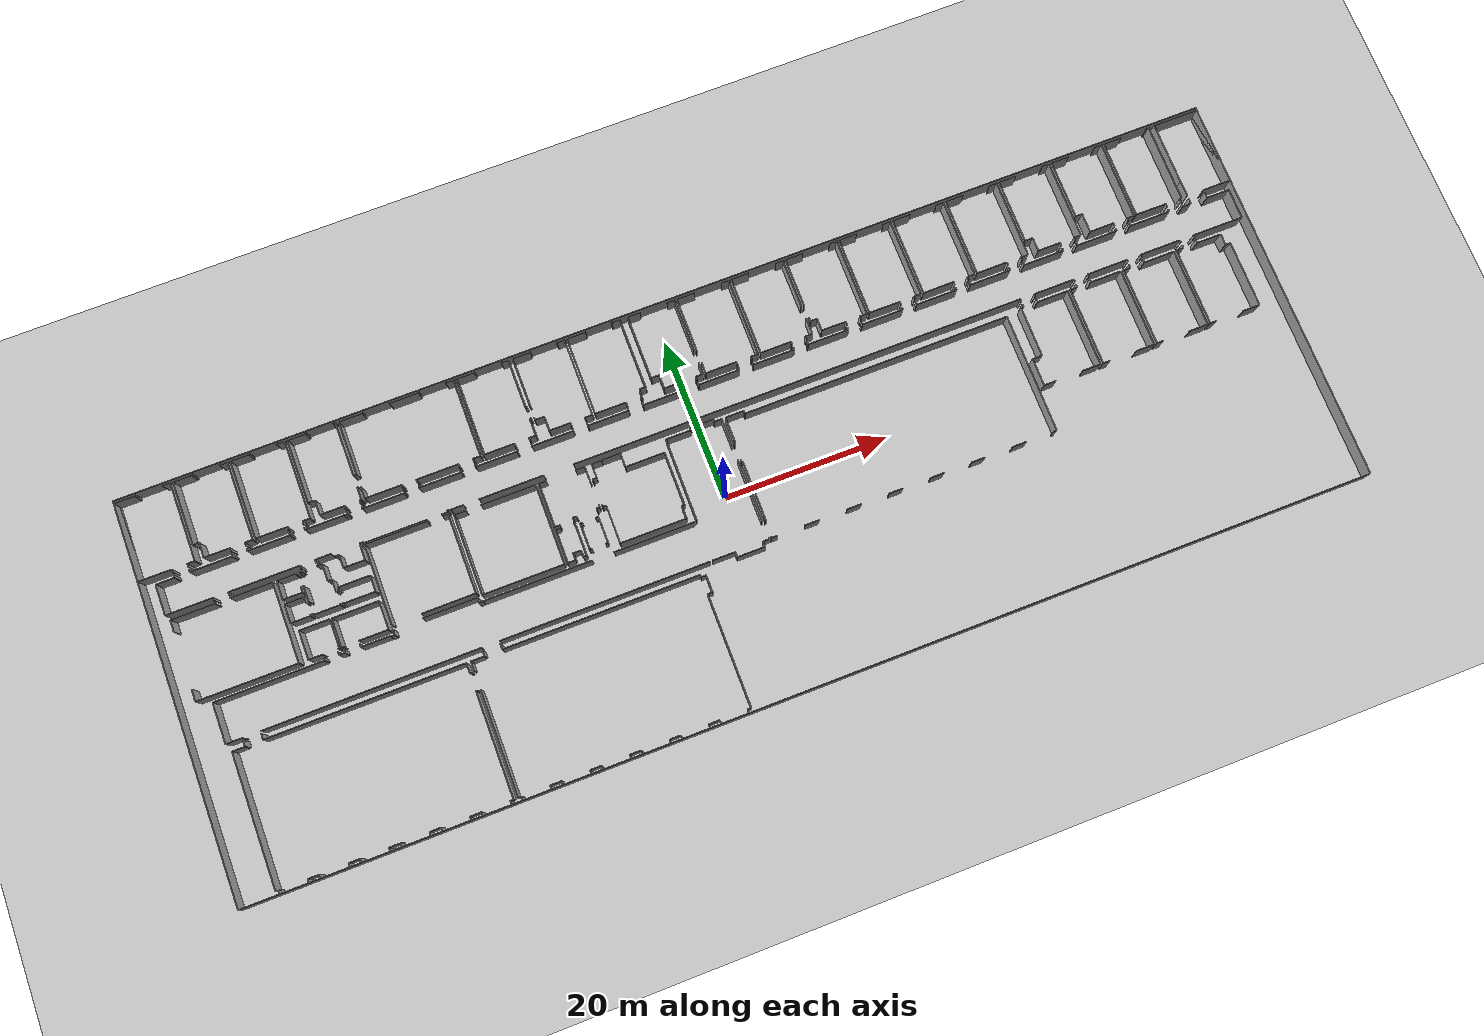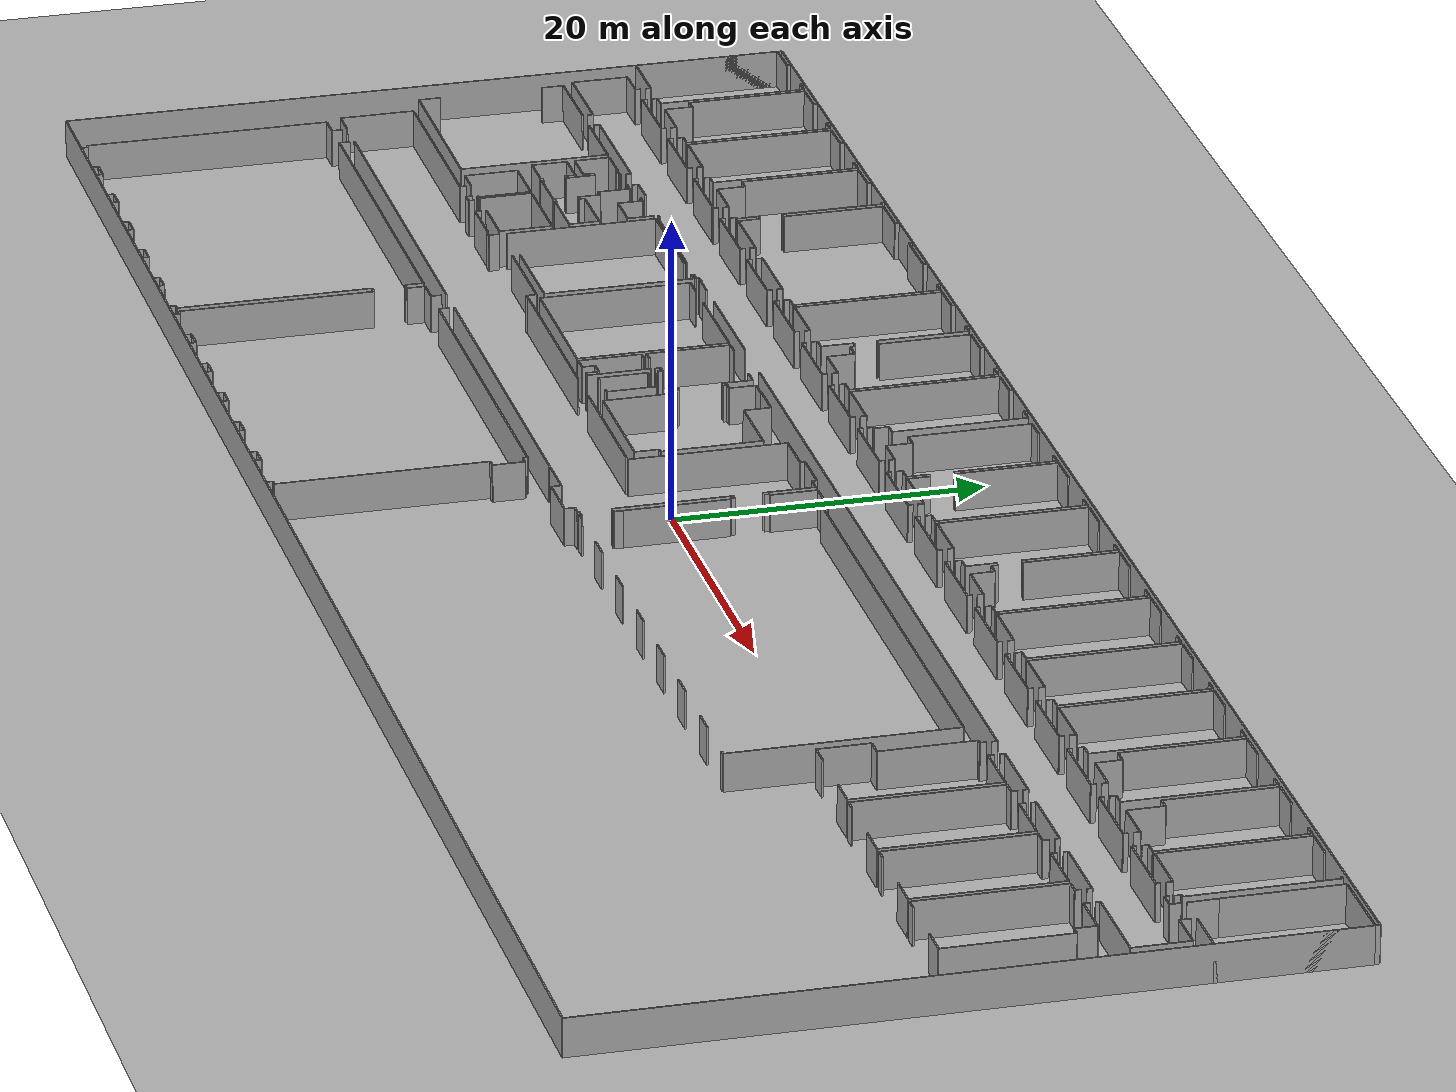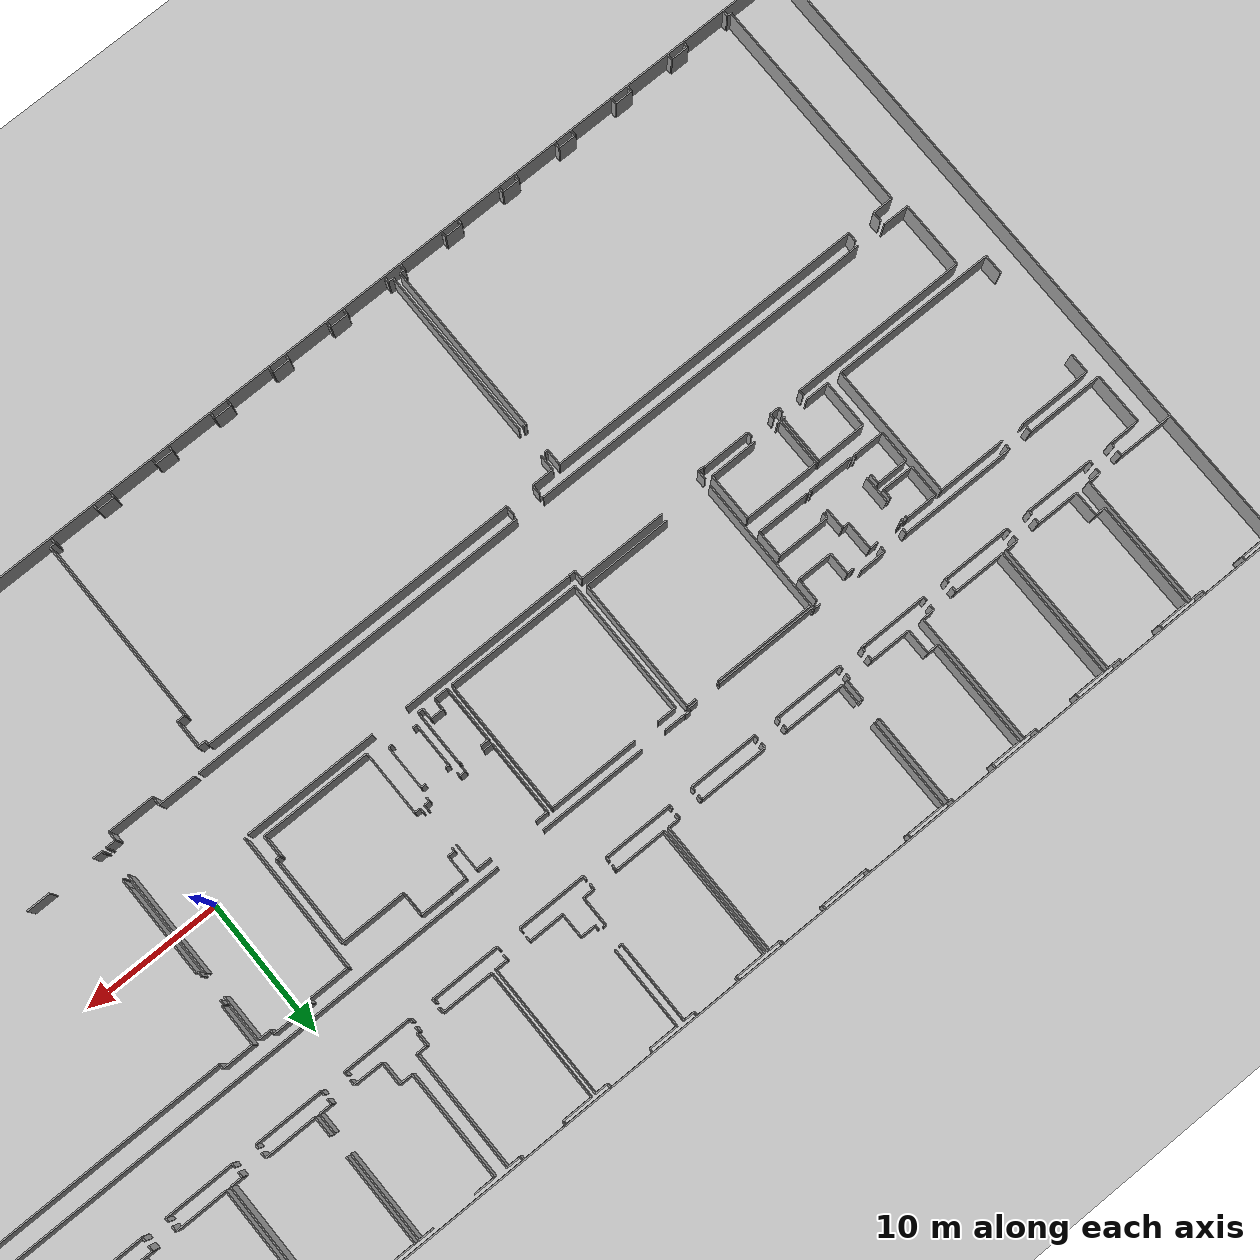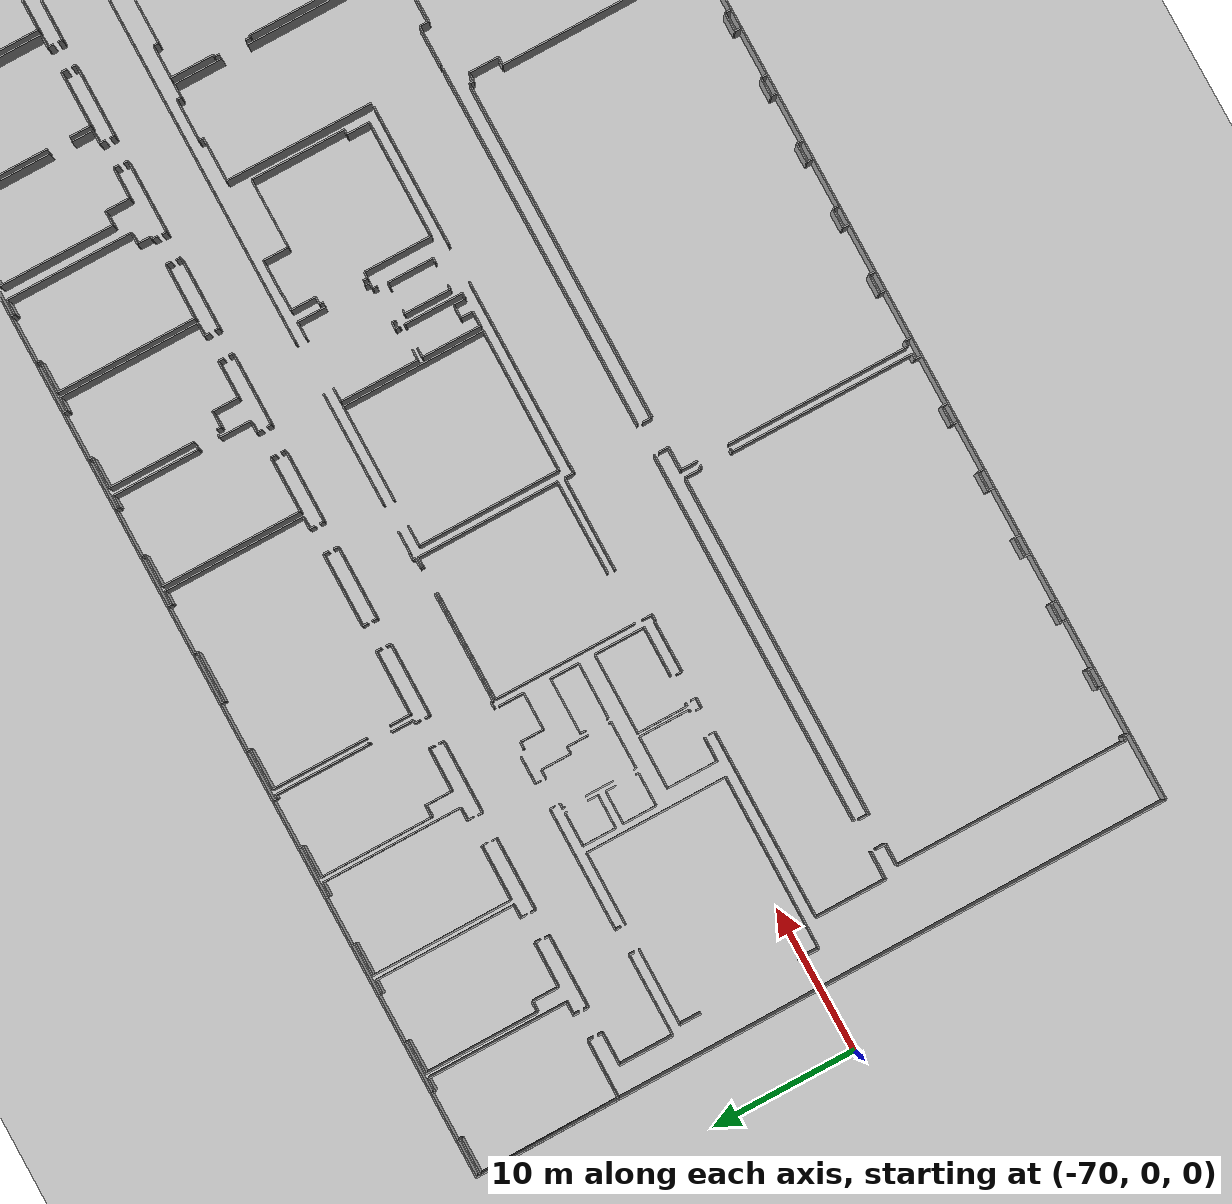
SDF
<sdf version="1.6">
  <world name="default">
    <light name="sun" type="directional">
      <cast_shadows>1</cast_shadows>
      <pose frame="">0 0 10 0 -0 0</pose>
      <diffuse>0.8 0.8 0.8 1</diffuse>
      <specular>0.1 0.1 0.1 1</specular>
      <attenuation>
        <range>1000</range>
        <constant>0.9</constant>
        <linear>0.01</linear>
        <quadratic>0.001</quadratic>
      </attenuation>
      <direction>-0.5 0.5 -1</direction>
    </light>
    <model name="ground_plane">
      <static>1</static>
      <link name="link">
        <collision name="collision">
          <geometry>
            <plane>
              <normal>0 0 1</normal>
              <size>100 100</size>
            </plane>
          </geometry>
          <surface>
            <friction>
              <ode>
                <mu>100</mu>
                <mu2>50</mu2>
              </ode>
              <torsional>
                <ode />
              </torsional>
            </friction>
            <contact>
              <ode />
            </contact>
            <bounce />
          </surface>
          <max_contacts>10</max_contacts>
        </collision>
        <visual name="visual">
          <cast_shadows>0</cast_shadows>
          <geometry>
            <plane>
              <normal>0 0 1</normal>
              <size>100 100</size>
            </plane>
          </geometry>
          <material>
            <script>
              <uri>file://media/materials/scripts/gazebo.material</uri>
              <name>Gazebo/Grey</name>
            </script>
          </material>
        </visual>
        <self_collide>0</self_collide>
        <kinematic>0</kinematic>
        <gravity>1</gravity>
      </link>
    </model>
    <gravity>0 0 -9.8</gravity>
    <magnetic_field>6e-06 2.3e-05 -4.2e-05</magnetic_field>
    <atmosphere type="adiabatic" />
    <physics default="0" name="default_physics" type="ode">
      <max_step_size>0.001</max_step_size>
      <real_time_factor>1</real_time_factor>
      <real_time_update_rate>1000</real_time_update_rate>
    </physics>
    <scene>
      <ambient>0.4 0.4 0.4 1</ambient>
      <background>0.7 0.7 0.7 1</background>
      <shadows>1</shadows>
    </scene>
    <spherical_coordinates>
      <surface_model>EARTH_WGS84</surface_model>
      <latitude_deg>0</latitude_deg>
      <longitude_deg>0</longitude_deg>
      <elevation>0</elevation>
      <heading_deg>0</heading_deg>
    </spherical_coordinates>
  <model name="0510032197_A_40_1_105">
		<static>1</static>
		<link name="Wall_0">
			<collision name="Wall_0_Collision">
				<geometry>
					<box>
						<size>9.64742815745 0.1 2.5</size>
					</box>
				</geometry>
				<pose frame="">4.82371407872 0 1.25 0 0 0</pose>
			</collision>
			<visual name="Wall_0_Visual">
				<pose frame="">4.82371407872 0 1.25 0 0 0</pose>
				<geometry>
					<box>
						<size>9.64742815745 0.1 2.5</size>
					</box>
				</geometry>
				<material>
					<script>
						<uri>file://media/materials/scripts/gazebo.material</uri>
						<name>Gazebo/Grey</name>
					</script>
					<ambient>1 1 1 1</ambient>
				</material>
			</visual>
			<pose frame="">0.0 -9.95221088219 0 0 0 1.57079632679</pose>
		</link>
		<link name="Wall_1">
			<collision name="Wall_1_Collision">
				<geometry>
					<box>
						<size>2.47041777348 0.1 2.5</size>
					</box>
				</geometry>
				<pose frame="">1.23520888674 0 1.25 0 0 0</pose>
			</collision>
			<visual name="Wall_1_Visual">
				<pose frame="">1.23520888674 0 1.25 0 0 0</pose>
				<geometry>
					<box>
						<size>2.47041777348 0.1 2.5</size>
					</box>
				</geometry>
				<material>
					<script>
						<uri>file://media/materials/scripts/gazebo.material</uri>
						<name>Gazebo/Grey</name>
					</script>
					<ambient>1 1 1 1</ambient>
				</material>
			</visual>
			<pose frame="">0.0 -0.304782724742 0 0 0 0.0</pose>
		</link>
		<link name="Wall_2">
			<collision name="Wall_2_Collision">
				<geometry>
					<box>
						<size>0.304782724742 0.1 2.5</size>
					</box>
				</geometry>
				<pose frame="">0.152391362371 0 1.25 0 0 0</pose>
			</collision>
			<visual name="Wall_2_Visual">
				<pose frame="">0.152391362371 0 1.25 0 0 0</pose>
				<geometry>
					<box>
						<size>0.304782724742 0.1 2.5</size>
					</box>
				</geometry>
				<material>
					<script>
						<uri>file://media/materials/scripts/gazebo.material</uri>
						<name>Gazebo/Grey</name>
					</script>
					<ambient>1 1 1 1</ambient>
				</material>
			</visual>
			<pose frame="">2.47041777348 -0.304782724742 0 0 0 1.57079632679</pose>
		</link>
		<link name="Wall_3">
			<collision name="Wall_3_Collision">
				<geometry>
					<box>
						<size>0.285972114541 0.1 2.5</size>
					</box>
				</geometry>
				<pose frame="">0.142986057271 0 1.25 0 0 0</pose>
			</collision>
			<visual name="Wall_3_Visual">
				<pose frame="">0.142986057271 0 1.25 0 0 0</pose>
				<geometry>
					<box>
						<size>0.285972114541 0.1 2.5</size>
					</box>
				</geometry>
				<material>
					<script>
						<uri>file://media/materials/scripts/gazebo.material</uri>
						<name>Gazebo/Grey</name>
					</script>
					<ambient>1 1 1 1</ambient>
				</material>
			</visual>
			<pose frame="">5.81197015722 -0.0 0 0 0 -1.57079632679</pose>
		</link>
		<link name="Wall_4">
			<collision name="Wall_4_Collision">
				<geometry>
					<box>
						<size>0.907866139631 0.1 2.5</size>
					</box>
				</geometry>
				<pose frame="">0.453933069815 0 1.25 0 0 0</pose>
			</collision>
			<visual name="Wall_4_Visual">
				<pose frame="">0.453933069815 0 1.25 0 0 0</pose>
				<geometry>
					<box>
						<size>0.907866139631 0.1 2.5</size>
					</box>
				</geometry>
				<material>
					<script>
						<uri>file://media/materials/scripts/gazebo.material</uri>
						<name>Gazebo/Grey</name>
					</script>
					<ambient>1 1 1 1</ambient>
				</material>
			</visual>
			<pose frame="">5.81197015722 -0.285972114541 0 0 0 0.0</pose>
		</link>
		<link name="Wall_5">
			<collision name="Wall_5_Collision">
				<geometry>
					<box>
						<size>9.6875913522 0.1 2.5</size>
					</box>
				</geometry>
				<pose frame="">4.8437956761 0 1.25 0 0 0</pose>
			</collision>
			<visual name="Wall_5_Visual">
				<pose frame="">4.8437956761 0 1.25 0 0 0</pose>
				<geometry>
					<box>
						<size>9.6875913522 0.1 2.5</size>
					</box>
				</geometry>
				<material>
					<script>
						<uri>file://media/materials/scripts/gazebo.material</uri>
						<name>Gazebo/Grey</name>
					</script>
					<ambient>1 1 1 1</ambient>
				</material>
			</visual>
			<pose frame="">6.71983629685 -0.285972114541 0 0 0 -1.57079632679</pose>
		</link>
		<link name="Wall_6">
			<collision name="Wall_6_Collision">
				<geometry>
					<box>
						<size>0.886640653796 0.1 2.5</size>
					</box>
				</geometry>
				<pose frame="">0.443320326898 0 1.25 0 0 0</pose>
			</collision>
			<visual name="Wall_6_Visual">
				<pose frame="">0.443320326898 0 1.25 0 0 0</pose>
				<geometry>
					<box>
						<size>0.886640653796 0.1 2.5</size>
					</box>
				</geometry>
				<material>
					<script>
						<uri>file://media/materials/scripts/gazebo.material</uri>
						<name>Gazebo/Grey</name>
					</script>
					<ambient>1 1 1 1</ambient>
				</material>
			</visual>
			<pose frame="">6.71983629685 -9.97356346674 0 0 0 3.14159265359</pose>
		</link>
		<link name="Wall_7">
			<collision name="Wall_7_Collision">
				<geometry>
					<box>
						<size>0.381550350157 0.1 2.5</size>
					</box>
				</geometry>
				<pose frame="">0.190775175078 0 1.25 0 0 0</pose>
			</collision>
			<visual name="Wall_7_Visual">
				<pose frame="">0.190775175078 0 1.25 0 0 0</pose>
				<geometry>
					<box>
						<size>0.381550350157 0.1 2.5</size>
					</box>
				</geometry>
				<material>
					<script>
						<uri>file://media/materials/scripts/gazebo.material</uri>
						<name>Gazebo/Grey</name>
					</script>
					<ambient>1 1 1 1</ambient>
				</material>
			</visual>
			<pose frame="">5.83319564306 -9.97356346674 0 0 0 -1.57079632679</pose>
		</link>
		<link name="Wall_8">
			<collision name="Wall_8_Collision">
				<geometry>
					<box>
						<size>0.375958006584 0.1 2.5</size>
					</box>
				</geometry>
				<pose frame="">0.187979003292 0 1.25 0 0 0</pose>
			</collision>
			<visual name="Wall_8_Visual">
				<pose frame="">0.187979003292 0 1.25 0 0 0</pose>
				<geometry>
					<box>
						<size>0.375958006584 0.1 2.5</size>
					</box>
				</geometry>
				<material>
					<script>
						<uri>file://media/materials/scripts/gazebo.material</uri>
						<name>Gazebo/Grey</name>
					</script>
					<ambient>1 1 1 1</ambient>
				</material>
			</visual>
			<pose frame="">4.04517088423 -10.3551138169 0 0 0 1.57079632679</pose>
		</link>
		<link name="Wall_9">
			<collision name="Wall_9_Collision">
				<geometry>
					<box>
						<size>4.04526062346 0.1 2.5</size>
					</box>
				</geometry>
				<pose frame="">2.02263031173 0 1.25 0 0 0</pose>
			</collision>
			<visual name="Wall_9_Visual">
				<pose frame="">2.02263031173 0 1.25 0 0 0</pose>
				<geometry>
					<box>
						<size>4.04526062346 0.1 2.5</size>
					</box>
				</geometry>
				<material>
					<script>
						<uri>file://media/materials/scripts/gazebo.material</uri>
						<name>Gazebo/Grey</name>
					</script>
					<ambient>1 1 1 1</ambient>
				</material>
			</visual>
			<pose frame="">4.04517088423 -9.97915581032 0 0 0 3.13493174101</pose>
		</link>
		<link name="Wall_10">
			<collision name="Wall_10_Collision">
				<geometry>
					<box>
						<size>1.84572757661 0.1 2.5</size>
					</box>
				</geometry>
				<pose frame="">0.922863788304 0 1.25 0 0 0</pose>
			</collision>
			<visual name="Wall_10_Visual">
				<pose frame="">0.922863788304 0 1.25 0 0 0</pose>
				<geometry>
					<box>
						<size>1.84572757661 0.1 2.5</size>
					</box>
				</geometry>
				<material>
					<script>
						<uri>file://media/materials/scripts/gazebo.material</uri>
						<name>Gazebo/Grey</name>
					</script>
					<ambient>1 1 1 1</ambient>
				</material>
			</visual>
			<pose frame="">7.78060219372 -9.96326847062 0 0 0 1.57079632679</pose>
		</link>
		<link name="Wall_11">
			<collision name="Wall_11_Collision">
				<geometry>
					<box>
						<size>0.729419540157 0.1 2.5</size>
					</box>
				</geometry>
				<pose frame="">0.364709770078 0 1.25 0 0 0</pose>
			</collision>
			<visual name="Wall_11_Visual">
				<pose frame="">0.364709770078 0 1.25 0 0 0</pose>
				<geometry>
					<box>
						<size>0.729419540157 0.1 2.5</size>
					</box>
				</geometry>
				<material>
					<script>
						<uri>file://media/materials/scripts/gazebo.material</uri>
						<name>Gazebo/Grey</name>
					</script>
					<ambient>1 1 1 1</ambient>
				</material>
			</visual>
			<pose frame="">7.78060219372 -8.11754089401 0 0 0 3.14159265359</pose>
		</link>
		<link name="Wall_12">
			<collision name="Wall_12_Collision">
				<geometry>
					<box>
						<size>7.80411545648 0.1 2.5</size>
					</box>
				</geometry>
				<pose frame="">3.90205772824 0 1.25 0 0 0</pose>
			</collision>
			<visual name="Wall_12_Visual">
				<pose frame="">3.90205772824 0 1.25 0 0 0</pose>
				<geometry>
					<box>
						<size>7.80411545648 0.1 2.5</size>
					</box>
				</geometry>
				<material>
					<script>
						<uri>file://media/materials/scripts/gazebo.material</uri>
						<name>Gazebo/Grey</name>
					</script>
					<ambient>1 1 1 1</ambient>
				</material>
			</visual>
			<pose frame="">7.05118265357 -8.11754089401 0 0 0 1.57079632679</pose>
		</link>
		<link name="Wall_13">
			<collision name="Wall_13_Collision">
				<geometry>
					<box>
						<size>2.23668323187 0.1 2.5</size>
					</box>
				</geometry>
				<pose frame="">1.11834161593 0 1.25 0 0 0</pose>
			</collision>
			<visual name="Wall_13_Visual">
				<pose frame="">1.11834161593 0 1.25 0 0 0</pose>
				<geometry>
					<box>
						<size>2.23668323187 0.1 2.5</size>
					</box>
				</geometry>
				<material>
					<script>
						<uri>file://media/materials/scripts/gazebo.material</uri>
						<name>Gazebo/Grey</name>
					</script>
					<ambient>1 1 1 1</ambient>
				</material>
			</visual>
			<pose frame="">7.05118265357 -0.313425437537 0 0 0 0.0</pose>
		</link>
		<link name="Wall_14">
			<collision name="Wall_14_Collision">
				<geometry>
					<box>
						<size>0.304782724742 0.1 2.5</size>
					</box>
				</geometry>
				<pose frame="">0.152391362371 0 1.25 0 0 0</pose>
			</collision>
			<visual name="Wall_14_Visual">
				<pose frame="">0.152391362371 0 1.25 0 0 0</pose>
				<geometry>
					<box>
						<size>0.304782724742 0.1 2.5</size>
					</box>
				</geometry>
				<material>
					<script>
						<uri>file://media/materials/scripts/gazebo.material</uri>
						<name>Gazebo/Grey</name>
					</script>
					<ambient>1 1 1 1</ambient>
				</material>
			</visual>
			<pose frame="">9.28786588543 -0.313425437537 0 0 0 1.57079632679</pose>
		</link>
		<link name="Wall_15">
			<collision name="Wall_15_Collision">
				<geometry>
					<box>
						<size>0.299063282451 0.1 2.5</size>
					</box>
				</geometry>
				<pose frame="">0.149531641226 0 1.25 0 0 0</pose>
			</collision>
			<visual name="Wall_15_Visual">
				<pose frame="">0.149531641226 0 1.25 0 0 0</pose>
				<geometry>
					<box>
						<size>0.299063282451 0.1 2.5</size>
					</box>
				</geometry>
				<material>
					<script>
						<uri>file://media/materials/scripts/gazebo.material</uri>
						<name>Gazebo/Grey</name>
					</script>
					<ambient>1 1 1 1</ambient>
				</material>
			</visual>
			<pose frame="">12.6347564153 -0.00864271279503 0 0 0 -1.57079632679</pose>
		</link>
		<link name="Wall_16">
			<collision name="Wall_16_Collision">
				<geometry>
					<box>
						<size>0.909137126806 0.1 2.5</size>
					</box>
				</geometry>
				<pose frame="">0.454568563403 0 1.25 0 0 0</pose>
			</collision>
			<visual name="Wall_16_Visual">
				<pose frame="">0.454568563403 0 1.25 0 0 0</pose>
				<geometry>
					<box>
						<size>0.909137126806 0.1 2.5</size>
					</box>
				</geometry>
				<material>
					<script>
						<uri>file://media/materials/scripts/gazebo.material</uri>
						<name>Gazebo/Grey</name>
					</script>
					<ambient>1 1 1 1</ambient>
				</material>
			</visual>
			<pose frame="">12.6347564153 -0.307705995247 0 0 0 0.0</pose>
		</link>
		<link name="Wall_17">
			<collision name="Wall_17_Collision">
				<geometry>
					<box>
						<size>9.66255290484 0.1 2.5</size>
					</box>
				</geometry>
				<pose frame="">4.83127645242 0 1.25 0 0 0</pose>
			</collision>
			<visual name="Wall_17_Visual">
				<pose frame="">4.83127645242 0 1.25 0 0 0</pose>
				<geometry>
					<box>
						<size>9.66255290484 0.1 2.5</size>
					</box>
				</geometry>
				<material>
					<script>
						<uri>file://media/materials/scripts/gazebo.material</uri>
						<name>Gazebo/Grey</name>
					</script>
					<ambient>1 1 1 1</ambient>
				</material>
			</visual>
			<pose frame="">13.5438935421 -0.307705995247 0 0 0 -1.57079632679</pose>
		</link>
		<link name="Wall_18">
			<collision name="Wall_18_Collision">
				<geometry>
					<box>
						<size>0.905578362714 0.1 2.5</size>
					</box>
				</geometry>
				<pose frame="">0.452789181357 0 1.25 0 0 0</pose>
			</collision>
			<visual name="Wall_18_Visual">
				<pose frame="">0.452789181357 0 1.25 0 0 0</pose>
				<geometry>
					<box>
						<size>0.905578362714 0.1 2.5</size>
					</box>
				</geometry>
				<material>
					<script>
						<uri>file://media/materials/scripts/gazebo.material</uri>
						<name>Gazebo/Grey</name>
					</script>
					<ambient>1 1 1 1</ambient>
				</material>
			</visual>
			<pose frame="">13.5438935421 -9.97025890009 0 0 0 3.14159265359</pose>
		</link>
		<link name="Wall_19">
			<collision name="Wall_19_Collision">
				<geometry>
					<box>
						<size>0.399598368052 0.1 2.5</size>
					</box>
				</geometry>
				<pose frame="">0.199799184026 0 1.25 0 0 0</pose>
			</collision>
			<visual name="Wall_19_Visual">
				<pose frame="">0.199799184026 0 1.25 0 0 0</pose>
				<geometry>
					<box>
						<size>0.399598368052 0.1 2.5</size>
					</box>
				</geometry>
				<material>
					<script>
						<uri>file://media/materials/scripts/gazebo.material</uri>
						<name>Gazebo/Grey</name>
					</script>
					<ambient>1 1 1 1</ambient>
				</material>
			</visual>
			<pose frame="">12.6383151794 -9.97025890009 0 0 0 -1.57079632679</pose>
		</link>
		<link name="Wall_20">
			<collision name="Wall_20_Collision">
				<geometry>
					<box>
						<size>0.387015595013 0.1 2.5</size>
					</box>
				</geometry>
				<pose frame="">0.193507797506 0 1.25 0 0 0</pose>
			</collision>
			<visual name="Wall_20_Visual">
				<pose frame="">0.193507797506 0 1.25 0 0 0</pose>
				<geometry>
					<box>
						<size>0.387015595013 0.1 2.5</size>
					</box>
				</geometry>
				<material>
					<script>
						<uri>file://media/materials/scripts/gazebo.material</uri>
						<name>Gazebo/Grey</name>
					</script>
					<ambient>1 1 1 1</ambient>
				</material>
			</visual>
			<pose frame="">10.8776166448 -10.3698572681 0 0 0 1.57079632679</pose>
		</link>
		<link name="Wall_21">
			<collision name="Wall_21_Collision">
				<geometry>
					<box>
						<size>3.09707630205 0.1 2.5</size>
					</box>
				</geometry>
				<pose frame="">1.54853815103 0 1.25 0 0 0</pose>
			</collision>
			<visual name="Wall_21_Visual">
				<pose frame="">1.54853815103 0 1.25 0 0 0</pose>
				<geometry>
					<box>
						<size>3.09707630205 0.1 2.5</size>
					</box>
				</geometry>
				<material>
					<script>
						<uri>file://media/materials/scripts/gazebo.material</uri>
						<name>Gazebo/Grey</name>
					</script>
					<ambient>1 1 1 1</ambient>
				</material>
			</visual>
			<pose frame="">10.8776166448 -9.98284167313 0 0 0 3.13527271475</pose>
		</link>
		<link name="Wall_22">
			<collision name="Wall_22_Collision">
				<geometry>
					<box>
						<size>9.64958883565 0.1 2.5</size>
					</box>
				</geometry>
				<pose frame="">4.82479441782 0 1.25 0 0 0</pose>
			</collision>
			<visual name="Wall_22_Visual">
				<pose frame="">4.82479441782 0 1.25 0 0 0</pose>
				<geometry>
					<box>
						<size>9.64958883565 0.1 2.5</size>
					</box>
				</geometry>
				<material>
					<script>
						<uri>file://media/materials/scripts/gazebo.material</uri>
						<name>Gazebo/Grey</name>
					</script>
					<ambient>1 1 1 1</ambient>
				</material>
			</visual>
			<pose frame="">13.8809593411 -9.96301427319 0 0 0 1.57079632679</pose>
		</link>
		<link name="Wall_23">
			<collision name="Wall_23_Collision">
				<geometry>
					<box>
						<size>2.2441820562 0.1 2.5</size>
					</box>
				</geometry>
				<pose frame="">1.1220910281 0 1.25 0 0 0</pose>
			</collision>
			<visual name="Wall_23_Visual">
				<pose frame="">1.1220910281 0 1.25 0 0 0</pose>
				<geometry>
					<box>
						<size>2.2441820562 0.1 2.5</size>
					</box>
				</geometry>
				<material>
					<script>
						<uri>file://media/materials/scripts/gazebo.material</uri>
						<name>Gazebo/Grey</name>
					</script>
					<ambient>1 1 1 1</ambient>
				</material>
			</visual>
			<pose frame="">13.8809593411 -0.313425437537 0 0 0 0.0</pose>
		</link>
		<link name="Wall_24">
			<collision name="Wall_24_Collision">
				<geometry>
					<box>
						<size>0.290674767092 0.1 2.5</size>
					</box>
				</geometry>
				<pose frame="">0.145337383546 0 1.25 0 0 0</pose>
			</collision>
			<visual name="Wall_24_Visual">
				<pose frame="">0.145337383546 0 1.25 0 0 0</pose>
				<geometry>
					<box>
						<size>0.290674767092 0.1 2.5</size>
					</box>
				</geometry>
				<material>
					<script>
						<uri>file://media/materials/scripts/gazebo.material</uri>
						<name>Gazebo/Grey</name>
					</script>
					<ambient>1 1 1 1</ambient>
				</material>
			</visual>
			<pose frame="">16.1251413973 -0.313425437537 0 0 0 1.57079632679</pose>
		</link>
		<link name="Wall_25">
			<collision name="Wall_25_Collision">
				<geometry>
					<box>
						<size>0.273262242784 0.1 2.5</size>
					</box>
				</geometry>
				<pose frame="">0.136631121392 0 1.25 0 0 0</pose>
			</collision>
			<visual name="Wall_25_Visual">
				<pose frame="">0.136631121392 0 1.25 0 0 0</pose>
				<geometry>
					<box>
						<size>0.273262242784 0.1 2.5</size>
					</box>
				</geometry>
				<material>
					<script>
						<uri>file://media/materials/scripts/gazebo.material</uri>
						<name>Gazebo/Grey</name>
					</script>
					<ambient>1 1 1 1</ambient>
				</material>
			</visual>
			<pose frame="">19.4655498926 -0.0227506704457 0 0 0 -1.57079632679</pose>
		</link>
		<link name="Wall_26">
			<collision name="Wall_26_Collision">
				<geometry>
					<box>
						<size>0.926549651114 0.1 2.5</size>
					</box>
				</geometry>
				<pose frame="">0.463274825557 0 1.25 0 0 0</pose>
			</collision>
			<visual name="Wall_26_Visual">
				<pose frame="">0.463274825557 0 1.25 0 0 0</pose>
				<geometry>
					<box>
						<size>0.926549651114 0.1 2.5</size>
					</box>
				</geometry>
				<material>
					<script>
						<uri>file://media/materials/scripts/gazebo.material</uri>
						<name>Gazebo/Grey</name>
					</script>
					<ambient>1 1 1 1</ambient>
				</material>
			</visual>
			<pose frame="">19.4655498926 -0.29601291323 0 0 0 0.0</pose>
		</link>
		<link name="Wall_27">
			<collision name="Wall_27_Collision">
				<geometry>
					<box>
						<size>9.65518117922 0.1 2.5</size>
					</box>
				</geometry>
				<pose frame="">4.82759058961 0 1.25 0 0 0</pose>
			</collision>
			<visual name="Wall_27_Visual">
				<pose frame="">4.82759058961 0 1.25 0 0 0</pose>
				<geometry>
					<box>
						<size>9.65518117922 0.1 2.5</size>
					</box>
				</geometry>
				<material>
					<script>
						<uri>file://media/materials/scripts/gazebo.material</uri>
						<name>Gazebo/Grey</name>
					</script>
					<ambient>1 1 1 1</ambient>
				</material>
			</visual>
			<pose frame="">20.3920995437 -0.29601291323 0 0 0 -1.57079632679</pose>
		</link>
		<link name="Wall_28">
			<collision name="Wall_28_Collision">
				<geometry>
					<box>
						<size>0.901892499905 0.1 2.5</size>
					</box>
				</geometry>
				<pose frame="">0.450946249952 0 1.25 0 0 0</pose>
			</collision>
			<visual name="Wall_28_Visual">
				<pose frame="">0.450946249952 0 1.25 0 0 0</pose>
				<geometry>
					<box>
						<size>0.901892499905 0.1 2.5</size>
					</box>
				</geometry>
				<material>
					<script>
						<uri>file://media/materials/scripts/gazebo.material</uri>
						<name>Gazebo/Grey</name>
					</script>
					<ambient>1 1 1 1</ambient>
				</material>
			</visual>
			<pose frame="">20.3920995437 -9.95119409245 0 0 0 3.14159265359</pose>
		</link>
		<link name="Wall_29">
			<collision name="Wall_29_Collision">
				<geometry>
					<box>
						<size>0.394768616785 0.1 2.5</size>
					</box>
				</geometry>
				<pose frame="">0.197384308392 0 1.25 0 0 0</pose>
			</collision>
			<visual name="Wall_29_Visual">
				<pose frame="">0.197384308392 0 1.25 0 0 0</pose>
				<geometry>
					<box>
						<size>0.394768616785 0.1 2.5</size>
					</box>
				</geometry>
				<material>
					<script>
						<uri>file://media/materials/scripts/gazebo.material</uri>
						<name>Gazebo/Grey</name>
					</script>
					<ambient>1 1 1 1</ambient>
				</material>
			</visual>
			<pose frame="">19.4902070438 -9.95119409245 0 0 0 -1.57079632679</pose>
		</link>
		<link name="Wall_30">
			<collision name="Wall_30_Collision">
				<geometry>
					<box>
						<size>0.377610289912 0.1 2.5</size>
					</box>
				</geometry>
				<pose frame="">0.188805144956 0 1.25 0 0 0</pose>
			</collision>
			<visual name="Wall_30_Visual">
				<pose frame="">0.188805144956 0 1.25 0 0 0</pose>
				<geometry>
					<box>
						<size>0.377610289912 0.1 2.5</size>
					</box>
				</geometry>
				<material>
					<script>
						<uri>file://media/materials/scripts/gazebo.material</uri>
						<name>Gazebo/Grey</name>
					</script>
					<ambient>1 1 1 1</ambient>
				</material>
			</visual>
			<pose frame="">17.6887098209 -10.3459627092 0 0 0 1.57079632679</pose>
		</link>
		<link name="Wall_31">
			<collision name="Wall_31_Collision">
				<geometry>
					<box>
						<size>3.80775422161 0.1 2.5</size>
					</box>
				</geometry>
				<pose frame="">1.90387711081 0 1.25 0 0 0</pose>
			</collision>
			<visual name="Wall_31_Visual">
				<pose frame="">1.90387711081 0 1.25 0 0 0</pose>
				<geometry>
					<box>
						<size>3.80775422161 0.1 2.5</size>
					</box>
				</geometry>
				<material>
					<script>
						<uri>file://media/materials/scripts/gazebo.material</uri>
						<name>Gazebo/Grey</name>
					</script>
					<ambient>1 1 1 1</ambient>
				</material>
			</visual>
			<pose frame="">17.6887098209 -9.96835241932 0 0 0 3.14019073856</pose>
		</link>
		<link name="Wall_32">
			<collision name="Wall_32_Collision">
				<geometry>
					<box>
						<size>1.84178751636 0.1 2.5</size>
					</box>
				</geometry>
				<pose frame="">0.920893758182 0 1.25 0 0 0</pose>
			</collision>
			<visual name="Wall_32_Visual">
				<pose frame="">0.920893758182 0 1.25 0 0 0</pose>
				<geometry>
					<box>
						<size>1.84178751636 0.1 2.5</size>
					</box>
				</geometry>
				<material>
					<script>
						<uri>file://media/materials/scripts/gazebo.material</uri>
						<name>Gazebo/Grey</name>
					</script>
					<ambient>1 1 1 1</ambient>
				</material>
			</visual>
			<pose frame="">21.5399280621 -9.96619174113 0 0 0 1.57079632679</pose>
		</link>
		<link name="Wall_33">
			<collision name="Wall_33_Collision">
				<geometry>
					<box>
						<size>0.813558891191 0.1 2.5</size>
					</box>
				</geometry>
				<pose frame="">0.406779445595 0 1.25 0 0 0</pose>
			</collision>
			<visual name="Wall_33_Visual">
				<pose frame="">0.406779445595 0 1.25 0 0 0</pose>
				<geometry>
					<box>
						<size>0.813558891191 0.1 2.5</size>
					</box>
				</geometry>
				<material>
					<script>
						<uri>file://media/materials/scripts/gazebo.material</uri>
						<name>Gazebo/Grey</name>
					</script>
					<ambient>1 1 1 1</ambient>
				</material>
			</visual>
			<pose frame="">21.5399280621 -8.12440422476 0 0 0 3.14159265359</pose>
		</link>
		<link name="Wall_34">
			<collision name="Wall_34_Collision">
				<geometry>
					<box>
						<size>7.81123298466 0.1 2.5</size>
					</box>
				</geometry>
				<pose frame="">3.90561649233 0 1.25 0 0 0</pose>
			</collision>
			<visual name="Wall_34_Visual">
				<pose frame="">3.90561649233 0 1.25 0 0 0</pose>
				<geometry>
					<box>
						<size>7.81123298466 0.1 2.5</size>
					</box>
				</geometry>
				<material>
					<script>
						<uri>file://media/materials/scripts/gazebo.material</uri>
						<name>Gazebo/Grey</name>
					</script>
					<ambient>1 1 1 1</ambient>
				</material>
			</visual>
			<pose frame="">20.7263691709 -8.12440422476 0 0 0 1.57079632679</pose>
		</link>
		<link name="Wall_35">
			<collision name="Wall_35_Collision">
				<geometry>
					<box>
						<size>2.23020119727 0.1 2.5</size>
					</box>
				</geometry>
				<pose frame="">1.11510059863 0 1.25 0 0 0</pose>
			</collision>
			<visual name="Wall_35_Visual">
				<pose frame="">1.11510059863 0 1.25 0 0 0</pose>
				<geometry>
					<box>
						<size>2.23020119727 0.1 2.5</size>
					</box>
				</geometry>
				<material>
					<script>
						<uri>file://media/materials/scripts/gazebo.material</uri>
						<name>Gazebo/Grey</name>
					</script>
					<ambient>1 1 1 1</ambient>
				</material>
			</visual>
			<pose frame="">20.7263691709 -0.313171240102 0 0 0 0.0</pose>
		</link>
		<link name="Wall_36">
			<collision name="Wall_36_Collision">
				<geometry>
					<box>
						<size>0.296648406818 0.1 2.5</size>
					</box>
				</geometry>
				<pose frame="">0.148324203409 0 1.25 0 0 0</pose>
			</collision>
			<visual name="Wall_36_Visual">
				<pose frame="">0.148324203409 0 1.25 0 0 0</pose>
				<geometry>
					<box>
						<size>0.296648406818 0.1 2.5</size>
					</box>
				</geometry>
				<material>
					<script>
						<uri>file://media/materials/scripts/gazebo.material</uri>
						<name>Gazebo/Grey</name>
					</script>
					<ambient>1 1 1 1</ambient>
				</material>
			</visual>
			<pose frame="">22.9565703682 -0.313171240102 0 0 0 1.57079632679</pose>
		</link>
		<link name="Wall_37">
			<collision name="Wall_37_Collision">
				<geometry>
					<box>
						<size>0.279998474815 0.1 2.5</size>
					</box>
				</geometry>
				<pose frame="">0.139999237408 0 1.25 0 0 0</pose>
			</collision>
			<visual name="Wall_37_Visual">
				<pose frame="">0.139999237408 0 1.25 0 0 0</pose>
				<geometry>
					<box>
						<size>0.279998474815 0.1 2.5</size>
					</box>
				</geometry>
				<material>
					<script>
						<uri>file://media/materials/scripts/gazebo.material</uri>
						<name>Gazebo/Grey</name>
					</script>
					<ambient>1 1 1 1</ambient>
				</material>
			</visual>
			<pose frame="">26.2868109661 -0.0165228332846 0 0 0 -1.57079632679</pose>
		</link>
		<link name="Wall_38">
			<collision name="Wall_38_Collision">
				<geometry>
					<box>
						<size>0.234751331359 0.1 2.5</size>
					</box>
				</geometry>
				<pose frame="">0.11737566568 0 1.25 0 0 0</pose>
			</collision>
			<visual name="Wall_38_Visual">
				<pose frame="">0.11737566568 0 1.25 0 0 0</pose>
				<geometry>
					<box>
						<size>0.234751331359 0.1 2.5</size>
					</box>
				</geometry>
				<material>
					<script>
						<uri>file://media/materials/scripts/gazebo.material</uri>
						<name>Gazebo/Grey</name>
					</script>
					<ambient>1 1 1 1</ambient>
				</material>
			</visual>
			<pose frame="">26.2868109661 -0.2965213081 0 0 0 0.0</pose>
		</link>
		<link name="Wall_39">
			<collision name="Wall_39_Collision">
				<geometry>
					<box>
						<size>6.61599664459 0.1 2.5</size>
					</box>
				</geometry>
				<pose frame="">3.3079983223 0 1.25 0 0 0</pose>
			</collision>
			<visual name="Wall_39_Visual">
				<pose frame="">3.3079983223 0 1.25 0 0 0</pose>
				<geometry>
					<box>
						<size>6.61599664459 0.1 2.5</size>
					</box>
				</geometry>
				<material>
					<script>
						<uri>file://media/materials/scripts/gazebo.material</uri>
						<name>Gazebo/Grey</name>
					</script>
					<ambient>1 1 1 1</ambient>
				</material>
			</visual>
			<pose frame="">26.5215622974 -0.2965213081 0 0 0 -1.57079632679</pose>
		</link>
		<link name="Wall_40">
			<collision name="Wall_40_Collision">
				<geometry>
					<box>
						<size>0.105619034304 0.1 2.5</size>
					</box>
				</geometry>
				<pose frame="">0.052809517152 0 1.25 0 0 0</pose>
			</collision>
			<visual name="Wall_40_Visual">
				<pose frame="">0.052809517152 0 1.25 0 0 0</pose>
				<geometry>
					<box>
						<size>0.105619034304 0.1 2.5</size>
					</box>
				</geometry>
				<material>
					<script>
						<uri>file://media/materials/scripts/gazebo.material</uri>
						<name>Gazebo/Grey</name>
					</script>
					<ambient>1 1 1 1</ambient>
				</material>
			</visual>
			<pose frame="">26.5215622974 -6.91251795269 0 0 0 0.0</pose>
		</link>
		<link name="Wall_41">
			<collision name="Wall_41_Collision">
				<geometry>
					<box>
						<size>0.109050699678 0.1 2.5</size>
					</box>
				</geometry>
				<pose frame="">0.0545253498392 0 1.25 0 0 0</pose>
			</collision>
			<visual name="Wall_41_Visual">
				<pose frame="">0.0545253498392 0 1.25 0 0 0</pose>
				<geometry>
					<box>
						<size>0.109050699678 0.1 2.5</size>
					</box>
				</geometry>
				<material>
					<script>
						<uri>file://media/materials/scripts/gazebo.material</uri>
						<name>Gazebo/Grey</name>
					</script>
					<ambient>1 1 1 1</ambient>
				</material>
			</visual>
			<pose frame="">26.6271813317 -8.45867385198 0 0 0 3.14159265359</pose>
		</link>
		<link name="Wall_42">
			<collision name="Wall_42_Collision">
				<geometry>
					<box>
						<size>1.50345073018 0.1 2.5</size>
					</box>
				</geometry>
				<pose frame="">0.751725365091 0 1.25 0 0 0</pose>
			</collision>
			<visual name="Wall_42_Visual">
				<pose frame="">0.751725365091 0 1.25 0 0 0</pose>
				<geometry>
					<box>
						<size>1.50345073018 0.1 2.5</size>
					</box>
				</geometry>
				<material>
					<script>
						<uri>file://media/materials/scripts/gazebo.material</uri>
						<name>Gazebo/Grey</name>
					</script>
					<ambient>1 1 1 1</ambient>
				</material>
			</visual>
			<pose frame="">26.5181306321 -8.45867385198 0 0 0 -1.57079632679</pose>
		</link>
		<link name="Wall_43">
			<collision name="Wall_43_Collision">
				<geometry>
					<box>
						<size>0.215178128853 0.1 2.5</size>
					</box>
				</geometry>
				<pose frame="">0.107589064426 0 1.25 0 0 0</pose>
			</collision>
			<visual name="Wall_43_Visual">
				<pose frame="">0.107589064426 0 1.25 0 0 0</pose>
				<geometry>
					<box>
						<size>0.215178128853 0.1 2.5</size>
					</box>
				</geometry>
				<material>
					<script>
						<uri>file://media/materials/scripts/gazebo.material</uri>
						<name>Gazebo/Grey</name>
					</script>
					<ambient>1 1 1 1</ambient>
				</material>
			</visual>
			<pose frame="">26.5181306321 -9.96212458216 0 0 0 3.14159265359</pose>
		</link>
		<link name="Wall_44">
			<collision name="Wall_44_Collision">
				<geometry>
					<box>
						<size>0.390065964234 0.1 2.5</size>
					</box>
				</geometry>
				<pose frame="">0.195032982117 0 1.25 0 0 0</pose>
			</collision>
			<visual name="Wall_44_Visual">
				<pose frame="">0.195032982117 0 1.25 0 0 0</pose>
				<geometry>
					<box>
						<size>0.390065964234 0.1 2.5</size>
					</box>
				</geometry>
				<material>
					<script>
						<uri>file://media/materials/scripts/gazebo.material</uri>
						<name>Gazebo/Grey</name>
					</script>
					<ambient>1 1 1 1</ambient>
				</material>
			</visual>
			<pose frame="">26.3029525032 -9.96212458216 0 0 0 -1.57079632679</pose>
		</link>
		<link name="Wall_45">
			<collision name="Wall_45_Collision">
				<geometry>
					<box>
						<size>0.371890847621 0.1 2.5</size>
					</box>
				</geometry>
				<pose frame="">0.185945423811 0 1.25 0 0 0</pose>
			</collision>
			<visual name="Wall_45_Visual">
				<pose frame="">0.185945423811 0 1.25 0 0 0</pose>
				<geometry>
					<box>
						<size>0.371890847621 0.1 2.5</size>
					</box>
				</geometry>
				<material>
					<script>
						<uri>file://media/materials/scripts/gazebo.material</uri>
						<name>Gazebo/Grey</name>
					</script>
					<ambient>1 1 1 1</ambient>
				</material>
			</visual>
			<pose frame="">24.5177239162 -10.3521905464 0 0 0 1.57079632679</pose>
		</link>
		<link name="Wall_46">
			<collision name="Wall_46_Collision">
				<geometry>
					<box>
						<size>2.97782927362 0.1 2.5</size>
					</box>
				</geometry>
				<pose frame="">1.48891463681 0 1.25 0 0 0</pose>
			</collision>
			<visual name="Wall_46_Visual">
				<pose frame="">1.48891463681 0 1.25 0 0 0</pose>
				<geometry>
					<box>
						<size>2.97782927362 0.1 2.5</size>
					</box>
				</geometry>
				<material>
					<script>
						<uri>file://media/materials/scripts/gazebo.material</uri>
						<name>Gazebo/Grey</name>
					</script>
					<ambient>1 1 1 1</ambient>
				</material>
			</visual>
			<pose frame="">24.5177239162 -9.98029969878 0 0 0 3.13685497082</pose>
		</link>
		<link name="Wall_47">
			<collision name="Wall_47_Collision">
				<geometry>
					<box>
						<size>1.45972877134 0.1 2.5</size>
					</box>
				</geometry>
				<pose frame="">0.729864385668 0 1.25 0 0 0</pose>
			</collision>
			<visual name="Wall_47_Visual">
				<pose frame="">0.729864385668 0 1.25 0 0 0</pose>
				<geometry>
					<box>
						<size>1.45972877134 0.1 2.5</size>
					</box>
				</geometry>
				<material>
					<script>
						<uri>file://media/materials/scripts/gazebo.material</uri>
						<name>Gazebo/Grey</name>
					</script>
					<ambient>1 1 1 1</ambient>
				</material>
			</visual>
			<pose frame="">26.9181102963 -9.96898791291 0 0 0 1.57079632679</pose>
		</link>
		<link name="Wall_48">
			<collision name="Wall_48_Collision">
				<geometry>
					<box>
						<size>6.6051932536 0.1 2.5</size>
					</box>
				</geometry>
				<pose frame="">3.3025966268 0 1.25 0 0 0</pose>
			</collision>
			<visual name="Wall_48_Visual">
				<pose frame="">3.3025966268 0 1.25 0 0 0</pose>
				<geometry>
					<box>
						<size>6.6051932536 0.1 2.5</size>
					</box>
				</geometry>
				<material>
					<script>
						<uri>file://media/materials/scripts/gazebo.material</uri>
						<name>Gazebo/Grey</name>
					</script>
					<ambient>1 1 1 1</ambient>
				</material>
			</visual>
			<pose frame="">26.9181102963 -6.91772900011 0 0 0 1.57079632679</pose>
		</link>
		<link name="Wall_49">
			<collision name="Wall_49_Collision">
				<geometry>
					<box>
						<size>2.84103763393 0.1 2.5</size>
					</box>
				</geometry>
				<pose frame="">1.42051881697 0 1.25 0 0 0</pose>
			</collision>
			<visual name="Wall_49_Visual">
				<pose frame="">1.42051881697 0 1.25 0 0 0</pose>
				<geometry>
					<box>
						<size>2.84103763393 0.1 2.5</size>
					</box>
				</geometry>
				<material>
					<script>
						<uri>file://media/materials/scripts/gazebo.material</uri>
						<name>Gazebo/Grey</name>
					</script>
					<ambient>1 1 1 1</ambient>
				</material>
			</visual>
			<pose frame="">26.9181102963 -0.312535746514 0 0 0 0.0</pose>
		</link>
		<link name="Wall_50">
			<collision name="Wall_50_Collision">
				<geometry>
					<box>
						<size>0.297919393993 0.1 2.5</size>
					</box>
				</geometry>
				<pose frame="">0.148959696997 0 1.25 0 0 0</pose>
			</collision>
			<visual name="Wall_50_Visual">
				<pose frame="">0.148959696997 0 1.25 0 0 0</pose>
				<geometry>
					<box>
						<size>0.297919393993 0.1 2.5</size>
					</box>
				</geometry>
				<material>
					<script>
						<uri>file://media/materials/scripts/gazebo.material</uri>
						<name>Gazebo/Grey</name>
					</script>
					<ambient>1 1 1 1</ambient>
				</material>
			</visual>
			<pose frame="">29.7591479302 -0.312535746514 0 0 0 1.57079632679</pose>
		</link>
		<link name="Wall_51">
			<collision name="Wall_51_Collision">
				<geometry>
					<box>
						<size>0.28393853506 0.1 2.5</size>
					</box>
				</geometry>
				<pose frame="">0.14196926753 0 1.25 0 0 0</pose>
			</collision>
			<visual name="Wall_51_Visual">
				<pose frame="">0.14196926753 0 1.25 0 0 0</pose>
				<geometry>
					<box>
						<size>0.28393853506 0.1 2.5</size>
					</box>
				</geometry>
				<material>
					<script>
						<uri>file://media/materials/scripts/gazebo.material</uri>
						<name>Gazebo/Grey</name>
					</script>
					<ambient>1 1 1 1</ambient>
				</material>
			</visual>
			<pose frame="">33.1005732152 -0.014616352521 0 0 0 -1.57079632679</pose>
		</link>
		<link name="Wall_52">
			<collision name="Wall_52_Collision">
				<geometry>
					<box>
						<size>3.50462003838 0.1 2.5</size>
					</box>
				</geometry>
				<pose frame="">1.75231001919 0 1.25 0 0 0</pose>
			</collision>
			<visual name="Wall_52_Visual">
				<pose frame="">1.75231001919 0 1.25 0 0 0</pose>
				<geometry>
					<box>
						<size>3.50462003838 0.1 2.5</size>
					</box>
				</geometry>
				<material>
					<script>
						<uri>file://media/materials/scripts/gazebo.material</uri>
						<name>Gazebo/Grey</name>
					</script>
					<ambient>1 1 1 1</ambient>
				</material>
			</visual>
			<pose frame="">33.1005732152 -0.298554887581 0 0 0 0.0</pose>
		</link>
		<link name="Wall_53">
			<collision name="Wall_53_Collision">
				<geometry>
					<box>
						<size>0.288386990175 0.1 2.5</size>
					</box>
				</geometry>
				<pose frame="">0.144193495088 0 1.25 0 0 0</pose>
			</collision>
			<visual name="Wall_53_Visual">
				<pose frame="">0.144193495088 0 1.25 0 0 0</pose>
				<geometry>
					<box>
						<size>0.288386990175 0.1 2.5</size>
					</box>
				</geometry>
				<material>
					<script>
						<uri>file://media/materials/scripts/gazebo.material</uri>
						<name>Gazebo/Grey</name>
					</script>
					<ambient>1 1 1 1</ambient>
				</material>
			</visual>
			<pose frame="">36.6051932536 -0.298554887581 0 0 0 1.57079632679</pose>
		</link>
		<link name="Wall_54">
			<collision name="Wall_54_Collision">
				<geometry>
					<box>
						<size>0.289912174786 0.1 2.5</size>
					</box>
				</geometry>
				<pose frame="">0.144956087393 0 1.25 0 0 0</pose>
			</collision>
			<visual name="Wall_54_Visual">
				<pose frame="">0.144956087393 0 1.25 0 0 0</pose>
				<geometry>
					<box>
						<size>0.289912174786 0.1 2.5</size>
					</box>
				</geometry>
				<material>
					<script>
						<uri>file://media/materials/scripts/gazebo.material</uri>
						<name>Gazebo/Grey</name>
					</script>
					<ambient>1 1 1 1</ambient>
				</material>
			</visual>
			<pose frame="">39.9308582976 -0.0101678974059 0 0 0 -1.57079632679</pose>
		</link>
		<link name="Wall_55">
			<collision name="Wall_55_Collision">
				<geometry>
					<box>
						<size>0.917398543449 0.1 2.5</size>
					</box>
				</geometry>
				<pose frame="">0.458699271724 0 1.25 0 0 0</pose>
			</collision>
			<visual name="Wall_55_Visual">
				<pose frame="">0.458699271724 0 1.25 0 0 0</pose>
				<geometry>
					<box>
						<size>0.917398543449 0.1 2.5</size>
					</box>
				</geometry>
				<material>
					<script>
						<uri>file://media/materials/scripts/gazebo.material</uri>
						<name>Gazebo/Grey</name>
					</script>
					<ambient>1 1 1 1</ambient>
				</material>
			</visual>
			<pose frame="">39.9308582976 -0.300080072192 0 0 0 0.0</pose>
		</link>
		<link name="Wall_56">
			<collision name="Wall_56_Collision">
				<geometry>
					<box>
						<size>9.67666086249 0.1 2.5</size>
					</box>
				</geometry>
				<pose frame="">4.83833043125 0 1.25 0 0 0</pose>
			</collision>
			<visual name="Wall_56_Visual">
				<pose frame="">4.83833043125 0 1.25 0 0 0</pose>
				<geometry>
					<box>
						<size>9.67666086249 0.1 2.5</size>
					</box>
				</geometry>
				<material>
					<script>
						<uri>file://media/materials/scripts/gazebo.material</uri>
						<name>Gazebo/Grey</name>
					</script>
					<ambient>1 1 1 1</ambient>
				</material>
			</visual>
			<pose frame="">40.8482568411 -0.300080072192 0 0 0 -1.57079632679</pose>
		</link>
		<link name="Wall_57">
			<collision name="Wall_57_Collision">
				<geometry>
					<box>
						<size>0.902782190928 0.1 2.5</size>
					</box>
				</geometry>
				<pose frame="">0.451391095464 0 1.25 0 0 0</pose>
			</collision>
			<visual name="Wall_57_Visual">
				<pose frame="">0.451391095464 0 1.25 0 0 0</pose>
				<geometry>
					<box>
						<size>0.902782190928 0.1 2.5</size>
					</box>
				</geometry>
				<material>
					<script>
						<uri>file://media/materials/scripts/gazebo.material</uri>
						<name>Gazebo/Grey</name>
					</script>
					<ambient>1 1 1 1</ambient>
				</material>
			</visual>
			<pose frame="">40.8482568411 -9.97674093468 0 0 0 3.14159265359</pose>
		</link>
		<link name="Wall_58">
			<collision name="Wall_58_Collision">
				<geometry>
					<box>
						<size>0.381169054004 0.1 2.5</size>
					</box>
				</geometry>
				<pose frame="">0.190584527002 0 1.25 0 0 0</pose>
			</collision>
			<visual name="Wall_58_Visual">
				<pose frame="">0.190584527002 0 1.25 0 0 0</pose>
				<geometry>
					<box>
						<size>0.381169054004 0.1 2.5</size>
					</box>
				</geometry>
				<material>
					<script>
						<uri>file://media/materials/scripts/gazebo.material</uri>
						<name>Gazebo/Grey</name>
					</script>
					<ambient>1 1 1 1</ambient>
				</material>
			</visual>
			<pose frame="">39.9454746502 -9.97674093468 0 0 0 -1.57079632679</pose>
		</link>
		<link name="Wall_59">
			<collision name="Wall_59_Collision">
				<geometry>
					<box>
						<size>0.373797328385 0.1 2.5</size>
					</box>
				</geometry>
				<pose frame="">0.186898664192 0 1.25 0 0 0</pose>
			</collision>
			<visual name="Wall_59_Visual">
				<pose frame="">0.186898664192 0 1.25 0 0 0</pose>
				<geometry>
					<box>
						<size>0.373797328385 0.1 2.5</size>
					</box>
				</geometry>
				<material>
					<script>
						<uri>file://media/materials/scripts/gazebo.material</uri>
						<name>Gazebo/Grey</name>
					</script>
					<ambient>1 1 1 1</ambient>
				</material>
			</visual>
			<pose frame="">38.1732101323 -10.3579099887 0 0 0 1.57079632679</pose>
		</link>
		<link name="Wall_60">
			<collision name="Wall_60_Collision">
				<geometry>
					<box>
						<size>5.06246901969 0.1 2.5</size>
					</box>
				</geometry>
				<pose frame="">2.53123450984 0 1.25 0 0 0</pose>
			</collision>
			<visual name="Wall_60_Visual">
				<pose frame="">2.53123450984 0 1.25 0 0 0</pose>
				<geometry>
					<box>
						<size>5.06246901969 0.1 2.5</size>
					</box>
				</geometry>
				<material>
					<script>
						<uri>file://media/materials/scripts/gazebo.material</uri>
						<name>Gazebo/Grey</name>
					</script>
					<ambient>1 1 1 1</ambient>
				</material>
			</visual>
			<pose frame="">38.1732101323 -9.9841126603 0 0 0 3.14159265359</pose>
		</link>
		<link name="Wall_61">
			<collision name="Wall_61_Collision">
				<geometry>
					<box>
						<size>0.37036566301 0.1 2.5</size>
					</box>
				</geometry>
				<pose frame="">0.185182831505 0 1.25 0 0 0</pose>
			</collision>
			<visual name="Wall_61_Visual">
				<pose frame="">0.185182831505 0 1.25 0 0 0</pose>
				<geometry>
					<box>
						<size>0.37036566301 0.1 2.5</size>
					</box>
				</geometry>
				<material>
					<script>
						<uri>file://media/materials/scripts/gazebo.material</uri>
						<name>Gazebo/Grey</name>
					</script>
					<ambient>1 1 1 1</ambient>
				</material>
			</visual>
			<pose frame="">33.1107411126 -9.9841126603 0 0 0 -1.57079632679</pose>
		</link>
		<link name="Wall_62">
			<collision name="Wall_62_Collision">
				<geometry>
					<box>
						<size>0.375830907866 0.1 2.5</size>
					</box>
				</geometry>
				<pose frame="">0.187915453933 0 1.25 0 0 0</pose>
			</collision>
			<visual name="Wall_62_Visual">
				<pose frame="">0.187915453933 0 1.25 0 0 0</pose>
				<geometry>
					<box>
						<size>0.375830907866 0.1 2.5</size>
					</box>
				</geometry>
				<material>
					<script>
						<uri>file://media/materials/scripts/gazebo.material</uri>
						<name>Gazebo/Grey</name>
					</script>
					<ambient>1 1 1 1</ambient>
				</material>
			</visual>
			<pose frame="">31.3527116511 -10.3544783233 0 0 0 1.57079632679</pose>
		</link>
		<link name="Wall_63">
			<collision name="Wall_63_Collision">
				<geometry>
					<box>
						<size>4.43461187508 0.1 2.5</size>
					</box>
				</geometry>
				<pose frame="">2.21730593754 0 1.25 0 0 0</pose>
			</collision>
			<visual name="Wall_63_Visual">
				<pose frame="">2.21730593754 0 1.25 0 0 0</pose>
				<geometry>
					<box>
						<size>4.43461187508 0.1 2.5</size>
					</box>
				</geometry>
				<material>
					<script>
						<uri>file://media/materials/scripts/gazebo.material</uri>
						<name>Gazebo/Grey</name>
					</script>
					<ambient>1 1 1 1</ambient>
				</material>
			</visual>
			<pose frame="">31.3527116511 -9.97864741545 0 0 0 3.13941444489</pose>
		</link>
		<link name="Wall_64">
			<collision name="Wall_64_Collision">
				<geometry>
					<box>
						<size>9.68568487144 0.1 2.5</size>
					</box>
				</geometry>
				<pose frame="">4.84284243572 0 1.25 0 0 0</pose>
			</collision>
			<visual name="Wall_64_Visual">
				<pose frame="">4.84284243572 0 1.25 0 0 0</pose>
				<geometry>
					<box>
						<size>9.68568487144 0.1 2.5</size>
					</box>
				</geometry>
				<material>
					<script>
						<uri>file://media/materials/scripts/gazebo.material</uri>
						<name>Gazebo/Grey</name>
					</script>
					<ambient>1 1 1 1</ambient>
				</material>
			</visual>
			<pose frame="">41.1910420824 -9.9884340167 0 0 0 1.57079632679</pose>
		</link>
		<link name="Wall_65">
			<collision name="Wall_65_Collision">
				<geometry>
					<box>
						<size>2.23973360109 0.1 2.5</size>
					</box>
				</geometry>
				<pose frame="">1.11986680054 0 1.25 0 0 0</pose>
			</collision>
			<visual name="Wall_65_Visual">
				<pose frame="">1.11986680054 0 1.25 0 0 0</pose>
				<geometry>
					<box>
						<size>2.23973360109 0.1 2.5</size>
					</box>
				</geometry>
				<material>
					<script>
						<uri>file://media/materials/scripts/gazebo.material</uri>
						<name>Gazebo/Grey</name>
					</script>
					<ambient>1 1 1 1</ambient>
				</material>
			</visual>
			<pose frame="">41.1910420824 -0.302749145261 0 0 0 0.0</pose>
		</link>
		<link name="Wall_66">
			<collision name="Wall_66_Collision">
				<geometry>
					<box>
						<size>0.292581247855 0.1 2.5</size>
					</box>
				</geometry>
				<pose frame="">0.146290623928 0 1.25 0 0 0</pose>
			</collision>
			<visual name="Wall_66_Visual">
				<pose frame="">0.146290623928 0 1.25 0 0 0</pose>
				<geometry>
					<box>
						<size>0.292581247855 0.1 2.5</size>
					</box>
				</geometry>
				<material>
					<script>
						<uri>file://media/materials/scripts/gazebo.material</uri>
						<name>Gazebo/Grey</name>
					</script>
					<ambient>1 1 1 1</ambient>
				</material>
			</visual>
			<pose frame="">43.4307756835 -0.302749145261 0 0 0 1.57079632679</pose>
		</link>
		<link name="Wall_67">
			<collision name="Wall_67_Collision">
				<geometry>
					<box>
						<size>0.29702970297 0.1 2.5</size>
					</box>
				</geometry>
				<pose frame="">0.148514851485 0 1.25 0 0 0</pose>
			</collision>
			<visual name="Wall_67_Visual">
				<pose frame="">0.148514851485 0 1.25 0 0 0</pose>
				<geometry>
					<box>
						<size>0.29702970297 0.1 2.5</size>
					</box>
				</geometry>
				<material>
					<script>
						<uri>file://media/materials/scripts/gazebo.material</uri>
						<name>Gazebo/Grey</name>
					</script>
					<ambient>1 1 1 1</ambient>
				</material>
			</visual>
			<pose frame="">46.7598723929 -0.0101678974059 0 0 0 -1.57079632679</pose>
		</link>
		<link name="Wall_68">
			<collision name="Wall_68_Collision">
				<geometry>
					<box>
						<size>0.802501302762 0.1 2.5</size>
					</box>
				</geometry>
				<pose frame="">0.401250651381 0 1.25 0 0 0</pose>
			</collision>
			<visual name="Wall_68_Visual">
				<pose frame="">0.401250651381 0 1.25 0 0 0</pose>
				<geometry>
					<box>
						<size>0.802501302762 0.1 2.5</size>
					</box>
				</geometry>
				<material>
					<script>
						<uri>file://media/materials/scripts/gazebo.material</uri>
						<name>Gazebo/Grey</name>
					</script>
					<ambient>1 1 1 1</ambient>
				</material>
			</visual>
			<pose frame="">46.7598723929 -0.307197600376 0 0 0 0.0</pose>
		</link>
		<link name="Wall_69">
			<collision name="Wall_69_Collision">
				<geometry>
					<box>
						<size>5.98406182082 0.1 2.5</size>
					</box>
				</geometry>
				<pose frame="">2.99203091041 0 1.25 0 0 0</pose>
			</collision>
			<visual name="Wall_69_Visual">
				<pose frame="">2.99203091041 0 1.25 0 0 0</pose>
				<geometry>
					<box>
						<size>5.98406182082 0.1 2.5</size>
					</box>
				</geometry>
				<material>
					<script>
						<uri>file://media/materials/scripts/gazebo.material</uri>
						<name>Gazebo/Grey</name>
					</script>
					<ambient>1 1 1 1</ambient>
				</material>
			</visual>
			<pose frame="">47.5623736956 -0.307197600376 0 0 0 -1.57079632679</pose>
		</link>
		<link name="Wall_70">
			<collision name="Wall_70_Collision">
				<geometry>
					<box>
						<size>0.246444413376 0.1 2.5</size>
					</box>
				</geometry>
				<pose frame="">0.123222206688 0 1.25 0 0 0</pose>
			</collision>
			<visual name="Wall_70_Visual">
				<pose frame="">0.123222206688 0 1.25 0 0 0</pose>
				<geometry>
					<box>
						<size>0.246444413376 0.1 2.5</size>
					</box>
				</geometry>
				<material>
					<script>
						<uri>file://media/materials/scripts/gazebo.material</uri>
						<name>Gazebo/Grey</name>
					</script>
					<ambient>1 1 1 1</ambient>
				</material>
			</visual>
			<pose frame="">47.5623736956 -6.29125942119 0 0 0 0.0</pose>
		</link>
		<link name="Wall_71">
			<collision name="Wall_71_Collision">
				<geometry>
					<box>
						<size>0.221151768579 0.1 2.5</size>
					</box>
				</geometry>
				<pose frame="">0.110575884289 0 1.25 0 0 0</pose>
			</collision>
			<visual name="Wall_71_Visual">
				<pose frame="">0.110575884289 0 1.25 0 0 0</pose>
				<geometry>
					<box>
						<size>0.221151768579 0.1 2.5</size>
					</box>
				</geometry>
				<material>
					<script>
						<uri>file://media/materials/scripts/gazebo.material</uri>
						<name>Gazebo/Grey</name>
					</script>
					<ambient>1 1 1 1</ambient>
				</material>
			</visual>
			<pose frame="">47.808818109 -7.80780131928 0 0 0 3.14159265359</pose>
		</link>
		<link name="Wall_72">
			<collision name="Wall_72_Collision">
				<geometry>
					<box>
						<size>2.15483165775 0.1 2.5</size>
					</box>
				</geometry>
				<pose frame="">1.07741582887 0 1.25 0 0 0</pose>
			</collision>
			<visual name="Wall_72_Visual">
				<pose frame="">1.07741582887 0 1.25 0 0 0</pose>
				<geometry>
					<box>
						<size>2.15483165775 0.1 2.5</size>
					</box>
				</geometry>
				<material>
					<script>
						<uri>file://media/materials/scripts/gazebo.material</uri>
						<name>Gazebo/Grey</name>
					</script>
					<ambient>1 1 1 1</ambient>
				</material>
			</visual>
			<pose frame="">47.5876663404 -7.80780131928 0 0 0 -1.57079632679</pose>
		</link>
		<link name="Wall_73">
			<collision name="Wall_73_Collision">
				<geometry>
					<box>
						<size>0.827793947559 0.1 2.5</size>
					</box>
				</geometry>
				<pose frame="">0.41389697378 0 1.25 0 0 0</pose>
			</collision>
			<visual name="Wall_73_Visual">
				<pose frame="">0.41389697378 0 1.25 0 0 0</pose>
				<geometry>
					<box>
						<size>0.827793947559 0.1 2.5</size>
					</box>
				</geometry>
				<material>
					<script>
						<uri>file://media/materials/scripts/gazebo.material</uri>
						<name>Gazebo/Grey</name>
					</script>
					<ambient>1 1 1 1</ambient>
				</material>
			</visual>
			<pose frame="">47.5876663404 -9.96263297703 0 0 0 3.14159265359</pose>
		</link>
		<link name="Wall_74">
			<collision name="Wall_74_Collision">
				<geometry>
					<box>
						<size>0.39184534628 0.1 2.5</size>
					</box>
				</geometry>
				<pose frame="">0.19592267314 0 1.25 0 0 0</pose>
			</collision>
			<visual name="Wall_74_Visual">
				<pose frame="">0.19592267314 0 1.25 0 0 0</pose>
				<geometry>
					<box>
						<size>0.39184534628 0.1 2.5</size>
					</box>
				</geometry>
				<material>
					<script>
						<uri>file://media/materials/scripts/gazebo.material</uri>
						<name>Gazebo/Grey</name>
					</script>
					<ambient>1 1 1 1</ambient>
				</material>
			</visual>
			<pose frame="">46.7598723929 -9.96263297703 0 0 0 -1.57079632679</pose>
		</link>
		<link name="Wall_75">
			<collision name="Wall_75_Collision">
				<geometry>
					<box>
						<size>0.37773738863 0.1 2.5</size>
					</box>
				</geometry>
				<pose frame="">0.188868694315 0 1.25 0 0 0</pose>
			</collision>
			<visual name="Wall_75_Visual">
				<pose frame="">0.188868694315 0 1.25 0 0 0</pose>
				<geometry>
					<box>
						<size>0.37773738863 0.1 2.5</size>
					</box>
				</geometry>
				<material>
					<script>
						<uri>file://media/materials/scripts/gazebo.material</uri>
						<name>Gazebo/Grey</name>
					</script>
					<ambient>1 1 1 1</ambient>
				</material>
			</visual>
			<pose frame="">44.9813800379 -10.3544783233 0 0 0 1.57079632679</pose>
		</link>
		<link name="Wall_76">
			<collision name="Wall_76_Collision">
				<geometry>
					<box>
						<size>3.79035599186 0.1 2.5</size>
					</box>
				</geometry>
				<pose frame="">1.89517799593 0 1.25 0 0 0</pose>
			</collision>
			<visual name="Wall_76_Visual">
				<pose frame="">1.89517799593 0 1.25 0 0 0</pose>
				<geometry>
					<box>
						<size>3.79035599186 0.1 2.5</size>
					</box>
				</geometry>
				<material>
					<script>
						<uri>file://media/materials/scripts/gazebo.material</uri>
						<name>Gazebo/Grey</name>
					</script>
					<ambient>1 1 1 1</ambient>
				</material>
			</visual>
			<pose frame="">44.9813800379 -9.97674093468 0 0 0 -3.13850769255</pose>
		</link>
		<link name="Wall_77">
			<collision name="Wall_77_Collision">
				<geometry>
					<box>
						<size>1.79094802933 0.1 2.5</size>
					</box>
				</geometry>
				<pose frame="">0.895474014667 0 1.25 0 0 0</pose>
			</collision>
			<visual name="Wall_77_Visual">
				<pose frame="">0.895474014667 0 1.25 0 0 0</pose>
				<geometry>
					<box>
						<size>1.79094802933 0.1 2.5</size>
					</box>
				</geometry>
				<material>
					<script>
						<uri>file://media/materials/scripts/gazebo.material</uri>
						<name>Gazebo/Grey</name>
					</script>
					<ambient>1 1 1 1</ambient>
				</material>
			</visual>
			<pose frame="">49.2220287497 -9.98004550134 0 0 0 1.57079632679</pose>
		</link>
		<link name="Wall_78">
			<collision name="Wall_78_Collision">
				<geometry>
					<box>
						<size>1.10982600186 0.1 2.5</size>
					</box>
				</geometry>
				<pose frame="">0.554913000928 0 1.25 0 0 0</pose>
			</collision>
			<visual name="Wall_78_Visual">
				<pose frame="">0.554913000928 0 1.25 0 0 0</pose>
				<geometry>
					<box>
						<size>1.10982600186 0.1 2.5</size>
					</box>
				</geometry>
				<material>
					<script>
						<uri>file://media/materials/scripts/gazebo.material</uri>
						<name>Gazebo/Grey</name>
					</script>
					<ambient>1 1 1 1</ambient>
				</material>
			</visual>
			<pose frame="">49.2220287497 -8.18909747201 0 0 0 3.14159265359</pose>
		</link>
		<link name="Wall_79">
			<collision name="Wall_79_Collision">
				<geometry>
					<box>
						<size>0.343293636167 0.1 2.5</size>
					</box>
				</geometry>
				<pose frame="">0.171646818084 0 1.25 0 0 0</pose>
			</collision>
			<visual name="Wall_79_Visual">
				<pose frame="">0.171646818084 0 1.25 0 0 0</pose>
				<geometry>
					<box>
						<size>0.343293636167 0.1 2.5</size>
					</box>
				</geometry>
				<material>
					<script>
						<uri>file://media/materials/scripts/gazebo.material</uri>
						<name>Gazebo/Grey</name>
					</script>
					<ambient>1 1 1 1</ambient>
				</material>
			</visual>
			<pose frame="">48.1122027479 -8.18909747201 0 0 0 1.57079632679</pose>
		</link>
		<link name="Wall_80">
			<collision name="Wall_80_Collision">
				<geometry>
					<box>
						<size>5.97338552854 0.1 2.5</size>
					</box>
				</geometry>
				<pose frame="">2.98669276427 0 1.25 0 0 0</pose>
			</collision>
			<visual name="Wall_80_Visual">
				<pose frame="">2.98669276427 0 1.25 0 0 0</pose>
				<geometry>
					<box>
						<size>5.97338552854 0.1 2.5</size>
					</box>
				</geometry>
				<material>
					<script>
						<uri>file://media/materials/scripts/gazebo.material</uri>
						<name>Gazebo/Grey</name>
					</script>
					<ambient>1 1 1 1</ambient>
				</material>
			</visual>
			<pose frame="">48.1122027479 -6.28592127505 0 0 0 1.57079632679</pose>
		</link>
		<link name="Wall_81">
			<collision name="Wall_81_Collision">
				<geometry>
					<box>
						<size>2.16144079106 0.1 2.5</size>
					</box>
				</geometry>
				<pose frame="">1.08072039553 0 1.25 0 0 0</pose>
			</collision>
			<visual name="Wall_81_Visual">
				<pose frame="">1.08072039553 0 1.25 0 0 0</pose>
				<geometry>
					<box>
						<size>2.16144079106 0.1 2.5</size>
					</box>
				</geometry>
				<material>
					<script>
						<uri>file://media/materials/scripts/gazebo.material</uri>
						<name>Gazebo/Grey</name>
					</script>
					<ambient>1 1 1 1</ambient>
				</material>
			</visual>
			<pose frame="">48.1122027479 -0.312535746514 0 0 0 0.0</pose>
		</link>
		<link name="Wall_82">
			<collision name="Wall_82_Collision">
				<geometry>
					<box>
						<size>0.305291119613 0.1 2.5</size>
					</box>
				</geometry>
				<pose frame="">0.152645559806 0 1.25 0 0 0</pose>
			</collision>
			<visual name="Wall_82_Visual">
				<pose frame="">0.152645559806 0 1.25 0 0 0</pose>
				<geometry>
					<box>
						<size>0.305291119613 0.1 2.5</size>
					</box>
				</geometry>
				<material>
					<script>
						<uri>file://media/materials/scripts/gazebo.material</uri>
						<name>Gazebo/Grey</name>
					</script>
					<ambient>1 1 1 1</ambient>
				</material>
			</visual>
			<pose frame="">50.2736435389 -0.312535746514 0 0 0 1.57079632679</pose>
		</link>
		<link name="Wall_83">
			<collision name="Wall_83_Collision">
				<geometry>
					<box>
						<size>0.312917042667 0.1 2.5</size>
					</box>
				</geometry>
				<pose frame="">0.156458521334 0 1.25 0 0 0</pose>
			</collision>
			<visual name="Wall_83_Visual">
				<pose frame="">0.156458521334 0 1.25 0 0 0</pose>
				<geometry>
					<box>
						<size>0.312917042667 0.1 2.5</size>
					</box>
				</geometry>
				<material>
					<script>
						<uri>file://media/materials/scripts/gazebo.material</uri>
						<name>Gazebo/Grey</name>
					</script>
					<ambient>1 1 1 1</ambient>
				</material>
			</visual>
			<pose frame="">53.5810063676 -0.00724462690171 0 0 0 -1.57079632679</pose>
		</link>
		<link name="Wall_84">
			<collision name="Wall_84_Collision">
				<geometry>
					<box>
						<size>0.930743908794 0.1 2.5</size>
					</box>
				</geometry>
				<pose frame="">0.465371954397 0 1.25 0 0 0</pose>
			</collision>
			<visual name="Wall_84_Visual">
				<pose frame="">0.465371954397 0 1.25 0 0 0</pose>
				<geometry>
					<box>
						<size>0.930743908794 0.1 2.5</size>
					</box>
				</geometry>
				<material>
					<script>
						<uri>file://media/materials/scripts/gazebo.material</uri>
						<name>Gazebo/Grey</name>
					</script>
					<ambient>1 1 1 1</ambient>
				</material>
			</visual>
			<pose frame="">53.5810063676 -0.320161669569 0 0 0 0.0</pose>
		</link>
		<link name="Wall_85">
			<collision name="Wall_85_Collision">
				<geometry>
					<box>
						<size>9.64882624334 0.1 2.5</size>
					</box>
				</geometry>
				<pose frame="">4.82441312167 0 1.25 0 0 0</pose>
			</collision>
			<visual name="Wall_85_Visual">
				<pose frame="">4.82441312167 0 1.25 0 0 0</pose>
				<geometry>
					<box>
						<size>9.64882624334 0.1 2.5</size>
					</box>
				</geometry>
				<material>
					<script>
						<uri>file://media/materials/scripts/gazebo.material</uri>
						<name>Gazebo/Grey</name>
					</script>
					<ambient>1 1 1 1</ambient>
				</material>
			</visual>
			<pose frame="">54.5117502764 -0.320161669569 0 0 0 -1.57079632679</pose>
		</link>
		<link name="Wall_86">
			<collision name="Wall_86_Collision">
				<geometry>
					<box>
						<size>0.927312243419 0.1 2.5</size>
					</box>
				</geometry>
				<pose frame="">0.46365612171 0 1.25 0 0 0</pose>
			</collision>
			<visual name="Wall_86_Visual">
				<pose frame="">0.46365612171 0 1.25 0 0 0</pose>
				<geometry>
					<box>
						<size>0.927312243419 0.1 2.5</size>
					</box>
				</geometry>
				<material>
					<script>
						<uri>file://media/materials/scripts/gazebo.material</uri>
						<name>Gazebo/Grey</name>
					</script>
					<ambient>1 1 1 1</ambient>
				</material>
			</visual>
			<pose frame="">54.5117502764 -9.96898791291 0 0 0 3.14159265359</pose>
		</link>
		<link name="Wall_87">
			<collision name="Wall_87_Collision">
				<geometry>
					<box>
						<size>0.379135474523 0.1 2.5</size>
					</box>
				</geometry>
				<pose frame="">0.189567737262 0 1.25 0 0 0</pose>
			</collision>
			<visual name="Wall_87_Visual">
				<pose frame="">0.189567737262 0 1.25 0 0 0</pose>
				<geometry>
					<box>
						<size>0.379135474523 0.1 2.5</size>
					</box>
				</geometry>
				<material>
					<script>
						<uri>file://media/materials/scripts/gazebo.material</uri>
						<name>Gazebo/Grey</name>
					</script>
					<ambient>1 1 1 1</ambient>
				</material>
			</visual>
			<pose frame="">53.584438033 -9.96898791291 0 0 0 -1.57079632679</pose>
		</link>
		<link name="Wall_88">
			<collision name="Wall_88_Collision">
				<geometry>
					<box>
						<size>0.372780538644 0.1 2.5</size>
					</box>
				</geometry>
				<pose frame="">0.186390269322 0 1.25 0 0 0</pose>
			</collision>
			<visual name="Wall_88_Visual">
				<pose frame="">0.186390269322 0 1.25 0 0 0</pose>
				<geometry>
					<box>
						<size>0.372780538644 0.1 2.5</size>
					</box>
				</geometry>
				<material>
					<script>
						<uri>file://media/materials/scripts/gazebo.material</uri>
						<name>Gazebo/Grey</name>
					</script>
					<ambient>1 1 1 1</ambient>
				</material>
			</visual>
			<pose frame="">51.8025140126 -10.3481233874 0 0 0 1.57079632679</pose>
		</link>
		<link name="Wall_89">
			<collision name="Wall_89_Collision">
				<geometry>
					<box>
						<size>2.58048954794 0.1 2.5</size>
					</box>
				</geometry>
				<pose frame="">1.29024477397 0 1.25 0 0 0</pose>
			</collision>
			<visual name="Wall_89_Visual">
				<pose frame="">1.29024477397 0 1.25 0 0 0</pose>
				<geometry>
					<box>
						<size>2.58048954794 0.1 2.5</size>
					</box>
				</geometry>
				<material>
					<script>
						<uri>file://media/materials/scripts/gazebo.material</uri>
						<name>Gazebo/Grey</name>
					</script>
					<ambient>1 1 1 1</ambient>
				</material>
			</visual>
			<pose frame="">51.8025140126 -9.97534284879 0 0 0 -3.13977026483</pose>
		</link>
		<link name="Wall_90">
			<collision name="Wall_90_Collision">
				<geometry>
					<box>
						<size>9.65848574588 0.1 2.5</size>
					</box>
				</geometry>
				<pose frame="">4.82924287294 0 1.25 0 0 0</pose>
			</collision>
			<visual name="Wall_90_Visual">
				<pose frame="">4.82924287294 0 1.25 0 0 0</pose>
				<geometry>
					<box>
						<size>9.65848574588 0.1 2.5</size>
					</box>
				</geometry>
				<material>
					<script>
						<uri>file://media/materials/scripts/gazebo.material</uri>
						<name>Gazebo/Grey</name>
					</script>
					<ambient>1 1 1 1</ambient>
				</material>
			</visual>
			<pose frame="">54.8403004614 -9.96326847062 0 0 0 1.57079632679</pose>
		</link>
		<link name="Wall_91">
			<collision name="Wall_91_Collision">
				<geometry>
					<box>
						<size>2.25346026259 0.1 2.5</size>
					</box>
				</geometry>
				<pose frame="">1.12673013129 0 1.25 0 0 0</pose>
			</collision>
			<visual name="Wall_91_Visual">
				<pose frame="">1.12673013129 0 1.25 0 0 0</pose>
				<geometry>
					<box>
						<size>2.25346026259 0.1 2.5</size>
					</box>
				</geometry>
				<material>
					<script>
						<uri>file://media/materials/scripts/gazebo.material</uri>
						<name>Gazebo/Grey</name>
					</script>
					<ambient>1 1 1 1</ambient>
				</material>
			</visual>
			<pose frame="">54.8403004614 -0.304782724742 0 0 0 0.0</pose>
		</link>
		<link name="Wall_92">
			<collision name="Wall_92_Collision">
				<geometry>
					<box>
						<size>0.296140011947 0.1 2.5</size>
					</box>
				</geometry>
				<pose frame="">0.148070005974 0 1.25 0 0 0</pose>
			</collision>
			<visual name="Wall_92_Visual">
				<pose frame="">0.148070005974 0 1.25 0 0 0</pose>
				<geometry>
					<box>
						<size>0.296140011947 0.1 2.5</size>
					</box>
				</geometry>
				<material>
					<script>
						<uri>file://media/materials/scripts/gazebo.material</uri>
						<name>Gazebo/Grey</name>
					</script>
					<ambient>1 1 1 1</ambient>
				</material>
			</visual>
			<pose frame="">57.093760724 -0.304782724742 0 0 0 1.57079632679</pose>
		</link>
		<link name="Wall_93">
			<collision name="Wall_93_Collision">
				<geometry>
					<box>
						<size>0.286607608129 0.1 2.5</size>
					</box>
				</geometry>
				<pose frame="">0.143303804065 0 1.25 0 0 0</pose>
			</collision>
			<visual name="Wall_93_Visual">
				<pose frame="">0.143303804065 0 1.25 0 0 0</pose>
				<geometry>
					<box>
						<size>0.286607608129 0.1 2.5</size>
					</box>
				</geometry>
				<material>
					<script>
						<uri>file://media/materials/scripts/gazebo.material</uri>
						<name>Gazebo/Grey</name>
					</script>
					<ambient>1 1 1 1</ambient>
				</material>
			</visual>
			<pose frame="">60.3992170719 -0.00864271279503 0 0 0 -1.57079632679</pose>
		</link>
		<link name="Wall_94">
			<collision name="Wall_94_Collision">
				<geometry>
					<box>
						<size>1.00547795473 0.1 2.5</size>
					</box>
				</geometry>
				<pose frame="">0.502738977364 0 1.25 0 0 0</pose>
			</collision>
			<visual name="Wall_94_Visual">
				<pose frame="">0.502738977364 0 1.25 0 0 0</pose>
				<geometry>
					<box>
						<size>1.00547795473 0.1 2.5</size>
					</box>
				</geometry>
				<material>
					<script>
						<uri>file://media/materials/scripts/gazebo.material</uri>
						<name>Gazebo/Grey</name>
					</script>
					<ambient>1 1 1 1</ambient>
				</material>
			</visual>
			<pose frame="">60.3992170719 -0.295250320924 0 0 0 0.0</pose>
		</link>
		<link name="Wall_95">
			<collision name="Wall_95_Collision">
				<geometry>
					<box>
						<size>8.7488402242 0.1 2.5</size>
					</box>
				</geometry>
				<pose frame="">4.3744201121 0 1.25 0 0 0</pose>
			</collision>
			<visual name="Wall_95_Visual">
				<pose frame="">4.3744201121 0 1.25 0 0 0</pose>
				<geometry>
					<box>
						<size>8.7488402242 0.1 2.5</size>
					</box>
				</geometry>
				<material>
					<script>
						<uri>file://media/materials/scripts/gazebo.material</uri>
						<name>Gazebo/Grey</name>
					</script>
					<ambient>1 1 1 1</ambient>
				</material>
			</visual>
			<pose frame="">61.4046950266 -0.295250320924 0 0 0 -1.57079632679</pose>
		</link>
		<link name="Wall_96">
			<collision name="Wall_96_Collision">
				<geometry>
					<box>
						<size>0.792079207921 0.1 2.5</size>
					</box>
				</geometry>
				<pose frame="">0.39603960396 0 1.25 0 0 0</pose>
			</collision>
			<visual name="Wall_96_Visual">
				<pose frame="">0.39603960396 0 1.25 0 0 0</pose>
				<geometry>
					<box>
						<size>0.792079207921 0.1 2.5</size>
					</box>
				</geometry>
				<material>
					<script>
						<uri>file://media/materials/scripts/gazebo.material</uri>
						<name>Gazebo/Grey</name>
					</script>
					<ambient>1 1 1 1</ambient>
				</material>
			</visual>
			<pose frame="">61.4046950266 -9.04409054513 0 0 0 3.14159265359</pose>
		</link>
		<link name="Wall_97">
			<collision name="Wall_97_Collision">
				<geometry>
					<box>
						<size>0.952731986934 0.1 2.5</size>
					</box>
				</geometry>
				<pose frame="">0.476365993467 0 1.25 0 0 0</pose>
			</collision>
			<visual name="Wall_97_Visual">
				<pose frame="">0.476365993467 0 1.25 0 0 0</pose>
				<geometry>
					<box>
						<size>0.952731986934 0.1 2.5</size>
					</box>
				</geometry>
				<material>
					<script>
						<uri>file://media/materials/scripts/gazebo.material</uri>
						<name>Gazebo/Grey</name>
					</script>
					<ambient>1 1 1 1</ambient>
				</material>
			</visual>
			<pose frame="">60.6126158187 -9.04409054513 0 0 0 -1.57079632679</pose>
		</link>
		<link name="Wall_98">
			<collision name="Wall_98_Collision">
				<geometry>
					<box>
						<size>0.17552332897 0.1 2.5</size>
					</box>
				</geometry>
				<pose frame="">0.0877616644848 0 1.25 0 0 0</pose>
			</collision>
			<visual name="Wall_98_Visual">
				<pose frame="">0.0877616644848 0 1.25 0 0 0</pose>
				<geometry>
					<box>
						<size>0.17552332897 0.1 2.5</size>
					</box>
				</geometry>
				<material>
					<script>
						<uri>file://media/materials/scripts/gazebo.material</uri>
						<name>Gazebo/Grey</name>
					</script>
					<ambient>1 1 1 1</ambient>
				</material>
			</visual>
			<pose frame="">60.6126158187 -9.99682253206 0 0 0 3.14159265359</pose>
		</link>
		<link name="Wall_99">
			<collision name="Wall_99_Collision">
				<geometry>
					<box>
						<size>0.367442392506 0.1 2.5</size>
					</box>
				</geometry>
				<pose frame="">0.183721196253 0 1.25 0 0 0</pose>
			</collision>
			<visual name="Wall_99_Visual">
				<pose frame="">0.183721196253 0 1.25 0 0 0</pose>
				<geometry>
					<box>
						<size>0.367442392506 0.1 2.5</size>
					</box>
				</geometry>
				<material>
					<script>
						<uri>file://media/materials/scripts/gazebo.material</uri>
						<name>Gazebo/Grey</name>
					</script>
					<ambient>1 1 1 1</ambient>
				</material>
			</visual>
			<pose frame="">60.4370924897 -9.99682253206 0 0 0 -1.57079632679</pose>
		</link>
		<link name="Wall_100">
			<collision name="Wall_100_Collision">
				<geometry>
					<box>
						<size>0.388922075776 0.1 2.5</size>
					</box>
				</geometry>
				<pose frame="">0.194461037888 0 1.25 0 0 0</pose>
			</collision>
			<visual name="Wall_100_Visual">
				<pose frame="">0.194461037888 0 1.25 0 0 0</pose>
				<geometry>
					<box>
						<size>0.388922075776 0.1 2.5</size>
					</box>
				</geometry>
				<material>
					<script>
						<uri>file://media/materials/scripts/gazebo.material</uri>
						<name>Gazebo/Grey</name>
					</script>
					<ambient>1 1 1 1</ambient>
				</material>
			</visual>
			<pose frame="">58.6396624258 -10.3642649246 0 0 0 1.57079632679</pose>
		</link>
		<link name="Wall_101">
			<collision name="Wall_101_Collision">
				<geometry>
					<box>
						<size>3.79938115059 0.1 2.5</size>
					</box>
				</geometry>
				<pose frame="">1.89969057529 0 1.25 0 0 0</pose>
			</collision>
			<visual name="Wall_101_Visual">
				<pose frame="">1.89969057529 0 1.25 0 0 0</pose>
				<geometry>
					<box>
						<size>3.79938115059 0.1 2.5</size>
					</box>
				</geometry>
				<material>
					<script>
						<uri>file://media/materials/scripts/gazebo.material</uri>
						<name>Gazebo/Grey</name>
					</script>
					<ambient>1 1 1 1</ambient>
				</material>
			</visual>
			<pose frame="">58.6396624258 -9.97534284879 0 0 0 3.13841466275</pose>
		</link>
		<link name="Wall_102">
			<collision name="Wall_102_Collision">
				<geometry>
					<box>
						<size>1.70058084114 0.1 2.5</size>
					</box>
				</geometry>
				<pose frame="">0.85029042057 0 1.25 0 0 0</pose>
			</collision>
			<visual name="Wall_102_Visual">
				<pose frame="">0.85029042057 0 1.25 0 0 0</pose>
				<geometry>
					<box>
						<size>1.70058084114 0.1 2.5</size>
					</box>
				</geometry>
				<material>
					<script>
						<uri>file://media/materials/scripts/gazebo.material</uri>
						<name>Gazebo/Grey</name>
					</script>
					<ambient>1 1 1 1</ambient>
				</material>
			</visual>
			<pose frame="">63.3467634312 -9.97025890009 0 0 0 1.57079632679</pose>
		</link>
		<link name="Wall_103">
			<collision name="Wall_103_Collision">
				<geometry>
					<box>
						<size>0.981329198388 0.1 2.5</size>
					</box>
				</geometry>
				<pose frame="">0.490664599194 0 1.25 0 0 0</pose>
			</collision>
			<visual name="Wall_103_Visual">
				<pose frame="">0.490664599194 0 1.25 0 0 0</pose>
				<geometry>
					<box>
						<size>0.981329198388 0.1 2.5</size>
					</box>
				</geometry>
				<material>
					<script>
						<uri>file://media/materials/scripts/gazebo.material</uri>
						<name>Gazebo/Grey</name>
					</script>
					<ambient>1 1 1 1</ambient>
				</material>
			</visual>
			<pose frame="">63.3467634312 -8.26967805895 0 0 0 3.14159265359</pose>
		</link>
		<link name="Wall_104">
			<collision name="Wall_104_Collision">
				<geometry>
					<box>
						<size>7.94989768553 0.1 2.5</size>
					</box>
				</geometry>
				<pose frame="">3.97494884277 0 1.25 0 0 0</pose>
			</collision>
			<visual name="Wall_104_Visual">
				<pose frame="">3.97494884277 0 1.25 0 0 0</pose>
				<geometry>
					<box>
						<size>7.94989768553 0.1 2.5</size>
					</box>
				</geometry>
				<material>
					<script>
						<uri>file://media/materials/scripts/gazebo.material</uri>
						<name>Gazebo/Grey</name>
					</script>
					<ambient>1 1 1 1</ambient>
				</material>
			</visual>
			<pose frame="">62.3654342328 -8.26967805895 0 0 0 1.57079632679</pose>
		</link>
		<link name="Wall_105">
			<collision name="Wall_105_Collision">
				<geometry>
					<box>
						<size>1.53357312625 0.1 2.5</size>
					</box>
				</geometry>
				<pose frame="">0.766786563124 0 1.25 0 0 0</pose>
			</collision>
			<visual name="Wall_105_Visual">
				<pose frame="">0.766786563124 0 1.25 0 0 0</pose>
				<geometry>
					<box>
						<size>1.53357312625 0.1 2.5</size>
					</box>
				</geometry>
				<material>
					<script>
						<uri>file://media/materials/scripts/gazebo.material</uri>
						<name>Gazebo/Grey</name>
					</script>
					<ambient>1 1 1 1</ambient>
				</material>
			</visual>
			<pose frame="">62.3654342328 -0.319780373416 0 0 0 0.0</pose>
		</link>
		<link name="Wall_106">
			<collision name="Wall_106_Collision">
				<geometry>
					<box>
						<size>0.890962010193 0.1 2.5</size>
					</box>
				</geometry>
				<pose frame="">0.445481005097 0 1.25 0 0 0</pose>
			</collision>
			<visual name="Wall_106_Visual">
				<pose frame="">0.445481005097 0 1.25 0 0 0</pose>
				<geometry>
					<box>
						<size>0.890962010193 0.1 2.5</size>
					</box>
				</geometry>
				<material>
					<script>
						<uri>file://media/materials/scripts/gazebo.material</uri>
						<name>Gazebo/Grey</name>
					</script>
					<ambient>1 1 1 1</ambient>
				</material>
			</visual>
			<pose frame="">67.2715718298 -0.319780373416 0 0 0 0.0</pose>
		</link>
		<link name="Wall_107">
			<collision name="Wall_107_Collision">
				<geometry>
					<box>
						<size>6.62019090227 0.1 2.5</size>
					</box>
				</geometry>
				<pose frame="">3.31009545114 0 1.25 0 0 0</pose>
			</collision>
			<visual name="Wall_107_Visual">
				<pose frame="">3.31009545114 0 1.25 0 0 0</pose>
				<geometry>
					<box>
						<size>6.62019090227 0.1 2.5</size>
					</box>
				</geometry>
				<material>
					<script>
						<uri>file://media/materials/scripts/gazebo.material</uri>
						<name>Gazebo/Grey</name>
					</script>
					<ambient>1 1 1 1</ambient>
				</material>
			</visual>
			<pose frame="">68.16253384 -0.319780373416 0 0 0 -1.57079632679</pose>
		</link>
		<link name="Wall_108">
			<collision name="Wall_108_Collision">
				<geometry>
					<box>
						<size>1.48120845461 0.1 2.5</size>
					</box>
				</geometry>
				<pose frame="">0.740604227303 0 1.25 0 0 0</pose>
			</collision>
			<visual name="Wall_108_Visual">
				<pose frame="">0.740604227303 0 1.25 0 0 0</pose>
				<geometry>
					<box>
						<size>1.48120845461 0.1 2.5</size>
					</box>
				</geometry>
				<material>
					<script>
						<uri>file://media/materials/scripts/gazebo.material</uri>
						<name>Gazebo/Grey</name>
					</script>
					<ambient>1 1 1 1</ambient>
				</material>
			</visual>
			<pose frame="">68.16253384 -8.48015353525 0 0 0 -1.57079632679</pose>
		</link>
		<link name="Wall_109">
			<collision name="Wall_109_Collision">
				<geometry>
					<box>
						<size>0.920067616518 0.1 2.5</size>
					</box>
				</geometry>
				<pose frame="">0.460033808259 0 1.25 0 0 0</pose>
			</collision>
			<visual name="Wall_109_Visual">
				<pose frame="">0.460033808259 0 1.25 0 0 0</pose>
				<geometry>
					<box>
						<size>0.920067616518 0.1 2.5</size>
					</box>
				</geometry>
				<material>
					<script>
						<uri>file://media/materials/scripts/gazebo.material</uri>
						<name>Gazebo/Grey</name>
					</script>
					<ambient>1 1 1 1</ambient>
				</material>
			</visual>
			<pose frame="">68.16253384 -9.96136198986 0 0 0 3.14159265359</pose>
		</link>
		<link name="Wall_110">
			<collision name="Wall_110_Collision">
				<geometry>
					<box>
						<size>0.396547998831 0.1 2.5</size>
					</box>
				</geometry>
				<pose frame="">0.198273999415 0 1.25 0 0 0</pose>
			</collision>
			<visual name="Wall_110_Visual">
				<pose frame="">0.198273999415 0 1.25 0 0 0</pose>
				<geometry>
					<box>
						<size>0.396547998831 0.1 2.5</size>
					</box>
				</geometry>
				<material>
					<script>
						<uri>file://media/materials/scripts/gazebo.material</uri>
						<name>Gazebo/Grey</name>
					</script>
					<ambient>1 1 1 1</ambient>
				</material>
			</visual>
			<pose frame="">67.2424662235 -9.96136198986 0 0 0 -1.57079632679</pose>
		</link>
		<link name="Wall_111">
			<collision name="Wall_111_Collision">
				<geometry>
					<box>
						<size>0.367823688659 0.1 2.5</size>
					</box>
				</geometry>
				<pose frame="">0.183911844329 0 1.25 0 0 0</pose>
			</collision>
			<visual name="Wall_111_Visual">
				<pose frame="">0.183911844329 0 1.25 0 0 0</pose>
				<geometry>
					<box>
						<size>0.367823688659 0.1 2.5</size>
					</box>
				</geometry>
				<material>
					<script>
						<uri>file://media/materials/scripts/gazebo.material</uri>
						<name>Gazebo/Grey</name>
					</script>
					<ambient>1 1 1 1</ambient>
				</material>
			</visual>
			<pose frame="">65.4755398518 -10.3579099887 0 0 0 1.57079632679</pose>
		</link>
		<link name="Wall_112">
			<collision name="Wall_112_Collision">
				<geometry>
					<box>
						<size>2.12886875473 0.1 2.5</size>
					</box>
				</geometry>
				<pose frame="">1.06443437737 0 1.25 0 0 0</pose>
			</collision>
			<visual name="Wall_112_Visual">
				<pose frame="">1.06443437737 0 1.25 0 0 0</pose>
				<geometry>
					<box>
						<size>2.12886875473 0.1 2.5</size>
					</box>
				</geometry>
				<material>
					<script>
						<uri>file://media/materials/scripts/gazebo.material</uri>
						<name>Gazebo/Grey</name>
					</script>
					<ambient>1 1 1 1</ambient>
				</material>
			</visual>
			<pose frame="">65.4755398518 -9.99008630003 0 0 0 3.13227893401</pose>
		</link>
		<link name="Wall_113">
			<collision name="Wall_113_Collision">
				<geometry>
					<box>
						<size>1.47993746743 0.1 2.5</size>
					</box>
				</geometry>
				<pose frame="">0.739968733715 0 1.25 0 0 0</pose>
			</collision>
			<visual name="Wall_113_Visual">
				<pose frame="">0.739968733715 0 1.25 0 0 0</pose>
				<geometry>
					<box>
						<size>1.47993746743 0.1 2.5</size>
					</box>
				</geometry>
				<material>
					<script>
						<uri>file://media/materials/scripts/gazebo.material</uri>
						<name>Gazebo/Grey</name>
					</script>
					<ambient>1 1 1 1</ambient>
				</material>
			</visual>
			<pose frame="">68.4790096468 -9.9862733385 0 0 0 1.57079632679</pose>
		</link>
		<link name="Wall_114">
			<collision name="Wall_114_Collision">
				<geometry>
					<box>
						<size>6.60570164847 0.1 2.5</size>
					</box>
				</geometry>
				<pose frame="">3.30285082424 0 1.25 0 0 0</pose>
			</collision>
			<visual name="Wall_114_Visual">
				<pose frame="">3.30285082424 0 1.25 0 0 0</pose>
				<geometry>
					<box>
						<size>6.60570164847 0.1 2.5</size>
					</box>
				</geometry>
				<material>
					<script>
						<uri>file://media/materials/scripts/gazebo.material</uri>
						<name>Gazebo/Grey</name>
					</script>
					<ambient>1 1 1 1</ambient>
				</material>
			</visual>
			<pose frame="">68.4790096468 -6.93272664879 0 0 0 1.57079632679</pose>
		</link>
		<link name="Wall_115">
			<collision name="Wall_115_Collision">
				<geometry>
					<box>
						<size>2.20732342811 0.1 2.5</size>
					</box>
				</geometry>
				<pose frame="">1.10366171405 0 1.25 0 0 0</pose>
			</collision>
			<visual name="Wall_115_Visual">
				<pose frame="">1.10366171405 0 1.25 0 0 0</pose>
				<geometry>
					<box>
						<size>2.20732342811 0.1 2.5</size>
					</box>
				</geometry>
				<material>
					<script>
						<uri>file://media/materials/scripts/gazebo.material</uri>
						<name>Gazebo/Grey</name>
					</script>
					<ambient>1 1 1 1</ambient>
				</material>
			</visual>
			<pose frame="">68.4790096468 -0.327025000318 0 0 0 0.0</pose>
		</link>
		<link name="Wall_116">
			<collision name="Wall_116_Collision">
				<geometry>
					<box>
						<size>0.864779674373 0.1 2.5</size>
					</box>
				</geometry>
				<pose frame="">0.432389837187 0 1.25 0 0 0</pose>
			</collision>
			<visual name="Wall_116_Visual">
				<pose frame="">0.432389837187 0 1.25 0 0 0</pose>
				<geometry>
					<box>
						<size>0.864779674373 0.1 2.5</size>
					</box>
				</geometry>
				<material>
					<script>
						<uri>file://media/materials/scripts/gazebo.material</uri>
						<name>Gazebo/Grey</name>
					</script>
					<ambient>1 1 1 1</ambient>
				</material>
			</visual>
			<pose frame="">74.1018569123 -0.327025000318 0 0 0 0.0</pose>
		</link>
		<link name="Wall_117">
			<collision name="Wall_117_Collision">
				<geometry>
					<box>
						<size>9.64323389977 0.1 2.5</size>
					</box>
				</geometry>
				<pose frame="">4.82161694988 0 1.25 0 0 0</pose>
			</collision>
			<visual name="Wall_117_Visual">
				<pose frame="">4.82161694988 0 1.25 0 0 0</pose>
				<geometry>
					<box>
						<size>9.64323389977 0.1 2.5</size>
					</box>
				</geometry>
				<material>
					<script>
						<uri>file://media/materials/scripts/gazebo.material</uri>
						<name>Gazebo/Grey</name>
					</script>
					<ambient>1 1 1 1</ambient>
				</material>
			</visual>
			<pose frame="">74.9666365866 -0.327025000318 0 0 0 -1.57079632679</pose>
		</link>
		<link name="Wall_118">
			<collision name="Wall_118_Collision">
				<geometry>
					<box>
						<size>0.901129907599 0.1 2.5</size>
					</box>
				</geometry>
				<pose frame="">0.4505649538 0 1.25 0 0 0</pose>
			</collision>
			<visual name="Wall_118_Visual">
				<pose frame="">0.4505649538 0 1.25 0 0 0</pose>
				<geometry>
					<box>
						<size>0.901129907599 0.1 2.5</size>
					</box>
				</geometry>
				<material>
					<script>
						<uri>file://media/materials/scripts/gazebo.material</uri>
						<name>Gazebo/Grey</name>
					</script>
					<ambient>1 1 1 1</ambient>
				</material>
			</visual>
			<pose frame="">74.9666365866 -9.97025890009 0 0 0 3.14159265359</pose>
		</link>
		<link name="Wall_119">
			<collision name="Wall_119_Collision">
				<geometry>
					<box>
						<size>0.399598368052 0.1 2.5</size>
					</box>
				</geometry>
				<pose frame="">0.199799184026 0 1.25 0 0 0</pose>
			</collision>
			<visual name="Wall_119_Visual">
				<pose frame="">0.199799184026 0 1.25 0 0 0</pose>
				<geometry>
					<box>
						<size>0.399598368052 0.1 2.5</size>
					</box>
				</geometry>
				<material>
					<script>
						<uri>file://media/materials/scripts/gazebo.material</uri>
						<name>Gazebo/Grey</name>
					</script>
					<ambient>1 1 1 1</ambient>
				</material>
			</visual>
			<pose frame="">74.065506679 -9.97025890009 0 0 0 -1.57079632679</pose>
		</link>
		<link name="Wall_120">
			<collision name="Wall_120_Collision">
				<geometry>
					<box>
						<size>0.396802196266 0.1 2.5</size>
					</box>
				</geometry>
				<pose frame="">0.198401098133 0 1.25 0 0 0</pose>
			</collision>
			<visual name="Wall_120_Visual">
				<pose frame="">0.198401098133 0 1.25 0 0 0</pose>
				<geometry>
					<box>
						<size>0.396802196266 0.1 2.5</size>
					</box>
				</geometry>
				<material>
					<script>
						<uri>file://media/materials/scripts/gazebo.material</uri>
						<name>Gazebo/Grey</name>
					</script>
					<ambient>1 1 1 1</ambient>
				</material>
			</visual>
			<pose frame="">72.2891750022 -10.3698572681 0 0 0 1.57079632679</pose>
		</link>
		<link name="Wall_121">
			<collision name="Wall_121_Collision">
				<geometry>
					<box>
						<size>3.81018828384 0.1 2.5</size>
					</box>
				</geometry>
				<pose frame="">1.90509414192 0 1.25 0 0 0</pose>
			</collision>
			<visual name="Wall_121_Visual">
				<pose frame="">1.90509414192 0 1.25 0 0 0</pose>
				<geometry>
					<box>
						<size>3.81018828384 0.1 2.5</size>
					</box>
				</geometry>
				<material>
					<script>
						<uri>file://media/materials/scripts/gazebo.material</uri>
						<name>Gazebo/Grey</name>
					</script>
					<ambient>1 1 1 1</ambient>
				</material>
			</visual>
			<pose frame="">72.2891750022 -9.97305507187 0 0 0 -3.13812345675</pose>
		</link>
		<link name="Wall_122">
			<collision name="Wall_122_Collision">
				<geometry>
					<box>
						<size>9.64730105873 0.1 2.5</size>
					</box>
				</geometry>
				<pose frame="">4.82365052937 0 1.25 0 0 0</pose>
			</collision>
			<visual name="Wall_122_Visual">
				<pose frame="">4.82365052937 0 1.25 0 0 0</pose>
				<geometry>
					<box>
						<size>9.64730105873 0.1 2.5</size>
					</box>
				</geometry>
				<material>
					<script>
						<uri>file://media/materials/scripts/gazebo.material</uri>
						<name>Gazebo/Grey</name>
					</script>
					<ambient>1 1 1 1</ambient>
				</material>
			</visual>
			<pose frame="">75.3216233048 -9.96708143215 0 0 0 1.57079632679</pose>
		</link>
		<link name="Wall_123">
			<collision name="Wall_123_Collision">
				<geometry>
					<box>
						<size>2.2057982435 0.1 2.5</size>
					</box>
				</geometry>
				<pose frame="">1.10289912175 0 1.25 0 0 0</pose>
			</collision>
			<visual name="Wall_123_Visual">
				<pose frame="">1.10289912175 0 1.25 0 0 0</pose>
				<geometry>
					<box>
						<size>2.2057982435 0.1 2.5</size>
					</box>
				</geometry>
				<material>
					<script>
						<uri>file://media/materials/scripts/gazebo.material</uri>
						<name>Gazebo/Grey</name>
					</script>
					<ambient>1 1 1 1</ambient>
				</material>
			</visual>
			<pose frame="">75.3216233048 -0.319780373416 0 0 0 0.0</pose>
		</link>
		<link name="Wall_124">
			<collision name="Wall_124_Collision">
				<geometry>
					<box>
						<size>0.90163830247 0.1 2.5</size>
					</box>
				</geometry>
				<pose frame="">0.450819151235 0 1.25 0 0 0</pose>
			</collision>
			<visual name="Wall_124_Visual">
				<pose frame="">0.450819151235 0 1.25 0 0 0</pose>
				<geometry>
					<box>
						<size>0.90163830247 0.1 2.5</size>
					</box>
				</geometry>
				<material>
					<script>
						<uri>file://media/materials/scripts/gazebo.material</uri>
						<name>Gazebo/Grey</name>
					</script>
					<ambient>1 1 1 1</ambient>
				</material>
			</visual>
			<pose frame="">80.903671882 -0.319780373416 0 0 0 0.0</pose>
		</link>
		<link name="Wall_125">
			<collision name="Wall_125_Collision">
				<geometry>
					<box>
						<size>6.07239542953 0.1 2.5</size>
					</box>
				</geometry>
				<pose frame="">3.03619771477 0 1.25 0 0 0</pose>
			</collision>
			<visual name="Wall_125_Visual">
				<pose frame="">3.03619771477 0 1.25 0 0 0</pose>
				<geometry>
					<box>
						<size>6.07239542953 0.1 2.5</size>
					</box>
				</geometry>
				<material>
					<script>
						<uri>file://media/materials/scripts/gazebo.material</uri>
						<name>Gazebo/Grey</name>
					</script>
					<ambient>1 1 1 1</ambient>
				</material>
			</visual>
			<pose frame="">81.8053101844 -0.319780373416 0 0 0 -1.57079632679</pose>
		</link>
		<link name="Wall_126">
			<collision name="Wall_126_Collision">
				<geometry>
					<box>
						<size>1.9960853595 0.1 2.5</size>
					</box>
				</geometry>
				<pose frame="">0.998042679749 0 1.25 0 0 0</pose>
			</collision>
			<visual name="Wall_126_Visual">
				<pose frame="">0.998042679749 0 1.25 0 0 0</pose>
				<geometry>
					<box>
						<size>1.9960853595 0.1 2.5</size>
					</box>
				</geometry>
				<material>
					<script>
						<uri>file://media/materials/scripts/gazebo.material</uri>
						<name>Gazebo/Grey</name>
					</script>
					<ambient>1 1 1 1</ambient>
				</material>
			</visual>
			<pose frame="">81.8053101844 -7.95955718807 0 0 0 -1.57079632679</pose>
		</link>
		<link name="Wall_127">
			<collision name="Wall_127_Collision">
				<geometry>
					<box>
						<size>0.90163830247 0.1 2.5</size>
					</box>
				</geometry>
				<pose frame="">0.450819151235 0 1.25 0 0 0</pose>
			</collision>
			<visual name="Wall_127_Visual">
				<pose frame="">0.450819151235 0 1.25 0 0 0</pose>
				<geometry>
					<box>
						<size>0.90163830247 0.1 2.5</size>
					</box>
				</geometry>
				<material>
					<script>
						<uri>file://media/materials/scripts/gazebo.material</uri>
						<name>Gazebo/Grey</name>
					</script>
					<ambient>1 1 1 1</ambient>
				</material>
			</visual>
			<pose frame="">81.8053101844 -9.95564254757 0 0 0 3.14159265359</pose>
		</link>
		<link name="Wall_128">
			<collision name="Wall_128_Collision">
				<geometry>
					<box>
						<size>0.406970093672 0.1 2.5</size>
					</box>
				</geometry>
				<pose frame="">0.203485046836 0 1.25 0 0 0</pose>
			</collision>
			<visual name="Wall_128_Visual">
				<pose frame="">0.203485046836 0 1.25 0 0 0</pose>
				<geometry>
					<box>
						<size>0.406970093672 0.1 2.5</size>
					</box>
				</geometry>
				<material>
					<script>
						<uri>file://media/materials/scripts/gazebo.material</uri>
						<name>Gazebo/Grey</name>
					</script>
					<ambient>1 1 1 1</ambient>
				</material>
			</visual>
			<pose frame="">80.903671882 -9.95564254757 0 0 0 -1.57079632679</pose>
		</link>
		<link name="Wall_129">
			<collision name="Wall_129_Collision">
				<geometry>
					<box>
						<size>0.399598368052 0.1 2.5</size>
					</box>
				</geometry>
				<pose frame="">0.199799184026 0 1.25 0 0 0</pose>
			</collision>
			<visual name="Wall_129_Visual">
				<pose frame="">0.199799184026 0 1.25 0 0 0</pose>
				<geometry>
					<box>
						<size>0.399598368052 0.1 2.5</size>
					</box>
				</geometry>
				<material>
					<script>
						<uri>file://media/materials/scripts/gazebo.material</uri>
						<name>Gazebo/Grey</name>
					</script>
					<ambient>1 1 1 1</ambient>
				</material>
			</visual>
			<pose frame="">79.1086566937 -10.3626126412 0 0 0 1.57079632679</pose>
		</link>
		<link name="Wall_130">
			<collision name="Wall_130_Collision">
				<geometry>
					<box>
						<size>3.78703557284 0.1 2.5</size>
					</box>
				</geometry>
				<pose frame="">1.89351778642 0 1.25 0 0 0</pose>
			</collision>
			<visual name="Wall_130_Visual">
				<pose frame="">1.89351778642 0 1.25 0 0 0</pose>
				<geometry>
					<box>
						<size>3.78703557284 0.1 2.5</size>
					</box>
				</geometry>
				<material>
					<script>
						<uri>file://media/materials/scripts/gazebo.material</uri>
						<name>Gazebo/Grey</name>
					</script>
					<ambient>1 1 1 1</ambient>
				</material>
			</visual>
			<pose frame="">79.1086566937 -9.96301427319 0 0 0 -3.14051868434</pose>
		</link>
		<link name="Wall_131">
			<collision name="Wall_131_Collision">
				<geometry>
					<box>
						<size>1.52582010448 0.1 2.5</size>
					</box>
				</geometry>
				<pose frame="">0.762910052238 0 1.25 0 0 0</pose>
			</collision>
			<visual name="Wall_131_Visual">
				<pose frame="">0.762910052238 0 1.25 0 0 0</pose>
				<geometry>
					<box>
						<size>1.52582010448 0.1 2.5</size>
					</box>
				</geometry>
				<material>
					<script>
						<uri>file://media/materials/scripts/gazebo.material</uri>
						<name>Gazebo/Grey</name>
					</script>
					<ambient>1 1 1 1</ambient>
				</material>
			</visual>
			<pose frame="">82.961145922 -9.95551544885 0 0 0 1.57079632679</pose>
		</link>
		<link name="Wall_132">
			<collision name="Wall_132_Collision">
				<geometry>
					<box>
						<size>0.814829878367 0.1 2.5</size>
					</box>
				</geometry>
				<pose frame="">0.407414939183 0 1.25 0 0 0</pose>
			</collision>
			<visual name="Wall_132_Visual">
				<pose frame="">0.407414939183 0 1.25 0 0 0</pose>
				<geometry>
					<box>
						<size>0.814829878367 0.1 2.5</size>
					</box>
				</geometry>
				<material>
					<script>
						<uri>file://media/materials/scripts/gazebo.material</uri>
						<name>Gazebo/Grey</name>
					</script>
					<ambient>1 1 1 1</ambient>
				</material>
			</visual>
			<pose frame="">82.961145922 -8.42969534437 0 0 0 3.14159265359</pose>
		</link>
		<link name="Wall_133">
			<collision name="Wall_133_Collision">
				<geometry>
					<box>
						<size>0.443320326898 0.1 2.5</size>
					</box>
				</geometry>
				<pose frame="">0.221660163449 0 1.25 0 0 0</pose>
			</collision>
			<visual name="Wall_133_Visual">
				<pose frame="">0.221660163449 0 1.25 0 0 0</pose>
				<geometry>
					<box>
						<size>0.443320326898 0.1 2.5</size>
					</box>
				</geometry>
				<material>
					<script>
						<uri>file://media/materials/scripts/gazebo.material</uri>
						<name>Gazebo/Grey</name>
					</script>
					<ambient>1 1 1 1</ambient>
				</material>
			</visual>
			<pose frame="">82.1463160437 -8.42969534437 0 0 0 1.57079632679</pose>
		</link>
		<link name="Wall_134">
			<collision name="Wall_134_Collision">
				<geometry>
					<box>
						<size>6.09184153332 0.1 2.5</size>
					</box>
				</geometry>
				<pose frame="">3.04592076666 0 1.25 0 0 0</pose>
			</collision>
			<visual name="Wall_134_Visual">
				<pose frame="">3.04592076666 0 1.25 0 0 0</pose>
				<geometry>
					<box>
						<size>6.09184153332 0.1 2.5</size>
					</box>
				</geometry>
				<material>
					<script>
						<uri>file://media/materials/scripts/gazebo.material</uri>
						<name>Gazebo/Grey</name>
					</script>
					<ambient>1 1 1 1</ambient>
				</material>
			</visual>
			<pose frame="">82.1463160437 -6.41162190673 0 0 0 1.57079632679</pose>
		</link>
		<link name="Wall_135">
			<collision name="Wall_135_Collision">
				<geometry>
					<box>
						<size>2.21189898194 0.1 2.5</size>
					</box>
				</geometry>
				<pose frame="">1.10594949097 0 1.25 0 0 0</pose>
			</collision>
			<visual name="Wall_135_Visual">
				<pose frame="">1.10594949097 0 1.25 0 0 0</pose>
				<geometry>
					<box>
						<size>2.21189898194 0.1 2.5</size>
					</box>
				</geometry>
				<material>
					<script>
						<uri>file://media/materials/scripts/gazebo.material</uri>
						<name>Gazebo/Grey</name>
					</script>
					<ambient>1 1 1 1</ambient>
				</material>
			</visual>
			<pose frame="">82.1463160437 -0.319780373416 0 0 0 0.0</pose>
		</link>
		<link name="Wall_136">
			<collision name="Wall_136_Collision">
				<geometry>
					<box>
						<size>0.890962010193 0.1 2.5</size>
					</box>
				</geometry>
				<pose frame="">0.445481005097 0 1.25 0 0 0</pose>
			</collision>
			<visual name="Wall_136_Visual">
				<pose frame="">0.445481005097 0 1.25 0 0 0</pose>
				<geometry>
					<box>
						<size>0.890962010193 0.1 2.5</size>
					</box>
				</geometry>
				<material>
					<script>
						<uri>file://media/materials/scripts/gazebo.material</uri>
						<name>Gazebo/Grey</name>
					</script>
					<ambient>1 1 1 1</ambient>
				</material>
			</visual>
			<pose frame="">87.7452687502 -0.319780373416 0 0 0 0.0</pose>
		</link>
		<link name="Wall_137">
			<collision name="Wall_137_Collision">
				<geometry>
					<box>
						<size>9.63026983058 0.1 2.5</size>
					</box>
				</geometry>
				<pose frame="">4.81513491529 0 1.25 0 0 0</pose>
			</collision>
			<visual name="Wall_137_Visual">
				<pose frame="">4.81513491529 0 1.25 0 0 0</pose>
				<geometry>
					<box>
						<size>9.63026983058 0.1 2.5</size>
					</box>
				</geometry>
				<material>
					<script>
						<uri>file://media/materials/scripts/gazebo.material</uri>
						<name>Gazebo/Grey</name>
					</script>
					<ambient>1 1 1 1</ambient>
				</material>
			</visual>
			<pose frame="">88.6362307604 -0.319780373416 0 0 0 -1.57079632679</pose>
		</link>
		<link name="Wall_138">
			<collision name="Wall_138_Collision">
				<geometry>
					<box>
						<size>0.903544783233 0.1 2.5</size>
					</box>
				</geometry>
				<pose frame="">0.451772391617 0 1.25 0 0 0</pose>
			</collision>
			<visual name="Wall_138_Visual">
				<pose frame="">0.451772391617 0 1.25 0 0 0</pose>
				<geometry>
					<box>
						<size>0.903544783233 0.1 2.5</size>
					</box>
				</geometry>
				<material>
					<script>
						<uri>file://media/materials/scripts/gazebo.material</uri>
						<name>Gazebo/Grey</name>
					</script>
					<ambient>1 1 1 1</ambient>
				</material>
			</visual>
			<pose frame="">88.6362307604 -9.95005020399 0 0 0 3.14159265359</pose>
		</link>
		<link name="Wall_139">
			<collision name="Wall_139_Collision">
				<geometry>
					<box>
						<size>0.41701089236 0.1 2.5</size>
					</box>
				</geometry>
				<pose frame="">0.20850544618 0 1.25 0 0 0</pose>
			</collision>
			<visual name="Wall_139_Visual">
				<pose frame="">0.20850544618 0 1.25 0 0 0</pose>
				<geometry>
					<box>
						<size>0.41701089236 0.1 2.5</size>
					</box>
				</geometry>
				<material>
					<script>
						<uri>file://media/materials/scripts/gazebo.material</uri>
						<name>Gazebo/Grey</name>
					</script>
					<ambient>1 1 1 1</ambient>
				</material>
			</visual>
			<pose frame="">87.7326859772 -9.95005020399 0 0 0 -1.57079632679</pose>
		</link>
		<link name="Wall_140">
			<collision name="Wall_140_Collision">
				<geometry>
					<box>
						<size>0.387015595013 0.1 2.5</size>
					</box>
				</geometry>
				<pose frame="">0.193507797506 0 1.25 0 0 0</pose>
			</collision>
			<visual name="Wall_140_Visual">
				<pose frame="">0.193507797506 0 1.25 0 0 0</pose>
				<geometry>
					<box>
						<size>0.387015595013 0.1 2.5</size>
					</box>
				</geometry>
				<material>
					<script>
						<uri>file://media/materials/scripts/gazebo.material</uri>
						<name>Gazebo/Grey</name>
					</script>
					<ambient>1 1 1 1</ambient>
				</material>
			</visual>
			<pose frame="">85.9508890555 -10.3670610964 0 0 0 1.57079632679</pose>
		</link>
		<link name="Wall_141">
			<collision name="Wall_141_Collision">
				<geometry>
					<box>
						<size>2.9898437631 0.1 2.5</size>
					</box>
				</geometry>
				<pose frame="">1.49492188155 0 1.25 0 0 0</pose>
			</collision>
			<visual name="Wall_141_Visual">
				<pose frame="">1.49492188155 0 1.25 0 0 0</pose>
				<geometry>
					<box>
						<size>2.9898437631 0.1 2.5</size>
					</box>
				</geometry>
				<material>
					<script>
						<uri>file://media/materials/scripts/gazebo.material</uri>
						<name>Gazebo/Grey</name>
					</script>
					<ambient>1 1 1 1</ambient>
				</material>
			</visual>
			<pose frame="">85.9508890555 -9.98004550134 0 0 0 3.1333881019</pose>
		</link>
		<link name="Wall_142">
			<collision name="Wall_142_Collision">
				<geometry>
					<box>
						<size>9.63243050878 0.1 2.5</size>
					</box>
				</geometry>
				<pose frame="">4.81621525439 0 1.25 0 0 0</pose>
			</collision>
			<visual name="Wall_142_Visual">
				<pose frame="">4.81621525439 0 1.25 0 0 0</pose>
				<geometry>
					<box>
						<size>9.63243050878 0.1 2.5</size>
					</box>
				</geometry>
				<material>
					<script>
						<uri>file://media/materials/scripts/gazebo.material</uri>
						<name>Gazebo/Grey</name>
					</script>
					<ambient>1 1 1 1</ambient>
				</material>
			</visual>
			<pose frame="">88.9580447133 -9.95221088219 0 0 0 1.57079632679</pose>
		</link>
		<link name="Wall_143">
			<collision name="Wall_143_Collision">
				<geometry>
					<box>
						<size>2.19918911018 0.1 2.5</size>
					</box>
				</geometry>
				<pose frame="">1.09959455509 0 1.25 0 0 0</pose>
			</collision>
			<visual name="Wall_143_Visual">
				<pose frame="">1.09959455509 0 1.25 0 0 0</pose>
				<geometry>
					<box>
						<size>2.19918911018 0.1 2.5</size>
					</box>
				</geometry>
				<material>
					<script>
						<uri>file://media/materials/scripts/gazebo.material</uri>
						<name>Gazebo/Grey</name>
					</script>
					<ambient>1 1 1 1</ambient>
				</material>
			</visual>
			<pose frame="">88.9580447133 -0.319780373416 0 0 0 0.0</pose>
		</link>
		<link name="Wall_144">
			<collision name="Wall_144_Collision">
				<geometry>
					<box>
						<size>0.87748954613 0.1 2.5</size>
					</box>
				</geometry>
				<pose frame="">0.438744773065 0 1.25 0 0 0</pose>
			</collision>
			<visual name="Wall_144_Visual">
				<pose frame="">0.438744773065 0 1.25 0 0 0</pose>
				<geometry>
					<box>
						<size>0.87748954613 0.1 2.5</size>
					</box>
				</geometry>
				<material>
					<script>
						<uri>file://media/materials/scripts/gazebo.material</uri>
						<name>Gazebo/Grey</name>
					</script>
					<ambient>1 1 1 1</ambient>
				</material>
			</visual>
			<pose frame="">94.5669111199 -0.319780373416 0 0 0 0.0</pose>
		</link>
		<link name="Wall_145">
			<collision name="Wall_145_Collision">
				<geometry>
					<box>
						<size>9.63026983058 0.1 2.5</size>
					</box>
				</geometry>
				<pose frame="">4.81513491529 0 1.25 0 0 0</pose>
			</collision>
			<visual name="Wall_145_Visual">
				<pose frame="">4.81513491529 0 1.25 0 0 0</pose>
				<geometry>
					<box>
						<size>9.63026983058 0.1 2.5</size>
					</box>
				</geometry>
				<material>
					<script>
						<uri>file://media/materials/scripts/gazebo.material</uri>
						<name>Gazebo/Grey</name>
					</script>
					<ambient>1 1 1 1</ambient>
				</material>
			</visual>
			<pose frame="">95.444400666 -0.319780373416 0 0 0 -1.57079632679</pose>
		</link>
		<link name="Wall_146">
			<collision name="Wall_146_Collision">
				<geometry>
					<box>
						<size>0.912441693463 0.1 2.5</size>
					</box>
				</geometry>
				<pose frame="">0.456220846732 0 1.25 0 0 0</pose>
			</collision>
			<visual name="Wall_146_Visual">
				<pose frame="">0.456220846732 0 1.25 0 0 0</pose>
				<geometry>
					<box>
						<size>0.912441693463 0.1 2.5</size>
					</box>
				</geometry>
				<material>
					<script>
						<uri>file://media/materials/scripts/gazebo.material</uri>
						<name>Gazebo/Grey</name>
					</script>
					<ambient>1 1 1 1</ambient>
				</material>
			</visual>
			<pose frame="">95.444400666 -9.95005020399 0 0 0 3.14159265359</pose>
		</link>
		<link name="Wall_147">
			<collision name="Wall_147_Collision">
				<geometry>
					<box>
						<size>0.40442811932 0.1 2.5</size>
					</box>
				</geometry>
				<pose frame="">0.20221405966 0 1.25 0 0 0</pose>
			</collision>
			<visual name="Wall_147_Visual">
				<pose frame="">0.20221405966 0 1.25 0 0 0</pose>
				<geometry>
					<box>
						<size>0.40442811932 0.1 2.5</size>
					</box>
				</geometry>
				<material>
					<script>
						<uri>file://media/materials/scripts/gazebo.material</uri>
						<name>Gazebo/Grey</name>
					</script>
					<ambient>1 1 1 1</ambient>
				</material>
			</visual>
			<pose frame="">94.5319589725 -9.95005020399 0 0 0 -1.57079632679</pose>
		</link>
		<link name="Wall_148">
			<collision name="Wall_148_Collision">
				<geometry>
					<box>
						<size>0.382821337333 0.1 2.5</size>
					</box>
				</geometry>
				<pose frame="">0.191410668666 0 1.25 0 0 0</pose>
			</collision>
			<visual name="Wall_148_Visual">
				<pose frame="">0.191410668666 0 1.25 0 0 0</pose>
				<geometry>
					<box>
						<size>0.382821337333 0.1 2.5</size>
					</box>
				</geometry>
				<material>
					<script>
						<uri>file://media/materials/scripts/gazebo.material</uri>
						<name>Gazebo/Grey</name>
					</script>
					<ambient>1 1 1 1</ambient>
				</material>
			</visual>
			<pose frame="">92.7701165495 -10.3544783233 0 0 0 1.57079632679</pose>
		</link>
		<link name="Wall_149">
			<collision name="Wall_149_Collision">
				<geometry>
					<box>
						<size>3.81212143501 0.1 2.5</size>
					</box>
				</geometry>
				<pose frame="">1.90606071751 0 1.25 0 0 0</pose>
			</collision>
			<visual name="Wall_149_Visual">
				<pose frame="">1.90606071751 0 1.25 0 0 0</pose>
				<geometry>
					<box>
						<size>3.81212143501 0.1 2.5</size>
					</box>
				</geometry>
				<material>
					<script>
						<uri>file://media/materials/scripts/gazebo.material</uri>
						<name>Gazebo/Grey</name>
					</script>
					<ambient>1 1 1 1</ambient>
				</material>
			</visual>
			<pose frame="">92.7701165495 -9.97165698598 0 0 0 3.13649150756</pose>
		</link>
		<link name="Wall_150">
			<collision name="Wall_150_Collision">
				<geometry>
					<box>
						<size>9.64857204591 0.1 2.5</size>
					</box>
				</geometry>
				<pose frame="">4.82428602295 0 1.25 0 0 0</pose>
			</collision>
			<visual name="Wall_150_Visual">
				<pose frame="">4.82428602295 0 1.25 0 0 0</pose>
				<geometry>
					<box>
						<size>9.64857204591 0.1 2.5</size>
					</box>
				</geometry>
				<material>
					<script>
						<uri>file://media/materials/scripts/gazebo.material</uri>
						<name>Gazebo/Grey</name>
					</script>
					<ambient>1 1 1 1</ambient>
				</material>
			</visual>
			<pose frame="">95.7953202252 -9.96339556934 0 0 0 1.57079632679</pose>
		</link>
		<link name="Wall_151">
			<collision name="Wall_151_Collision">
				<geometry>
					<box>
						<size>2.22193978063 0.1 2.5</size>
					</box>
				</geometry>
				<pose frame="">1.11096989031 0 1.25 0 0 0</pose>
			</collision>
			<visual name="Wall_151_Visual">
				<pose frame="">1.11096989031 0 1.25 0 0 0</pose>
				<geometry>
					<box>
						<size>2.22193978063 0.1 2.5</size>
					</box>
				</geometry>
				<material>
					<script>
						<uri>file://media/materials/scripts/gazebo.material</uri>
						<name>Gazebo/Grey</name>
					</script>
					<ambient>1 1 1 1</ambient>
				</material>
			</visual>
			<pose frame="">95.7953202252 -0.314823523431 0 0 0 0.0</pose>
		</link>
		<link name="Wall_152">
			<collision name="Wall_152_Collision">
				<geometry>
					<box>
						<size>0.884734173032 0.1 2.5</size>
					</box>
				</geometry>
				<pose frame="">0.442367086516 0 1.25 0 0 0</pose>
			</collision>
			<visual name="Wall_152_Visual">
				<pose frame="">0.442367086516 0 1.25 0 0 0</pose>
				<geometry>
					<box>
						<size>0.884734173032 0.1 2.5</size>
					</box>
				</geometry>
				<material>
					<script>
						<uri>file://media/materials/scripts/gazebo.material</uri>
						<name>Gazebo/Grey</name>
					</script>
					<ambient>1 1 1 1</ambient>
				</material>
			</visual>
			<pose frame="">101.384232133 -0.314823523431 0 0 0 0.0</pose>
		</link>
		<link name="Wall_153">
			<collision name="Wall_153_Collision">
				<geometry>
					<box>
						<size>9.63522668056 0.1 2.5</size>
					</box>
				</geometry>
				<pose frame="">4.81761334028 0 1.25 0 0 0</pose>
			</collision>
			<visual name="Wall_153_Visual">
				<pose frame="">4.81761334028 0 1.25 0 0 0</pose>
				<geometry>
					<box>
						<size>9.63522668056 0.1 2.5</size>
					</box>
				</geometry>
				<material>
					<script>
						<uri>file://media/materials/scripts/gazebo.material</uri>
						<name>Gazebo/Grey</name>
					</script>
					<ambient>1 1 1 1</ambient>
				</material>
			</visual>
			<pose frame="">102.268966306 -0.314823523431 0 0 0 -1.57079632679</pose>
		</link>
		<link name="Wall_154">
			<collision name="Wall_154_Collision">
				<geometry>
					<box>
						<size>0.899858920423 0.1 2.5</size>
					</box>
				</geometry>
				<pose frame="">0.449929460212 0 1.25 0 0 0</pose>
			</collision>
			<visual name="Wall_154_Visual">
				<pose frame="">0.449929460212 0 1.25 0 0 0</pose>
				<geometry>
					<box>
						<size>0.899858920423 0.1 2.5</size>
					</box>
				</geometry>
				<material>
					<script>
						<uri>file://media/materials/scripts/gazebo.material</uri>
						<name>Gazebo/Grey</name>
					</script>
					<ambient>1 1 1 1</ambient>
				</material>
			</visual>
			<pose frame="">102.268966306 -9.95005020399 0 0 0 3.14159265359</pose>
		</link>
		<link name="Wall_155">
			<collision name="Wall_155_Collision">
				<geometry>
					<box>
						<size>0.410655956481 0.1 2.5</size>
					</box>
				</geometry>
				<pose frame="">0.205327978241 0 1.25 0 0 0</pose>
			</collision>
			<visual name="Wall_155_Visual">
				<pose frame="">0.205327978241 0 1.25 0 0 0</pose>
				<geometry>
					<box>
						<size>0.410655956481 0.1 2.5</size>
					</box>
				</geometry>
				<material>
					<script>
						<uri>file://media/materials/scripts/gazebo.material</uri>
						<name>Gazebo/Grey</name>
					</script>
					<ambient>1 1 1 1</ambient>
				</material>
			</visual>
			<pose frame="">101.369107386 -9.95005020399 0 0 0 -1.57079632679</pose>
		</link>
		<link name="Wall_156">
			<collision name="Wall_156_Collision">
				<geometry>
					<box>
						<size>0.409639166741 0.1 2.5</size>
					</box>
				</geometry>
				<pose frame="">0.20481958337 0 1.25 0 0 0</pose>
			</collision>
			<visual name="Wall_156_Visual">
				<pose frame="">0.20481958337 0 1.25 0 0 0</pose>
				<geometry>
					<box>
						<size>0.409639166741 0.1 2.5</size>
					</box>
				</geometry>
				<material>
					<script>
						<uri>file://media/materials/scripts/gazebo.material</uri>
						<name>Gazebo/Grey</name>
					</script>
					<ambient>1 1 1 1</ambient>
				</material>
			</visual>
			<pose frame="">99.6061210742 -10.3607061605 0 0 0 1.57079632679</pose>
		</link>
		<link name="Wall_157">
			<collision name="Wall_157_Collision">
				<geometry>
					<box>
						<size>3.81082079147 0.1 2.5</size>
					</box>
				</geometry>
				<pose frame="">1.90541039573 0 1.25 0 0 0</pose>
			</collision>
			<visual name="Wall_157_Visual">
				<pose frame="">1.90541039573 0 1.25 0 0 0</pose>
				<geometry>
					<box>
						<size>3.81082079147 0.1 2.5</size>
					</box>
				</geometry>
				<material>
					<script>
						<uri>file://media/materials/scripts/gazebo.material</uri>
						<name>Gazebo/Grey</name>
					</script>
					<ambient>1 1 1 1</ambient>
				</material>
			</visual>
			<pose frame="">99.6061210742 -9.95106699373 0 0 0 -3.13835749828</pose>
		</link>
		<link name="Wall_158">
			<collision name="Wall_158_Collision">
				<geometry>
					<box>
						<size>9.64094612285 0.1 2.5</size>
					</box>
				</geometry>
				<pose frame="">4.82047306143 0 1.25 0 0 0</pose>
			</collision>
			<visual name="Wall_158_Visual">
				<pose frame="">4.82047306143 0 1.25 0 0 0</pose>
				<geometry>
					<box>
						<size>9.64094612285 0.1 2.5</size>
					</box>
				</geometry>
				<material>
					<script>
						<uri>file://media/materials/scripts/gazebo.material</uri>
						<name>Gazebo/Grey</name>
					</script>
					<ambient>1 1 1 1</ambient>
				</material>
			</visual>
			<pose frame="">102.605905006 -9.96708143215 0 0 0 1.57079632679</pose>
		</link>
		<link name="Wall_159">
			<collision name="Wall_159_Collision">
				<geometry>
					<box>
						<size>2.20719632939 0.1 2.5</size>
					</box>
				</geometry>
				<pose frame="">1.10359816469 0 1.25 0 0 0</pose>
			</collision>
			<visual name="Wall_159_Visual">
				<pose frame="">1.10359816469 0 1.25 0 0 0</pose>
				<geometry>
					<box>
						<size>2.20719632939 0.1 2.5</size>
					</box>
				</geometry>
				<material>
					<script>
						<uri>file://media/materials/scripts/gazebo.material</uri>
						<name>Gazebo/Grey</name>
					</script>
					<ambient>1 1 1 1</ambient>
				</material>
			</visual>
			<pose frame="">102.605905006 -0.326135309295 0 0 0 0.0</pose>
		</link>
		<link name="Wall_160">
			<collision name="Wall_160_Collision">
				<geometry>
					<box>
						<size>0.903417684516 0.1 2.5</size>
					</box>
				</geometry>
				<pose frame="">0.451708842258 0 1.25 0 0 0</pose>
			</collision>
			<visual name="Wall_160_Visual">
				<pose frame="">0.451708842258 0 1.25 0 0 0</pose>
				<geometry>
					<box>
						<size>0.903417684516 0.1 2.5</size>
					</box>
				</geometry>
				<material>
					<script>
						<uri>file://media/materials/scripts/gazebo.material</uri>
						<name>Gazebo/Grey</name>
					</script>
					<ambient>1 1 1 1</ambient>
				</material>
			</visual>
			<pose frame="">108.218330177 -0.326135309295 0 0 0 0.0</pose>
		</link>
		<link name="Wall_161">
			<collision name="Wall_161_Collision">
				<geometry>
					<box>
						<size>9.64412359079 0.1 2.5</size>
					</box>
				</geometry>
				<pose frame="">4.8220617954 0 1.25 0 0 0</pose>
			</collision>
			<visual name="Wall_161_Visual">
				<pose frame="">4.8220617954 0 1.25 0 0 0</pose>
				<geometry>
					<box>
						<size>9.64412359079 0.1 2.5</size>
					</box>
				</geometry>
				<material>
					<script>
						<uri>file://media/materials/scripts/gazebo.material</uri>
						<name>Gazebo/Grey</name>
					</script>
					<ambient>1 1 1 1</ambient>
				</material>
			</visual>
			<pose frame="">109.121747862 -0.326135309295 0 0 0 -1.57079632679</pose>
		</link>
		<link name="Wall_162">
			<collision name="Wall_162_Collision">
				<geometry>
					<box>
						<size>0.930871007512 0.1 2.5</size>
					</box>
				</geometry>
				<pose frame="">0.465435503756 0 1.25 0 0 0</pose>
			</collision>
			<visual name="Wall_162_Visual">
				<pose frame="">0.465435503756 0 1.25 0 0 0</pose>
				<geometry>
					<box>
						<size>0.930871007512 0.1 2.5</size>
					</box>
				</geometry>
				<material>
					<script>
						<uri>file://media/materials/scripts/gazebo.material</uri>
						<name>Gazebo/Grey</name>
					</script>
					<ambient>1 1 1 1</ambient>
				</material>
			</visual>
			<pose frame="">109.121747862 -9.97025890009 0 0 0 3.14159265359</pose>
		</link>
		<link name="Wall_163">
			<collision name="Wall_163_Collision">
				<geometry>
					<box>
						<size>0.385109114249 0.1 2.5</size>
					</box>
				</geometry>
				<pose frame="">0.192554557125 0 1.25 0 0 0</pose>
			</collision>
			<visual name="Wall_163_Visual">
				<pose frame="">0.192554557125 0 1.25 0 0 0</pose>
				<geometry>
					<box>
						<size>0.385109114249 0.1 2.5</size>
					</box>
				</geometry>
				<material>
					<script>
						<uri>file://media/materials/scripts/gazebo.material</uri>
						<name>Gazebo/Grey</name>
					</script>
					<ambient>1 1 1 1</ambient>
				</material>
			</visual>
			<pose frame="">108.190876854 -9.97025890009 0 0 0 -1.57079632679</pose>
		</link>
		<link name="Wall_164">
			<collision name="Wall_164_Collision">
				<geometry>
					<box>
						<size>0.414214720573 0.1 2.5</size>
					</box>
				</geometry>
				<pose frame="">0.207107360287 0 1.25 0 0 0</pose>
			</collision>
			<visual name="Wall_164_Visual">
				<pose frame="">0.207107360287 0 1.25 0 0 0</pose>
				<geometry>
					<box>
						<size>0.414214720573 0.1 2.5</size>
					</box>
				</geometry>
				<material>
					<script>
						<uri>file://media/materials/scripts/gazebo.material</uri>
						<name>Gazebo/Grey</name>
					</script>
					<ambient>1 1 1 1</ambient>
				</material>
			</visual>
			<pose frame="">106.42026462 -10.3553680143 0 0 0 1.57079632679</pose>
		</link>
		<link name="Wall_165">
			<collision name="Wall_165_Collision">
				<geometry>
					<box>
						<size>3.81444773545 0.1 2.5</size>
					</box>
				</geometry>
				<pose frame="">1.90722386773 0 1.25 0 0 0</pose>
			</collision>
			<visual name="Wall_165_Visual">
				<pose frame="">1.90722386773 0 1.25 0 0 0</pose>
				<geometry>
					<box>
						<size>3.81444773545 0.1 2.5</size>
					</box>
				</geometry>
				<material>
					<script>
						<uri>file://media/materials/scripts/gazebo.material</uri>
						<name>Gazebo/Grey</name>
					</script>
					<ambient>1 1 1 1</ambient>
				</material>
			</visual>
			<pose frame="">106.42026462 -9.94115329376 0 0 0 -3.1347952507</pose>
		</link>
		<link name="Wall_166">
			<collision name="Wall_166_Collision">
				<geometry>
					<box>
						<size>1.69142973347 0.1 2.5</size>
					</box>
				</geometry>
				<pose frame="">0.845714866737 0 1.25 0 0 0</pose>
			</collision>
			<visual name="Wall_166_Visual">
				<pose frame="">0.845714866737 0 1.25 0 0 0</pose>
				<geometry>
					<box>
						<size>1.69142973347 0.1 2.5</size>
					</box>
				</geometry>
				<material>
					<script>
						<uri>file://media/materials/scripts/gazebo.material</uri>
						<name>Gazebo/Grey</name>
					</script>
					<ambient>1 1 1 1</ambient>
				</material>
			</visual>
			<pose frame="">110.438617674 -9.94788952579 0 0 0 1.57079632679</pose>
		</link>
		<link name="Wall_167">
			<collision name="Wall_167_Collision">
				<geometry>
					<box>
						<size>0.971034202265 0.1 2.5</size>
					</box>
				</geometry>
				<pose frame="">0.485517101132 0 1.25 0 0 0</pose>
			</collision>
			<visual name="Wall_167_Visual">
				<pose frame="">0.485517101132 0 1.25 0 0 0</pose>
				<geometry>
					<box>
						<size>0.971034202265 0.1 2.5</size>
					</box>
				</geometry>
				<material>
					<script>
						<uri>file://media/materials/scripts/gazebo.material</uri>
						<name>Gazebo/Grey</name>
					</script>
					<ambient>1 1 1 1</ambient>
				</material>
			</visual>
			<pose frame="">110.438617674 -8.25645979232 0 0 0 3.14159265359</pose>
		</link>
		<link name="Wall_168">
			<collision name="Wall_168_Collision">
				<geometry>
					<box>
						<size>7.929434792 0.1 2.5</size>
					</box>
				</geometry>
				<pose frame="">3.964717396 0 1.25 0 0 0</pose>
			</collision>
			<visual name="Wall_168_Visual">
				<pose frame="">3.964717396 0 1.25 0 0 0</pose>
				<geometry>
					<box>
						<size>7.929434792 0.1 2.5</size>
					</box>
				</geometry>
				<material>
					<script>
						<uri>file://media/materials/scripts/gazebo.material</uri>
						<name>Gazebo/Grey</name>
					</script>
					<ambient>1 1 1 1</ambient>
				</material>
			</visual>
			<pose frame="">109.467583472 -8.25645979232 0 0 0 1.57079632679</pose>
		</link>
		<link name="Wall_169">
			<collision name="Wall_169_Collision">
				<geometry>
					<box>
						<size>2.16830412181 0.1 2.5</size>
					</box>
				</geometry>
				<pose frame="">1.08415206091 0 1.25 0 0 0</pose>
			</collision>
			<visual name="Wall_169_Visual">
				<pose frame="">1.08415206091 0 1.25 0 0 0</pose>
				<geometry>
					<box>
						<size>2.16830412181 0.1 2.5</size>
					</box>
				</geometry>
				<material>
					<script>
						<uri>file://media/materials/scripts/gazebo.material</uri>
						<name>Gazebo/Grey</name>
					</script>
					<ambient>1 1 1 1</ambient>
				</material>
			</visual>
			<pose frame="">109.467583472 -0.327025000318 0 0 0 0.0</pose>
		</link>
		<link name="Wall_170">
			<collision name="Wall_170_Collision">
				<geometry>
					<box>
						<size>0.865542266679 0.1 2.5</size>
					</box>
				</geometry>
				<pose frame="">0.432771133339 0 1.25 0 0 0</pose>
			</collision>
			<visual name="Wall_170_Visual">
				<pose frame="">0.432771133339 0 1.25 0 0 0</pose>
				<geometry>
					<box>
						<size>0.865542266679 0.1 2.5</size>
					</box>
				</geometry>
				<material>
					<script>
						<uri>file://media/materials/scripts/gazebo.material</uri>
						<name>Gazebo/Grey</name>
					</script>
					<ambient>1 1 1 1</ambient>
				</material>
			</visual>
			<pose frame="">115.051030135 -0.327025000318 0 0 0 0.0</pose>
		</link>
		<link name="Wall_171">
			<collision name="Wall_171_Collision">
				<geometry>
					<box>
						<size>9.62963433699 0.1 2.5</size>
					</box>
				</geometry>
				<pose frame="">4.81481716849 0 1.25 0 0 0</pose>
			</collision>
			<visual name="Wall_171_Visual">
				<pose frame="">4.81481716849 0 1.25 0 0 0</pose>
				<geometry>
					<box>
						<size>9.62963433699 0.1 2.5</size>
					</box>
				</geometry>
				<material>
					<script>
						<uri>file://media/materials/scripts/gazebo.material</uri>
						<name>Gazebo/Grey</name>
					</script>
					<ambient>1 1 1 1</ambient>
				</material>
			</visual>
			<pose frame="">115.916572402 -0.327025000318 0 0 0 -1.57079632679</pose>
		</link>
		<link name="Wall_172">
			<collision name="Wall_172_Collision">
				<geometry>
					<box>
						<size>0.888420035842 0.1 2.5</size>
					</box>
				</geometry>
				<pose frame="">0.444210017921 0 1.25 0 0 0</pose>
			</collision>
			<visual name="Wall_172_Visual">
				<pose frame="">0.444210017921 0 1.25 0 0 0</pose>
				<geometry>
					<box>
						<size>0.888420035842 0.1 2.5</size>
					</box>
				</geometry>
				<material>
					<script>
						<uri>file://media/materials/scripts/gazebo.material</uri>
						<name>Gazebo/Grey</name>
					</script>
					<ambient>1 1 1 1</ambient>
				</material>
			</visual>
			<pose frame="">115.916572402 -9.95665933731 0 0 0 3.14159265359</pose>
		</link>
		<link name="Wall_173">
			<collision name="Wall_173_Collision">
				<geometry>
					<box>
						<size>0.401123552663 0.1 2.5</size>
					</box>
				</geometry>
				<pose frame="">0.200561776332 0 1.25 0 0 0</pose>
			</collision>
			<visual name="Wall_173_Visual">
				<pose frame="">0.200561776332 0 1.25 0 0 0</pose>
				<geometry>
					<box>
						<size>0.401123552663 0.1 2.5</size>
					</box>
				</geometry>
				<material>
					<script>
						<uri>file://media/materials/scripts/gazebo.material</uri>
						<name>Gazebo/Grey</name>
					</script>
					<ambient>1 1 1 1</ambient>
				</material>
			</visual>
			<pose frame="">115.028152366 -9.95665933731 0 0 0 -1.57079632679</pose>
		</link>
		<link name="Wall_174">
			<collision name="Wall_174_Collision">
				<geometry>
					<box>
						<size>0.0219880781403 0.1 2.5</size>
					</box>
				</geometry>
				<pose frame="">0.0109940390701 0 1.25 0 0 0</pose>
			</collision>
			<visual name="Wall_174_Visual">
				<pose frame="">0.0109940390701 0 1.25 0 0 0</pose>
				<geometry>
					<box>
						<size>0.0219880781403 0.1 2.5</size>
					</box>
				</geometry>
				<material>
					<script>
						<uri>file://media/materials/scripts/gazebo.material</uri>
						<name>Gazebo/Grey</name>
					</script>
					<ambient>1 1 1 1</ambient>
				</material>
			</visual>
			<pose frame="">115.028152366 -10.35778289 0 0 0 1.57079632679</pose>
		</link>
		<link name="Wall_175">
			<collision name="Wall_175_Collision">
				<geometry>
					<box>
						<size>0.379135474523 0.1 2.5</size>
					</box>
				</geometry>
				<pose frame="">0.189567737262 0 1.25 0 0 0</pose>
			</collision>
			<visual name="Wall_175_Visual">
				<pose frame="">0.189567737262 0 1.25 0 0 0</pose>
				<geometry>
					<box>
						<size>0.379135474523 0.1 2.5</size>
					</box>
				</geometry>
				<material>
					<script>
						<uri>file://media/materials/scripts/gazebo.material</uri>
						<name>Gazebo/Grey</name>
					</script>
					<ambient>1 1 1 1</ambient>
				</material>
			</visual>
			<pose frame="">113.244957358 -10.3357948118 0 0 0 1.57079632679</pose>
		</link>
		<link name="Wall_176">
			<collision name="Wall_176_Collision">
				<geometry>
					<box>
						<size>2.80635338683 0.1 2.5</size>
					</box>
				</geometry>
				<pose frame="">1.40317669341 0 1.25 0 0 0</pose>
			</collision>
			<visual name="Wall_176_Visual">
				<pose frame="">1.40317669341 0 1.25 0 0 0</pose>
				<geometry>
					<box>
						<size>2.80635338683 0.1 2.5</size>
					</box>
				</geometry>
				<material>
					<script>
						<uri>file://media/materials/scripts/gazebo.material</uri>
						<name>Gazebo/Grey</name>
					</script>
					<ambient>1 1 1 1</ambient>
				</material>
			</visual>
			<pose frame="">113.244957358 -9.95665933731 0 0 0 3.13846766376</pose>
		</link>
		<link name="Wall_177">
			<collision name="Wall_177_Collision">
				<geometry>
					<box>
						<size>2.4025470583 0.1 2.5</size>
					</box>
				</geometry>
				<pose frame="">1.20127352915 0 1.25 0 0 0</pose>
			</collision>
			<visual name="Wall_177_Visual">
				<pose frame="">1.20127352915 0 1.25 0 0 0</pose>
				<geometry>
					<box>
						<size>2.4025470583 0.1 2.5</size>
					</box>
				</geometry>
				<material>
					<script>
						<uri>file://media/materials/scripts/gazebo.material</uri>
						<name>Gazebo/Grey</name>
					</script>
					<ambient>1 1 1 1</ambient>
				</material>
			</visual>
			<pose frame="">117.098590475 -9.96708143215 0 0 0 1.57079632679</pose>
		</link>
		<link name="Wall_178">
			<collision name="Wall_178_Collision">
				<geometry>
					<box>
						<size>0.817244754 0.1 2.5</size>
					</box>
				</geometry>
				<pose frame="">0.408622377 0 1.25 0 0 0</pose>
			</collision>
			<visual name="Wall_178_Visual">
				<pose frame="">0.408622377 0 1.25 0 0 0</pose>
				<geometry>
					<box>
						<size>0.817244754 0.1 2.5</size>
					</box>
				</geometry>
				<material>
					<script>
						<uri>file://media/materials/scripts/gazebo.material</uri>
						<name>Gazebo/Grey</name>
					</script>
					<ambient>1 1 1 1</ambient>
				</material>
			</visual>
			<pose frame="">117.098590475 -7.56453437385 0 0 0 3.14159265359</pose>
		</link>
		<link name="Wall_179">
			<collision name="Wall_179_Collision">
				<geometry>
					<box>
						<size>7.24971085042 0.1 2.5</size>
					</box>
				</geometry>
				<pose frame="">3.62485542521 0 1.25 0 0 0</pose>
			</collision>
			<visual name="Wall_179_Visual">
				<pose frame="">3.62485542521 0 1.25 0 0 0</pose>
				<geometry>
					<box>
						<size>7.24971085042 0.1 2.5</size>
					</box>
				</geometry>
				<material>
					<script>
						<uri>file://media/materials/scripts/gazebo.material</uri>
						<name>Gazebo/Grey</name>
					</script>
					<ambient>1 1 1 1</ambient>
				</material>
			</visual>
			<pose frame="">116.281345721 -7.56453437385 0 0 0 1.57079632679</pose>
		</link>
		<link name="Wall_180">
			<collision name="Wall_180_Collision">
				<geometry>
					<box>
						<size>2.20770472426 0.1 2.5</size>
					</box>
				</geometry>
				<pose frame="">1.10385236213 0 1.25 0 0 0</pose>
			</collision>
			<visual name="Wall_180_Visual">
				<pose frame="">1.10385236213 0 1.25 0 0 0</pose>
				<geometry>
					<box>
						<size>2.20770472426 0.1 2.5</size>
					</box>
				</geometry>
				<material>
					<script>
						<uri>file://media/materials/scripts/gazebo.material</uri>
						<name>Gazebo/Grey</name>
					</script>
					<ambient>1 1 1 1</ambient>
				</material>
			</visual>
			<pose frame="">116.281345721 -0.314823523431 0 0 0 0.0</pose>
		</link>
		<link name="Wall_181">
			<collision name="Wall_181_Collision">
				<geometry>
					<box>
						<size>0.851561407745 0.1 2.5</size>
					</box>
				</geometry>
				<pose frame="">0.425780703873 0 1.25 0 0 0</pose>
			</collision>
			<visual name="Wall_181_Visual">
				<pose frame="">0.425780703873 0 1.25 0 0 0</pose>
				<geometry>
					<box>
						<size>0.851561407745 0.1 2.5</size>
					</box>
				</geometry>
				<material>
					<script>
						<uri>file://media/materials/scripts/gazebo.material</uri>
						<name>Gazebo/Grey</name>
					</script>
					<ambient>1 1 1 1</ambient>
				</material>
			</visual>
			<pose frame="">121.904192987 -0.314823523431 0 0 0 0.0</pose>
		</link>
		<link name="Wall_182">
			<collision name="Wall_182_Collision">
				<geometry>
					<box>
						<size>9.65340179718 0.1 2.5</size>
					</box>
				</geometry>
				<pose frame="">4.82670089859 0 1.25 0 0 0</pose>
			</collision>
			<visual name="Wall_182_Visual">
				<pose frame="">4.82670089859 0 1.25 0 0 0</pose>
				<geometry>
					<box>
						<size>9.65340179718 0.1 2.5</size>
					</box>
				</geometry>
				<material>
					<script>
						<uri>file://media/materials/scripts/gazebo.material</uri>
						<name>Gazebo/Grey</name>
					</script>
					<ambient>1 1 1 1</ambient>
				</material>
			</visual>
			<pose frame="">122.755754394 -0.314823523431 0 0 0 -1.57079632679</pose>
		</link>
		<link name="Wall_183">
			<collision name="Wall_183_Collision">
				<geometry>
					<box>
						<size>0.889691023018 0.1 2.5</size>
					</box>
				</geometry>
				<pose frame="">0.444845511509 0 1.25 0 0 0</pose>
			</collision>
			<visual name="Wall_183_Visual">
				<pose frame="">0.444845511509 0 1.25 0 0 0</pose>
				<geometry>
					<box>
						<size>0.889691023018 0.1 2.5</size>
					</box>
				</geometry>
				<material>
					<script>
						<uri>file://media/materials/scripts/gazebo.material</uri>
						<name>Gazebo/Grey</name>
					</script>
					<ambient>1 1 1 1</ambient>
				</material>
			</visual>
			<pose frame="">122.755754394 -9.96822532061 0 0 0 3.14159265359</pose>
		</link>
		<link name="Wall_184">
			<collision name="Wall_184_Collision">
				<geometry>
					<box>
						<size>0.411545647504 0.1 2.5</size>
					</box>
				</geometry>
				<pose frame="">0.205772823752 0 1.25 0 0 0</pose>
			</collision>
			<visual name="Wall_184_Visual">
				<pose frame="">0.205772823752 0 1.25 0 0 0</pose>
				<geometry>
					<box>
						<size>0.411545647504 0.1 2.5</size>
					</box>
				</geometry>
				<material>
					<script>
						<uri>file://media/materials/scripts/gazebo.material</uri>
						<name>Gazebo/Grey</name>
					</script>
					<ambient>1 1 1 1</ambient>
				</material>
			</visual>
			<pose frame="">121.866063371 -9.96822532061 0 0 0 -1.57079632679</pose>
		</link>
		<link name="Wall_185">
			<collision name="Wall_185_Collision">
				<geometry>
					<box>
						<size>0.0063549358787 0.1 2.5</size>
					</box>
				</geometry>
				<pose frame="">0.00317746793935 0 1.25 0 0 0</pose>
			</collision>
			<visual name="Wall_185_Visual">
				<pose frame="">0.00317746793935 0 1.25 0 0 0</pose>
				<geometry>
					<box>
						<size>0.0063549358787 0.1 2.5</size>
					</box>
				</geometry>
				<material>
					<script>
						<uri>file://media/materials/scripts/gazebo.material</uri>
						<name>Gazebo/Grey</name>
					</script>
					<ambient>1 1 1 1</ambient>
				</material>
			</visual>
			<pose frame="">121.866063371 -10.3797709681 0 0 0 1.57079632679</pose>
		</link>
		<link name="Wall_186">
			<collision name="Wall_186_Collision">
				<geometry>
					<box>
						<size>0.417137991078 0.1 2.5</size>
					</box>
				</geometry>
				<pose frame="">0.208568995539 0 1.25 0 0 0</pose>
			</collision>
			<visual name="Wall_186_Visual">
				<pose frame="">0.208568995539 0 1.25 0 0 0</pose>
				<geometry>
					<box>
						<size>0.417137991078 0.1 2.5</size>
					</box>
				</geometry>
				<material>
					<script>
						<uri>file://media/materials/scripts/gazebo.material</uri>
						<name>Gazebo/Grey</name>
					</script>
					<ambient>1 1 1 1</ambient>
				</material>
			</visual>
			<pose frame="">120.08032639 -10.3734160322 0 0 0 1.57079632679</pose>
		</link>
		<link name="Wall_187">
			<collision name="Wall_187_Collision">
				<geometry>
					<box>
						<size>2.98175548558 0.1 2.5</size>
					</box>
				</geometry>
				<pose frame="">1.49087774279 0 1.25 0 0 0</pose>
			</collision>
			<visual name="Wall_187_Visual">
				<pose frame="">1.49087774279 0 1.25 0 0 0</pose>
				<geometry>
					<box>
						<size>2.98175548558 0.1 2.5</size>
					</box>
				</geometry>
				<material>
					<script>
						<uri>file://media/materials/scripts/gazebo.material</uri>
						<name>Gazebo/Grey</name>
					</script>
					<ambient>1 1 1 1</ambient>
				</material>
			</visual>
			<pose frame="">120.08032639 -9.95627804115 0 0 0 -3.13796948104</pose>
		</link>
		<link name="Wall_188">
			<collision name="Wall_188_Collision">
				<geometry>
					<box>
						<size>9.62976143571 0.1 2.5</size>
					</box>
				</geometry>
				<pose frame="">4.81488071785 0 1.25 0 0 0</pose>
			</collision>
			<visual name="Wall_188_Visual">
				<pose frame="">4.81488071785 0 1.25 0 0 0</pose>
				<geometry>
					<box>
						<size>9.62976143571 0.1 2.5</size>
					</box>
				</geometry>
				<material>
					<script>
						<uri>file://media/materials/scripts/gazebo.material</uri>
						<name>Gazebo/Grey</name>
					</script>
					<ambient>1 1 1 1</ambient>
				</material>
			</visual>
			<pose frame="">123.076043163 -9.94788952579 0 0 0 1.57079632679</pose>
		</link>
		<link name="Wall_189">
			<collision name="Wall_189_Collision">
				<geometry>
					<box>
						<size>2.22931150625 0.1 2.5</size>
					</box>
				</geometry>
				<pose frame="">1.11465575312 0 1.25 0 0 0</pose>
			</collision>
			<visual name="Wall_189_Visual">
				<pose frame="">1.11465575312 0 1.25 0 0 0</pose>
				<geometry>
					<box>
						<size>2.22931150625 0.1 2.5</size>
					</box>
				</geometry>
				<material>
					<script>
						<uri>file://media/materials/scripts/gazebo.material</uri>
						<name>Gazebo/Grey</name>
					</script>
					<ambient>1 1 1 1</ambient>
				</material>
			</visual>
			<pose frame="">123.076043163 -0.318128090088 0 0 0 0.0</pose>
		</link>
		<link name="Wall_190">
			<collision name="Wall_190_Collision">
				<geometry>
					<box>
						<size>0.266907306905 0.1 2.5</size>
					</box>
				</geometry>
				<pose frame="">0.133453653453 0 1.25 0 0 0</pose>
			</collision>
			<visual name="Wall_190_Visual">
				<pose frame="">0.133453653453 0 1.25 0 0 0</pose>
				<geometry>
					<box>
						<size>0.266907306905 0.1 2.5</size>
					</box>
				</geometry>
				<material>
					<script>
						<uri>file://media/materials/scripts/gazebo.material</uri>
						<name>Gazebo/Grey</name>
					</script>
					<ambient>1 1 1 1</ambient>
				</material>
			</visual>
			<pose frame="">128.665844762 -0.318128090088 0 0 0 0.0</pose>
		</link>
		<link name="Wall_191">
			<collision name="Wall_191_Collision">
				<geometry>
					<box>
						<size>9.65213081 0.1 2.5</size>
					</box>
				</geometry>
				<pose frame="">4.826065405 0 1.25 0 0 0</pose>
			</collision>
			<visual name="Wall_191_Visual">
				<pose frame="">4.826065405 0 1.25 0 0 0</pose>
				<geometry>
					<box>
						<size>9.65213081 0.1 2.5</size>
					</box>
				</geometry>
				<material>
					<script>
						<uri>file://media/materials/scripts/gazebo.material</uri>
						<name>Gazebo/Grey</name>
					</script>
					<ambient>1 1 1 1</ambient>
				</material>
			</visual>
			<pose frame="">128.932752069 -0.318128090088 0 0 0 -1.57079632679</pose>
		</link>
		<link name="Wall_192">
			<collision name="Wall_192_Collision">
				<geometry>
					<box>
						<size>0.235132627512 0.1 2.5</size>
					</box>
				</geometry>
				<pose frame="">0.117566313756 0 1.25 0 0 0</pose>
			</collision>
			<visual name="Wall_192_Visual">
				<pose frame="">0.117566313756 0 1.25 0 0 0</pose>
				<geometry>
					<box>
						<size>0.235132627512 0.1 2.5</size>
					</box>
				</geometry>
				<material>
					<script>
						<uri>file://media/materials/scripts/gazebo.material</uri>
						<name>Gazebo/Grey</name>
					</script>
					<ambient>1 1 1 1</ambient>
				</material>
			</visual>
			<pose frame="">128.932752069 -9.97025890009 0 0 0 3.14159265359</pose>
		</link>
		<link name="Wall_193">
			<collision name="Wall_193_Collision">
				<geometry>
					<box>
						<size>0.406970093672 0.1 2.5</size>
					</box>
				</geometry>
				<pose frame="">0.203485046836 0 1.25 0 0 0</pose>
			</collision>
			<visual name="Wall_193_Visual">
				<pose frame="">0.203485046836 0 1.25 0 0 0</pose>
				<geometry>
					<box>
						<size>0.406970093672 0.1 2.5</size>
					</box>
				</geometry>
				<material>
					<script>
						<uri>file://media/materials/scripts/gazebo.material</uri>
						<name>Gazebo/Grey</name>
					</script>
					<ambient>1 1 1 1</ambient>
				</material>
			</visual>
			<pose frame="">128.697619441 -9.97025890009 0 0 0 -1.57079632679</pose>
		</link>
		<link name="Wall_194">
			<collision name="Wall_194_Collision">
				<geometry>
					<box>
						<size>0.415104411596 0.1 2.5</size>
					</box>
				</geometry>
				<pose frame="">0.207552205798 0 1.25 0 0 0</pose>
			</collision>
			<visual name="Wall_194_Visual">
				<pose frame="">0.207552205798 0 1.25 0 0 0</pose>
				<geometry>
					<box>
						<size>0.415104411596 0.1 2.5</size>
					</box>
				</geometry>
				<material>
					<script>
						<uri>file://media/materials/scripts/gazebo.material</uri>
						<name>Gazebo/Grey</name>
					</script>
					<ambient>1 1 1 1</ambient>
				</material>
			</visual>
			<pose frame="">126.908069498 -10.3772289938 0 0 0 1.57079632679</pose>
		</link>
		<link name="Wall_195">
			<collision name="Wall_195_Collision">
				<geometry>
					<box>
						<size>3.83205277467 0.1 2.5</size>
					</box>
				</geometry>
				<pose frame="">1.91602638733 0 1.25 0 0 0</pose>
			</collision>
			<visual name="Wall_195_Visual">
				<pose frame="">1.91602638733 0 1.25 0 0 0</pose>
				<geometry>
					<box>
						<size>3.83205277467 0.1 2.5</size>
					</box>
				</geometry>
				<material>
					<script>
						<uri>file://media/materials/scripts/gazebo.material</uri>
						<name>Gazebo/Grey</name>
					</script>
					<ambient>1 1 1 1</ambient>
				</material>
			</visual>
			<pose frame="">126.908069498 -9.96212458216 0 0 0 3.13787791114</pose>
		</link>
		<link name="Wall_196">
			<collision name="Wall_196_Collision">
				<geometry>
					<box>
						<size>7.70408876574 0.1 2.5</size>
					</box>
				</geometry>
				<pose frame="">3.85204438287 0 1.25 0 0 0</pose>
			</collision>
			<visual name="Wall_196_Visual">
				<pose frame="">3.85204438287 0 1.25 0 0 0</pose>
				<geometry>
					<box>
						<size>7.70408876574 0.1 2.5</size>
					</box>
				</geometry>
				<material>
					<script>
						<uri>file://media/materials/scripts/gazebo.material</uri>
						<name>Gazebo/Grey</name>
					</script>
					<ambient>1 1 1 1</ambient>
				</material>
			</visual>
			<pose frame="">129.691531412 -8.00785470075 0 0 0 1.57079632679</pose>
		</link>
		<link name="Wall_197">
			<collision name="Wall_197_Collision">
				<geometry>
					<box>
						<size>5.59615653478 0.1 2.5</size>
					</box>
				</geometry>
				<pose frame="">2.79807826739 0 1.25 0 0 0</pose>
			</collision>
			<visual name="Wall_197_Visual">
				<pose frame="">2.79807826739 0 1.25 0 0 0</pose>
				<geometry>
					<box>
						<size>5.59615653478 0.1 2.5</size>
					</box>
				</geometry>
				<material>
					<script>
						<uri>file://media/materials/scripts/gazebo.material</uri>
						<name>Gazebo/Grey</name>
					</script>
					<ambient>1 1 1 1</ambient>
				</material>
			</visual>
			<pose frame="">129.691531412 -0.303765935002 0 0 0 0.0</pose>
		</link>
		<link name="Wall_198">
			<collision name="Wall_198_Collision">
				<geometry>
					<box>
						<size>7.46018632672 0.1 2.5</size>
					</box>
				</geometry>
				<pose frame="">3.73009316336 0 1.25 0 0 0</pose>
			</collision>
			<visual name="Wall_198_Visual">
				<pose frame="">3.73009316336 0 1.25 0 0 0</pose>
				<geometry>
					<box>
						<size>7.46018632672 0.1 2.5</size>
					</box>
				</geometry>
				<material>
					<script>
						<uri>file://media/materials/scripts/gazebo.material</uri>
						<name>Gazebo/Grey</name>
					</script>
					<ambient>1 1 1 1</ambient>
				</material>
			</visual>
			<pose frame="">135.287687947 -0.303765935002 0 0 0 -1.57079632679</pose>
		</link>
		<link name="Wall_199">
			<collision name="Wall_199_Collision">
				<geometry>
					<box>
						<size>0.23208225829 0.1 2.5</size>
					</box>
				</geometry>
				<pose frame="">0.116041129145 0 1.25 0 0 0</pose>
			</collision>
			<visual name="Wall_199_Visual">
				<pose frame="">0.116041129145 0 1.25 0 0 0</pose>
				<geometry>
					<box>
						<size>0.23208225829 0.1 2.5</size>
					</box>
				</geometry>
				<material>
					<script>
						<uri>file://media/materials/scripts/gazebo.material</uri>
						<name>Gazebo/Grey</name>
					</script>
					<ambient>1 1 1 1</ambient>
				</material>
			</visual>
			<pose frame="">135.287687947 -9.7201286239 0 0 0 -1.57079632679</pose>
		</link>
		<link name="Wall_200">
			<collision name="Wall_200_Collision">
				<geometry>
					<box>
						<size>3.45454314366 0.1 2.5</size>
					</box>
				</geometry>
				<pose frame="">1.72727157183 0 1.25 0 0 0</pose>
			</collision>
			<visual name="Wall_200_Visual">
				<pose frame="">1.72727157183 0 1.25 0 0 0</pose>
				<geometry>
					<box>
						<size>3.45454314366 0.1 2.5</size>
					</box>
				</geometry>
				<material>
					<script>
						<uri>file://media/materials/scripts/gazebo.material</uri>
						<name>Gazebo/Grey</name>
					</script>
					<ambient>1 1 1 1</ambient>
				</material>
			</visual>
			<pose frame="">135.287687947 -9.95221088219 0 0 0 3.14159265359</pose>
		</link>
		<link name="Wall_201">
			<collision name="Wall_201_Collision">
				<geometry>
					<box>
						<size>1.94468183529 0.1 2.5</size>
					</box>
				</geometry>
				<pose frame="">0.972340917646 0 1.25 0 0 0</pose>
			</collision>
			<visual name="Wall_201_Visual">
				<pose frame="">0.972340917646 0 1.25 0 0 0</pose>
				<geometry>
					<box>
						<size>1.94468183529 0.1 2.5</size>
					</box>
				</geometry>
				<material>
					<script>
						<uri>file://media/materials/scripts/gazebo.material</uri>
						<name>Gazebo/Grey</name>
					</script>
					<ambient>1 1 1 1</ambient>
				</material>
			</visual>
			<pose frame="">129.727119053 -9.95221088219 0 0 0 1.58909732951</pose>
		</link>
		<link name="Wall_202">
			<collision name="Wall_202_Collision">
				<geometry>
					<box>
						<size>9.64348809721 0.1 2.5</size>
					</box>
				</geometry>
				<pose frame="">4.8217440486 0 1.25 0 0 0</pose>
			</collision>
			<visual name="Wall_202_Visual">
				<pose frame="">4.8217440486 0 1.25 0 0 0</pose>
				<geometry>
					<box>
						<size>9.64348809721 0.1 2.5</size>
					</box>
				</geometry>
				<material>
					<script>
						<uri>file://media/materials/scripts/gazebo.material</uri>
						<name>Gazebo/Grey</name>
					</script>
					<ambient>1 1 1 1</ambient>
				</material>
			</visual>
			<pose frame="">125.666315027 -25.3980096341 0 0 0 1.57079632679</pose>
		</link>
		<link name="Wall_203">
			<collision name="Wall_203_Collision">
				<geometry>
					<box>
						<size>0.902400894775 0.1 2.5</size>
					</box>
				</geometry>
				<pose frame="">0.451200447387 0 1.25 0 0 0</pose>
			</collision>
			<visual name="Wall_203_Visual">
				<pose frame="">0.451200447387 0 1.25 0 0 0</pose>
				<geometry>
					<box>
						<size>0.902400894775 0.1 2.5</size>
					</box>
				</geometry>
				<material>
					<script>
						<uri>file://media/materials/scripts/gazebo.material</uri>
						<name>Gazebo/Grey</name>
					</script>
					<ambient>1 1 1 1</ambient>
				</material>
			</visual>
			<pose frame="">125.666315027 -15.7545215369 0 0 0 0.0</pose>
		</link>
		<link name="Wall_204">
			<collision name="Wall_204_Collision">
				<geometry>
					<box>
						<size>0.397818986006 0.1 2.5</size>
					</box>
				</geometry>
				<pose frame="">0.198909493003 0 1.25 0 0 0</pose>
			</collision>
			<visual name="Wall_204_Visual">
				<pose frame="">0.198909493003 0 1.25 0 0 0</pose>
				<geometry>
					<box>
						<size>0.397818986006 0.1 2.5</size>
					</box>
				</geometry>
				<material>
					<script>
						<uri>file://media/materials/scripts/gazebo.material</uri>
						<name>Gazebo/Grey</name>
					</script>
					<ambient>1 1 1 1</ambient>
				</material>
			</visual>
			<pose frame="">126.568715922 -15.7545215369 0 0 0 1.57079632679</pose>
		</link>
		<link name="Wall_205">
			<collision name="Wall_205_Collision">
				<geometry>
					<box>
						<size>0.405317810343 0.1 2.5</size>
					</box>
				</geometry>
				<pose frame="">0.202658905172 0 1.25 0 0 0</pose>
			</collision>
			<visual name="Wall_205_Visual">
				<pose frame="">0.202658905172 0 1.25 0 0 0</pose>
				<geometry>
					<box>
						<size>0.405317810343 0.1 2.5</size>
					</box>
				</geometry>
				<material>
					<script>
						<uri>file://media/materials/scripts/gazebo.material</uri>
						<name>Gazebo/Grey</name>
					</script>
					<ambient>1 1 1 1</ambient>
				</material>
			</visual>
			<pose frame="">128.356994878 -15.3567025509 0 0 0 -1.57079632679</pose>
		</link>
		<link name="Wall_206">
			<collision name="Wall_206_Collision">
				<geometry>
					<box>
						<size>3.03003342696 0.1 2.5</size>
					</box>
				</geometry>
				<pose frame="">1.51501671348 0 1.25 0 0 0</pose>
			</collision>
			<visual name="Wall_206_Visual">
				<pose frame="">1.51501671348 0 1.25 0 0 0</pose>
				<geometry>
					<box>
						<size>3.03003342696 0.1 2.5</size>
					</box>
				</geometry>
				<material>
					<script>
						<uri>file://media/materials/scripts/gazebo.material</uri>
						<name>Gazebo/Grey</name>
					</script>
					<ambient>1 1 1 1</ambient>
				</material>
			</visual>
			<pose frame="">128.356994878 -15.7620203612 0 0 0 0.0</pose>
		</link>
		<link name="Wall_207">
			<collision name="Wall_207_Collision">
				<geometry>
					<box>
						<size>1.40977897533 0.1 2.5</size>
					</box>
				</geometry>
				<pose frame="">0.704889487665 0 1.25 0 0 0</pose>
			</collision>
			<visual name="Wall_207_Visual">
				<pose frame="">0.704889487665 0 1.25 0 0 0</pose>
				<geometry>
					<box>
						<size>1.40977897533 0.1 2.5</size>
					</box>
				</geometry>
				<material>
					<script>
						<uri>file://media/materials/scripts/gazebo.material</uri>
						<name>Gazebo/Grey</name>
					</script>
					<ambient>1 1 1 1</ambient>
				</material>
			</visual>
			<pose frame="">131.387028305 -15.7620203612 0 0 0 -1.57079632679</pose>
		</link>
		<link name="Wall_208">
			<collision name="Wall_208_Collision">
				<geometry>
					<box>
						<size>0.6024479213 0.1 2.5</size>
					</box>
				</geometry>
				<pose frame="">0.30122396065 0 1.25 0 0 0</pose>
			</collision>
			<visual name="Wall_208_Visual">
				<pose frame="">0.30122396065 0 1.25 0 0 0</pose>
				<geometry>
					<box>
						<size>0.6024479213 0.1 2.5</size>
					</box>
				</geometry>
				<material>
					<script>
						<uri>file://media/materials/scripts/gazebo.material</uri>
						<name>Gazebo/Grey</name>
					</script>
					<ambient>1 1 1 1</ambient>
				</material>
			</visual>
			<pose frame="">131.387028305 -17.1717993365 0 0 0 0.0</pose>
		</link>
		<link name="Wall_209">
			<collision name="Wall_209_Collision">
				<geometry>
					<box>
						<size>8.21006876041 0.1 2.5</size>
					</box>
				</geometry>
				<pose frame="">4.1050343802 0 1.25 0 0 0</pose>
			</collision>
			<visual name="Wall_209_Visual">
				<pose frame="">4.1050343802 0 1.25 0 0 0</pose>
				<geometry>
					<box>
						<size>8.21006876041 0.1 2.5</size>
					</box>
				</geometry>
				<material>
					<script>
						<uri>file://media/materials/scripts/gazebo.material</uri>
						<name>Gazebo/Grey</name>
					</script>
					<ambient>1 1 1 1</ambient>
				</material>
			</visual>
			<pose frame="">131.989476226 -17.1717993365 0 0 0 -1.57079632679</pose>
		</link>
		<link name="Wall_210">
			<collision name="Wall_210_Collision">
				<geometry>
					<box>
						<size>2.07298008363 0.1 2.5</size>
					</box>
				</geometry>
				<pose frame="">1.03649004182 0 1.25 0 0 0</pose>
			</collision>
			<visual name="Wall_210_Visual">
				<pose frame="">1.03649004182 0 1.25 0 0 0</pose>
				<geometry>
					<box>
						<size>2.07298008363 0.1 2.5</size>
					</box>
				</geometry>
				<material>
					<script>
						<uri>file://media/materials/scripts/gazebo.material</uri>
						<name>Gazebo/Grey</name>
					</script>
					<ambient>1 1 1 1</ambient>
				</material>
			</visual>
			<pose frame="">131.989476226 -25.381868097 0 0 0 3.14159265359</pose>
		</link>
		<link name="Wall_211">
			<collision name="Wall_211_Collision">
				<geometry>
					<box>
						<size>0.821216367012 0.1 2.5</size>
					</box>
				</geometry>
				<pose frame="">0.410608183506 0 1.25 0 0 0</pose>
			</collision>
			<visual name="Wall_211_Visual">
				<pose frame="">0.410608183506 0 1.25 0 0 0</pose>
				<geometry>
					<box>
						<size>0.821216367012 0.1 2.5</size>
					</box>
				</geometry>
				<material>
					<script>
						<uri>file://media/materials/scripts/gazebo.material</uri>
						<name>Gazebo/Grey</name>
					</script>
					<ambient>1 1 1 1</ambient>
				</material>
			</visual>
			<pose frame="">126.487372742 -25.381868097 0 0 0 -3.12193574303</pose>
		</link>
		<link name="Wall_212">
			<collision name="Wall_212_Collision">
				<geometry>
					<box>
						<size>9.59315700505 0.1 2.5</size>
					</box>
				</geometry>
				<pose frame="">4.79657850252 0 1.25 0 0 0</pose>
			</collision>
			<visual name="Wall_212_Visual">
				<pose frame="">4.79657850252 0 1.25 0 0 0</pose>
				<geometry>
					<box>
						<size>9.59315700505 0.1 2.5</size>
					</box>
				</geometry>
				<material>
					<script>
						<uri>file://media/materials/scripts/gazebo.material</uri>
						<name>Gazebo/Grey</name>
					</script>
					<ambient>1 1 1 1</ambient>
				</material>
			</visual>
			<pose frame="">118.851281791 -25.368776929 0 0 0 1.57079632679</pose>
		</link>
		<link name="Wall_213">
			<collision name="Wall_213_Collision">
				<geometry>
					<box>
						<size>0.897316946072 0.1 2.5</size>
					</box>
				</geometry>
				<pose frame="">0.448658473036 0 1.25 0 0 0</pose>
			</collision>
			<visual name="Wall_213_Visual">
				<pose frame="">0.448658473036 0 1.25 0 0 0</pose>
				<geometry>
					<box>
						<size>0.897316946072 0.1 2.5</size>
					</box>
				</geometry>
				<material>
					<script>
						<uri>file://media/materials/scripts/gazebo.material</uri>
						<name>Gazebo/Grey</name>
					</script>
					<ambient>1 1 1 1</ambient>
				</material>
			</visual>
			<pose frame="">118.851281791 -15.775619924 0 0 0 0.0</pose>
		</link>
		<link name="Wall_214">
			<collision name="Wall_214_Collision">
				<geometry>
					<box>
						<size>0.401123552663 0.1 2.5</size>
					</box>
				</geometry>
				<pose frame="">0.200561776332 0 1.25 0 0 0</pose>
			</collision>
			<visual name="Wall_214_Visual">
				<pose frame="">0.200561776332 0 1.25 0 0 0</pose>
				<geometry>
					<box>
						<size>0.401123552663 0.1 2.5</size>
					</box>
				</geometry>
				<material>
					<script>
						<uri>file://media/materials/scripts/gazebo.material</uri>
						<name>Gazebo/Grey</name>
					</script>
					<ambient>1 1 1 1</ambient>
				</material>
			</visual>
			<pose frame="">119.748598737 -15.775619924 0 0 0 1.57079632679</pose>
		</link>
		<link name="Wall_215">
			<collision name="Wall_215_Collision">
				<geometry>
					<box>
						<size>0.390193062952 0.1 2.5</size>
					</box>
				</geometry>
				<pose frame="">0.195096531476 0 1.25 0 0 0</pose>
			</collision>
			<visual name="Wall_215_Visual">
				<pose frame="">0.195096531476 0 1.25 0 0 0</pose>
				<geometry>
					<box>
						<size>0.390193062952 0.1 2.5</size>
					</box>
				</geometry>
				<material>
					<script>
						<uri>file://media/materials/scripts/gazebo.material</uri>
						<name>Gazebo/Grey</name>
					</script>
					<ambient>1 1 1 1</ambient>
				</material>
			</visual>
			<pose frame="">121.534335719 -15.3744963713 0 0 0 -1.57079632679</pose>
		</link>
		<link name="Wall_216">
			<collision name="Wall_216_Collision">
				<geometry>
					<box>
						<size>3.77991586065 0.1 2.5</size>
					</box>
				</geometry>
				<pose frame="">1.88995793032 0 1.25 0 0 0</pose>
			</collision>
			<visual name="Wall_216_Visual">
				<pose frame="">1.88995793032 0 1.25 0 0 0</pose>
				<geometry>
					<box>
						<size>3.77991586065 0.1 2.5</size>
					</box>
				</geometry>
				<material>
					<script>
						<uri>file://media/materials/scripts/gazebo.material</uri>
						<name>Gazebo/Grey</name>
					</script>
					<ambient>1 1 1 1</ambient>
				</material>
			</visual>
			<pose frame="">121.534335719 -15.7646894343 0 0 0 0.0</pose>
		</link>
		<link name="Wall_217">
			<collision name="Wall_217_Collision">
				<geometry>
					<box>
						<size>9.62277100624 0.1 2.5</size>
					</box>
				</geometry>
				<pose frame="">4.81138550312 0 1.25 0 0 0</pose>
			</collision>
			<visual name="Wall_217_Visual">
				<pose frame="">4.81138550312 0 1.25 0 0 0</pose>
				<geometry>
					<box>
						<size>9.62277100624 0.1 2.5</size>
					</box>
				</geometry>
				<material>
					<script>
						<uri>file://media/materials/scripts/gazebo.material</uri>
						<name>Gazebo/Grey</name>
					</script>
					<ambient>1 1 1 1</ambient>
				</material>
			</visual>
			<pose frame="">125.314251579 -15.7646894343 0 0 0 -1.57079632679</pose>
		</link>
		<link name="Wall_218">
			<collision name="Wall_218_Collision">
				<geometry>
					<box>
						<size>2.21405966014 0.1 2.5</size>
					</box>
				</geometry>
				<pose frame="">1.10702983007 0 1.25 0 0 0</pose>
			</collision>
			<visual name="Wall_218_Visual">
				<pose frame="">1.10702983007 0 1.25 0 0 0</pose>
				<geometry>
					<box>
						<size>2.21405966014 0.1 2.5</size>
					</box>
				</geometry>
				<material>
					<script>
						<uri>file://media/materials/scripts/gazebo.material</uri>
						<name>Gazebo/Grey</name>
					</script>
					<ambient>1 1 1 1</ambient>
				</material>
			</visual>
			<pose frame="">125.314251579 -25.3874604405 0 0 0 3.14159265359</pose>
		</link>
		<link name="Wall_219">
			<collision name="Wall_219_Collision">
				<geometry>
					<box>
						<size>0.836518234401 0.1 2.5</size>
					</box>
				</geometry>
				<pose frame="">0.418259117201 0 1.25 0 0 0</pose>
			</collision>
			<visual name="Wall_219_Visual">
				<pose frame="">0.418259117201 0 1.25 0 0 0</pose>
				<geometry>
					<box>
						<size>0.836518234401 0.1 2.5</size>
					</box>
				</geometry>
				<material>
					<script>
						<uri>file://media/materials/scripts/gazebo.material</uri>
						<name>Gazebo/Grey</name>
					</script>
					<ambient>1 1 1 1</ambient>
				</material>
			</visual>
			<pose frame="">119.687591352 -25.3874604405 0 0 0 3.11925594361</pose>
		</link>
		<link name="Wall_220">
			<collision name="Wall_220_Collision">
				<geometry>
					<box>
						<size>9.60917144346 0.1 2.5</size>
					</box>
				</geometry>
				<pose frame="">4.80458572173 0 1.25 0 0 0</pose>
			</collision>
			<visual name="Wall_220_Visual">
				<pose frame="">4.80458572173 0 1.25 0 0 0</pose>
				<geometry>
					<box>
						<size>9.60917144346 0.1 2.5</size>
					</box>
				</geometry>
				<material>
					<script>
						<uri>file://media/materials/scripts/gazebo.material</uri>
						<name>Gazebo/Grey</name>
					</script>
					<ambient>1 1 1 1</ambient>
				</material>
			</visual>
			<pose frame="">112.023538682 -25.3727169893 0 0 0 1.57079632679</pose>
		</link>
		<link name="Wall_221">
			<collision name="Wall_221_Collision">
				<geometry>
					<box>
						<size>0.910026817829 0.1 2.5</size>
					</box>
				</geometry>
				<pose frame="">0.455013408915 0 1.25 0 0 0</pose>
			</collision>
			<visual name="Wall_221_Visual">
				<pose frame="">0.455013408915 0 1.25 0 0 0</pose>
				<geometry>
					<box>
						<size>0.910026817829 0.1 2.5</size>
					</box>
				</geometry>
				<material>
					<script>
						<uri>file://media/materials/scripts/gazebo.material</uri>
						<name>Gazebo/Grey</name>
					</script>
					<ambient>1 1 1 1</ambient>
				</material>
			</visual>
			<pose frame="">112.023538682 -15.7635455458 0 0 0 0.0</pose>
		</link>
		<link name="Wall_222">
			<collision name="Wall_222_Collision">
				<geometry>
					<box>
						<size>0.398073183442 0.1 2.5</size>
					</box>
				</geometry>
				<pose frame="">0.199036591721 0 1.25 0 0 0</pose>
			</collision>
			<visual name="Wall_222_Visual">
				<pose frame="">0.199036591721 0 1.25 0 0 0</pose>
				<geometry>
					<box>
						<size>0.398073183442 0.1 2.5</size>
					</box>
				</geometry>
				<material>
					<script>
						<uri>file://media/materials/scripts/gazebo.material</uri>
						<name>Gazebo/Grey</name>
					</script>
					<ambient>1 1 1 1</ambient>
				</material>
			</visual>
			<pose frame="">112.9335655 -15.7635455458 0 0 0 1.57079632679</pose>
		</link>
		<link name="Wall_223">
			<collision name="Wall_223_Collision">
				<geometry>
					<box>
						<size>0.398073183442 0.1 2.5</size>
					</box>
				</geometry>
				<pose frame="">0.199036591721 0 1.25 0 0 0</pose>
			</collision>
			<visual name="Wall_223_Visual">
				<pose frame="">0.199036591721 0 1.25 0 0 0</pose>
				<geometry>
					<box>
						<size>0.398073183442 0.1 2.5</size>
					</box>
				</geometry>
				<material>
					<script>
						<uri>file://media/materials/scripts/gazebo.material</uri>
						<name>Gazebo/Grey</name>
					</script>
					<ambient>1 1 1 1</ambient>
				</material>
			</visual>
			<pose frame="">114.696424713 -15.3654723624 0 0 0 -1.57079632679</pose>
		</link>
		<link name="Wall_224">
			<collision name="Wall_224_Collision">
				<geometry>
					<box>
						<size>3.7875417837 0.1 2.5</size>
					</box>
				</geometry>
				<pose frame="">1.89377089185 0 1.25 0 0 0</pose>
			</collision>
			<visual name="Wall_224_Visual">
				<pose frame="">1.89377089185 0 1.25 0 0 0</pose>
				<geometry>
					<box>
						<size>3.7875417837 0.1 2.5</size>
					</box>
				</geometry>
				<material>
					<script>
						<uri>file://media/materials/scripts/gazebo.material</uri>
						<name>Gazebo/Grey</name>
					</script>
					<ambient>1 1 1 1</ambient>
				</material>
			</visual>
			<pose frame="">114.696424713 -15.7635455458 0 0 0 0.0</pose>
		</link>
		<link name="Wall_225">
			<collision name="Wall_225_Collision">
				<geometry>
					<box>
						<size>9.63026983058 0.1 2.5</size>
					</box>
				</geometry>
				<pose frame="">4.81513491529 0 1.25 0 0 0</pose>
			</collision>
			<visual name="Wall_225_Visual">
				<pose frame="">4.81513491529 0 1.25 0 0 0</pose>
				<geometry>
					<box>
						<size>9.63026983058 0.1 2.5</size>
					</box>
				</geometry>
				<material>
					<script>
						<uri>file://media/materials/scripts/gazebo.material</uri>
						<name>Gazebo/Grey</name>
					</script>
					<ambient>1 1 1 1</ambient>
				</material>
			</visual>
			<pose frame="">118.483966497 -15.7635455458 0 0 0 -1.57079632679</pose>
		</link>
		<link name="Wall_226">
			<collision name="Wall_226_Collision">
				<geometry>
					<box>
						<size>2.20770472426 0.1 2.5</size>
					</box>
				</geometry>
				<pose frame="">1.10385236213 0 1.25 0 0 0</pose>
			</collision>
			<visual name="Wall_226_Visual">
				<pose frame="">1.10385236213 0 1.25 0 0 0</pose>
				<geometry>
					<box>
						<size>2.20770472426 0.1 2.5</size>
					</box>
				</geometry>
				<material>
					<script>
						<uri>file://media/materials/scripts/gazebo.material</uri>
						<name>Gazebo/Grey</name>
					</script>
					<ambient>1 1 1 1</ambient>
				</material>
			</visual>
			<pose frame="">118.483966497 -25.3938153764 0 0 0 3.14159265359</pose>
		</link>
		<link name="Wall_227">
			<collision name="Wall_227_Collision">
				<geometry>
					<box>
						<size>0.84546976411 0.1 2.5</size>
					</box>
				</geometry>
				<pose frame="">0.422734882055 0 1.25 0 0 0</pose>
			</collision>
			<visual name="Wall_227_Visual">
				<pose frame="">0.422734882055 0 1.25 0 0 0</pose>
				<geometry>
					<box>
						<size>0.84546976411 0.1 2.5</size>
					</box>
				</geometry>
				<material>
					<script>
						<uri>file://media/materials/scripts/gazebo.material</uri>
						<name>Gazebo/Grey</name>
					</script>
					<ambient>1 1 1 1</ambient>
				</material>
			</visual>
			<pose frame="">112.868745154 -25.3938153764 0 0 0 3.11663543051</pose>
		</link>
		<link name="Wall_228">
			<collision name="Wall_228_Collision">
				<geometry>
					<box>
						<size>3.40561013739 0.1 2.5</size>
					</box>
				</geometry>
				<pose frame="">1.7028050687 0 1.25 0 0 0</pose>
			</collision>
			<visual name="Wall_228_Visual">
				<pose frame="">1.7028050687 0 1.25 0 0 0</pose>
				<geometry>
					<box>
						<size>3.40561013739 0.1 2.5</size>
					</box>
				</geometry>
				<material>
					<script>
						<uri>file://media/materials/scripts/gazebo.material</uri>
						<name>Gazebo/Grey</name>
					</script>
					<ambient>1 1 1 1</ambient>
				</material>
			</visual>
			<pose frame="">104.564750442 -25.3761486547 0 0 0 1.57079632679</pose>
		</link>
		<link name="Wall_229">
			<collision name="Wall_229_Collision">
				<geometry>
					<box>
						<size>1.18786461445 0.1 2.5</size>
					</box>
				</geometry>
				<pose frame="">0.593932307223 0 1.25 0 0 0</pose>
			</collision>
			<visual name="Wall_229_Visual">
				<pose frame="">0.593932307223 0 1.25 0 0 0</pose>
				<geometry>
					<box>
						<size>1.18786461445 0.1 2.5</size>
					</box>
				</geometry>
				<material>
					<script>
						<uri>file://media/materials/scripts/gazebo.material</uri>
						<name>Gazebo/Grey</name>
					</script>
					<ambient>1 1 1 1</ambient>
				</material>
			</visual>
			<pose frame="">104.564750442 -21.9705385173 0 0 0 0.0</pose>
		</link>
		<link name="Wall_230">
			<collision name="Wall_230_Collision">
				<geometry>
					<box>
						<size>6.20038383813 0.1 2.5</size>
					</box>
				</geometry>
				<pose frame="">3.10019191906 0 1.25 0 0 0</pose>
			</collision>
			<visual name="Wall_230_Visual">
				<pose frame="">3.10019191906 0 1.25 0 0 0</pose>
				<geometry>
					<box>
						<size>6.20038383813 0.1 2.5</size>
					</box>
				</geometry>
				<material>
					<script>
						<uri>file://media/materials/scripts/gazebo.material</uri>
						<name>Gazebo/Grey</name>
					</script>
					<ambient>1 1 1 1</ambient>
				</material>
			</visual>
			<pose frame="">105.752615056 -21.9705385173 0 0 0 1.57079632679</pose>
		</link>
		<link name="Wall_231">
			<collision name="Wall_231_Collision">
				<geometry>
					<box>
						<size>0.346216906671 0.1 2.5</size>
					</box>
				</geometry>
				<pose frame="">0.173108453336 0 1.25 0 0 0</pose>
			</collision>
			<visual name="Wall_231_Visual">
				<pose frame="">0.173108453336 0 1.25 0 0 0</pose>
				<geometry>
					<box>
						<size>0.346216906671 0.1 2.5</size>
					</box>
				</geometry>
				<material>
					<script>
						<uri>file://media/materials/scripts/gazebo.material</uri>
						<name>Gazebo/Grey</name>
					</script>
					<ambient>1 1 1 1</ambient>
				</material>
			</visual>
			<pose frame="">105.752615056 -15.7701546791 0 0 0 0.0</pose>
		</link>
		<link name="Wall_232">
			<collision name="Wall_232_Collision">
				<geometry>
					<box>
						<size>0.395658307808 0.1 2.5</size>
					</box>
				</geometry>
				<pose frame="">0.197829153904 0 1.25 0 0 0</pose>
			</collision>
			<visual name="Wall_232_Visual">
				<pose frame="">0.197829153904 0 1.25 0 0 0</pose>
				<geometry>
					<box>
						<size>0.395658307808 0.1 2.5</size>
					</box>
				</geometry>
				<material>
					<script>
						<uri>file://media/materials/scripts/gazebo.material</uri>
						<name>Gazebo/Grey</name>
					</script>
					<ambient>1 1 1 1</ambient>
				</material>
			</visual>
			<pose frame="">106.098831963 -15.7701546791 0 0 0 1.57079632679</pose>
		</link>
		<link name="Wall_233">
			<collision name="Wall_233_Collision">
				<geometry>
					<box>
						<size>0.394768616785 0.1 2.5</size>
					</box>
				</geometry>
				<pose frame="">0.197384308392 0 1.25 0 0 0</pose>
			</collision>
			<visual name="Wall_233_Visual">
				<pose frame="">0.197384308392 0 1.25 0 0 0</pose>
				<geometry>
					<box>
						<size>0.394768616785 0.1 2.5</size>
					</box>
				</geometry>
				<material>
					<script>
						<uri>file://media/materials/scripts/gazebo.material</uri>
						<name>Gazebo/Grey</name>
					</script>
					<ambient>1 1 1 1</ambient>
				</material>
			</visual>
			<pose frame="">107.878468206 -15.3744963713 0 0 0 -1.57079632679</pose>
		</link>
		<link name="Wall_234">
			<collision name="Wall_234_Collision">
				<geometry>
					<box>
						<size>3.7853811055 0.1 2.5</size>
					</box>
				</geometry>
				<pose frame="">1.89269055275 0 1.25 0 0 0</pose>
			</collision>
			<visual name="Wall_234_Visual">
				<pose frame="">1.89269055275 0 1.25 0 0 0</pose>
				<geometry>
					<box>
						<size>3.7853811055 0.1 2.5</size>
					</box>
				</geometry>
				<material>
					<script>
						<uri>file://media/materials/scripts/gazebo.material</uri>
						<name>Gazebo/Grey</name>
					</script>
					<ambient>1 1 1 1</ambient>
				</material>
			</visual>
			<pose frame="">107.878468206 -15.7692649881 0 0 0 0.0</pose>
		</link>
		<link name="Wall_235">
			<collision name="Wall_235_Collision">
				<geometry>
					<box>
						<size>9.58756466147 0.1 2.5</size>
					</box>
				</geometry>
				<pose frame="">4.79378233074 0 1.25 0 0 0</pose>
			</collision>
			<visual name="Wall_235_Visual">
				<pose frame="">4.79378233074 0 1.25 0 0 0</pose>
				<geometry>
					<box>
						<size>9.58756466147 0.1 2.5</size>
					</box>
				</geometry>
				<material>
					<script>
						<uri>file://media/materials/scripts/gazebo.material</uri>
						<name>Gazebo/Grey</name>
					</script>
					<ambient>1 1 1 1</ambient>
				</material>
			</visual>
			<pose frame="">111.663849312 -15.7692649881 0 0 0 -1.57079632679</pose>
		</link>
		<link name="Wall_236">
			<collision name="Wall_236_Collision">
				<geometry>
					<box>
						<size>2.16322017311 0.1 2.5</size>
					</box>
				</geometry>
				<pose frame="">1.08161008655 0 1.25 0 0 0</pose>
			</collision>
			<visual name="Wall_236_Visual">
				<pose frame="">1.08161008655 0 1.25 0 0 0</pose>
				<geometry>
					<box>
						<size>2.16322017311 0.1 2.5</size>
					</box>
				</geometry>
				<material>
					<script>
						<uri>file://media/materials/scripts/gazebo.material</uri>
						<name>Gazebo/Grey</name>
					</script>
					<ambient>1 1 1 1</ambient>
				</material>
			</visual>
			<pose frame="">111.663849312 -25.3568296496 0 0 0 3.14159265359</pose>
		</link>
		<link name="Wall_237">
			<collision name="Wall_237_Collision">
				<geometry>
					<box>
						<size>1.48476580975 0.1 2.5</size>
					</box>
				</geometry>
				<pose frame="">0.742382904877 0 1.25 0 0 0</pose>
			</collision>
			<visual name="Wall_237_Visual">
				<pose frame="">0.742382904877 0 1.25 0 0 0</pose>
				<geometry>
					<box>
						<size>1.48476580975 0.1 2.5</size>
					</box>
				</geometry>
				<material>
					<script>
						<uri>file://media/materials/scripts/gazebo.material</uri>
						<name>Gazebo/Grey</name>
					</script>
					<ambient>1 1 1 1</ambient>
				</material>
			</visual>
			<pose frame="">106.049390562 -25.3568296496 0 0 0 -3.12858080344</pose>
		</link>
		<link name="Wall_238">
			<collision name="Wall_238_Collision">
				<geometry>
					<box>
						<size>6.7708028826 0.1 2.5</size>
					</box>
				</geometry>
				<pose frame="">3.3854014413 0 1.25 0 0 0</pose>
			</collision>
			<visual name="Wall_238_Visual">
				<pose frame="">3.3854014413 0 1.25 0 0 0</pose>
				<geometry>
					<box>
						<size>6.7708028826 0.1 2.5</size>
					</box>
				</geometry>
				<material>
					<script>
						<uri>file://media/materials/scripts/gazebo.material</uri>
						<name>Gazebo/Grey</name>
					</script>
					<ambient>1 1 1 1</ambient>
				</material>
			</visual>
			<pose frame="">68.7288857255 -28.0828429441 0 0 0 1.57079632679</pose>
		</link>
		<link name="Wall_239">
			<collision name="Wall_239_Collision">
				<geometry>
					<box>
						<size>0.143748649576 0.1 2.5</size>
					</box>
				</geometry>
				<pose frame="">0.0718743247881 0 1.25 0 0 0</pose>
			</collision>
			<visual name="Wall_239_Visual">
				<pose frame="">0.0718743247881 0 1.25 0 0 0</pose>
				<geometry>
					<box>
						<size>0.143748649576 0.1 2.5</size>
					</box>
				</geometry>
				<material>
					<script>
						<uri>file://media/materials/scripts/gazebo.material</uri>
						<name>Gazebo/Grey</name>
					</script>
					<ambient>1 1 1 1</ambient>
				</material>
			</visual>
			<pose frame="">68.7288857255 -21.3120400615 0 0 0 3.14159265359</pose>
		</link>
		<link name="Wall_240">
			<collision name="Wall_240_Collision">
				<geometry>
					<box>
						<size>0.367696589941 0.1 2.5</size>
					</box>
				</geometry>
				<pose frame="">0.183848294971 0 1.25 0 0 0</pose>
			</collision>
			<visual name="Wall_240_Visual">
				<pose frame="">0.183848294971 0 1.25 0 0 0</pose>
				<geometry>
					<box>
						<size>0.367696589941 0.1 2.5</size>
					</box>
				</geometry>
				<material>
					<script>
						<uri>file://media/materials/scripts/gazebo.material</uri>
						<name>Gazebo/Grey</name>
					</script>
					<ambient>1 1 1 1</ambient>
				</material>
			</visual>
			<pose frame="">68.585137076 -21.3120400615 0 0 0 1.57079632679</pose>
		</link>
		<link name="Wall_241">
			<collision name="Wall_241_Collision">
				<geometry>
					<box>
						<size>0.334396725937 0.1 2.5</size>
					</box>
				</geometry>
				<pose frame="">0.167198362969 0 1.25 0 0 0</pose>
			</collision>
			<visual name="Wall_241_Visual">
				<pose frame="">0.167198362969 0 1.25 0 0 0</pose>
				<geometry>
					<box>
						<size>0.334396725937 0.1 2.5</size>
					</box>
				</geometry>
				<material>
					<script>
						<uri>file://media/materials/scripts/gazebo.material</uri>
						<name>Gazebo/Grey</name>
					</script>
					<ambient>1 1 1 1</ambient>
				</material>
			</visual>
			<pose frame="">68.585137076 -19.1142490372 0 0 0 1.57079632679</pose>
		</link>
		<link name="Wall_242">
			<collision name="Wall_242_Collision">
				<geometry>
					<box>
						<size>0.142096366248 0.1 2.5</size>
					</box>
				</geometry>
				<pose frame="">0.0710481831238 0 1.25 0 0 0</pose>
			</collision>
			<visual name="Wall_242_Visual">
				<pose frame="">0.0710481831238 0 1.25 0 0 0</pose>
				<geometry>
					<box>
						<size>0.142096366248 0.1 2.5</size>
					</box>
				</geometry>
				<material>
					<script>
						<uri>file://media/materials/scripts/gazebo.material</uri>
						<name>Gazebo/Grey</name>
					</script>
					<ambient>1 1 1 1</ambient>
				</material>
			</visual>
			<pose frame="">68.585137076 -18.7798523113 0 0 0 0.0</pose>
		</link>
		<link name="Wall_243">
			<collision name="Wall_243_Collision">
				<geometry>
					<box>
						<size>3.00829954626 0.1 2.5</size>
					</box>
				</geometry>
				<pose frame="">1.50414977313 0 1.25 0 0 0</pose>
			</collision>
			<visual name="Wall_243_Visual">
				<pose frame="">1.50414977313 0 1.25 0 0 0</pose>
				<geometry>
					<box>
						<size>3.00829954626 0.1 2.5</size>
					</box>
				</geometry>
				<material>
					<script>
						<uri>file://media/materials/scripts/gazebo.material</uri>
						<name>Gazebo/Grey</name>
					</script>
					<ambient>1 1 1 1</ambient>
				</material>
			</visual>
			<pose frame="">68.7272334422 -18.7798523113 0 0 0 1.57079632679</pose>
		</link>
		<link name="Wall_244">
			<collision name="Wall_244_Collision">
				<geometry>
					<box>
						<size>2.28040519071 0.1 2.5</size>
					</box>
				</geometry>
				<pose frame="">1.14020259536 0 1.25 0 0 0</pose>
			</collision>
			<visual name="Wall_244_Visual">
				<pose frame="">1.14020259536 0 1.25 0 0 0</pose>
				<geometry>
					<box>
						<size>2.28040519071 0.1 2.5</size>
					</box>
				</geometry>
				<material>
					<script>
						<uri>file://media/materials/scripts/gazebo.material</uri>
						<name>Gazebo/Grey</name>
					</script>
					<ambient>1 1 1 1</ambient>
				</material>
			</visual>
			<pose frame="">68.7272334422 -15.771552765 0 0 0 0.0</pose>
		</link>
		<link name="Wall_245">
			<collision name="Wall_245_Collision">
				<geometry>
					<box>
						<size>0.358418383559 0.1 2.5</size>
					</box>
				</geometry>
				<pose frame="">0.179209191779 0 1.25 0 0 0</pose>
			</collision>
			<visual name="Wall_245_Visual">
				<pose frame="">0.179209191779 0 1.25 0 0 0</pose>
				<geometry>
					<box>
						<size>0.358418383559 0.1 2.5</size>
					</box>
				</geometry>
				<material>
					<script>
						<uri>file://media/materials/scripts/gazebo.material</uri>
						<name>Gazebo/Grey</name>
					</script>
					<ambient>1 1 1 1</ambient>
				</material>
			</visual>
			<pose frame="">71.0076386329 -15.771552765 0 0 0 -1.57079632679</pose>
		</link>
		<link name="Wall_246">
			<collision name="Wall_246_Collision">
				<geometry>
					<box>
						<size>32.7894355546 0.1 2.5</size>
					</box>
				</geometry>
				<pose frame="">16.3947177773 0 1.25 0 0 0</pose>
			</collision>
			<visual name="Wall_246_Visual">
				<pose frame="">16.3947177773 0 1.25 0 0 0</pose>
				<geometry>
					<box>
						<size>32.7894355546 0.1 2.5</size>
					</box>
				</geometry>
				<material>
					<script>
						<uri>file://media/materials/scripts/gazebo.material</uri>
						<name>Gazebo/Grey</name>
					</script>
					<ambient>1 1 1 1</ambient>
				</material>
			</visual>
			<pose frame="">71.0076386329 -16.1299711486 0 0 0 0.0</pose>
		</link>
		<link name="Wall_247">
			<collision name="Wall_247_Collision">
				<geometry>
					<box>
						<size>14.7006189708 0.1 2.5</size>
					</box>
				</geometry>
				<pose frame="">7.35030948538 0 1.25 0 0 0</pose>
			</collision>
			<visual name="Wall_247_Visual">
				<pose frame="">7.35030948538 0 1.25 0 0 0</pose>
				<geometry>
					<box>
						<size>14.7006189708 0.1 2.5</size>
					</box>
				</geometry>
				<material>
					<script>
						<uri>file://media/materials/scripts/gazebo.material</uri>
						<name>Gazebo/Grey</name>
					</script>
					<ambient>1 1 1 1</ambient>
				</material>
			</visual>
			<pose frame="">103.797074188 -16.1299711486 0 0 0 -1.57079632679</pose>
		</link>
		<link name="Wall_248">
			<collision name="Wall_248_Collision">
				<geometry>
					<box>
						<size>0.363502332261 0.1 2.5</size>
					</box>
				</geometry>
				<pose frame="">0.181751166131 0 1.25 0 0 0</pose>
			</collision>
			<visual name="Wall_248_Visual">
				<pose frame="">0.181751166131 0 1.25 0 0 0</pose>
				<geometry>
					<box>
						<size>0.363502332261 0.1 2.5</size>
					</box>
				</geometry>
				<material>
					<script>
						<uri>file://media/materials/scripts/gazebo.material</uri>
						<name>Gazebo/Grey</name>
					</script>
					<ambient>1 1 1 1</ambient>
				</material>
			</visual>
			<pose frame="">103.797074188 -30.8305901193 0 0 0 3.14159265359</pose>
		</link>
		<link name="Wall_249">
			<collision name="Wall_249_Collision">
				<geometry>
					<box>
						<size>1.71316361418 0.1 2.5</size>
					</box>
				</geometry>
				<pose frame="">0.85658180709 0 1.25 0 0 0</pose>
			</collision>
			<visual name="Wall_249_Visual">
				<pose frame="">0.85658180709 0 1.25 0 0 0</pose>
				<geometry>
					<box>
						<size>1.71316361418 0.1 2.5</size>
					</box>
				</geometry>
				<material>
					<script>
						<uri>file://media/materials/scripts/gazebo.material</uri>
						<name>Gazebo/Grey</name>
					</script>
					<ambient>1 1 1 1</ambient>
				</material>
			</visual>
			<pose frame="">100.015633142 -30.8305901193 0 0 0 3.14159265359</pose>
		</link>
		<link name="Wall_250">
			<collision name="Wall_250_Collision">
				<geometry>
					<box>
						<size>1.68596448862 0.1 2.5</size>
					</box>
				</geometry>
				<pose frame="">0.842982244309 0 1.25 0 0 0</pose>
			</collision>
			<visual name="Wall_250_Visual">
				<pose frame="">0.842982244309 0 1.25 0 0 0</pose>
				<geometry>
					<box>
						<size>1.68596448862 0.1 2.5</size>
					</box>
				</geometry>
				<material>
					<script>
						<uri>file://media/materials/scripts/gazebo.material</uri>
						<name>Gazebo/Grey</name>
					</script>
					<ambient>1 1 1 1</ambient>
				</material>
			</visual>
			<pose frame="">94.863432428 -30.8305901193 0 0 0 3.14159265359</pose>
		</link>
		<link name="Wall_251">
			<collision name="Wall_251_Collision">
				<geometry>
					<box>
						<size>1.6807534412 0.1 2.5</size>
					</box>
				</geometry>
				<pose frame="">0.840376720599 0 1.25 0 0 0</pose>
			</collision>
			<visual name="Wall_251_Visual">
				<pose frame="">0.840376720599 0 1.25 0 0 0</pose>
				<geometry>
					<box>
						<size>1.6807534412 0.1 2.5</size>
					</box>
				</geometry>
				<material>
					<script>
						<uri>file://media/materials/scripts/gazebo.material</uri>
						<name>Gazebo/Grey</name>
					</script>
					<ambient>1 1 1 1</ambient>
				</material>
			</visual>
			<pose frame="">89.773637184 -30.8305901193 0 0 0 3.14159265359</pose>
		</link>
		<link name="Wall_252">
			<collision name="Wall_252_Collision">
				<geometry>
					<box>
						<size>1.69536979372 0.1 2.5</size>
					</box>
				</geometry>
				<pose frame="">0.847684896859 0 1.25 0 0 0</pose>
			</collision>
			<visual name="Wall_252_Visual">
				<pose frame="">0.847684896859 0 1.25 0 0 0</pose>
				<geometry>
					<box>
						<size>1.69536979372 0.1 2.5</size>
					</box>
				</geometry>
				<material>
					<script>
						<uri>file://media/materials/scripts/gazebo.material</uri>
						<name>Gazebo/Grey</name>
					</script>
					<ambient>1 1 1 1</ambient>
				</material>
			</visual>
			<pose frame="">84.6741824375 -30.8305901193 0 0 0 3.14159265359</pose>
		</link>
		<link name="Wall_253">
			<collision name="Wall_253_Collision">
				<geometry>
					<box>
						<size>1.72790706542 0.1 2.5</size>
					</box>
				</geometry>
				<pose frame="">0.863953532709 0 1.25 0 0 0</pose>
			</collision>
			<visual name="Wall_253_Visual">
				<pose frame="">0.863953532709 0 1.25 0 0 0</pose>
				<geometry>
					<box>
						<size>1.72790706542 0.1 2.5</size>
					</box>
				</geometry>
				<material>
					<script>
						<uri>file://media/materials/scripts/gazebo.material</uri>
						<name>Gazebo/Grey</name>
					</script>
					<ambient>1 1 1 1</ambient>
				</material>
			</visual>
			<pose frame="">79.5557899821 -30.8305901193 0 0 0 3.14159265359</pose>
		</link>
		<link name="Wall_254">
			<collision name="Wall_254_Collision">
				<geometry>
					<box>
						<size>1.72981354618 0.1 2.5</size>
					</box>
				</geometry>
				<pose frame="">0.864906773091 0 1.25 0 0 0</pose>
			</collision>
			<visual name="Wall_254_Visual">
				<pose frame="">0.864906773091 0 1.25 0 0 0</pose>
				<geometry>
					<box>
						<size>1.72981354618 0.1 2.5</size>
					</box>
				</geometry>
				<material>
					<script>
						<uri>file://media/materials/scripts/gazebo.material</uri>
						<name>Gazebo/Grey</name>
					</script>
					<ambient>1 1 1 1</ambient>
				</material>
			</visual>
			<pose frame="">74.4015556883 -30.8305901193 0 0 0 3.14159265359</pose>
		</link>
		<link name="Wall_255">
			<collision name="Wall_255_Collision">
				<geometry>
					<box>
						<size>0.701966217161 0.1 2.5</size>
					</box>
				</geometry>
				<pose frame="">0.35098310858 0 1.25 0 0 0</pose>
			</collision>
			<visual name="Wall_255_Visual">
				<pose frame="">0.35098310858 0 1.25 0 0 0</pose>
				<geometry>
					<box>
						<size>0.701966217161 0.1 2.5</size>
					</box>
				</geometry>
				<material>
					<script>
						<uri>file://media/materials/scripts/gazebo.material</uri>
						<name>Gazebo/Grey</name>
					</script>
					<ambient>1 1 1 1</ambient>
				</material>
			</visual>
			<pose frame="">69.3038803238 -30.8305901193 0 0 0 3.14159265359</pose>
		</link>
		<link name="Wall_256">
			<collision name="Wall_256_Collision">
				<geometry>
					<box>
						<size>0.15874629825 0.1 2.5</size>
					</box>
				</geometry>
				<pose frame="">0.0793731491249 0 1.25 0 0 0</pose>
			</collision>
			<visual name="Wall_256_Visual">
				<pose frame="">0.0793731491249 0 1.25 0 0 0</pose>
				<geometry>
					<box>
						<size>0.15874629825 0.1 2.5</size>
					</box>
				</geometry>
				<material>
					<script>
						<uri>file://media/materials/scripts/gazebo.material</uri>
						<name>Gazebo/Grey</name>
					</script>
					<ambient>1 1 1 1</ambient>
				</material>
			</visual>
			<pose frame="">68.6019141067 -30.8305901193 0 0 0 1.57079632679</pose>
		</link>
		<link name="Wall_257">
			<collision name="Wall_257_Collision">
				<geometry>
					<box>
						<size>0.126971618856 0.1 2.5</size>
					</box>
				</geometry>
				<pose frame="">0.0634858094282 0 1.25 0 0 0</pose>
			</collision>
			<visual name="Wall_257_Visual">
				<pose frame="">0.0634858094282 0 1.25 0 0 0</pose>
				<geometry>
					<box>
						<size>0.126971618856 0.1 2.5</size>
					</box>
				</geometry>
				<material>
					<script>
						<uri>file://media/materials/scripts/gazebo.material</uri>
						<name>Gazebo/Grey</name>
					</script>
					<ambient>1 1 1 1</ambient>
				</material>
			</visual>
			<pose frame="">68.6019141067 -28.6691493283 0 0 0 0.0</pose>
		</link>
		<link name="Wall_258">
			<collision name="Wall_258_Collision">
				<geometry>
					<box>
						<size>0.586306384169 0.1 2.5</size>
					</box>
				</geometry>
				<pose frame="">0.293153192084 0 1.25 0 0 0</pose>
			</collision>
			<visual name="Wall_258_Visual">
				<pose frame="">0.293153192084 0 1.25 0 0 0</pose>
				<geometry>
					<box>
						<size>0.586306384169 0.1 2.5</size>
					</box>
				</geometry>
				<material>
					<script>
						<uri>file://media/materials/scripts/gazebo.material</uri>
						<name>Gazebo/Grey</name>
					</script>
					<ambient>1 1 1 1</ambient>
				</material>
			</visual>
			<pose frame="">68.7288857255 -28.6691493283 0 0 0 1.57079632679</pose>
		</link>
		<link name="Wall_259">
			<collision name="Wall_259_Collision">
				<geometry>
					<box>
						<size>2.78282642128 0.1 2.5</size>
					</box>
				</geometry>
				<pose frame="">1.39141321064 0 1.25 0 0 0</pose>
			</collision>
			<visual name="Wall_259_Visual">
				<pose frame="">1.39141321064 0 1.25 0 0 0</pose>
				<geometry>
					<box>
						<size>2.78282642128 0.1 2.5</size>
					</box>
				</geometry>
				<material>
					<script>
						<uri>file://media/materials/scripts/gazebo.material</uri>
						<name>Gazebo/Grey</name>
					</script>
					<ambient>1 1 1 1</ambient>
				</material>
			</visual>
			<pose frame="">61.3907141677 -30.8698636231 0 0 0 0.0</pose>
		</link>
		<link name="Wall_260">
			<collision name="Wall_260_Collision">
				<geometry>
					<box>
						<size>0.646805373734 0.1 2.5</size>
					</box>
				</geometry>
				<pose frame="">0.323402686867 0 1.25 0 0 0</pose>
			</collision>
			<visual name="Wall_260_Visual">
				<pose frame="">0.323402686867 0 1.25 0 0 0</pose>
				<geometry>
					<box>
						<size>0.646805373734 0.1 2.5</size>
					</box>
				</geometry>
				<material>
					<script>
						<uri>file://media/materials/scripts/gazebo.material</uri>
						<name>Gazebo/Grey</name>
					</script>
					<ambient>1 1 1 1</ambient>
				</material>
			</visual>
			<pose frame="">64.173540589 -30.8698636231 0 0 0 -1.57079632679</pose>
		</link>
		<link name="Wall_261">
			<collision name="Wall_261_Collision">
				<geometry>
					<box>
						<size>3.39531514127 0.1 2.5</size>
					</box>
				</geometry>
				<pose frame="">1.69765757064 0 1.25 0 0 0</pose>
			</collision>
			<visual name="Wall_261_Visual">
				<pose frame="">1.69765757064 0 1.25 0 0 0</pose>
				<geometry>
					<box>
						<size>3.39531514127 0.1 2.5</size>
					</box>
				</geometry>
				<material>
					<script>
						<uri>file://media/materials/scripts/gazebo.material</uri>
						<name>Gazebo/Grey</name>
					</script>
					<ambient>1 1 1 1</ambient>
				</material>
			</visual>
			<pose frame="">64.173540589 -31.5166689968 0 0 0 0.0</pose>
		</link>
		<link name="Wall_262">
			<collision name="Wall_262_Collision">
				<geometry>
					<box>
						<size>0.661294627537 0.1 2.5</size>
					</box>
				</geometry>
				<pose frame="">0.330647313769 0 1.25 0 0 0</pose>
			</collision>
			<visual name="Wall_262_Visual">
				<pose frame="">0.330647313769 0 1.25 0 0 0</pose>
				<geometry>
					<box>
						<size>0.661294627537 0.1 2.5</size>
					</box>
				</geometry>
				<material>
					<script>
						<uri>file://media/materials/scripts/gazebo.material</uri>
						<name>Gazebo/Grey</name>
					</script>
					<ambient>1 1 1 1</ambient>
				</material>
			</visual>
			<pose frame="">67.5688557302 -31.5166689968 0 0 0 1.57079632679</pose>
		</link>
		<link name="Wall_263">
			<collision name="Wall_263_Collision">
				<geometry>
					<box>
						<size>0.712134114567 0.1 2.5</size>
					</box>
				</geometry>
				<pose frame="">0.356067057283 0 1.25 0 0 0</pose>
			</collision>
			<visual name="Wall_263_Visual">
				<pose frame="">0.356067057283 0 1.25 0 0 0</pose>
				<geometry>
					<box>
						<size>0.712134114567 0.1 2.5</size>
					</box>
				</geometry>
				<material>
					<script>
						<uri>file://media/materials/scripts/gazebo.material</uri>
						<name>Gazebo/Grey</name>
					</script>
					<ambient>1 1 1 1</ambient>
				</material>
			</visual>
			<pose frame="">67.5688557302 -30.8553743693 0 0 0 0.0</pose>
		</link>
		<link name="Wall_264">
			<collision name="Wall_264_Collision">
				<geometry>
					<box>
						<size>0.159890186708 0.1 2.5</size>
					</box>
				</geometry>
				<pose frame="">0.079945093354 0 1.25 0 0 0</pose>
			</collision>
			<visual name="Wall_264_Visual">
				<pose frame="">0.079945093354 0 1.25 0 0 0</pose>
				<geometry>
					<box>
						<size>0.159890186708 0.1 2.5</size>
					</box>
				</geometry>
				<material>
					<script>
						<uri>file://media/materials/scripts/gazebo.material</uri>
						<name>Gazebo/Grey</name>
					</script>
					<ambient>1 1 1 1</ambient>
				</material>
			</visual>
			<pose frame="">68.2809898448 -30.8553743693 0 0 0 1.57079632679</pose>
		</link>
		<link name="Wall_265">
			<collision name="Wall_265_Collision">
				<geometry>
					<box>
						<size>7.74653973741 0.1 2.5</size>
					</box>
				</geometry>
				<pose frame="">3.87326986871 0 1.25 0 0 0</pose>
			</collision>
			<visual name="Wall_265_Visual">
				<pose frame="">3.87326986871 0 1.25 0 0 0</pose>
				<geometry>
					<box>
						<size>7.74653973741 0.1 2.5</size>
					</box>
				</geometry>
				<material>
					<script>
						<uri>file://media/materials/scripts/gazebo.material</uri>
						<name>Gazebo/Grey</name>
					</script>
					<ambient>1 1 1 1</ambient>
				</material>
			</visual>
			<pose frame="">68.2809898448 -28.6971110461 0 0 0 1.57079632679</pose>
		</link>
		<link name="Wall_266">
			<collision name="Wall_266_Collision">
				<geometry>
					<box>
						<size>3.37841101183 0.1 2.5</size>
					</box>
				</geometry>
				<pose frame="">1.68920550592 0 1.25 0 0 0</pose>
			</collision>
			<visual name="Wall_266_Visual">
				<pose frame="">1.68920550592 0 1.25 0 0 0</pose>
				<geometry>
					<box>
						<size>3.37841101183 0.1 2.5</size>
					</box>
				</geometry>
				<material>
					<script>
						<uri>file://media/materials/scripts/gazebo.material</uri>
						<name>Gazebo/Grey</name>
					</script>
					<ambient>1 1 1 1</ambient>
				</material>
			</visual>
			<pose frame="">68.2809898448 -19.1476759999 0 0 0 1.57079632679</pose>
		</link>
		<link name="Wall_267">
			<collision name="Wall_267_Collision">
				<geometry>
					<box>
						<size>0.937353042108 0.1 2.5</size>
					</box>
				</geometry>
				<pose frame="">0.468676521054 0 1.25 0 0 0</pose>
			</collision>
			<visual name="Wall_267_Visual">
				<pose frame="">0.468676521054 0 1.25 0 0 0</pose>
				<geometry>
					<box>
						<size>0.937353042108 0.1 2.5</size>
					</box>
				</geometry>
				<material>
					<script>
						<uri>file://media/materials/scripts/gazebo.material</uri>
						<name>Gazebo/Grey</name>
					</script>
					<ambient>1 1 1 1</ambient>
				</material>
			</visual>
			<pose frame="">68.2809898448 -15.7692649881 0 0 0 3.14159265359</pose>
		</link>
		<link name="Wall_268">
			<collision name="Wall_268_Collision">
				<geometry>
					<box>
						<size>0.319780373416 0.1 2.5</size>
					</box>
				</geometry>
				<pose frame="">0.159890186708 0 1.25 0 0 0</pose>
			</collision>
			<visual name="Wall_268_Visual">
				<pose frame="">0.159890186708 0 1.25 0 0 0</pose>
				<geometry>
					<box>
						<size>0.319780373416 0.1 2.5</size>
					</box>
				</geometry>
				<material>
					<script>
						<uri>file://media/materials/scripts/gazebo.material</uri>
						<name>Gazebo/Grey</name>
					</script>
					<ambient>1 1 1 1</ambient>
				</material>
			</visual>
			<pose frame="">67.3436368027 -15.7692649881 0 0 0 1.57079632679</pose>
		</link>
		<link name="Wall_269">
			<collision name="Wall_269_Collision">
				<geometry>
					<box>
						<size>2.90102822863 0.1 2.5</size>
					</box>
				</geometry>
				<pose frame="">1.45051411431 0 1.25 0 0 0</pose>
			</collision>
			<visual name="Wall_269_Visual">
				<pose frame="">1.45051411431 0 1.25 0 0 0</pose>
				<geometry>
					<box>
						<size>2.90102822863 0.1 2.5</size>
					</box>
				</geometry>
				<material>
					<script>
						<uri>file://media/materials/scripts/gazebo.material</uri>
						<name>Gazebo/Grey</name>
					</script>
					<ambient>1 1 1 1</ambient>
				</material>
			</visual>
			<pose frame="">67.3436368027 -15.4494846147 0 0 0 3.14159265359</pose>
		</link>
		<link name="Wall_270">
			<collision name="Wall_270_Collision">
				<geometry>
					<box>
						<size>0.303130441414 0.1 2.5</size>
					</box>
				</geometry>
				<pose frame="">0.151565220707 0 1.25 0 0 0</pose>
			</collision>
			<visual name="Wall_270_Visual">
				<pose frame="">0.151565220707 0 1.25 0 0 0</pose>
				<geometry>
					<box>
						<size>0.303130441414 0.1 2.5</size>
					</box>
				</geometry>
				<material>
					<script>
						<uri>file://media/materials/scripts/gazebo.material</uri>
						<name>Gazebo/Grey</name>
					</script>
					<ambient>1 1 1 1</ambient>
				</material>
			</visual>
			<pose frame="">64.4426085741 -15.4494846147 0 0 0 -1.57079632679</pose>
		</link>
		<link name="Wall_271">
			<collision name="Wall_271_Collision">
				<geometry>
					<box>
						<size>3.02228040519 0.1 2.5</size>
					</box>
				</geometry>
				<pose frame="">1.5111402026 0 1.25 0 0 0</pose>
			</collision>
			<visual name="Wall_271_Visual">
				<pose frame="">1.5111402026 0 1.25 0 0 0</pose>
				<geometry>
					<box>
						<size>3.02228040519 0.1 2.5</size>
					</box>
				</geometry>
				<material>
					<script>
						<uri>file://media/materials/scripts/gazebo.material</uri>
						<name>Gazebo/Grey</name>
					</script>
					<ambient>1 1 1 1</ambient>
				</material>
			</visual>
			<pose frame="">64.4426085741 -15.7526150561 0 0 0 3.14159265359</pose>
		</link>
		<link name="Wall_272">
			<collision name="Wall_272_Collision">
				<geometry>
					<box>
						<size>10.2004776654 0.1 2.5</size>
					</box>
				</geometry>
				<pose frame="">5.10023883268 0 1.25 0 0 0</pose>
			</collision>
			<visual name="Wall_272_Visual">
				<pose frame="">5.10023883268 0 1.25 0 0 0</pose>
				<geometry>
					<box>
						<size>10.2004776654 0.1 2.5</size>
					</box>
				</geometry>
				<material>
					<script>
						<uri>file://media/materials/scripts/gazebo.material</uri>
						<name>Gazebo/Grey</name>
					</script>
					<ambient>1 1 1 1</ambient>
				</material>
			</visual>
			<pose frame="">61.4203281689 -15.7526150561 0 0 0 -1.57369952837</pose>
		</link>
		<link name="Wall_273">
			<collision name="Wall_273_Collision">
				<geometry>
					<box>
						<size>4.73290204502 0.1 2.5</size>
					</box>
				</geometry>
				<pose frame="">2.36645102251 0 1.25 0 0 0</pose>
			</collision>
			<visual name="Wall_273_Visual">
				<pose frame="">2.36645102251 0 1.25 0 0 0</pose>
				<geometry>
					<box>
						<size>4.73290204502 0.1 2.5</size>
					</box>
				</geometry>
				<material>
					<script>
						<uri>file://media/materials/scripts/gazebo.material</uri>
						<name>Gazebo/Grey</name>
					</script>
					<ambient>1 1 1 1</ambient>
				</material>
			</visual>
			<pose frame="">52.3396331931 -25.2737070883 0 0 0 1.57079632679</pose>
		</link>
		<link name="Wall_274">
			<collision name="Wall_274_Collision">
				<geometry>
					<box>
						<size>0.429720764117 0.1 2.5</size>
					</box>
				</geometry>
				<pose frame="">0.214860382059 0 1.25 0 0 0</pose>
			</collision>
			<visual name="Wall_274_Visual">
				<pose frame="">0.214860382059 0 1.25 0 0 0</pose>
				<geometry>
					<box>
						<size>0.429720764117 0.1 2.5</size>
					</box>
				</geometry>
				<material>
					<script>
						<uri>file://media/materials/scripts/gazebo.material</uri>
						<name>Gazebo/Grey</name>
					</script>
					<ambient>1 1 1 1</ambient>
				</material>
			</visual>
			<pose frame="">52.3396331931 -20.5408050433 0 0 0 3.14159265359</pose>
		</link>
		<link name="Wall_275">
			<collision name="Wall_275_Collision">
				<geometry>
					<box>
						<size>0.309739574728 0.1 2.5</size>
					</box>
				</geometry>
				<pose frame="">0.154869787364 0 1.25 0 0 0</pose>
			</collision>
			<visual name="Wall_275_Visual">
				<pose frame="">0.154869787364 0 1.25 0 0 0</pose>
				<geometry>
					<box>
						<size>0.309739574728 0.1 2.5</size>
					</box>
				</geometry>
				<material>
					<script>
						<uri>file://media/materials/scripts/gazebo.material</uri>
						<name>Gazebo/Grey</name>
					</script>
					<ambient>1 1 1 1</ambient>
				</material>
			</visual>
			<pose frame="">51.909912429 -20.5408050433 0 0 0 1.57079632679</pose>
		</link>
		<link name="Wall_276">
			<collision name="Wall_276_Collision">
				<geometry>
					<box>
						<size>0.263729838966 0.1 2.5</size>
					</box>
				</geometry>
				<pose frame="">0.131864919483 0 1.25 0 0 0</pose>
			</collision>
			<visual name="Wall_276_Visual">
				<pose frame="">0.131864919483 0 1.25 0 0 0</pose>
				<geometry>
					<box>
						<size>0.263729838966 0.1 2.5</size>
					</box>
				</geometry>
				<material>
					<script>
						<uri>file://media/materials/scripts/gazebo.material</uri>
						<name>Gazebo/Grey</name>
					</script>
					<ambient>1 1 1 1</ambient>
				</material>
			</visual>
			<pose frame="">51.909912429 -17.4240902909 0 0 0 1.57079632679</pose>
		</link>
		<link name="Wall_277">
			<collision name="Wall_277_Collision">
				<geometry>
					<box>
						<size>0.515385299762 0.1 2.5</size>
					</box>
				</geometry>
				<pose frame="">0.257692649881 0 1.25 0 0 0</pose>
			</collision>
			<visual name="Wall_277_Visual">
				<pose frame="">0.257692649881 0 1.25 0 0 0</pose>
				<geometry>
					<box>
						<size>0.515385299762 0.1 2.5</size>
					</box>
				</geometry>
				<material>
					<script>
						<uri>file://media/materials/scripts/gazebo.material</uri>
						<name>Gazebo/Grey</name>
					</script>
					<ambient>1 1 1 1</ambient>
				</material>
			</visual>
			<pose frame="">51.909912429 -17.160360452 0 0 0 0.0</pose>
		</link>
		<link name="Wall_278">
			<collision name="Wall_278_Collision">
				<geometry>
					<box>
						<size>1.73095743464 0.1 2.5</size>
					</box>
				</geometry>
				<pose frame="">0.86547871732 0 1.25 0 0 0</pose>
			</collision>
			<visual name="Wall_278_Visual">
				<pose frame="">0.86547871732 0 1.25 0 0 0</pose>
				<geometry>
					<box>
						<size>1.73095743464 0.1 2.5</size>
					</box>
				</geometry>
				<material>
					<script>
						<uri>file://media/materials/scripts/gazebo.material</uri>
						<name>Gazebo/Grey</name>
					</script>
					<ambient>1 1 1 1</ambient>
				</material>
			</visual>
			<pose frame="">52.4252977287 -17.160360452 0 0 0 1.57079632679</pose>
		</link>
		<link name="Wall_279">
			<collision name="Wall_279_Collision">
				<geometry>
					<box>
						<size>1.21442824642 0.1 2.5</size>
					</box>
				</geometry>
				<pose frame="">0.607214123209 0 1.25 0 0 0</pose>
			</collision>
			<visual name="Wall_279_Visual">
				<pose frame="">0.607214123209 0 1.25 0 0 0</pose>
				<geometry>
					<box>
						<size>1.21442824642 0.1 2.5</size>
					</box>
				</geometry>
				<material>
					<script>
						<uri>file://media/materials/scripts/gazebo.material</uri>
						<name>Gazebo/Grey</name>
					</script>
					<ambient>1 1 1 1</ambient>
				</material>
			</visual>
			<pose frame="">52.4252977287 -15.4294030173 0 0 0 0.0</pose>
		</link>
		<link name="Wall_280">
			<collision name="Wall_280_Collision">
				<geometry>
					<box>
						<size>0.0383838127073 0.1 2.5</size>
					</box>
				</geometry>
				<pose frame="">0.0191919063537 0 1.25 0 0 0</pose>
			</collision>
			<visual name="Wall_280_Visual">
				<pose frame="">0.0191919063537 0 1.25 0 0 0</pose>
				<geometry>
					<box>
						<size>0.0383838127073 0.1 2.5</size>
					</box>
				</geometry>
				<material>
					<script>
						<uri>file://media/materials/scripts/gazebo.material</uri>
						<name>Gazebo/Grey</name>
					</script>
					<ambient>1 1 1 1</ambient>
				</material>
			</visual>
			<pose frame="">53.6397259752 -15.4294030173 0 0 0 1.57079632679</pose>
		</link>
		<link name="Wall_281">
			<collision name="Wall_281_Collision">
				<geometry>
					<box>
						<size>2.31332375856 0.1 2.5</size>
					</box>
				</geometry>
				<pose frame="">1.15666187928 0 1.25 0 0 0</pose>
			</collision>
			<visual name="Wall_281_Visual">
				<pose frame="">1.15666187928 0 1.25 0 0 0</pose>
				<geometry>
					<box>
						<size>2.31332375856 0.1 2.5</size>
					</box>
				</geometry>
				<material>
					<script>
						<uri>file://media/materials/scripts/gazebo.material</uri>
						<name>Gazebo/Grey</name>
					</script>
					<ambient>1 1 1 1</ambient>
				</material>
			</visual>
			<pose frame="">53.6397259752 -15.3910192046 0 0 0 0.0</pose>
		</link>
		<link name="Wall_282">
			<collision name="Wall_282_Collision">
				<geometry>
					<box>
						<size>1.75637717815 0.1 2.5</size>
					</box>
				</geometry>
				<pose frame="">0.878188589077 0 1.25 0 0 0</pose>
			</collision>
			<visual name="Wall_282_Visual">
				<pose frame="">0.878188589077 0 1.25 0 0 0</pose>
				<geometry>
					<box>
						<size>1.75637717815 0.1 2.5</size>
					</box>
				</geometry>
				<material>
					<script>
						<uri>file://media/materials/scripts/gazebo.material</uri>
						<name>Gazebo/Grey</name>
					</script>
					<ambient>1 1 1 1</ambient>
				</material>
			</visual>
			<pose frame="">55.9530497337 -15.3910192046 0 0 0 -1.57079632679</pose>
		</link>
		<link name="Wall_283">
			<collision name="Wall_283_Collision">
				<geometry>
					<box>
						<size>4.78488542051 0.1 2.5</size>
					</box>
				</geometry>
				<pose frame="">2.39244271025 0 1.25 0 0 0</pose>
			</collision>
			<visual name="Wall_283_Visual">
				<pose frame="">2.39244271025 0 1.25 0 0 0</pose>
				<geometry>
					<box>
						<size>4.78488542051 0.1 2.5</size>
					</box>
				</geometry>
				<material>
					<script>
						<uri>file://media/materials/scripts/gazebo.material</uri>
						<name>Gazebo/Grey</name>
					</script>
					<ambient>1 1 1 1</ambient>
				</material>
			</visual>
			<pose frame="">55.9530497337 -17.1473963828 0 0 0 0.0</pose>
		</link>
		<link name="Wall_284">
			<collision name="Wall_284_Collision">
				<geometry>
					<box>
						<size>6.54075420379 0.1 2.5</size>
					</box>
				</geometry>
				<pose frame="">3.2703771019 0 1.25 0 0 0</pose>
			</collision>
			<visual name="Wall_284_Visual">
				<pose frame="">3.2703771019 0 1.25 0 0 0</pose>
				<geometry>
					<box>
						<size>6.54075420379 0.1 2.5</size>
					</box>
				</geometry>
				<material>
					<script>
						<uri>file://media/materials/scripts/gazebo.material</uri>
						<name>Gazebo/Grey</name>
					</script>
					<ambient>1 1 1 1</ambient>
				</material>
			</visual>
			<pose frame="">60.7379351542 -17.1473963828 0 0 0 -1.57079632679</pose>
		</link>
		<link name="Wall_285">
			<collision name="Wall_285_Collision">
				<geometry>
					<box>
						<size>0.345073018213 0.1 2.5</size>
					</box>
				</geometry>
				<pose frame="">0.172536509107 0 1.25 0 0 0</pose>
			</collision>
			<visual name="Wall_285_Visual">
				<pose frame="">0.172536509107 0 1.25 0 0 0</pose>
				<geometry>
					<box>
						<size>0.345073018213 0.1 2.5</size>
					</box>
				</geometry>
				<material>
					<script>
						<uri>file://media/materials/scripts/gazebo.material</uri>
						<name>Gazebo/Grey</name>
					</script>
					<ambient>1 1 1 1</ambient>
				</material>
			</visual>
			<pose frame="">60.7379351542 -23.6881505866 0 0 0 3.14159265359</pose>
		</link>
		<link name="Wall_286">
			<collision name="Wall_286_Collision">
				<geometry>
					<box>
						<size>1.58631909404 0.1 2.5</size>
					</box>
				</geometry>
				<pose frame="">0.79315954702 0 1.25 0 0 0</pose>
			</collision>
			<visual name="Wall_286_Visual">
				<pose frame="">0.79315954702 0 1.25 0 0 0</pose>
				<geometry>
					<box>
						<size>1.58631909404 0.1 2.5</size>
					</box>
				</geometry>
				<material>
					<script>
						<uri>file://media/materials/scripts/gazebo.material</uri>
						<name>Gazebo/Grey</name>
					</script>
					<ambient>1 1 1 1</ambient>
				</material>
			</visual>
			<pose frame="">60.392862136 -23.6881505866 0 0 0 -1.57079632679</pose>
		</link>
		<link name="Wall_287">
			<collision name="Wall_287_Collision">
				<geometry>
					<box>
						<size>8.05322897903 0.1 2.5</size>
					</box>
				</geometry>
				<pose frame="">4.02661448951 0 1.25 0 0 0</pose>
			</collision>
			<visual name="Wall_287_Visual">
				<pose frame="">4.02661448951 0 1.25 0 0 0</pose>
				<geometry>
					<box>
						<size>8.05322897903 0.1 2.5</size>
					</box>
				</geometry>
				<material>
					<script>
						<uri>file://media/materials/scripts/gazebo.material</uri>
						<name>Gazebo/Grey</name>
					</script>
					<ambient>1 1 1 1</ambient>
				</material>
			</visual>
			<pose frame="">60.392862136 -25.2744696806 0 0 0 3.14149795961</pose>
		</link>
		<link name="Wall_288">
			<collision name="Wall_288_Collision">
				<geometry>
					<box>
						<size>3.20733613798 0.1 2.5</size>
					</box>
				</geometry>
				<pose frame="">1.60366806899 0 1.25 0 0 0</pose>
			</collision>
			<visual name="Wall_288_Visual">
				<pose frame="">1.60366806899 0 1.25 0 0 0</pose>
				<geometry>
					<box>
						<size>3.20733613798 0.1 2.5</size>
					</box>
				</geometry>
				<material>
					<script>
						<uri>file://media/materials/scripts/gazebo.material</uri>
						<name>Gazebo/Grey</name>
					</script>
					<ambient>1 1 1 1</ambient>
				</material>
			</visual>
			<pose frame="">48.8543321598 -24.7133288425 0 0 0 1.57079632679</pose>
		</link>
		<link name="Wall_289">
			<collision name="Wall_289_Collision">
				<geometry>
					<box>
						<size>0.297665196558 0.1 2.5</size>
					</box>
				</geometry>
				<pose frame="">0.148832598279 0 1.25 0 0 0</pose>
			</collision>
			<visual name="Wall_289_Visual">
				<pose frame="">0.148832598279 0 1.25 0 0 0</pose>
				<geometry>
					<box>
						<size>0.297665196558 0.1 2.5</size>
					</box>
				</geometry>
				<material>
					<script>
						<uri>file://media/materials/scripts/gazebo.material</uri>
						<name>Gazebo/Grey</name>
					</script>
					<ambient>1 1 1 1</ambient>
				</material>
			</visual>
			<pose frame="">48.8543321598 -21.5059927045 0 0 0 0.0</pose>
		</link>
		<link name="Wall_290">
			<collision name="Wall_290_Collision">
				<geometry>
					<box>
						<size>0.335921910548 0.1 2.5</size>
					</box>
				</geometry>
				<pose frame="">0.167960955274 0 1.25 0 0 0</pose>
			</collision>
			<visual name="Wall_290_Visual">
				<pose frame="">0.167960955274 0 1.25 0 0 0</pose>
				<geometry>
					<box>
						<size>0.335921910548 0.1 2.5</size>
					</box>
				</geometry>
				<material>
					<script>
						<uri>file://media/materials/scripts/gazebo.material</uri>
						<name>Gazebo/Grey</name>
					</script>
					<ambient>1 1 1 1</ambient>
				</material>
			</visual>
			<pose frame="">50.7247168876 -21.5059927045 0 0 0 0.0</pose>
		</link>
		<link name="Wall_291">
			<collision name="Wall_291_Collision">
				<geometry>
					<box>
						<size>3.20682774311 0.1 2.5</size>
					</box>
				</geometry>
				<pose frame="">1.60341387155 0 1.25 0 0 0</pose>
			</collision>
			<visual name="Wall_291_Visual">
				<pose frame="">1.60341387155 0 1.25 0 0 0</pose>
				<geometry>
					<box>
						<size>3.20682774311 0.1 2.5</size>
					</box>
				</geometry>
				<material>
					<script>
						<uri>file://media/materials/scripts/gazebo.material</uri>
						<name>Gazebo/Grey</name>
					</script>
					<ambient>1 1 1 1</ambient>
				</material>
			</visual>
			<pose frame="">51.0606387982 -21.5059927045 0 0 0 -1.57079632679</pose>
		</link>
		<link name="Wall_292">
			<collision name="Wall_292_Collision">
				<geometry>
					<box>
						<size>0.296267110665 0.1 2.5</size>
					</box>
				</geometry>
				<pose frame="">0.148133555332 0 1.25 0 0 0</pose>
			</collision>
			<visual name="Wall_292_Visual">
				<pose frame="">0.148133555332 0 1.25 0 0 0</pose>
				<geometry>
					<box>
						<size>0.296267110665 0.1 2.5</size>
					</box>
				</geometry>
				<material>
					<script>
						<uri>file://media/materials/scripts/gazebo.material</uri>
						<name>Gazebo/Grey</name>
					</script>
					<ambient>1 1 1 1</ambient>
				</material>
			</visual>
			<pose frame="">51.0606387982 -24.7128204476 0 0 0 3.14159265359</pose>
		</link>
		<link name="Wall_293">
			<collision name="Wall_293_Collision">
				<geometry>
					<box>
						<size>0.30592703563 0.1 2.5</size>
					</box>
				</geometry>
				<pose frame="">0.152963517815 0 1.25 0 0 0</pose>
			</collision>
			<visual name="Wall_293_Visual">
				<pose frame="">0.152963517815 0 1.25 0 0 0</pose>
				<geometry>
					<box>
						<size>0.30592703563 0.1 2.5</size>
					</box>
				</geometry>
				<material>
					<script>
						<uri>file://media/materials/scripts/gazebo.material</uri>
						<name>Gazebo/Grey</name>
					</script>
					<ambient>1 1 1 1</ambient>
				</material>
			</visual>
			<pose frame="">49.160258773 -24.7128204476 0 0 0 -3.13993083543</pose>
		</link>
		<link name="Wall_294">
			<collision name="Wall_294_Collision">
				<geometry>
					<box>
						<size>5.43804573012 0.1 2.5</size>
					</box>
				</geometry>
				<pose frame="">2.71902286506 0 1.25 0 0 0</pose>
			</collision>
			<visual name="Wall_294_Visual">
				<pose frame="">2.71902286506 0 1.25 0 0 0</pose>
				<geometry>
					<box>
						<size>5.43804573012 0.1 2.5</size>
					</box>
				</geometry>
				<material>
					<script>
						<uri>file://media/materials/scripts/gazebo.material</uri>
						<name>Gazebo/Grey</name>
					</script>
					<ambient>1 1 1 1</ambient>
				</material>
			</visual>
			<pose frame="">45.9634718286 -20.8638899834 0 0 0 1.57079632679</pose>
		</link>
		<link name="Wall_295">
			<collision name="Wall_295_Collision">
				<geometry>
					<box>
						<size>0.963662476646 0.1 2.5</size>
					</box>
				</geometry>
				<pose frame="">0.481831238323 0 1.25 0 0 0</pose>
			</collision>
			<visual name="Wall_295_Visual">
				<pose frame="">0.481831238323 0 1.25 0 0 0</pose>
				<geometry>
					<box>
						<size>0.963662476646 0.1 2.5</size>
					</box>
				</geometry>
				<material>
					<script>
						<uri>file://media/materials/scripts/gazebo.material</uri>
						<name>Gazebo/Grey</name>
					</script>
					<ambient>1 1 1 1</ambient>
				</material>
			</visual>
			<pose frame="">45.9634718286 -15.4258442532 0 0 0 0.0</pose>
		</link>
		<link name="Wall_296">
			<collision name="Wall_296_Collision">
				<geometry>
					<box>
						<size>1.10906340955 0.1 2.5</size>
					</box>
				</geometry>
				<pose frame="">0.554531704775 0 1.25 0 0 0</pose>
			</collision>
			<visual name="Wall_296_Visual">
				<pose frame="">0.554531704775 0 1.25 0 0 0</pose>
				<geometry>
					<box>
						<size>1.10906340955 0.1 2.5</size>
					</box>
				</geometry>
				<material>
					<script>
						<uri>file://media/materials/scripts/gazebo.material</uri>
						<name>Gazebo/Grey</name>
					</script>
					<ambient>1 1 1 1</ambient>
				</material>
			</visual>
			<pose frame="">50.4772556845 -15.4258442532 0 0 0 0.0</pose>
		</link>
		<link name="Wall_297">
			<collision name="Wall_297_Collision">
				<geometry>
					<box>
						<size>1.98515486979 0.1 2.5</size>
					</box>
				</geometry>
				<pose frame="">0.992577434894 0 1.25 0 0 0</pose>
			</collision>
			<visual name="Wall_297_Visual">
				<pose frame="">0.992577434894 0 1.25 0 0 0</pose>
				<geometry>
					<box>
						<size>1.98515486979 0.1 2.5</size>
					</box>
				</geometry>
				<material>
					<script>
						<uri>file://media/materials/scripts/gazebo.material</uri>
						<name>Gazebo/Grey</name>
					</script>
					<ambient>1 1 1 1</ambient>
				</material>
			</visual>
			<pose frame="">51.586319094 -15.4258442532 0 0 0 -1.57079632679</pose>
		</link>
		<link name="Wall_298">
			<collision name="Wall_298_Collision">
				<geometry>
					<box>
						<size>0.36566301046 0.1 2.5</size>
					</box>
				</geometry>
				<pose frame="">0.18283150523 0 1.25 0 0 0</pose>
			</collision>
			<visual name="Wall_298_Visual">
				<pose frame="">0.18283150523 0 1.25 0 0 0</pose>
				<geometry>
					<box>
						<size>0.36566301046 0.1 2.5</size>
					</box>
				</geometry>
				<material>
					<script>
						<uri>file://media/materials/scripts/gazebo.material</uri>
						<name>Gazebo/Grey</name>
					</script>
					<ambient>1 1 1 1</ambient>
				</material>
			</visual>
			<pose frame="">51.586319094 -20.1555688303 0 0 0 -1.57079632679</pose>
		</link>
		<link name="Wall_299">
			<collision name="Wall_299_Collision">
				<geometry>
					<box>
						<size>0.406842994954 0.1 2.5</size>
					</box>
				</geometry>
				<pose frame="">0.203421497477 0 1.25 0 0 0</pose>
			</collision>
			<visual name="Wall_299_Visual">
				<pose frame="">0.203421497477 0 1.25 0 0 0</pose>
				<geometry>
					<box>
						<size>0.406842994954 0.1 2.5</size>
					</box>
				</geometry>
				<material>
					<script>
						<uri>file://media/materials/scripts/gazebo.material</uri>
						<name>Gazebo/Grey</name>
					</script>
					<ambient>1 1 1 1</ambient>
				</material>
			</visual>
			<pose frame="">51.586319094 -20.5212318408 0 0 0 3.14159265359</pose>
		</link>
		<link name="Wall_300">
			<collision name="Wall_300_Collision">
				<geometry>
					<box>
						<size>0.286734706847 0.1 2.5</size>
					</box>
				</geometry>
				<pose frame="">0.143367353423 0 1.25 0 0 0</pose>
			</collision>
			<visual name="Wall_300_Visual">
				<pose frame="">0.143367353423 0 1.25 0 0 0</pose>
				<geometry>
					<box>
						<size>0.286734706847 0.1 2.5</size>
					</box>
				</geometry>
				<material>
					<script>
						<uri>file://media/materials/scripts/gazebo.material</uri>
						<name>Gazebo/Grey</name>
					</script>
					<ambient>1 1 1 1</ambient>
				</material>
			</visual>
			<pose frame="">51.1794760991 -20.5212318408 0 0 0 -1.57079632679</pose>
		</link>
		<link name="Wall_301">
			<collision name="Wall_301_Collision">
				<geometry>
					<box>
						<size>0.0167770307198 0.1 2.5</size>
					</box>
				</geometry>
				<pose frame="">0.00838851535988 0 1.25 0 0 0</pose>
			</collision>
			<visual name="Wall_301_Visual">
				<pose frame="">0.00838851535988 0 1.25 0 0 0</pose>
				<geometry>
					<box>
						<size>0.0167770307198 0.1 2.5</size>
					</box>
				</geometry>
				<material>
					<script>
						<uri>file://media/materials/scripts/gazebo.material</uri>
						<name>Gazebo/Grey</name>
					</script>
					<ambient>1 1 1 1</ambient>
				</material>
			</visual>
			<pose frame="">51.1794760991 -20.8079665476 0 0 0 -1.57079632679</pose>
		</link>
		<link name="Wall_302">
			<collision name="Wall_302_Collision">
				<geometry>
					<box>
						<size>0.27135576202 0.1 2.5</size>
					</box>
				</geometry>
				<pose frame="">0.13567788101 0 1.25 0 0 0</pose>
			</collision>
			<visual name="Wall_302_Visual">
				<pose frame="">0.13567788101 0 1.25 0 0 0</pose>
				<geometry>
					<box>
						<size>0.27135576202 0.1 2.5</size>
					</box>
				</geometry>
				<material>
					<script>
						<uri>file://media/materials/scripts/gazebo.material</uri>
						<name>Gazebo/Grey</name>
					</script>
					<ambient>1 1 1 1</ambient>
				</material>
			</visual>
			<pose frame="">48.7630752806 -20.8247435783 0 0 0 1.57079632679</pose>
		</link>
		<link name="Wall_303">
			<collision name="Wall_303_Collision">
				<geometry>
					<box>
						<size>0.450437855082 0.1 2.5</size>
					</box>
				</geometry>
				<pose frame="">0.225218927541 0 1.25 0 0 0</pose>
			</collision>
			<visual name="Wall_303_Visual">
				<pose frame="">0.225218927541 0 1.25 0 0 0</pose>
				<geometry>
					<box>
						<size>0.450437855082 0.1 2.5</size>
					</box>
				</geometry>
				<material>
					<script>
						<uri>file://media/materials/scripts/gazebo.material</uri>
						<name>Gazebo/Grey</name>
					</script>
					<ambient>1 1 1 1</ambient>
				</material>
			</visual>
			<pose frame="">48.7630752806 -20.5533878163 0 0 0 3.14159265359</pose>
		</link>
		<link name="Wall_304">
			<collision name="Wall_304_Collision">
				<geometry>
					<box>
						<size>0.30859568627 0.1 2.5</size>
					</box>
				</geometry>
				<pose frame="">0.154297843135 0 1.25 0 0 0</pose>
			</collision>
			<visual name="Wall_304_Visual">
				<pose frame="">0.154297843135 0 1.25 0 0 0</pose>
				<geometry>
					<box>
						<size>0.30859568627 0.1 2.5</size>
					</box>
				</geometry>
				<material>
					<script>
						<uri>file://media/materials/scripts/gazebo.material</uri>
						<name>Gazebo/Grey</name>
					</script>
					<ambient>1 1 1 1</ambient>
				</material>
			</visual>
			<pose frame="">48.3126374255 -20.5533878163 0 0 0 -1.57079632679</pose>
		</link>
		<link name="Wall_305">
			<collision name="Wall_305_Collision">
				<geometry>
					<box>
						<size>0.0540169549689 0.1 2.5</size>
					</box>
				</geometry>
				<pose frame="">0.0270084774845 0 1.25 0 0 0</pose>
			</collision>
			<visual name="Wall_305_Visual">
				<pose frame="">0.0270084774845 0 1.25 0 0 0</pose>
				<geometry>
					<box>
						<size>0.0540169549689 0.1 2.5</size>
					</box>
				</geometry>
				<material>
					<script>
						<uri>file://media/materials/scripts/gazebo.material</uri>
						<name>Gazebo/Grey</name>
					</script>
					<ambient>1 1 1 1</ambient>
				</material>
			</visual>
			<pose frame="">48.3126374255 -20.8619835026 0 0 0 3.14159265359</pose>
		</link>
		<link name="Wall_306">
			<collision name="Wall_306_Collision">
				<geometry>
					<box>
						<size>0.714678631792 0.1 2.5</size>
					</box>
				</geometry>
				<pose frame="">0.357339315896 0 1.25 0 0 0</pose>
			</collision>
			<visual name="Wall_306_Visual">
				<pose frame="">0.357339315896 0 1.25 0 0 0</pose>
				<geometry>
					<box>
						<size>0.714678631792 0.1 2.5</size>
					</box>
				</geometry>
				<material>
					<script>
						<uri>file://media/materials/scripts/gazebo.material</uri>
						<name>Gazebo/Grey</name>
					</script>
					<ambient>1 1 1 1</ambient>
				</material>
			</visual>
			<pose frame="">46.6781479175 -20.8619835026 0 0 0 -3.13892504477</pose>
		</link>
		<link name="Wall_307">
			<collision name="Wall_307_Collision">
				<geometry>
					<box>
						<size>4.10579697251 0.1 2.5</size>
					</box>
				</geometry>
				<pose frame="">2.05289848625 0 1.25 0 0 0</pose>
			</collision>
			<visual name="Wall_307_Visual">
				<pose frame="">2.05289848625 0 1.25 0 0 0</pose>
				<geometry>
					<box>
						<size>4.10579697251 0.1 2.5</size>
					</box>
				</geometry>
				<material>
					<script>
						<uri>file://media/materials/scripts/gazebo.material</uri>
						<name>Gazebo/Grey</name>
					</script>
					<ambient>1 1 1 1</ambient>
				</material>
			</visual>
			<pose frame="">45.9643615196 -25.2888318357 0 0 0 1.57079632679</pose>
		</link>
		<link name="Wall_308">
			<collision name="Wall_308_Collision">
				<geometry>
					<box>
						<size>0.646678275016 0.1 2.5</size>
					</box>
				</geometry>
				<pose frame="">0.323339137508 0 1.25 0 0 0</pose>
			</collision>
			<visual name="Wall_308_Visual">
				<pose frame="">0.323339137508 0 1.25 0 0 0</pose>
				<geometry>
					<box>
						<size>0.646678275016 0.1 2.5</size>
					</box>
				</geometry>
				<material>
					<script>
						<uri>file://media/materials/scripts/gazebo.material</uri>
						<name>Gazebo/Grey</name>
					</script>
					<ambient>1 1 1 1</ambient>
				</material>
			</visual>
			<pose frame="">45.9643615196 -21.1830348632 0 0 0 0.0</pose>
		</link>
		<link name="Wall_309">
			<collision name="Wall_309_Collision">
				<geometry>
					<box>
						<size>0.104348047128 0.1 2.5</size>
					</box>
				</geometry>
				<pose frame="">0.0521740235641 0 1.25 0 0 0</pose>
			</collision>
			<visual name="Wall_309_Visual">
				<pose frame="">0.0521740235641 0 1.25 0 0 0</pose>
				<geometry>
					<box>
						<size>0.104348047128 0.1 2.5</size>
					</box>
				</geometry>
				<material>
					<script>
						<uri>file://media/materials/scripts/gazebo.material</uri>
						<name>Gazebo/Grey</name>
					</script>
					<ambient>1 1 1 1</ambient>
				</material>
			</visual>
			<pose frame="">48.1833780297 -21.1830348632 0 0 0 0.0</pose>
		</link>
		<link name="Wall_310">
			<collision name="Wall_310_Collision">
				<geometry>
					<box>
						<size>4.07478488542 0.1 2.5</size>
					</box>
				</geometry>
				<pose frame="">2.03739244271 0 1.25 0 0 0</pose>
			</collision>
			<visual name="Wall_310_Visual">
				<pose frame="">2.03739244271 0 1.25 0 0 0</pose>
				<geometry>
					<box>
						<size>4.07478488542 0.1 2.5</size>
					</box>
				</geometry>
				<material>
					<script>
						<uri>file://media/materials/scripts/gazebo.material</uri>
						<name>Gazebo/Grey</name>
					</script>
					<ambient>1 1 1 1</ambient>
				</material>
			</visual>
			<pose frame="">48.2877260768 -21.1830348632 0 0 0 -1.57079632679</pose>
		</link>
		<link name="Wall_311">
			<collision name="Wall_311_Collision">
				<geometry>
					<box>
						<size>0.369730169423 0.1 2.5</size>
					</box>
				</geometry>
				<pose frame="">0.184865084711 0 1.25 0 0 0</pose>
			</collision>
			<visual name="Wall_311_Visual">
				<pose frame="">0.184865084711 0 1.25 0 0 0</pose>
				<geometry>
					<box>
						<size>0.369730169423 0.1 2.5</size>
					</box>
				</geometry>
				<material>
					<script>
						<uri>file://media/materials/scripts/gazebo.material</uri>
						<name>Gazebo/Grey</name>
					</script>
					<ambient>1 1 1 1</ambient>
				</material>
			</visual>
			<pose frame="">48.2877260768 -25.2578197486 0 0 0 3.14159265359</pose>
		</link>
		<link name="Wall_312">
			<collision name="Wall_312_Collision">
				<geometry>
					<box>
						<size>0.814448582214 0.1 2.5</size>
					</box>
				</geometry>
				<pose frame="">0.407224291107 0 1.25 0 0 0</pose>
			</collision>
			<visual name="Wall_312_Visual">
				<pose frame="">0.407224291107 0 1.25 0 0 0</pose>
				<geometry>
					<box>
						<size>0.814448582214 0.1 2.5</size>
					</box>
				</geometry>
				<material>
					<script>
						<uri>file://media/materials/scripts/gazebo.material</uri>
						<name>Gazebo/Grey</name>
					</script>
					<ambient>1 1 1 1</ambient>
				</material>
			</visual>
			<pose frame="">47.9179959074 -25.2578197486 0 0 0 1.57079632679</pose>
		</link>
		<link name="Wall_313">
			<collision name="Wall_313_Collision">
				<geometry>
					<box>
						<size>0.947393840796 0.1 2.5</size>
					</box>
				</geometry>
				<pose frame="">0.473696920398 0 1.25 0 0 0</pose>
			</collision>
			<visual name="Wall_313_Visual">
				<pose frame="">0.473696920398 0 1.25 0 0 0</pose>
				<geometry>
					<box>
						<size>0.947393840796 0.1 2.5</size>
					</box>
				</geometry>
				<material>
					<script>
						<uri>file://media/materials/scripts/gazebo.material</uri>
						<name>Gazebo/Grey</name>
					</script>
					<ambient>1 1 1 1</ambient>
				</material>
			</visual>
			<pose frame="">47.9179959074 -24.4433711664 0 0 0 3.14159265359</pose>
		</link>
		<link name="Wall_314">
			<collision name="Wall_314_Collision">
				<geometry>
					<box>
						<size>0.835165673178 0.1 2.5</size>
					</box>
				</geometry>
				<pose frame="">0.417582836589 0 1.25 0 0 0</pose>
			</collision>
			<visual name="Wall_314_Visual">
				<pose frame="">0.417582836589 0 1.25 0 0 0</pose>
				<geometry>
					<box>
						<size>0.835165673178 0.1 2.5</size>
					</box>
				</geometry>
				<material>
					<script>
						<uri>file://media/materials/scripts/gazebo.material</uri>
						<name>Gazebo/Grey</name>
					</script>
					<ambient>1 1 1 1</ambient>
				</material>
			</visual>
			<pose frame="">46.9706020666 -24.4433711664 0 0 0 -1.57079632679</pose>
		</link>
		<link name="Wall_315">
			<collision name="Wall_315_Collision">
				<geometry>
					<box>
						<size>1.00629321047 0.1 2.5</size>
					</box>
				</geometry>
				<pose frame="">0.503146605235 0 1.25 0 0 0</pose>
			</collision>
			<visual name="Wall_315_Visual">
				<pose frame="">0.503146605235 0 1.25 0 0 0</pose>
				<geometry>
					<box>
						<size>1.00629321047 0.1 2.5</size>
					</box>
				</geometry>
				<material>
					<script>
						<uri>file://media/materials/scripts/gazebo.material</uri>
						<name>Gazebo/Grey</name>
					</script>
					<ambient>1 1 1 1</ambient>
				</material>
			</visual>
			<pose frame="">46.9706020666 -25.2785368396 0 0 0 -3.13136186239</pose>
		</link>
		<link name="Wall_316">
			<collision name="Wall_316_Collision">
				<geometry>
					<box>
						<size>9.85078610557 0.1 2.5</size>
					</box>
				</geometry>
				<pose frame="">4.92539305278 0 1.25 0 0 0</pose>
			</collision>
			<visual name="Wall_316_Visual">
				<pose frame="">4.92539305278 0 1.25 0 0 0</pose>
				<geometry>
					<box>
						<size>9.85078610557 0.1 2.5</size>
					</box>
				</geometry>
				<material>
					<script>
						<uri>file://media/materials/scripts/gazebo.material</uri>
						<name>Gazebo/Grey</name>
					</script>
					<ambient>1 1 1 1</ambient>
				</material>
			</visual>
			<pose frame="">35.7936679419 -25.2669708563 0 0 0 1.57079632679</pose>
		</link>
		<link name="Wall_317">
			<collision name="Wall_317_Collision">
				<geometry>
					<box>
						<size>1.42236174837 0.1 2.5</size>
					</box>
				</geometry>
				<pose frame="">0.711180874185 0 1.25 0 0 0</pose>
			</collision>
			<visual name="Wall_317_Visual">
				<pose frame="">0.711180874185 0 1.25 0 0 0</pose>
				<geometry>
					<box>
						<size>1.42236174837 0.1 2.5</size>
					</box>
				</geometry>
				<material>
					<script>
						<uri>file://media/materials/scripts/gazebo.material</uri>
						<name>Gazebo/Grey</name>
					</script>
					<ambient>1 1 1 1</ambient>
				</material>
			</visual>
			<pose frame="">35.7936679419 -15.4161847507 0 0 0 0.0</pose>
		</link>
		<link name="Wall_318">
			<collision name="Wall_318_Collision">
				<geometry>
					<box>
						<size>6.59705893568 0.1 2.5</size>
					</box>
				</geometry>
				<pose frame="">3.29852946784 0 1.25 0 0 0</pose>
			</collision>
			<visual name="Wall_318_Visual">
				<pose frame="">3.29852946784 0 1.25 0 0 0</pose>
				<geometry>
					<box>
						<size>6.59705893568 0.1 2.5</size>
					</box>
				</geometry>
				<material>
					<script>
						<uri>file://media/materials/scripts/gazebo.material</uri>
						<name>Gazebo/Grey</name>
					</script>
					<ambient>1 1 1 1</ambient>
				</material>
			</visual>
			<pose frame="">39.0257883298 -15.4161847507 0 0 0 0.0</pose>
		</link>
		<link name="Wall_319">
			<collision name="Wall_319_Collision">
				<geometry>
					<box>
						<size>9.86540245809 0.1 2.5</size>
					</box>
				</geometry>
				<pose frame="">4.93270122904 0 1.25 0 0 0</pose>
			</collision>
			<visual name="Wall_319_Visual">
				<pose frame="">4.93270122904 0 1.25 0 0 0</pose>
				<geometry>
					<box>
						<size>9.86540245809 0.1 2.5</size>
					</box>
				</geometry>
				<material>
					<script>
						<uri>file://media/materials/scripts/gazebo.material</uri>
						<name>Gazebo/Grey</name>
					</script>
					<ambient>1 1 1 1</ambient>
				</material>
			</visual>
			<pose frame="">45.6228472655 -15.4161847507 0 0 0 -1.57079632679</pose>
		</link>
		<link name="Wall_320">
			<collision name="Wall_320_Collision">
				<geometry>
					<box>
						<size>9.8291901911 0.1 2.5</size>
					</box>
				</geometry>
				<pose frame="">4.91459509555 0 1.25 0 0 0</pose>
			</collision>
			<visual name="Wall_320_Visual">
				<pose frame="">4.91459509555 0 1.25 0 0 0</pose>
				<geometry>
					<box>
						<size>9.8291901911 0.1 2.5</size>
					</box>
				</geometry>
				<material>
					<script>
						<uri>file://media/materials/scripts/gazebo.material</uri>
						<name>Gazebo/Grey</name>
					</script>
					<ambient>1 1 1 1</ambient>
				</material>
			</visual>
			<pose frame="">45.6228472655 -25.2815872088 0 0 0 3.14010561777</pose>
		</link>
		<link name="Wall_321">
			<collision name="Wall_321_Collision">
				<geometry>
					<box>
						<size>9.83299228511 0.1 2.5</size>
					</box>
				</geometry>
				<pose frame="">4.91649614255 0 1.25 0 0 0</pose>
			</collision>
			<visual name="Wall_321_Visual">
				<pose frame="">4.91649614255 0 1.25 0 0 0</pose>
				<geometry>
					<box>
						<size>9.83299228511 0.1 2.5</size>
					</box>
				</geometry>
				<material>
					<script>
						<uri>file://media/materials/scripts/gazebo.material</uri>
						<name>Gazebo/Grey</name>
					</script>
					<ambient>1 1 1 1</ambient>
				</material>
			</visual>
			<pose frame="">25.2207069231 -24.8537729254 0 0 0 1.57079632679</pose>
		</link>
		<link name="Wall_322">
			<collision name="Wall_322_Collision">
				<geometry>
					<box>
						<size>7.49640946123 0.1 2.5</size>
					</box>
				</geometry>
				<pose frame="">3.74820473061 0 1.25 0 0 0</pose>
			</collision>
			<visual name="Wall_322_Visual">
				<pose frame="">3.74820473061 0 1.25 0 0 0</pose>
				<geometry>
					<box>
						<size>7.49640946123 0.1 2.5</size>
					</box>
				</geometry>
				<material>
					<script>
						<uri>file://media/materials/scripts/gazebo.material</uri>
						<name>Gazebo/Grey</name>
					</script>
					<ambient>1 1 1 1</ambient>
				</material>
			</visual>
			<pose frame="">25.2207069231 -15.0207806403 0 0 0 0.0</pose>
		</link>
		<link name="Wall_323">
			<collision name="Wall_323_Collision">
				<geometry>
					<box>
						<size>0.683028508242 0.1 2.5</size>
					</box>
				</geometry>
				<pose frame="">0.341514254121 0 1.25 0 0 0</pose>
			</collision>
			<visual name="Wall_323_Visual">
				<pose frame="">0.341514254121 0 1.25 0 0 0</pose>
				<geometry>
					<box>
						<size>0.683028508242 0.1 2.5</size>
					</box>
				</geometry>
				<material>
					<script>
						<uri>file://media/materials/scripts/gazebo.material</uri>
						<name>Gazebo/Grey</name>
					</script>
					<ambient>1 1 1 1</ambient>
				</material>
			</visual>
			<pose frame="">34.5189949033 -15.0207806403 0 0 0 0.0</pose>
		</link>
		<link name="Wall_324">
			<collision name="Wall_324_Collision">
				<geometry>
					<box>
						<size>9.81380037875 0.1 2.5</size>
					</box>
				</geometry>
				<pose frame="">4.90690018938 0 1.25 0 0 0</pose>
			</collision>
			<visual name="Wall_324_Visual">
				<pose frame="">4.90690018938 0 1.25 0 0 0</pose>
				<geometry>
					<box>
						<size>9.81380037875 0.1 2.5</size>
					</box>
				</geometry>
				<material>
					<script>
						<uri>file://media/materials/scripts/gazebo.material</uri>
						<name>Gazebo/Grey</name>
					</script>
					<ambient>1 1 1 1</ambient>
				</material>
			</visual>
			<pose frame="">35.2020234116 -15.0207806403 0 0 0 -1.57079632679</pose>
		</link>
		<link name="Wall_325">
			<collision name="Wall_325_Collision">
				<geometry>
					<box>
						<size>6.49121407537 0.1 2.5</size>
					</box>
				</geometry>
				<pose frame="">3.24560703768 0 1.25 0 0 0</pose>
			</collision>
			<visual name="Wall_325_Visual">
				<pose frame="">3.24560703768 0 1.25 0 0 0</pose>
				<geometry>
					<box>
						<size>6.49121407537 0.1 2.5</size>
					</box>
				</geometry>
				<material>
					<script>
						<uri>file://media/materials/scripts/gazebo.material</uri>
						<name>Gazebo/Grey</name>
					</script>
					<ambient>1 1 1 1</ambient>
				</material>
			</visual>
			<pose frame="">35.2020234116 -24.8345810191 0 0 0 -3.13863605193</pose>
		</link>
		<link name="Wall_326">
			<collision name="Wall_326_Collision">
				<geometry>
					<box>
						<size>3.50271355762 0.1 2.5</size>
					</box>
				</geometry>
				<pose frame="">1.75135677881 0 1.25 0 0 0</pose>
			</collision>
			<visual name="Wall_326_Visual">
				<pose frame="">1.75135677881 0 1.25 0 0 0</pose>
				<geometry>
					<box>
						<size>3.50271355762 0.1 2.5</size>
					</box>
				</geometry>
				<material>
					<script>
						<uri>file://media/materials/scripts/gazebo.material</uri>
						<name>Gazebo/Grey</name>
					</script>
					<ambient>1 1 1 1</ambient>
				</material>
			</visual>
			<pose frame="">15.3137431843 -25.2381194474 0 0 0 1.57079632679</pose>
		</link>
		<link name="Wall_327">
			<collision name="Wall_327_Collision">
				<geometry>
					<box>
						<size>3.62498252393 0.1 2.5</size>
					</box>
				</geometry>
				<pose frame="">1.81249126196 0 1.25 0 0 0</pose>
			</collision>
			<visual name="Wall_327_Visual">
				<pose frame="">1.81249126196 0 1.25 0 0 0</pose>
				<geometry>
					<box>
						<size>3.62498252393 0.1 2.5</size>
					</box>
				</geometry>
				<material>
					<script>
						<uri>file://media/materials/scripts/gazebo.material</uri>
						<name>Gazebo/Grey</name>
					</script>
					<ambient>1 1 1 1</ambient>
				</material>
			</visual>
			<pose frame="">15.3137431843 -21.7354058898 0 0 0 0.0</pose>
		</link>
		<link name="Wall_328">
			<collision name="Wall_328_Collision">
				<geometry>
					<box>
						<size>3.51326275118 0.1 2.5</size>
					</box>
				</geometry>
				<pose frame="">1.75663137559 0 1.25 0 0 0</pose>
			</collision>
			<visual name="Wall_328_Visual">
				<pose frame="">1.75663137559 0 1.25 0 0 0</pose>
				<geometry>
					<box>
						<size>3.51326275118 0.1 2.5</size>
					</box>
				</geometry>
				<material>
					<script>
						<uri>file://media/materials/scripts/gazebo.material</uri>
						<name>Gazebo/Grey</name>
					</script>
					<ambient>1 1 1 1</ambient>
				</material>
			</visual>
			<pose frame="">18.9387257083 -21.7354058898 0 0 0 -1.57079632679</pose>
		</link>
		<link name="Wall_329">
			<collision name="Wall_329_Collision">
				<geometry>
					<box>
						<size>0.174760736664 0.1 2.5</size>
					</box>
				</geometry>
				<pose frame="">0.0873803683321 0 1.25 0 0 0</pose>
			</collision>
			<visual name="Wall_329_Visual">
				<pose frame="">0.0873803683321 0 1.25 0 0 0</pose>
				<geometry>
					<box>
						<size>0.174760736664 0.1 2.5</size>
					</box>
				</geometry>
				<material>
					<script>
						<uri>file://media/materials/scripts/gazebo.material</uri>
						<name>Gazebo/Grey</name>
					</script>
					<ambient>1 1 1 1</ambient>
				</material>
			</visual>
			<pose frame="">18.9387257083 -25.2486686409 0 0 0 3.14159265359</pose>
		</link>
		<link name="Wall_330">
			<collision name="Wall_330_Collision">
				<geometry>
					<box>
						<size>1.68345556729 0.1 2.5</size>
					</box>
				</geometry>
				<pose frame="">0.841727783643 0 1.25 0 0 0</pose>
			</collision>
			<visual name="Wall_330_Visual">
				<pose frame="">0.841727783643 0 1.25 0 0 0</pose>
				<geometry>
					<box>
						<size>1.68345556729 0.1 2.5</size>
					</box>
				</geometry>
				<material>
					<script>
						<uri>file://media/materials/scripts/gazebo.material</uri>
						<name>Gazebo/Grey</name>
					</script>
					<ambient>1 1 1 1</ambient>
				</material>
			</visual>
			<pose frame="">16.9971656986 -25.2486686409 0 0 0 3.13532621995</pose>
		</link>
		<link name="Wall_331">
			<collision name="Wall_331_Collision">
				<geometry>
					<box>
						<size>3.4837758487 0.1 2.5</size>
					</box>
				</geometry>
				<pose frame="">1.74188792435 0 1.25 0 0 0</pose>
			</collision>
			<visual name="Wall_331_Visual">
				<pose frame="">1.74188792435 0 1.25 0 0 0</pose>
				<geometry>
					<box>
						<size>3.4837758487 0.1 2.5</size>
					</box>
				</geometry>
				<material>
					<script>
						<uri>file://media/materials/scripts/gazebo.material</uri>
						<name>Gazebo/Grey</name>
					</script>
					<ambient>1 1 1 1</ambient>
				</material>
			</visual>
			<pose frame="">19.1816113575 -25.2322729064 0 0 0 1.57079632679</pose>
		</link>
		<link name="Wall_332">
			<collision name="Wall_332_Collision">
				<geometry>
					<box>
						<size>5.5500197003 0.1 2.5</size>
					</box>
				</geometry>
				<pose frame="">2.77500985015 0 1.25 0 0 0</pose>
			</collision>
			<visual name="Wall_332_Visual">
				<pose frame="">2.77500985015 0 1.25 0 0 0</pose>
				<geometry>
					<box>
						<size>5.5500197003 0.1 2.5</size>
					</box>
				</geometry>
				<material>
					<script>
						<uri>file://media/materials/scripts/gazebo.material</uri>
						<name>Gazebo/Grey</name>
					</script>
					<ambient>1 1 1 1</ambient>
				</material>
			</visual>
			<pose frame="">19.1816113575 -21.7484970577 0 0 0 0.0</pose>
		</link>
		<link name="Wall_333">
			<collision name="Wall_333_Collision">
				<geometry>
					<box>
						<size>3.48097967692 0.1 2.5</size>
					</box>
				</geometry>
				<pose frame="">1.74048983846 0 1.25 0 0 0</pose>
			</collision>
			<visual name="Wall_333_Visual">
				<pose frame="">1.74048983846 0 1.25 0 0 0</pose>
				<geometry>
					<box>
						<size>3.48097967692 0.1 2.5</size>
					</box>
				</geometry>
				<material>
					<script>
						<uri>file://media/materials/scripts/gazebo.material</uri>
						<name>Gazebo/Grey</name>
					</script>
					<ambient>1 1 1 1</ambient>
				</material>
			</visual>
			<pose frame="">24.7316310578 -21.7484970577 0 0 0 -1.57079632679</pose>
		</link>
		<link name="Wall_334">
			<collision name="Wall_334_Collision">
				<geometry>
					<box>
						<size>3.4880972051 0.1 2.5</size>
					</box>
				</geometry>
				<pose frame="">1.74404860255 0 1.25 0 0 0</pose>
			</collision>
			<visual name="Wall_334_Visual">
				<pose frame="">1.74404860255 0 1.25 0 0 0</pose>
				<geometry>
					<box>
						<size>3.4880972051 0.1 2.5</size>
					</box>
				</geometry>
				<material>
					<script>
						<uri>file://media/materials/scripts/gazebo.material</uri>
						<name>Gazebo/Grey</name>
					</script>
					<ambient>1 1 1 1</ambient>
				</material>
			</visual>
			<pose frame="">24.7316310578 -25.2294767346 0 0 0 3.14159265359</pose>
		</link>
		<link name="Wall_335">
			<collision name="Wall_335_Collision">
				<geometry>
					<box>
						<size>0.233878355983 0.1 2.5</size>
					</box>
				</geometry>
				<pose frame="">0.116939177992 0 1.25 0 0 0</pose>
			</collision>
			<visual name="Wall_335_Visual">
				<pose frame="">0.116939177992 0 1.25 0 0 0</pose>
				<geometry>
					<box>
						<size>0.233878355983 0.1 2.5</size>
					</box>
				</geometry>
				<material>
					<script>
						<uri>file://media/materials/scripts/gazebo.material</uri>
						<name>Gazebo/Grey</name>
					</script>
					<ambient>1 1 1 1</ambient>
				</material>
			</visual>
			<pose frame="">19.4154729979 -25.2294767346 0 0 0 -3.12963670156</pose>
		</link>
		<link name="Wall_336">
			<collision name="Wall_336_Collision">
				<geometry>
					<box>
						<size>16.0009659503 0.1 2.5</size>
					</box>
				</geometry>
				<pose frame="">8.00048297513 0 1.25 0 0 0</pose>
			</collision>
			<visual name="Wall_336_Visual">
				<pose frame="">8.00048297513 0 1.25 0 0 0</pose>
				<geometry>
					<box>
						<size>16.0009659503 0.1 2.5</size>
					</box>
				</geometry>
				<material>
					<script>
						<uri>file://media/materials/scripts/gazebo.material</uri>
						<name>Gazebo/Grey</name>
					</script>
					<ambient>1 1 1 1</ambient>
				</material>
			</visual>
			<pose frame="">4.3704165025 -47.8954994344 0 0 0 1.57079632679</pose>
		</link>
		<link name="Wall_337">
			<collision name="Wall_337_Collision">
				<geometry>
					<box>
						<size>1.50243394044 0.1 2.5</size>
					</box>
				</geometry>
				<pose frame="">0.751216970221 0 1.25 0 0 0</pose>
			</collision>
			<visual name="Wall_337_Visual">
				<pose frame="">0.751216970221 0 1.25 0 0 0</pose>
				<geometry>
					<box>
						<size>1.50243394044 0.1 2.5</size>
					</box>
				</geometry>
				<material>
					<script>
						<uri>file://media/materials/scripts/gazebo.material</uri>
						<name>Gazebo/Grey</name>
					</script>
					<ambient>1 1 1 1</ambient>
				</material>
			</visual>
			<pose frame="">4.3704165025 -31.8945334842 0 0 0 0.0</pose>
		</link>
		<link name="Wall_338">
			<collision name="Wall_338_Collision">
				<geometry>
					<box>
						<size>0.707431462017 0.1 2.5</size>
					</box>
				</geometry>
				<pose frame="">0.353715731008 0 1.25 0 0 0</pose>
			</collision>
			<visual name="Wall_338_Visual">
				<pose frame="">0.353715731008 0 1.25 0 0 0</pose>
				<geometry>
					<box>
						<size>0.707431462017 0.1 2.5</size>
					</box>
				</geometry>
				<material>
					<script>
						<uri>file://media/materials/scripts/gazebo.material</uri>
						<name>Gazebo/Grey</name>
					</script>
					<ambient>1 1 1 1</ambient>
				</material>
			</visual>
			<pose frame="">5.87285044294 -31.8945334842 0 0 0 1.57079632679</pose>
		</link>
		<link name="Wall_339">
			<collision name="Wall_339_Collision">
				<geometry>
					<box>
						<size>0.696373873588 0.1 2.5</size>
					</box>
				</geometry>
				<pose frame="">0.348186936794 0 1.25 0 0 0</pose>
			</collision>
			<visual name="Wall_339_Visual">
				<pose frame="">0.348186936794 0 1.25 0 0 0</pose>
				<geometry>
					<box>
						<size>0.696373873588 0.1 2.5</size>
					</box>
				</geometry>
				<material>
					<script>
						<uri>file://media/materials/scripts/gazebo.material</uri>
						<name>Gazebo/Grey</name>
					</script>
					<ambient>1 1 1 1</ambient>
				</material>
			</visual>
			<pose frame="">7.96718311112 -31.1871020221 0 0 0 -1.57079632679</pose>
		</link>
		<link name="Wall_340">
			<collision name="Wall_340_Collision">
				<geometry>
					<box>
						<size>23.6812872558 0.1 2.5</size>
					</box>
				</geometry>
				<pose frame="">11.8406436279 0 1.25 0 0 0</pose>
			</collision>
			<visual name="Wall_340_Visual">
				<pose frame="">11.8406436279 0 1.25 0 0 0</pose>
				<geometry>
					<box>
						<size>23.6812872558 0.1 2.5</size>
					</box>
				</geometry>
				<material>
					<script>
						<uri>file://media/materials/scripts/gazebo.material</uri>
						<name>Gazebo/Grey</name>
					</script>
					<ambient>1 1 1 1</ambient>
				</material>
			</visual>
			<pose frame="">7.96718311112 -31.8834758957 0 0 0 0.0</pose>
		</link>
		<link name="Wall_341">
			<collision name="Wall_341_Collision">
				<geometry>
					<box>
						<size>1.1810012837 0.1 2.5</size>
					</box>
				</geometry>
				<pose frame="">0.590500641849 0 1.25 0 0 0</pose>
			</collision>
			<visual name="Wall_341_Visual">
				<pose frame="">0.590500641849 0 1.25 0 0 0</pose>
				<geometry>
					<box>
						<size>1.1810012837 0.1 2.5</size>
					</box>
				</geometry>
				<material>
					<script>
						<uri>file://media/materials/scripts/gazebo.material</uri>
						<name>Gazebo/Grey</name>
					</script>
					<ambient>1 1 1 1</ambient>
				</material>
			</visual>
			<pose frame="">31.6484703669 -31.8834758957 0 0 0 -1.57079632679</pose>
		</link>
		<link name="Wall_342">
			<collision name="Wall_342_Collision">
				<geometry>
					<box>
						<size>0.225346026259 0.1 2.5</size>
					</box>
				</geometry>
				<pose frame="">0.112673013129 0 1.25 0 0 0</pose>
			</collision>
			<visual name="Wall_342_Visual">
				<pose frame="">0.112673013129 0 1.25 0 0 0</pose>
				<geometry>
					<box>
						<size>0.225346026259 0.1 2.5</size>
					</box>
				</geometry>
				<material>
					<script>
						<uri>file://media/materials/scripts/gazebo.material</uri>
						<name>Gazebo/Grey</name>
					</script>
					<ambient>1 1 1 1</ambient>
				</material>
			</visual>
			<pose frame="">31.6484703669 -33.0644771794 0 0 0 0.0</pose>
		</link>
		<link name="Wall_343">
			<collision name="Wall_343_Collision">
				<geometry>
					<box>
						<size>0.225346026259 0.1 2.5</size>
					</box>
				</geometry>
				<pose frame="">0.112673013129 0 1.25 0 0 0</pose>
			</collision>
			<visual name="Wall_343_Visual">
				<pose frame="">0.112673013129 0 1.25 0 0 0</pose>
				<geometry>
					<box>
						<size>0.225346026259 0.1 2.5</size>
					</box>
				</geometry>
				<material>
					<script>
						<uri>file://media/materials/scripts/gazebo.material</uri>
						<name>Gazebo/Grey</name>
					</script>
					<ambient>1 1 1 1</ambient>
				</material>
			</visual>
			<pose frame="">31.8738163932 -35.2010066218 0 0 0 3.14159265359</pose>
		</link>
		<link name="Wall_344">
			<collision name="Wall_344_Collision">
				<geometry>
					<box>
						<size>12.692967628 0.1 2.5</size>
					</box>
				</geometry>
				<pose frame="">6.34648381398 0 1.25 0 0 0</pose>
			</collision>
			<visual name="Wall_344_Visual">
				<pose frame="">6.34648381398 0 1.25 0 0 0</pose>
				<geometry>
					<box>
						<size>12.692967628 0.1 2.5</size>
					</box>
				</geometry>
				<material>
					<script>
						<uri>file://media/materials/scripts/gazebo.material</uri>
						<name>Gazebo/Grey</name>
					</script>
					<ambient>1 1 1 1</ambient>
				</material>
			</visual>
			<pose frame="">31.6484703669 -35.2010066218 0 0 0 -1.57079632679</pose>
		</link>
		<link name="Wall_345">
			<collision name="Wall_345_Collision">
				<geometry>
					<box>
						<size>0.382185843745 0.1 2.5</size>
					</box>
				</geometry>
				<pose frame="">0.191092921872 0 1.25 0 0 0</pose>
			</collision>
			<visual name="Wall_345_Visual">
				<pose frame="">0.191092921872 0 1.25 0 0 0</pose>
				<geometry>
					<box>
						<size>0.382185843745 0.1 2.5</size>
					</box>
				</geometry>
				<material>
					<script>
						<uri>file://media/materials/scripts/gazebo.material</uri>
						<name>Gazebo/Grey</name>
					</script>
					<ambient>1 1 1 1</ambient>
				</material>
			</visual>
			<pose frame="">31.6484703669 -47.8939742498 0 0 0 3.14159265359</pose>
		</link>
		<link name="Wall_346">
			<collision name="Wall_346_Collision">
				<geometry>
					<box>
						<size>0.46416451658 0.1 2.5</size>
					</box>
				</geometry>
				<pose frame="">0.23208225829 0 1.25 0 0 0</pose>
			</collision>
			<visual name="Wall_346_Visual">
				<pose frame="">0.23208225829 0 1.25 0 0 0</pose>
				<geometry>
					<box>
						<size>0.46416451658 0.1 2.5</size>
					</box>
				</geometry>
				<material>
					<script>
						<uri>file://media/materials/scripts/gazebo.material</uri>
						<name>Gazebo/Grey</name>
					</script>
					<ambient>1 1 1 1</ambient>
				</material>
			</visual>
			<pose frame="">31.2662845232 -47.8939742498 0 0 0 -1.57079632679</pose>
		</link>
		<link name="Wall_347">
			<collision name="Wall_347_Collision">
				<geometry>
					<box>
						<size>0.429847862835 0.1 2.5</size>
					</box>
				</geometry>
				<pose frame="">0.214923931418 0 1.25 0 0 0</pose>
			</collision>
			<visual name="Wall_347_Visual">
				<pose frame="">0.214923931418 0 1.25 0 0 0</pose>
				<geometry>
					<box>
						<size>0.429847862835 0.1 2.5</size>
					</box>
				</geometry>
				<material>
					<script>
						<uri>file://media/materials/scripts/gazebo.material</uri>
						<name>Gazebo/Grey</name>
					</script>
					<ambient>1 1 1 1</ambient>
				</material>
			</visual>
			<pose frame="">27.9139287485 -48.3581387664 0 0 0 1.57079632679</pose>
		</link>
		<link name="Wall_348">
			<collision name="Wall_348_Collision">
				<geometry>
					<box>
						<size>1.30454123718 0.1 2.5</size>
					</box>
				</geometry>
				<pose frame="">0.652270618589 0 1.25 0 0 0</pose>
			</collision>
			<visual name="Wall_348_Visual">
				<pose frame="">0.652270618589 0 1.25 0 0 0</pose>
				<geometry>
					<box>
						<size>1.30454123718 0.1 2.5</size>
					</box>
				</geometry>
				<material>
					<script>
						<uri>file://media/materials/scripts/gazebo.material</uri>
						<name>Gazebo/Grey</name>
					</script>
					<ambient>1 1 1 1</ambient>
				</material>
			</visual>
			<pose frame="">27.9139287485 -47.9282909035 0 0 0 3.14159265359</pose>
		</link>
		<link name="Wall_349">
			<collision name="Wall_349_Collision">
				<geometry>
					<box>
						<size>0.410910153917 0.1 2.5</size>
					</box>
				</geometry>
				<pose frame="">0.205455076958 0 1.25 0 0 0</pose>
			</collision>
			<visual name="Wall_349_Visual">
				<pose frame="">0.205455076958 0 1.25 0 0 0</pose>
				<geometry>
					<box>
						<size>0.410910153917 0.1 2.5</size>
					</box>
				</geometry>
				<material>
					<script>
						<uri>file://media/materials/scripts/gazebo.material</uri>
						<name>Gazebo/Grey</name>
					</script>
					<ambient>1 1 1 1</ambient>
				</material>
			</visual>
			<pose frame="">26.6093875113 -47.9282909035 0 0 0 -1.57079632679</pose>
		</link>
		<link name="Wall_350">
			<collision name="Wall_350_Collision">
				<geometry>
					<box>
						<size>0.428958171812 0.1 2.5</size>
					</box>
				</geometry>
				<pose frame="">0.214479085906 0 1.25 0 0 0</pose>
			</collision>
			<visual name="Wall_350_Visual">
				<pose frame="">0.214479085906 0 1.25 0 0 0</pose>
				<geometry>
					<box>
						<size>0.428958171812 0.1 2.5</size>
					</box>
				</geometry>
				<material>
					<script>
						<uri>file://media/materials/scripts/gazebo.material</uri>
						<name>Gazebo/Grey</name>
					</script>
					<ambient>1 1 1 1</ambient>
				</material>
			</visual>
			<pose frame="">23.2586840199 -48.3392010575 0 0 0 1.57079632679</pose>
		</link>
		<link name="Wall_351">
			<collision name="Wall_351_Collision">
				<geometry>
					<box>
						<size>1.3169969115 0.1 2.5</size>
					</box>
				</geometry>
				<pose frame="">0.658498455751 0 1.25 0 0 0</pose>
			</collision>
			<visual name="Wall_351_Visual">
				<pose frame="">0.658498455751 0 1.25 0 0 0</pose>
				<geometry>
					<box>
						<size>1.3169969115 0.1 2.5</size>
					</box>
				</geometry>
				<material>
					<script>
						<uri>file://media/materials/scripts/gazebo.material</uri>
						<name>Gazebo/Grey</name>
					</script>
					<ambient>1 1 1 1</ambient>
				</material>
			</visual>
			<pose frame="">23.2586840199 -47.9102428856 0 0 0 3.14159265359</pose>
		</link>
		<link name="Wall_352">
			<collision name="Wall_352_Collision">
				<geometry>
					<box>
						<size>0.427941382071 0.1 2.5</size>
					</box>
				</geometry>
				<pose frame="">0.213970691036 0 1.25 0 0 0</pose>
			</collision>
			<visual name="Wall_352_Visual">
				<pose frame="">0.213970691036 0 1.25 0 0 0</pose>
				<geometry>
					<box>
						<size>0.427941382071 0.1 2.5</size>
					</box>
				</geometry>
				<material>
					<script>
						<uri>file://media/materials/scripts/gazebo.material</uri>
						<name>Gazebo/Grey</name>
					</script>
					<ambient>1 1 1 1</ambient>
				</material>
			</visual>
			<pose frame="">21.9416871084 -47.9102428856 0 0 0 -1.57079632679</pose>
		</link>
		<link name="Wall_353">
			<collision name="Wall_353_Collision">
				<geometry>
					<box>
						<size>0.419679965429 0.1 2.5</size>
					</box>
				</geometry>
				<pose frame="">0.209839982715 0 1.25 0 0 0</pose>
			</collision>
			<visual name="Wall_353_Visual">
				<pose frame="">0.209839982715 0 1.25 0 0 0</pose>
				<geometry>
					<box>
						<size>0.419679965429 0.1 2.5</size>
					</box>
				</geometry>
				<material>
					<script>
						<uri>file://media/materials/scripts/gazebo.material</uri>
						<name>Gazebo/Grey</name>
					</script>
					<ambient>1 1 1 1</ambient>
				</material>
			</visual>
			<pose frame="">18.6212331118 -48.3381842677 0 0 0 1.57079632679</pose>
		</link>
		<link name="Wall_354">
			<collision name="Wall_354_Collision">
				<geometry>
					<box>
						<size>1.32055567559 0.1 2.5</size>
					</box>
				</geometry>
				<pose frame="">0.660277837797 0 1.25 0 0 0</pose>
			</collision>
			<visual name="Wall_354_Visual">
				<pose frame="">0.660277837797 0 1.25 0 0 0</pose>
				<geometry>
					<box>
						<size>1.32055567559 0.1 2.5</size>
					</box>
				</geometry>
				<material>
					<script>
						<uri>file://media/materials/scripts/gazebo.material</uri>
						<name>Gazebo/Grey</name>
					</script>
					<ambient>1 1 1 1</ambient>
				</material>
			</visual>
			<pose frame="">18.6212331118 -47.9185043023 0 0 0 3.14159265359</pose>
		</link>
		<link name="Wall_355">
			<collision name="Wall_355_Collision">
				<geometry>
					<box>
						<size>0.427941382071 0.1 2.5</size>
					</box>
				</geometry>
				<pose frame="">0.213970691036 0 1.25 0 0 0</pose>
			</collision>
			<visual name="Wall_355_Visual">
				<pose frame="">0.213970691036 0 1.25 0 0 0</pose>
				<geometry>
					<box>
						<size>0.427941382071 0.1 2.5</size>
					</box>
				</geometry>
				<material>
					<script>
						<uri>file://media/materials/scripts/gazebo.material</uri>
						<name>Gazebo/Grey</name>
					</script>
					<ambient>1 1 1 1</ambient>
				</material>
			</visual>
			<pose frame="">17.3006774362 -47.9185043023 0 0 0 -1.57079632679</pose>
		</link>
		<link name="Wall_356">
			<collision name="Wall_356_Collision">
				<geometry>
					<box>
						<size>0.444591314074 0.1 2.5</size>
					</box>
				</geometry>
				<pose frame="">0.222295657037 0 1.25 0 0 0</pose>
			</collision>
			<visual name="Wall_356_Visual">
				<pose frame="">0.222295657037 0 1.25 0 0 0</pose>
				<geometry>
					<box>
						<size>0.444591314074 0.1 2.5</size>
					</box>
				</geometry>
				<material>
					<script>
						<uri>file://media/materials/scripts/gazebo.material</uri>
						<name>Gazebo/Grey</name>
					</script>
					<ambient>1 1 1 1</ambient>
				</material>
			</visual>
			<pose frame="">13.9725975165 -48.3464456844 0 0 0 1.57079632679</pose>
		</link>
		<link name="Wall_357">
			<collision name="Wall_357_Collision">
				<geometry>
					<box>
						<size>1.31712401022 0.1 2.5</size>
					</box>
				</geometry>
				<pose frame="">0.658562005109 0 1.25 0 0 0</pose>
			</collision>
			<visual name="Wall_357_Visual">
				<pose frame="">0.658562005109 0 1.25 0 0 0</pose>
				<geometry>
					<box>
						<size>1.31712401022 0.1 2.5</size>
					</box>
				</geometry>
				<material>
					<script>
						<uri>file://media/materials/scripts/gazebo.material</uri>
						<name>Gazebo/Grey</name>
					</script>
					<ambient>1 1 1 1</ambient>
				</material>
			</visual>
			<pose frame="">13.9725975165 -47.9018543703 0 0 0 3.14159265359</pose>
		</link>
		<link name="Wall_358">
			<collision name="Wall_358_Collision">
				<geometry>
					<box>
						<size>0.440397056394 0.1 2.5</size>
					</box>
				</geometry>
				<pose frame="">0.220198528197 0 1.25 0 0 0</pose>
			</collision>
			<visual name="Wall_358_Visual">
				<pose frame="">0.220198528197 0 1.25 0 0 0</pose>
				<geometry>
					<box>
						<size>0.440397056394 0.1 2.5</size>
					</box>
				</geometry>
				<material>
					<script>
						<uri>file://media/materials/scripts/gazebo.material</uri>
						<name>Gazebo/Grey</name>
					</script>
					<ambient>1 1 1 1</ambient>
				</material>
			</visual>
			<pose frame="">12.6554735063 -47.9018543703 0 0 0 -1.57079632679</pose>
		</link>
		<link name="Wall_359">
			<collision name="Wall_359_Collision">
				<geometry>
					<box>
						<size>0.421840643628 0.1 2.5</size>
					</box>
				</geometry>
				<pose frame="">0.210920321814 0 1.25 0 0 0</pose>
			</collision>
			<visual name="Wall_359_Visual">
				<pose frame="">0.210920321814 0 1.25 0 0 0</pose>
				<geometry>
					<box>
						<size>0.421840643628 0.1 2.5</size>
					</box>
				</geometry>
				<material>
					<script>
						<uri>file://media/materials/scripts/gazebo.material</uri>
						<name>Gazebo/Grey</name>
					</script>
					<ambient>1 1 1 1</ambient>
				</material>
			</visual>
			<pose frame="">9.30743908794 -48.3422514267 0 0 0 1.57079632679</pose>
		</link>
		<link name="Wall_360">
			<collision name="Wall_360_Collision">
				<geometry>
					<box>
						<size>1.31788660252 0.1 2.5</size>
					</box>
				</geometry>
				<pose frame="">0.658943301262 0 1.25 0 0 0</pose>
			</collision>
			<visual name="Wall_360_Visual">
				<pose frame="">0.658943301262 0 1.25 0 0 0</pose>
				<geometry>
					<box>
						<size>1.31788660252 0.1 2.5</size>
					</box>
				</geometry>
				<material>
					<script>
						<uri>file://media/materials/scripts/gazebo.material</uri>
						<name>Gazebo/Grey</name>
					</script>
					<ambient>1 1 1 1</ambient>
				</material>
			</visual>
			<pose frame="">9.30743908794 -47.9204107831 0 0 0 3.14159265359</pose>
		</link>
		<link name="Wall_361">
			<collision name="Wall_361_Collision">
				<geometry>
					<box>
						<size>0.430229158988 0.1 2.5</size>
					</box>
				</geometry>
				<pose frame="">0.215114579494 0 1.25 0 0 0</pose>
			</collision>
			<visual name="Wall_361_Visual">
				<pose frame="">0.215114579494 0 1.25 0 0 0</pose>
				<geometry>
					<box>
						<size>0.430229158988 0.1 2.5</size>
					</box>
				</geometry>
				<material>
					<script>
						<uri>file://media/materials/scripts/gazebo.material</uri>
						<name>Gazebo/Grey</name>
					</script>
					<ambient>1 1 1 1</ambient>
				</material>
			</visual>
			<pose frame="">7.98955248542 -47.9204107831 0 0 0 -1.57079632679</pose>
		</link>
		<link name="Wall_362">
			<collision name="Wall_362_Collision">
				<geometry>
					<box>
						<size>0.432135639751 0.1 2.5</size>
					</box>
				</geometry>
				<pose frame="">0.216067819876 0 1.25 0 0 0</pose>
			</collision>
			<visual name="Wall_362_Visual">
				<pose frame="">0.216067819876 0 1.25 0 0 0</pose>
				<geometry>
					<box>
						<size>0.432135639751 0.1 2.5</size>
					</box>
				</geometry>
				<material>
					<script>
						<uri>file://media/materials/scripts/gazebo.material</uri>
						<name>Gazebo/Grey</name>
					</script>
					<ambient>1 1 1 1</ambient>
				</material>
			</visual>
			<pose frame="">4.66566682342 -48.350639942 0 0 0 1.57079632679</pose>
		</link>
		<link name="Wall_363">
			<collision name="Wall_363_Collision">
				<geometry>
					<box>
						<size>0.296145194038 0.1 2.5</size>
					</box>
				</geometry>
				<pose frame="">0.148072597019 0 1.25 0 0 0</pose>
			</collision>
			<visual name="Wall_363_Visual">
				<pose frame="">0.148072597019 0 1.25 0 0 0</pose>
				<geometry>
					<box>
						<size>0.296145194038 0.1 2.5</size>
					</box>
				</geometry>
				<material>
					<script>
						<uri>file://media/materials/scripts/gazebo.material</uri>
						<name>Gazebo/Grey</name>
					</script>
					<ambient>1 1 1 1</ambient>
				</material>
			</visual>
			<pose frame="">4.66566682342 -47.9185043023 0 0 0 3.06383327087</pose>
		</link>
		<link name="Wall_364">
			<collision name="Wall_364_Collision">
				<geometry>
					<box>
						<size>12.6774615844 0.1 2.5</size>
					</box>
				</geometry>
				<pose frame="">6.33873079221 0 1.25 0 0 0</pose>
			</collision>
			<visual name="Wall_364_Visual">
				<pose frame="">6.33873079221 0 1.25 0 0 0</pose>
				<geometry>
					<box>
						<size>12.6774615844 0.1 2.5</size>
					</box>
				</geometry>
				<material>
					<script>
						<uri>file://media/materials/scripts/gazebo.material</uri>
						<name>Gazebo/Grey</name>
					</script>
					<ambient>1 1 1 1</ambient>
				</material>
			</visual>
			<pose frame="">32.1824120795 -47.9038879498 0 0 0 1.57079632679</pose>
		</link>
		<link name="Wall_365">
			<collision name="Wall_365_Collision">
				<geometry>
					<box>
						<size>1.15481894788 0.1 2.5</size>
					</box>
				</geometry>
				<pose frame="">0.577409473938 0 1.25 0 0 0</pose>
			</collision>
			<visual name="Wall_365_Visual">
				<pose frame="">0.577409473938 0 1.25 0 0 0</pose>
				<geometry>
					<box>
						<size>1.15481894788 0.1 2.5</size>
					</box>
				</geometry>
				<material>
					<script>
						<uri>file://media/materials/scripts/gazebo.material</uri>
						<name>Gazebo/Grey</name>
					</script>
					<ambient>1 1 1 1</ambient>
				</material>
			</visual>
			<pose frame="">32.1824120795 -33.049352432 0 0 0 1.57079632679</pose>
		</link>
		<link name="Wall_366">
			<collision name="Wall_366_Collision">
				<geometry>
					<box>
						<size>0.00317746793935 0.1 2.5</size>
					</box>
				</geometry>
				<pose frame="">0.00158873396968 0 1.25 0 0 0</pose>
			</collision>
			<visual name="Wall_366_Visual">
				<pose frame="">0.00158873396968 0 1.25 0 0 0</pose>
				<geometry>
					<box>
						<size>0.00317746793935 0.1 2.5</size>
					</box>
				</geometry>
				<material>
					<script>
						<uri>file://media/materials/scripts/gazebo.material</uri>
						<name>Gazebo/Grey</name>
					</script>
					<ambient>1 1 1 1</ambient>
				</material>
			</visual>
			<pose frame="">32.1824120795 -31.8945334842 0 0 0 1.57079632679</pose>
		</link>
		<link name="Wall_367">
			<collision name="Wall_367_Collision">
				<geometry>
					<box>
						<size>1.61720408241 0.1 2.5</size>
					</box>
				</geometry>
				<pose frame="">0.808602041205 0 1.25 0 0 0</pose>
			</collision>
			<visual name="Wall_367_Visual">
				<pose frame="">0.808602041205 0 1.25 0 0 0</pose>
				<geometry>
					<box>
						<size>1.61720408241 0.1 2.5</size>
					</box>
				</geometry>
				<material>
					<script>
						<uri>file://media/materials/scripts/gazebo.material</uri>
						<name>Gazebo/Grey</name>
					</script>
					<ambient>1 1 1 1</ambient>
				</material>
			</visual>
			<pose frame="">32.1824120795 -31.8913560162 0 0 0 0.0</pose>
		</link>
		<link name="Wall_368">
			<collision name="Wall_368_Collision">
				<geometry>
					<box>
						<size>0.69624677487 0.1 2.5</size>
					</box>
				</geometry>
				<pose frame="">0.348123387435 0 1.25 0 0 0</pose>
			</collision>
			<visual name="Wall_368_Visual">
				<pose frame="">0.348123387435 0 1.25 0 0 0</pose>
				<geometry>
					<box>
						<size>0.69624677487 0.1 2.5</size>
					</box>
				</geometry>
				<material>
					<script>
						<uri>file://media/materials/scripts/gazebo.material</uri>
						<name>Gazebo/Grey</name>
					</script>
					<ambient>1 1 1 1</ambient>
				</material>
			</visual>
			<pose frame="">33.7996161619 -31.8913560162 0 0 0 1.57079632679</pose>
		</link>
		<link name="Wall_369">
			<collision name="Wall_369_Collision">
				<geometry>
					<box>
						<size>0.689764740274 0.1 2.5</size>
					</box>
				</geometry>
				<pose frame="">0.344882370137 0 1.25 0 0 0</pose>
			</collision>
			<visual name="Wall_369_Visual">
				<pose frame="">0.344882370137 0 1.25 0 0 0</pose>
				<geometry>
					<box>
						<size>0.689764740274 0.1 2.5</size>
					</box>
				</geometry>
				<material>
					<script>
						<uri>file://media/materials/scripts/gazebo.material</uri>
						<name>Gazebo/Grey</name>
					</script>
					<ambient>1 1 1 1</ambient>
				</material>
			</visual>
			<pose frame="">35.8936946326 -31.1951092413 0 0 0 -1.57079632679</pose>
		</link>
		<link name="Wall_370">
			<collision name="Wall_370_Collision">
				<geometry>
					<box>
						<size>23.6558675123 0.1 2.5</size>
					</box>
				</geometry>
				<pose frame="">11.8279337561 0 1.25 0 0 0</pose>
			</collision>
			<visual name="Wall_370_Visual">
				<pose frame="">11.8279337561 0 1.25 0 0 0</pose>
				<geometry>
					<box>
						<size>23.6558675123 0.1 2.5</size>
					</box>
				</geometry>
				<material>
					<script>
						<uri>file://media/materials/scripts/gazebo.material</uri>
						<name>Gazebo/Grey</name>
					</script>
					<ambient>1 1 1 1</ambient>
				</material>
			</visual>
			<pose frame="">35.8936946326 -31.8848739816 0 0 0 0.0</pose>
		</link>
		<link name="Wall_371">
			<collision name="Wall_371_Collision">
				<geometry>
					<box>
						<size>0.30020717091 0.1 2.5</size>
					</box>
				</geometry>
				<pose frame="">0.150103585455 0 1.25 0 0 0</pose>
			</collision>
			<visual name="Wall_371_Visual">
				<pose frame="">0.150103585455 0 1.25 0 0 0</pose>
				<geometry>
					<box>
						<size>0.30020717091 0.1 2.5</size>
					</box>
				</geometry>
				<material>
					<script>
						<uri>file://media/materials/scripts/gazebo.material</uri>
						<name>Gazebo/Grey</name>
					</script>
					<ambient>1 1 1 1</ambient>
				</material>
			</visual>
			<pose frame="">59.5495621449 -31.8848739816 0 0 0 -1.57079632679</pose>
		</link>
		<link name="Wall_372">
			<collision name="Wall_372_Collision">
				<geometry>
					<box>
						<size>0.597363972598 0.1 2.5</size>
					</box>
				</geometry>
				<pose frame="">0.298681986299 0 1.25 0 0 0</pose>
			</collision>
			<visual name="Wall_372_Visual">
				<pose frame="">0.298681986299 0 1.25 0 0 0</pose>
				<geometry>
					<box>
						<size>0.597363972598 0.1 2.5</size>
					</box>
				</geometry>
				<material>
					<script>
						<uri>file://media/materials/scripts/gazebo.material</uri>
						<name>Gazebo/Grey</name>
					</script>
					<ambient>1 1 1 1</ambient>
				</material>
			</visual>
			<pose frame="">59.5495621449 -32.1850811525 0 0 0 0.0</pose>
		</link>
		<link name="Wall_373">
			<collision name="Wall_373_Collision">
				<geometry>
					<box>
						<size>2.06166829777 0.1 2.5</size>
					</box>
				</geometry>
				<pose frame="">1.03083414888 0 1.25 0 0 0</pose>
			</collision>
			<visual name="Wall_373_Visual">
				<pose frame="">1.03083414888 0 1.25 0 0 0</pose>
				<geometry>
					<box>
						<size>2.06166829777 0.1 2.5</size>
					</box>
				</geometry>
				<material>
					<script>
						<uri>file://media/materials/scripts/gazebo.material</uri>
						<name>Gazebo/Grey</name>
					</script>
					<ambient>1 1 1 1</ambient>
				</material>
			</visual>
			<pose frame="">60.1469261175 -32.1850811525 0 0 0 -1.57079632679</pose>
		</link>
		<link name="Wall_374">
			<collision name="Wall_374_Collision">
				<geometry>
					<box>
						<size>0.571944229083 0.1 2.5</size>
					</box>
				</geometry>
				<pose frame="">0.285972114541 0 1.25 0 0 0</pose>
			</collision>
			<visual name="Wall_374_Visual">
				<pose frame="">0.285972114541 0 1.25 0 0 0</pose>
				<geometry>
					<box>
						<size>0.571944229083 0.1 2.5</size>
					</box>
				</geometry>
				<material>
					<script>
						<uri>file://media/materials/scripts/gazebo.material</uri>
						<name>Gazebo/Grey</name>
					</script>
					<ambient>1 1 1 1</ambient>
				</material>
			</visual>
			<pose frame="">60.1469261175 -34.2467494503 0 0 0 3.14159265359</pose>
		</link>
		<link name="Wall_375">
			<collision name="Wall_375_Collision">
				<geometry>
					<box>
						<size>13.673534234 0.1 2.5</size>
					</box>
				</geometry>
				<pose frame="">6.83676711702 0 1.25 0 0 0</pose>
			</collision>
			<visual name="Wall_375_Visual">
				<pose frame="">6.83676711702 0 1.25 0 0 0</pose>
				<geometry>
					<box>
						<size>13.673534234 0.1 2.5</size>
					</box>
				</geometry>
				<material>
					<script>
						<uri>file://media/materials/scripts/gazebo.material</uri>
						<name>Gazebo/Grey</name>
					</script>
					<ambient>1 1 1 1</ambient>
				</material>
			</visual>
			<pose frame="">59.5749818884 -34.2467494503 0 0 0 -1.57079632679</pose>
		</link>
		<link name="Wall_376">
			<collision name="Wall_376_Collision">
				<geometry>
					<box>
						<size>0.404682316755 0.1 2.5</size>
					</box>
				</geometry>
				<pose frame="">0.202341158378 0 1.25 0 0 0</pose>
			</collision>
			<visual name="Wall_376_Visual">
				<pose frame="">0.202341158378 0 1.25 0 0 0</pose>
				<geometry>
					<box>
						<size>0.404682316755 0.1 2.5</size>
					</box>
				</geometry>
				<material>
					<script>
						<uri>file://media/materials/scripts/gazebo.material</uri>
						<name>Gazebo/Grey</name>
					</script>
					<ambient>1 1 1 1</ambient>
				</material>
			</visual>
			<pose frame="">59.5749818884 -47.9202836843 0 0 0 3.14159265359</pose>
		</link>
		<link name="Wall_377">
			<collision name="Wall_377_Collision">
				<geometry>
					<box>
						<size>0.424128420544 0.1 2.5</size>
					</box>
				</geometry>
				<pose frame="">0.212064210272 0 1.25 0 0 0</pose>
			</collision>
			<visual name="Wall_377_Visual">
				<pose frame="">0.212064210272 0 1.25 0 0 0</pose>
				<geometry>
					<box>
						<size>0.424128420544 0.1 2.5</size>
					</box>
				</geometry>
				<material>
					<script>
						<uri>file://media/materials/scripts/gazebo.material</uri>
						<name>Gazebo/Grey</name>
					</script>
					<ambient>1 1 1 1</ambient>
				</material>
			</visual>
			<pose frame="">59.1702995717 -47.9202836843 0 0 0 -1.57079632679</pose>
		</link>
		<link name="Wall_378">
			<collision name="Wall_378_Collision">
				<geometry>
					<box>
						<size>0.440905451264 0.1 2.5</size>
					</box>
				</geometry>
				<pose frame="">0.220452725632 0 1.25 0 0 0</pose>
			</collision>
			<visual name="Wall_378_Visual">
				<pose frame="">0.220452725632 0 1.25 0 0 0</pose>
				<geometry>
					<box>
						<size>0.440905451264 0.1 2.5</size>
					</box>
				</geometry>
				<material>
					<script>
						<uri>file://media/materials/scripts/gazebo.material</uri>
						<name>Gazebo/Grey</name>
					</script>
					<ambient>1 1 1 1</ambient>
				</material>
			</visual>
			<pose frame="">55.82556972 -48.3444121049 0 0 0 1.57079632679</pose>
		</link>
		<link name="Wall_379">
			<collision name="Wall_379_Collision">
				<geometry>
					<box>
						<size>1.29564432695 0.1 2.5</size>
					</box>
				</geometry>
				<pose frame="">0.647822163474 0 1.25 0 0 0</pose>
			</collision>
			<visual name="Wall_379_Visual">
				<pose frame="">0.647822163474 0 1.25 0 0 0</pose>
				<geometry>
					<box>
						<size>1.29564432695 0.1 2.5</size>
					</box>
				</geometry>
				<material>
					<script>
						<uri>file://media/materials/scripts/gazebo.material</uri>
						<name>Gazebo/Grey</name>
					</script>
					<ambient>1 1 1 1</ambient>
				</material>
			</visual>
			<pose frame="">55.82556972 -47.9035066536 0 0 0 3.14159265359</pose>
		</link>
		<link name="Wall_380">
			<collision name="Wall_380_Collision">
				<geometry>
					<box>
						<size>0.456411494808 0.1 2.5</size>
					</box>
				</geometry>
				<pose frame="">0.228205747404 0 1.25 0 0 0</pose>
			</collision>
			<visual name="Wall_380_Visual">
				<pose frame="">0.228205747404 0 1.25 0 0 0</pose>
				<geometry>
					<box>
						<size>0.456411494808 0.1 2.5</size>
					</box>
				</geometry>
				<material>
					<script>
						<uri>file://media/materials/scripts/gazebo.material</uri>
						<name>Gazebo/Grey</name>
					</script>
					<ambient>1 1 1 1</ambient>
				</material>
			</visual>
			<pose frame="">54.5299253931 -47.9035066536 0 0 0 -1.57079632679</pose>
		</link>
		<link name="Wall_381">
			<collision name="Wall_381_Collision">
				<geometry>
					<box>
						<size>0.436456996149 0.1 2.5</size>
					</box>
				</geometry>
				<pose frame="">0.218228498074 0 1.25 0 0 0</pose>
			</collision>
			<visual name="Wall_381_Visual">
				<pose frame="">0.218228498074 0 1.25 0 0 0</pose>
				<geometry>
					<box>
						<size>0.436456996149 0.1 2.5</size>
					</box>
				</geometry>
				<material>
					<script>
						<uri>file://media/materials/scripts/gazebo.material</uri>
						<name>Gazebo/Grey</name>
					</script>
					<ambient>1 1 1 1</ambient>
				</material>
			</visual>
			<pose frame="">51.1928214644 -48.3599181484 0 0 0 1.57079632679</pose>
		</link>
		<link name="Wall_382">
			<collision name="Wall_382_Collision">
				<geometry>
					<box>
						<size>1.31394654228 0.1 2.5</size>
					</box>
				</geometry>
				<pose frame="">0.65697327114 0 1.25 0 0 0</pose>
			</collision>
			<visual name="Wall_382_Visual">
				<pose frame="">0.65697327114 0 1.25 0 0 0</pose>
				<geometry>
					<box>
						<size>1.31394654228 0.1 2.5</size>
					</box>
				</geometry>
				<material>
					<script>
						<uri>file://media/materials/scripts/gazebo.material</uri>
						<name>Gazebo/Grey</name>
					</script>
					<ambient>1 1 1 1</ambient>
				</material>
			</visual>
			<pose frame="">51.1928214644 -47.9234611523 0 0 0 3.14159265359</pose>
		</link>
		<link name="Wall_383">
			<collision name="Wall_383_Collision">
				<geometry>
					<box>
						<size>0.420442557735 0.1 2.5</size>
					</box>
				</geometry>
				<pose frame="">0.210221278867 0 1.25 0 0 0</pose>
			</collision>
			<visual name="Wall_383_Visual">
				<pose frame="">0.210221278867 0 1.25 0 0 0</pose>
				<geometry>
					<box>
						<size>0.420442557735 0.1 2.5</size>
					</box>
				</geometry>
				<material>
					<script>
						<uri>file://media/materials/scripts/gazebo.material</uri>
						<name>Gazebo/Grey</name>
					</script>
					<ambient>1 1 1 1</ambient>
				</material>
			</visual>
			<pose frame="">49.8788749222 -47.9234611523 0 0 0 -1.57079632679</pose>
		</link>
		<link name="Wall_384">
			<collision name="Wall_384_Collision">
				<geometry>
					<box>
						<size>0.442049339722 0.1 2.5</size>
					</box>
				</geometry>
				<pose frame="">0.221024669861 0 1.25 0 0 0</pose>
			</collision>
			<visual name="Wall_384_Visual">
				<pose frame="">0.221024669861 0 1.25 0 0 0</pose>
				<geometry>
					<box>
						<size>0.442049339722 0.1 2.5</size>
					</box>
				</geometry>
				<material>
					<script>
						<uri>file://media/materials/scripts/gazebo.material</uri>
						<name>Gazebo/Grey</name>
					</script>
					<ambient>1 1 1 1</ambient>
				</material>
			</visual>
			<pose frame="">46.5385935256 -48.34390371 0 0 0 1.57079632679</pose>
		</link>
		<link name="Wall_385">
			<collision name="Wall_385_Collision">
				<geometry>
					<box>
						<size>1.31420073971 0.1 2.5</size>
					</box>
				</geometry>
				<pose frame="">0.657100369857 0 1.25 0 0 0</pose>
			</collision>
			<visual name="Wall_385_Visual">
				<pose frame="">0.657100369857 0 1.25 0 0 0</pose>
				<geometry>
					<box>
						<size>1.31420073971 0.1 2.5</size>
					</box>
				</geometry>
				<material>
					<script>
						<uri>file://media/materials/scripts/gazebo.material</uri>
						<name>Gazebo/Grey</name>
					</script>
					<ambient>1 1 1 1</ambient>
				</material>
			</visual>
			<pose frame="">46.5385935256 -47.9018543703 0 0 0 3.14159265359</pose>
		</link>
		<link name="Wall_386">
			<collision name="Wall_386_Collision">
				<geometry>
					<box>
						<size>0.449039769189 0.1 2.5</size>
					</box>
				</geometry>
				<pose frame="">0.224519884594 0 1.25 0 0 0</pose>
			</collision>
			<visual name="Wall_386_Visual">
				<pose frame="">0.224519884594 0 1.25 0 0 0</pose>
				<geometry>
					<box>
						<size>0.449039769189 0.1 2.5</size>
					</box>
				</geometry>
				<material>
					<script>
						<uri>file://media/materials/scripts/gazebo.material</uri>
						<name>Gazebo/Grey</name>
					</script>
					<ambient>1 1 1 1</ambient>
				</material>
			</visual>
			<pose frame="">45.2243927859 -47.9018543703 0 0 0 -1.57079632679</pose>
		</link>
		<link name="Wall_387">
			<collision name="Wall_387_Collision">
				<geometry>
					<box>
						<size>0.446624893555 0.1 2.5</size>
					</box>
				</geometry>
				<pose frame="">0.223312446777 0 1.25 0 0 0</pose>
			</collision>
			<visual name="Wall_387_Visual">
				<pose frame="">0.223312446777 0 1.25 0 0 0</pose>
				<geometry>
					<box>
						<size>0.446624893555 0.1 2.5</size>
					</box>
				</geometry>
				<material>
					<script>
						<uri>file://media/materials/scripts/gazebo.material</uri>
						<name>Gazebo/Grey</name>
					</script>
					<ambient>1 1 1 1</ambient>
				</material>
			</visual>
			<pose frame="">41.8909747201 -48.3508941395 0 0 0 1.57079632679</pose>
		</link>
		<link name="Wall_388">
			<collision name="Wall_388_Collision">
				<geometry>
					<box>
						<size>1.31864919483 0.1 2.5</size>
					</box>
				</geometry>
				<pose frame="">0.659324597415 0 1.25 0 0 0</pose>
			</collision>
			<visual name="Wall_388_Visual">
				<pose frame="">0.659324597415 0 1.25 0 0 0</pose>
				<geometry>
					<box>
						<size>1.31864919483 0.1 2.5</size>
					</box>
				</geometry>
				<material>
					<script>
						<uri>file://media/materials/scripts/gazebo.material</uri>
						<name>Gazebo/Grey</name>
					</script>
					<ambient>1 1 1 1</ambient>
				</material>
			</visual>
			<pose frame="">41.8909747201 -47.9042692459 0 0 0 3.14159265359</pose>
		</link>
		<link name="Wall_389">
			<collision name="Wall_389_Collision">
				<geometry>
					<box>
						<size>0.437092489737 0.1 2.5</size>
					</box>
				</geometry>
				<pose frame="">0.218546244868 0 1.25 0 0 0</pose>
			</collision>
			<visual name="Wall_389_Visual">
				<pose frame="">0.218546244868 0 1.25 0 0 0</pose>
				<geometry>
					<box>
						<size>0.437092489737 0.1 2.5</size>
					</box>
				</geometry>
				<material>
					<script>
						<uri>file://media/materials/scripts/gazebo.material</uri>
						<name>Gazebo/Grey</name>
					</script>
					<ambient>1 1 1 1</ambient>
				</material>
			</visual>
			<pose frame="">40.5723255252 -47.9042692459 0 0 0 -1.57079632679</pose>
		</link>
		<link name="Wall_390">
			<collision name="Wall_390_Collision">
				<geometry>
					<box>
						<size>0.433533725645 0.1 2.5</size>
					</box>
				</geometry>
				<pose frame="">0.216766862822 0 1.25 0 0 0</pose>
			</collision>
			<visual name="Wall_390_Visual">
				<pose frame="">0.216766862822 0 1.25 0 0 0</pose>
				<geometry>
					<box>
						<size>0.433533725645 0.1 2.5</size>
					</box>
				</geometry>
				<material>
					<script>
						<uri>file://media/materials/scripts/gazebo.material</uri>
						<name>Gazebo/Grey</name>
					</script>
					<ambient>1 1 1 1</ambient>
				</material>
			</visual>
			<pose frame="">37.2339506094 -48.3413617357 0 0 0 1.57079632679</pose>
		</link>
		<link name="Wall_391">
			<collision name="Wall_391_Collision">
				<geometry>
					<box>
						<size>1.34152696399 0.1 2.5</size>
					</box>
				</geometry>
				<pose frame="">0.670763481996 0 1.25 0 0 0</pose>
			</collision>
			<visual name="Wall_391_Visual">
				<pose frame="">0.670763481996 0 1.25 0 0 0</pose>
				<geometry>
					<box>
						<size>1.34152696399 0.1 2.5</size>
					</box>
				</geometry>
				<material>
					<script>
						<uri>file://media/materials/scripts/gazebo.material</uri>
						<name>Gazebo/Grey</name>
					</script>
					<ambient>1 1 1 1</ambient>
				</material>
			</visual>
			<pose frame="">37.2339506094 -47.90782801 0 0 0 3.14159265359</pose>
		</link>
		<link name="Wall_392">
			<collision name="Wall_392_Collision">
				<geometry>
					<box>
						<size>0.453488224304 0.1 2.5</size>
					</box>
				</geometry>
				<pose frame="">0.226744112152 0 1.25 0 0 0</pose>
			</collision>
			<visual name="Wall_392_Visual">
				<pose frame="">0.226744112152 0 1.25 0 0 0</pose>
				<geometry>
					<box>
						<size>0.453488224304 0.1 2.5</size>
					</box>
				</geometry>
				<material>
					<script>
						<uri>file://media/materials/scripts/gazebo.material</uri>
						<name>Gazebo/Grey</name>
					</script>
					<ambient>1 1 1 1</ambient>
				</material>
			</visual>
			<pose frame="">35.8924236454 -47.90782801 0 0 0 -1.57079632679</pose>
		</link>
		<link name="Wall_393">
			<collision name="Wall_393_Collision">
				<geometry>
					<box>
						<size>0.437855082042 0.1 2.5</size>
					</box>
				</geometry>
				<pose frame="">0.218927541021 0 1.25 0 0 0</pose>
			</collision>
			<visual name="Wall_393_Visual">
				<pose frame="">0.218927541021 0 1.25 0 0 0</pose>
				<geometry>
					<box>
						<size>0.437855082042 0.1 2.5</size>
					</box>
				</geometry>
				<material>
					<script>
						<uri>file://media/materials/scripts/gazebo.material</uri>
						<name>Gazebo/Grey</name>
					</script>
					<ambient>1 1 1 1</ambient>
				</material>
			</visual>
			<pose frame="">32.577307795 -48.3613162343 0 0 0 1.57079632679</pose>
		</link>
		<link name="Wall_394">
			<collision name="Wall_394_Collision">
				<geometry>
					<box>
						<size>0.395380495698 0.1 2.5</size>
					</box>
				</geometry>
				<pose frame="">0.197690247849 0 1.25 0 0 0</pose>
			</collision>
			<visual name="Wall_394_Visual">
				<pose frame="">0.197690247849 0 1.25 0 0 0</pose>
				<geometry>
					<box>
						<size>0.395380495698 0.1 2.5</size>
					</box>
				</geometry>
				<material>
					<script>
						<uri>file://media/materials/scripts/gazebo.material</uri>
						<name>Gazebo/Grey</name>
					</script>
					<ambient>1 1 1 1</ambient>
				</material>
			</visual>
			<pose frame="">32.577307795 -47.9234611523 0 0 0 3.09206768642</pose>
		</link>
		<link name="Wall_395">
			<collision name="Wall_395_Collision">
				<geometry>
					<box>
						<size>4.88338692663 0.1 2.5</size>
					</box>
				</geometry>
				<pose frame="">2.44169346331 0 1.25 0 0 0</pose>
			</collision>
			<visual name="Wall_395_Visual">
				<pose frame="">2.44169346331 0 1.25 0 0 0</pose>
				<geometry>
					<box>
						<size>4.88338692663 0.1 2.5</size>
					</box>
				</geometry>
				<material>
					<script>
						<uri>file://media/materials/scripts/gazebo.material</uri>
						<name>Gazebo/Grey</name>
					</script>
					<ambient>1 1 1 1</ambient>
				</material>
			</visual>
			<pose frame="">3.94705067426 -30.8553743693 0 0 0 1.57079632679</pose>
		</link>
		<link name="Wall_396">
			<collision name="Wall_396_Collision">
				<geometry>
					<box>
						<size>13.0441413846 0.1 2.5</size>
					</box>
				</geometry>
				<pose frame="">6.52207069231 0 1.25 0 0 0</pose>
			</collision>
			<visual name="Wall_396_Visual">
				<pose frame="">6.52207069231 0 1.25 0 0 0</pose>
				<geometry>
					<box>
						<size>13.0441413846 0.1 2.5</size>
					</box>
				</geometry>
				<material>
					<script>
						<uri>file://media/materials/scripts/gazebo.material</uri>
						<name>Gazebo/Grey</name>
					</script>
					<ambient>1 1 1 1</ambient>
				</material>
			</visual>
			<pose frame="">3.94705067426 -25.9719874426 0 0 0 0.0</pose>
		</link>
		<link name="Wall_397">
			<collision name="Wall_397_Collision">
				<geometry>
					<box>
						<size>0.392480839868 0.1 2.5</size>
					</box>
				</geometry>
				<pose frame="">0.196240419934 0 1.25 0 0 0</pose>
			</collision>
			<visual name="Wall_397_Visual">
				<pose frame="">0.196240419934 0 1.25 0 0 0</pose>
				<geometry>
					<box>
						<size>0.392480839868 0.1 2.5</size>
					</box>
				</geometry>
				<material>
					<script>
						<uri>file://media/materials/scripts/gazebo.material</uri>
						<name>Gazebo/Grey</name>
					</script>
					<ambient>1 1 1 1</ambient>
				</material>
			</visual>
			<pose frame="">16.9911920589 -25.9719874426 0 0 0 1.57079632679</pose>
		</link>
		<link name="Wall_398">
			<collision name="Wall_398_Collision">
				<geometry>
					<box>
						<size>0.38294843605 0.1 2.5</size>
					</box>
				</geometry>
				<pose frame="">0.191474218025 0 1.25 0 0 0</pose>
			</collision>
			<visual name="Wall_398_Visual">
				<pose frame="">0.191474218025 0 1.25 0 0 0</pose>
				<geometry>
					<box>
						<size>0.38294843605 0.1 2.5</size>
					</box>
				</geometry>
				<material>
					<script>
						<uri>file://media/materials/scripts/gazebo.material</uri>
						<name>Gazebo/Grey</name>
					</script>
					<ambient>1 1 1 1</ambient>
				</material>
			</visual>
			<pose frame="">18.6906290116 -25.5795066028 0 0 0 -1.57079632679</pose>
		</link>
		<link name="Wall_399">
			<collision name="Wall_399_Collision">
				<geometry>
					<box>
						<size>0.688875049251 0.1 2.5</size>
					</box>
				</geometry>
				<pose frame="">0.344437524625 0 1.25 0 0 0</pose>
			</collision>
			<visual name="Wall_399_Visual">
				<pose frame="">0.344437524625 0 1.25 0 0 0</pose>
				<geometry>
					<box>
						<size>0.688875049251 0.1 2.5</size>
					</box>
				</geometry>
				<material>
					<script>
						<uri>file://media/materials/scripts/gazebo.material</uri>
						<name>Gazebo/Grey</name>
					</script>
					<ambient>1 1 1 1</ambient>
				</material>
			</visual>
			<pose frame="">18.6906290116 -25.9624550388 0 0 0 0.0</pose>
		</link>
		<link name="Wall_400">
			<collision name="Wall_400_Collision">
				<geometry>
					<box>
						<size>0.372780538644 0.1 2.5</size>
					</box>
				</geometry>
				<pose frame="">0.186390269322 0 1.25 0 0 0</pose>
			</collision>
			<visual name="Wall_400_Visual">
				<pose frame="">0.186390269322 0 1.25 0 0 0</pose>
				<geometry>
					<box>
						<size>0.372780538644 0.1 2.5</size>
					</box>
				</geometry>
				<material>
					<script>
						<uri>file://media/materials/scripts/gazebo.material</uri>
						<name>Gazebo/Grey</name>
					</script>
					<ambient>1 1 1 1</ambient>
				</material>
			</visual>
			<pose frame="">19.3795040608 -25.9624550388 0 0 0 1.57079632679</pose>
		</link>
		<link name="Wall_401">
			<collision name="Wall_401_Collision">
				<geometry>
					<box>
						<size>0.385617509119 0.1 2.5</size>
					</box>
				</geometry>
				<pose frame="">0.19280875456 0 1.25 0 0 0</pose>
			</collision>
			<visual name="Wall_401_Visual">
				<pose frame="">0.19280875456 0 1.25 0 0 0</pose>
				<geometry>
					<box>
						<size>0.385617509119 0.1 2.5</size>
					</box>
				</geometry>
				<material>
					<script>
						<uri>file://media/materials/scripts/gazebo.material</uri>
						<name>Gazebo/Grey</name>
					</script>
					<ambient>1 1 1 1</ambient>
				</material>
			</visual>
			<pose frame="">21.2095984952 -25.5896745002 0 0 0 -1.57079632679</pose>
		</link>
		<link name="Wall_402">
			<collision name="Wall_402_Collision">
				<geometry>
					<box>
						<size>3.52660811652 0.1 2.5</size>
					</box>
				</geometry>
				<pose frame="">1.76330405826 0 1.25 0 0 0</pose>
			</collision>
			<visual name="Wall_402_Visual">
				<pose frame="">1.76330405826 0 1.25 0 0 0</pose>
				<geometry>
					<box>
						<size>3.52660811652 0.1 2.5</size>
					</box>
				</geometry>
				<material>
					<script>
						<uri>file://media/materials/scripts/gazebo.material</uri>
						<name>Gazebo/Grey</name>
					</script>
					<ambient>1 1 1 1</ambient>
				</material>
			</visual>
			<pose frame="">21.2095984952 -25.9752920093 0 0 0 0.0</pose>
		</link>
		<link name="Wall_403">
			<collision name="Wall_403_Collision">
				<geometry>
					<box>
						<size>0.058465410084 0.1 2.5</size>
					</box>
				</geometry>
				<pose frame="">0.029232705042 0 1.25 0 0 0</pose>
			</collision>
			<visual name="Wall_403_Visual">
				<pose frame="">0.029232705042 0 1.25 0 0 0</pose>
				<geometry>
					<box>
						<size>0.058465410084 0.1 2.5</size>
					</box>
				</geometry>
				<material>
					<script>
						<uri>file://media/materials/scripts/gazebo.material</uri>
						<name>Gazebo/Grey</name>
					</script>
					<ambient>1 1 1 1</ambient>
				</material>
			</visual>
			<pose frame="">24.7362066117 -25.9752920093 0 0 0 -1.57079632679</pose>
		</link>
		<link name="Wall_404">
			<collision name="Wall_404_Collision">
				<geometry>
					<box>
						<size>0.451327546105 0.1 2.5</size>
					</box>
				</geometry>
				<pose frame="">0.225663773053 0 1.25 0 0 0</pose>
			</collision>
			<visual name="Wall_404_Visual">
				<pose frame="">0.225663773053 0 1.25 0 0 0</pose>
				<geometry>
					<box>
						<size>0.451327546105 0.1 2.5</size>
					</box>
				</geometry>
				<material>
					<script>
						<uri>file://media/materials/scripts/gazebo.material</uri>
						<name>Gazebo/Grey</name>
					</script>
					<ambient>1 1 1 1</ambient>
				</material>
			</visual>
			<pose frame="">24.7362066117 -26.0337574194 0 0 0 0.0</pose>
		</link>
		<link name="Wall_405">
			<collision name="Wall_405_Collision">
				<geometry>
					<box>
						<size>0.686078877464 0.1 2.5</size>
					</box>
				</geometry>
				<pose frame="">0.343039438732 0 1.25 0 0 0</pose>
			</collision>
			<visual name="Wall_405_Visual">
				<pose frame="">0.343039438732 0 1.25 0 0 0</pose>
				<geometry>
					<box>
						<size>0.686078877464 0.1 2.5</size>
					</box>
				</geometry>
				<material>
					<script>
						<uri>file://media/materials/scripts/gazebo.material</uri>
						<name>Gazebo/Grey</name>
					</script>
					<ambient>1 1 1 1</ambient>
				</material>
			</visual>
			<pose frame="">25.1875341578 -26.0337574194 0 0 0 1.57079632679</pose>
		</link>
		<link name="Wall_406">
			<collision name="Wall_406_Collision">
				<geometry>
					<box>
						<size>6.50198909493 0.1 2.5</size>
					</box>
				</geometry>
				<pose frame="">3.25099454747 0 1.25 0 0 0</pose>
			</collision>
			<visual name="Wall_406_Visual">
				<pose frame="">3.25099454747 0 1.25 0 0 0</pose>
				<geometry>
					<box>
						<size>6.50198909493 0.1 2.5</size>
					</box>
				</geometry>
				<material>
					<script>
						<uri>file://media/materials/scripts/gazebo.material</uri>
						<name>Gazebo/Grey</name>
					</script>
					<ambient>1 1 1 1</ambient>
				</material>
			</visual>
			<pose frame="">28.6915187026 -25.3476785419 0 0 0 0.0</pose>
		</link>
		<link name="Wall_407">
			<collision name="Wall_407_Collision">
				<geometry>
					<box>
						<size>0.659388146774 0.1 2.5</size>
					</box>
				</geometry>
				<pose frame="">0.329694073387 0 1.25 0 0 0</pose>
			</collision>
			<visual name="Wall_407_Visual">
				<pose frame="">0.329694073387 0 1.25 0 0 0</pose>
				<geometry>
					<box>
						<size>0.659388146774 0.1 2.5</size>
					</box>
				</geometry>
				<material>
					<script>
						<uri>file://media/materials/scripts/gazebo.material</uri>
						<name>Gazebo/Grey</name>
					</script>
					<ambient>1 1 1 1</ambient>
				</material>
			</visual>
			<pose frame="">35.1935077975 -25.3476785419 0 0 0 -1.57079632679</pose>
		</link>
		<link name="Wall_408">
			<collision name="Wall_408_Collision">
				<geometry>
					<box>
						<size>0.47255303194 0.1 2.5</size>
					</box>
				</geometry>
				<pose frame="">0.23627651597 0 1.25 0 0 0</pose>
			</collision>
			<visual name="Wall_408_Visual">
				<pose frame="">0.23627651597 0 1.25 0 0 0</pose>
				<geometry>
					<box>
						<size>0.47255303194 0.1 2.5</size>
					</box>
				</geometry>
				<material>
					<script>
						<uri>file://media/materials/scripts/gazebo.material</uri>
						<name>Gazebo/Grey</name>
					</script>
					<ambient>1 1 1 1</ambient>
				</material>
			</visual>
			<pose frame="">35.1935077975 -26.0070666887 0 0 0 0.0</pose>
		</link>
		<link name="Wall_409">
			<collision name="Wall_409_Collision">
				<geometry>
					<box>
						<size>0.0275804217136 0.1 2.5</size>
					</box>
				</geometry>
				<pose frame="">0.0137902108568 0 1.25 0 0 0</pose>
			</collision>
			<visual name="Wall_409_Visual">
				<pose frame="">0.0137902108568 0 1.25 0 0 0</pose>
				<geometry>
					<box>
						<size>0.0275804217136 0.1 2.5</size>
					</box>
				</geometry>
				<material>
					<script>
						<uri>file://media/materials/scripts/gazebo.material</uri>
						<name>Gazebo/Grey</name>
					</script>
					<ambient>1 1 1 1</ambient>
				</material>
			</visual>
			<pose frame="">35.6660608294 -26.0070666887 0 0 0 1.57079632679</pose>
		</link>
		<link name="Wall_410">
			<collision name="Wall_410_Collision">
				<geometry>
					<box>
						<size>13.0524028013 0.1 2.5</size>
					</box>
				</geometry>
				<pose frame="">6.52620140063 0 1.25 0 0 0</pose>
			</collision>
			<visual name="Wall_410_Visual">
				<pose frame="">6.52620140063 0 1.25 0 0 0</pose>
				<geometry>
					<box>
						<size>13.0524028013 0.1 2.5</size>
					</box>
				</geometry>
				<material>
					<script>
						<uri>file://media/materials/scripts/gazebo.material</uri>
						<name>Gazebo/Grey</name>
					</script>
					<ambient>1 1 1 1</ambient>
				</material>
			</visual>
			<pose frame="">35.6660608294 -25.979486267 0 0 0 0.0</pose>
		</link>
		<link name="Wall_411">
			<collision name="Wall_411_Collision">
				<geometry>
					<box>
						<size>9.78482187115 0.1 2.5</size>
					</box>
				</geometry>
				<pose frame="">4.89241093557 0 1.25 0 0 0</pose>
			</collision>
			<visual name="Wall_411_Visual">
				<pose frame="">4.89241093557 0 1.25 0 0 0</pose>
				<geometry>
					<box>
						<size>9.78482187115 0.1 2.5</size>
					</box>
				</geometry>
				<material>
					<script>
						<uri>file://media/materials/scripts/gazebo.material</uri>
						<name>Gazebo/Grey</name>
					</script>
					<ambient>1 1 1 1</ambient>
				</material>
			</visual>
			<pose frame="">51.320809873 -25.979486267 0 0 0 0.0</pose>
		</link>
		<link name="Wall_412">
			<collision name="Wall_412_Collision">
				<geometry>
					<box>
						<size>25.1861360719 0.1 2.5</size>
					</box>
				</geometry>
				<pose frame="">12.5930680359 0 1.25 0 0 0</pose>
			</collision>
			<visual name="Wall_412_Visual">
				<pose frame="">12.5930680359 0 1.25 0 0 0</pose>
				<geometry>
					<box>
						<size>25.1861360719 0.1 2.5</size>
					</box>
				</geometry>
				<material>
					<script>
						<uri>file://media/materials/scripts/gazebo.material</uri>
						<name>Gazebo/Grey</name>
					</script>
					<ambient>1 1 1 1</ambient>
				</material>
			</visual>
			<pose frame="">61.1056317442 -30.8795231256 0 0 0 3.14159265359</pose>
		</link>
		<link name="Wall_413">
			<collision name="Wall_413_Collision">
				<geometry>
					<box>
						<size>25.7640539407 0.1 2.5</size>
					</box>
				</geometry>
				<pose frame="">12.8820269703 0 1.25 0 0 0</pose>
			</collision>
			<visual name="Wall_413_Visual">
				<pose frame="">12.8820269703 0 1.25 0 0 0</pose>
				<geometry>
					<box>
						<size>25.7640539407 0.1 2.5</size>
					</box>
				</geometry>
				<material>
					<script>
						<uri>file://media/materials/scripts/gazebo.material</uri>
						<name>Gazebo/Grey</name>
					</script>
					<ambient>1 1 1 1</ambient>
				</material>
			</visual>
			<pose frame="">33.8035562221 -30.8795231256 0 0 0 3.14159265359</pose>
		</link>
		<link name="Wall_414">
			<collision name="Wall_414_Collision">
				<geometry>
					<box>
						<size>1.92239268677 0.1 2.5</size>
					</box>
				</geometry>
				<pose frame="">0.961196343386 0 1.25 0 0 0</pose>
			</collision>
			<visual name="Wall_414_Visual">
				<pose frame="">0.961196343386 0 1.25 0 0 0</pose>
				<geometry>
					<box>
						<size>1.92239268677 0.1 2.5</size>
					</box>
				</geometry>
				<material>
					<script>
						<uri>file://media/materials/scripts/gazebo.material</uri>
						<name>Gazebo/Grey</name>
					</script>
					<ambient>1 1 1 1</ambient>
				</material>
			</visual>
			<pose frame="">5.86929167885 -30.8795231256 0 0 0 3.12903050036</pose>
		</link>
		<link name="Wall_415">
			<collision name="Wall_415_Collision">
				<geometry>
					<box>
						<size>1.44701889958 0.1 2.5</size>
					</box>
				</geometry>
				<pose frame="">0.72350944979 0 1.25 0 0 0</pose>
			</collision>
			<visual name="Wall_415_Visual">
				<pose frame="">0.72350944979 0 1.25 0 0 0</pose>
				<geometry>
					<box>
						<size>1.44701889958 0.1 2.5</size>
					</box>
				</geometry>
				<material>
					<script>
						<uri>file://media/materials/scripts/gazebo.material</uri>
						<name>Gazebo/Grey</name>
					</script>
					<ambient>1 1 1 1</ambient>
				</material>
			</visual>
			<pose frame="">2.19880781403 -25.1940161924 0 0 0 1.57079632679</pose>
		</link>
		<link name="Wall_416">
			<collision name="Wall_416_Collision">
				<geometry>
					<box>
						<size>1.46239784441 0.1 2.5</size>
					</box>
				</geometry>
				<pose frame="">0.731198922203 0 1.25 0 0 0</pose>
			</collision>
			<visual name="Wall_416_Visual">
				<pose frame="">0.731198922203 0 1.25 0 0 0</pose>
				<geometry>
					<box>
						<size>1.46239784441 0.1 2.5</size>
					</box>
				</geometry>
				<material>
					<script>
						<uri>file://media/materials/scripts/gazebo.material</uri>
						<name>Gazebo/Grey</name>
					</script>
					<ambient>1 1 1 1</ambient>
				</material>
			</visual>
			<pose frame="">2.19880781403 -16.8956138233 0 0 0 1.57079632679</pose>
		</link>
		<link name="Wall_417">
			<collision name="Wall_417_Collision">
				<geometry>
					<box>
						<size>5.24650796273 0.1 2.5</size>
					</box>
				</geometry>
				<pose frame="">2.62325398137 0 1.25 0 0 0</pose>
			</collision>
			<visual name="Wall_417_Visual">
				<pose frame="">2.62325398137 0 1.25 0 0 0</pose>
				<geometry>
					<box>
						<size>5.24650796273 0.1 2.5</size>
					</box>
				</geometry>
				<material>
					<script>
						<uri>file://media/materials/scripts/gazebo.material</uri>
						<name>Gazebo/Grey</name>
					</script>
					<ambient>1 1 1 1</ambient>
				</material>
			</visual>
			<pose frame="">2.19880781403 -15.4332159789 0 0 0 0.0</pose>
		</link>
		<link name="Wall_418">
			<collision name="Wall_418_Collision">
				<geometry>
					<box>
						<size>5.01061274292 0.1 2.5</size>
					</box>
				</geometry>
				<pose frame="">2.50530637146 0 1.25 0 0 0</pose>
			</collision>
			<visual name="Wall_418_Visual">
				<pose frame="">2.50530637146 0 1.25 0 0 0</pose>
				<geometry>
					<box>
						<size>5.01061274292 0.1 2.5</size>
					</box>
				</geometry>
				<material>
					<script>
						<uri>file://media/materials/scripts/gazebo.material</uri>
						<name>Gazebo/Grey</name>
					</script>
					<ambient>1 1 1 1</ambient>
				</material>
			</visual>
			<pose frame="">9.19521092032 -15.4332159789 0 0 0 0.0</pose>
		</link>
		<link name="Wall_419">
			<collision name="Wall_419_Collision">
				<geometry>
					<box>
						<size>9.79829433521 0.1 2.5</size>
					</box>
				</geometry>
				<pose frame="">4.89914716761 0 1.25 0 0 0</pose>
			</collision>
			<visual name="Wall_419_Visual">
				<pose frame="">4.89914716761 0 1.25 0 0 0</pose>
				<geometry>
					<box>
						<size>9.79829433521 0.1 2.5</size>
					</box>
				</geometry>
				<material>
					<script>
						<uri>file://media/materials/scripts/gazebo.material</uri>
						<name>Gazebo/Grey</name>
					</script>
					<ambient>1 1 1 1</ambient>
				</material>
			</visual>
			<pose frame="">14.2058236632 -15.4332159789 0 0 0 -1.57079632679</pose>
		</link>
		<link name="Wall_420">
			<collision name="Wall_420_Collision">
				<geometry>
					<box>
						<size>12.0070743902 0.1 2.5</size>
					</box>
				</geometry>
				<pose frame="">6.00353719511 0 1.25 0 0 0</pose>
			</collision>
			<visual name="Wall_420_Visual">
				<pose frame="">6.00353719511 0 1.25 0 0 0</pose>
				<geometry>
					<box>
						<size>12.0070743902 0.1 2.5</size>
					</box>
				</geometry>
				<material>
					<script>
						<uri>file://media/materials/scripts/gazebo.material</uri>
						<name>Gazebo/Grey</name>
					</script>
					<ambient>1 1 1 1</ambient>
				</material>
			</visual>
			<pose frame="">14.2058236632 -25.2315103141 0 0 0 3.13846997929</pose>
		</link>
		<link name="Wall_421">
			<collision name="Wall_421_Collision">
				<geometry>
					<box>
						<size>2.3070959214 0.1 2.5</size>
					</box>
				</geometry>
				<pose frame="">1.1535479607 0 1.25 0 0 0</pose>
			</collision>
			<visual name="Wall_421_Visual">
				<pose frame="">1.1535479607 0 1.25 0 0 0</pose>
				<geometry>
					<box>
						<size>2.3070959214 0.1 2.5</size>
					</box>
				</geometry>
				<material>
					<script>
						<uri>file://media/materials/scripts/gazebo.material</uri>
						<name>Gazebo/Grey</name>
					</script>
					<ambient>1 1 1 1</ambient>
				</material>
			</visual>
			<pose frame="">14.6839690388 -17.7537843643 0 0 0 1.57079632679</pose>
		</link>
		<link name="Wall_422">
			<collision name="Wall_422_Collision">
				<geometry>
					<box>
						<size>2.32145807649 0.1 2.5</size>
					</box>
				</geometry>
				<pose frame="">1.16072903824 0 1.25 0 0 0</pose>
			</collision>
			<visual name="Wall_422_Visual">
				<pose frame="">1.16072903824 0 1.25 0 0 0</pose>
				<geometry>
					<box>
						<size>2.32145807649 0.1 2.5</size>
					</box>
				</geometry>
				<material>
					<script>
						<uri>file://media/materials/scripts/gazebo.material</uri>
						<name>Gazebo/Grey</name>
					</script>
					<ambient>1 1 1 1</ambient>
				</material>
			</visual>
			<pose frame="">14.6839690388 -15.4466884429 0 0 0 0.0</pose>
		</link>
		<link name="Wall_423">
			<collision name="Wall_423_Collision">
				<geometry>
					<box>
						<size>0.167261912327 0.1 2.5</size>
					</box>
				</geometry>
				<pose frame="">0.0836309561637 0 1.25 0 0 0</pose>
			</collision>
			<visual name="Wall_423_Visual">
				<pose frame="">0.0836309561637 0 1.25 0 0 0</pose>
				<geometry>
					<box>
						<size>0.167261912327 0.1 2.5</size>
					</box>
				</geometry>
				<material>
					<script>
						<uri>file://media/materials/scripts/gazebo.material</uri>
						<name>Gazebo/Grey</name>
					</script>
					<ambient>1 1 1 1</ambient>
				</material>
			</visual>
			<pose frame="">17.0054271152 -15.4466884429 0 0 0 -1.57079632679</pose>
		</link>
		<link name="Wall_424">
			<collision name="Wall_424_Collision">
				<geometry>
					<box>
						<size>0.719887136339 0.1 2.5</size>
					</box>
				</geometry>
				<pose frame="">0.359943568169 0 1.25 0 0 0</pose>
			</collision>
			<visual name="Wall_424_Visual">
				<pose frame="">0.359943568169 0 1.25 0 0 0</pose>
				<geometry>
					<box>
						<size>0.719887136339 0.1 2.5</size>
					</box>
				</geometry>
				<material>
					<script>
						<uri>file://media/materials/scripts/gazebo.material</uri>
						<name>Gazebo/Grey</name>
					</script>
					<ambient>1 1 1 1</ambient>
				</material>
			</visual>
			<pose frame="">17.0054271152 -17.0504200613 0 0 0 -1.57079632679</pose>
		</link>
		<link name="Wall_425">
			<collision name="Wall_425_Collision">
				<geometry>
					<box>
						<size>2.32151687586 0.1 2.5</size>
					</box>
				</geometry>
				<pose frame="">1.16075843793 0 1.25 0 0 0</pose>
			</collision>
			<visual name="Wall_425_Visual">
				<pose frame="">1.16075843793 0 1.25 0 0 0</pose>
				<geometry>
					<box>
						<size>2.32151687586 0.1 2.5</size>
					</box>
				</geometry>
				<material>
					<script>
						<uri>file://media/materials/scripts/gazebo.material</uri>
						<name>Gazebo/Grey</name>
					</script>
					<ambient>1 1 1 1</ambient>
				</material>
			</visual>
			<pose frame="">17.0054271152 -17.7703071976 0 0 0 3.13447533605</pose>
		</link>
		<link name="Wall_426">
			<collision name="Wall_426_Collision">
				<geometry>
					<box>
						<size>2.32463554443 0.1 2.5</size>
					</box>
				</geometry>
				<pose frame="">1.16231777221 0 1.25 0 0 0</pose>
			</collision>
			<visual name="Wall_426_Visual">
				<pose frame="">1.16231777221 0 1.25 0 0 0</pose>
				<geometry>
					<box>
						<size>2.32463554443 0.1 2.5</size>
					</box>
				</geometry>
				<material>
					<script>
						<uri>file://media/materials/scripts/gazebo.material</uri>
						<name>Gazebo/Grey</name>
					</script>
					<ambient>1 1 1 1</ambient>
				</material>
			</visual>
			<pose frame="">14.69871249 -20.6155390892 0 0 0 1.57079632679</pose>
		</link>
		<link name="Wall_427">
			<collision name="Wall_427_Collision">
				<geometry>
					<box>
						<size>2.28523494198 0.1 2.5</size>
					</box>
				</geometry>
				<pose frame="">1.14261747099 0 1.25 0 0 0</pose>
			</collision>
			<visual name="Wall_427_Visual">
				<pose frame="">1.14261747099 0 1.25 0 0 0</pose>
				<geometry>
					<box>
						<size>2.28523494198 0.1 2.5</size>
					</box>
				</geometry>
				<material>
					<script>
						<uri>file://media/materials/scripts/gazebo.material</uri>
						<name>Gazebo/Grey</name>
					</script>
					<ambient>1 1 1 1</ambient>
				</material>
			</visual>
			<pose frame="">14.69871249 -18.2909035448 0 0 0 0.0</pose>
		</link>
		<link name="Wall_428">
			<collision name="Wall_428_Collision">
				<geometry>
					<box>
						<size>0.704889487665 0.1 2.5</size>
					</box>
				</geometry>
				<pose frame="">0.352444743833 0 1.25 0 0 0</pose>
			</collision>
			<visual name="Wall_428_Visual">
				<pose frame="">0.352444743833 0 1.25 0 0 0</pose>
				<geometry>
					<box>
						<size>0.704889487665 0.1 2.5</size>
					</box>
				</geometry>
				<material>
					<script>
						<uri>file://media/materials/scripts/gazebo.material</uri>
						<name>Gazebo/Grey</name>
					</script>
					<ambient>1 1 1 1</ambient>
				</material>
			</visual>
			<pose frame="">16.983947432 -18.2909035448 0 0 0 -1.57079632679</pose>
		</link>
		<link name="Wall_429">
			<collision name="Wall_429_Collision">
				<geometry>
					<box>
						<size>0.0217338807051 0.1 2.5</size>
					</box>
				</geometry>
				<pose frame="">0.0108669403526 0 1.25 0 0 0</pose>
			</collision>
			<visual name="Wall_429_Visual">
				<pose frame="">0.0108669403526 0 1.25 0 0 0</pose>
				<geometry>
					<box>
						<size>0.0217338807051 0.1 2.5</size>
					</box>
				</geometry>
				<material>
					<script>
						<uri>file://media/materials/scripts/gazebo.material</uri>
						<name>Gazebo/Grey</name>
					</script>
					<ambient>1 1 1 1</ambient>
				</material>
			</visual>
			<pose frame="">16.983947432 -18.9957930324 0 0 0 0.0</pose>
		</link>
		<link name="Wall_430">
			<collision name="Wall_430_Collision">
				<geometry>
					<box>
						<size>0.189504187903 0.1 2.5</size>
					</box>
				</geometry>
				<pose frame="">0.0947520939514 0 1.25 0 0 0</pose>
			</collision>
			<visual name="Wall_430_Visual">
				<pose frame="">0.0947520939514 0 1.25 0 0 0</pose>
				<geometry>
					<box>
						<size>0.189504187903 0.1 2.5</size>
					</box>
				</geometry>
				<material>
					<script>
						<uri>file://media/materials/scripts/gazebo.material</uri>
						<name>Gazebo/Grey</name>
					</script>
					<ambient>1 1 1 1</ambient>
				</material>
			</visual>
			<pose frame="">17.0056813127 -20.427051691 0 0 0 -1.57079632679</pose>
		</link>
		<link name="Wall_431">
			<collision name="Wall_431_Collision">
				<geometry>
					<box>
						<size>2.30696904676 0.1 2.5</size>
					</box>
				</geometry>
				<pose frame="">1.15348452338 0 1.25 0 0 0</pose>
			</collision>
			<visual name="Wall_431_Visual">
				<pose frame="">1.15348452338 0 1.25 0 0 0</pose>
				<geometry>
					<box>
						<size>2.30696904676 0.1 2.5</size>
					</box>
				</geometry>
				<material>
					<script>
						<uri>file://media/materials/scripts/gazebo.material</uri>
						<name>Gazebo/Grey</name>
					</script>
					<ambient>1 1 1 1</ambient>
				</material>
			</visual>
			<pose frame="">17.0056813127 -20.616555879 0 0 0 3.14115190655</pose>
		</link>
		<link name="Wall_432">
			<collision name="Wall_432_Collision">
				<geometry>
					<box>
						<size>0.186835114834 0.1 2.5</size>
					</box>
				</geometry>
				<pose frame="">0.0934175574168 0 1.25 0 0 0</pose>
			</collision>
			<visual name="Wall_432_Visual">
				<pose frame="">0.0934175574168 0 1.25 0 0 0</pose>
				<geometry>
					<box>
						<size>0.186835114834 0.1 2.5</size>
					</box>
				</geometry>
				<material>
					<script>
						<uri>file://media/materials/scripts/gazebo.material</uri>
						<name>Gazebo/Grey</name>
					</script>
					<ambient>1 1 1 1</ambient>
				</material>
			</visual>
			<pose frame="">17.3188525528 -20.6330787122 0 0 0 1.57079632679</pose>
		</link>
		<link name="Wall_433">
			<collision name="Wall_433_Collision">
				<geometry>
					<box>
						<size>1.95401568398 0.1 2.5</size>
					</box>
				</geometry>
				<pose frame="">0.977007841991 0 1.25 0 0 0</pose>
			</collision>
			<visual name="Wall_433_Visual">
				<pose frame="">0.977007841991 0 1.25 0 0 0</pose>
				<geometry>
					<box>
						<size>1.95401568398 0.1 2.5</size>
					</box>
				</geometry>
				<material>
					<script>
						<uri>file://media/materials/scripts/gazebo.material</uri>
						<name>Gazebo/Grey</name>
					</script>
					<ambient>1 1 1 1</ambient>
				</material>
			</visual>
			<pose frame="">17.3188525528 -19.0065964234 0 0 0 1.57079632679</pose>
		</link>
		<link name="Wall_434">
			<collision name="Wall_434_Collision">
				<geometry>
					<box>
						<size>0.164847036693 0.1 2.5</size>
					</box>
				</geometry>
				<pose frame="">0.0824235183467 0 1.25 0 0 0</pose>
			</collision>
			<visual name="Wall_434_Visual">
				<pose frame="">0.0824235183467 0 1.25 0 0 0</pose>
				<geometry>
					<box>
						<size>0.164847036693 0.1 2.5</size>
					</box>
				</geometry>
				<material>
					<script>
						<uri>file://media/materials/scripts/gazebo.material</uri>
						<name>Gazebo/Grey</name>
					</script>
					<ambient>1 1 1 1</ambient>
				</material>
			</visual>
			<pose frame="">17.3188525528 -15.6218304757 0 0 0 1.57079632679</pose>
		</link>
		<link name="Wall_435">
			<collision name="Wall_435_Collision">
				<geometry>
					<box>
						<size>0.329694073387 0.1 2.5</size>
					</box>
				</geometry>
				<pose frame="">0.164847036693 0 1.25 0 0 0</pose>
			</collision>
			<visual name="Wall_435_Visual">
				<pose frame="">0.164847036693 0 1.25 0 0 0</pose>
				<geometry>
					<box>
						<size>0.329694073387 0.1 2.5</size>
					</box>
				</geometry>
				<material>
					<script>
						<uri>file://media/materials/scripts/gazebo.material</uri>
						<name>Gazebo/Grey</name>
					</script>
					<ambient>1 1 1 1</ambient>
				</material>
			</visual>
			<pose frame="">17.3188525528 -15.456983439 0 0 0 0.0</pose>
		</link>
		<link name="Wall_436">
			<collision name="Wall_436_Collision">
				<geometry>
					<box>
						<size>0.0770218228498 0.1 2.5</size>
					</box>
				</geometry>
				<pose frame="">0.0385109114249 0 1.25 0 0 0</pose>
			</collision>
			<visual name="Wall_436_Visual">
				<pose frame="">0.0385109114249 0 1.25 0 0 0</pose>
				<geometry>
					<box>
						<size>0.0770218228498 0.1 2.5</size>
					</box>
				</geometry>
				<material>
					<script>
						<uri>file://media/materials/scripts/gazebo.material</uri>
						<name>Gazebo/Grey</name>
					</script>
					<ambient>1 1 1 1</ambient>
				</material>
			</visual>
			<pose frame="">17.6485466262 -15.456983439 0 0 0 1.57079632679</pose>
		</link>
		<link name="Wall_437">
			<collision name="Wall_437_Collision">
				<geometry>
					<box>
						<size>0.0550337447095 0.1 2.5</size>
					</box>
				</geometry>
				<pose frame="">0.0275168723548 0 1.25 0 0 0</pose>
			</collision>
			<visual name="Wall_437_Visual">
				<pose frame="">0.0275168723548 0 1.25 0 0 0</pose>
				<geometry>
					<box>
						<size>0.0550337447095 0.1 2.5</size>
					</box>
				</geometry>
				<material>
					<script>
						<uri>file://media/materials/scripts/gazebo.material</uri>
						<name>Gazebo/Grey</name>
					</script>
					<ambient>1 1 1 1</ambient>
				</material>
			</visual>
			<pose frame="">19.4344107068 -15.3799616162 0 0 0 -1.57079632679</pose>
		</link>
		<link name="Wall_438">
			<collision name="Wall_438_Collision">
				<geometry>
					<box>
						<size>0.615411990493 0.1 2.5</size>
					</box>
				</geometry>
				<pose frame="">0.307705995247 0 1.25 0 0 0</pose>
			</collision>
			<visual name="Wall_438_Visual">
				<pose frame="">0.307705995247 0 1.25 0 0 0</pose>
				<geometry>
					<box>
						<size>0.615411990493 0.1 2.5</size>
					</box>
				</geometry>
				<material>
					<script>
						<uri>file://media/materials/scripts/gazebo.material</uri>
						<name>Gazebo/Grey</name>
					</script>
					<ambient>1 1 1 1</ambient>
				</material>
			</visual>
			<pose frame="">19.4344107068 -15.4349953609 0 0 0 0.0</pose>
		</link>
		<link name="Wall_439">
			<collision name="Wall_439_Collision">
				<geometry>
					<box>
						<size>2.08556285667 0.1 2.5</size>
					</box>
				</geometry>
				<pose frame="">1.04278142834 0 1.25 0 0 0</pose>
			</collision>
			<visual name="Wall_439_Visual">
				<pose frame="">1.04278142834 0 1.25 0 0 0</pose>
				<geometry>
					<box>
						<size>2.08556285667 0.1 2.5</size>
					</box>
				</geometry>
				<material>
					<script>
						<uri>file://media/materials/scripts/gazebo.material</uri>
						<name>Gazebo/Grey</name>
					</script>
					<ambient>1 1 1 1</ambient>
				</material>
			</visual>
			<pose frame="">20.0498226973 -15.4349953609 0 0 0 -1.57079632679</pose>
		</link>
		<link name="Wall_440">
			<collision name="Wall_440_Collision">
				<geometry>
					<box>
						<size>0.487550680614 0.1 2.5</size>
					</box>
				</geometry>
				<pose frame="">0.243775340307 0 1.25 0 0 0</pose>
			</collision>
			<visual name="Wall_440_Visual">
				<pose frame="">0.243775340307 0 1.25 0 0 0</pose>
				<geometry>
					<box>
						<size>0.487550680614 0.1 2.5</size>
					</box>
				</geometry>
				<material>
					<script>
						<uri>file://media/materials/scripts/gazebo.material</uri>
						<name>Gazebo/Grey</name>
					</script>
					<ambient>1 1 1 1</ambient>
				</material>
			</visual>
			<pose frame="">20.0498226973 -17.5205582176 0 0 0 0.0</pose>
		</link>
		<link name="Wall_441">
			<collision name="Wall_441_Collision">
				<geometry>
					<box>
						<size>1.48057296102 0.1 2.5</size>
					</box>
				</geometry>
				<pose frame="">0.740286480509 0 1.25 0 0 0</pose>
			</collision>
			<visual name="Wall_441_Visual">
				<pose frame="">0.740286480509 0 1.25 0 0 0</pose>
				<geometry>
					<box>
						<size>1.48057296102 0.1 2.5</size>
					</box>
				</geometry>
				<material>
					<script>
						<uri>file://media/materials/scripts/gazebo.material</uri>
						<name>Gazebo/Grey</name>
					</script>
					<ambient>1 1 1 1</ambient>
				</material>
			</visual>
			<pose frame="">20.5373733779 -17.5205582176 0 0 0 -1.57079632679</pose>
		</link>
		<link name="Wall_442">
			<collision name="Wall_442_Collision">
				<geometry>
					<box>
						<size>0.0509665857472 0.1 2.5</size>
					</box>
				</geometry>
				<pose frame="">0.0254832928736 0 1.25 0 0 0</pose>
			</collision>
			<visual name="Wall_442_Visual">
				<pose frame="">0.0254832928736 0 1.25 0 0 0</pose>
				<geometry>
					<box>
						<size>0.0509665857472 0.1 2.5</size>
					</box>
				</geometry>
				<material>
					<script>
						<uri>file://media/materials/scripts/gazebo.material</uri>
						<name>Gazebo/Grey</name>
					</script>
					<ambient>1 1 1 1</ambient>
				</material>
			</visual>
			<pose frame="">20.5373733779 -19.0011311786 0 0 0 0.0</pose>
		</link>
		<link name="Wall_443">
			<collision name="Wall_443_Collision">
				<geometry>
					<box>
						<size>0.181369869978 0.1 2.5</size>
					</box>
				</geometry>
				<pose frame="">0.090684934989 0 1.25 0 0 0</pose>
			</collision>
			<visual name="Wall_443_Visual">
				<pose frame="">0.090684934989 0 1.25 0 0 0</pose>
				<geometry>
					<box>
						<size>0.181369869978 0.1 2.5</size>
					</box>
				</geometry>
				<material>
					<script>
						<uri>file://media/materials/scripts/gazebo.material</uri>
						<name>Gazebo/Grey</name>
					</script>
					<ambient>1 1 1 1</ambient>
				</material>
			</visual>
			<pose frame="">20.5883399636 -20.4517088423 0 0 0 -1.57079632679</pose>
		</link>
		<link name="Wall_444">
			<collision name="Wall_444_Collision">
				<geometry>
					<box>
						<size>3.26948741087 0.1 2.5</size>
					</box>
				</geometry>
				<pose frame="">1.63474370544 0 1.25 0 0 0</pose>
			</collision>
			<visual name="Wall_444_Visual">
				<pose frame="">1.63474370544 0 1.25 0 0 0</pose>
				<geometry>
					<box>
						<size>3.26948741087 0.1 2.5</size>
					</box>
				</geometry>
				<material>
					<script>
						<uri>file://media/materials/scripts/gazebo.material</uri>
						<name>Gazebo/Grey</name>
					</script>
					<ambient>1 1 1 1</ambient>
				</material>
			</visual>
			<pose frame="">20.5883399636 -20.6330787122 0 0 0 3.14159265359</pose>
		</link>
		<link name="Wall_445">
			<collision name="Wall_445_Collision">
				<geometry>
					<box>
						<size>0.126336125268 0.1 2.5</size>
					</box>
				</geometry>
				<pose frame="">0.0631680626342 0 1.25 0 0 0</pose>
			</collision>
			<visual name="Wall_445_Visual">
				<pose frame="">0.0631680626342 0 1.25 0 0 0</pose>
				<geometry>
					<box>
						<size>0.126336125268 0.1 2.5</size>
					</box>
				</geometry>
				<material>
					<script>
						<uri>file://media/materials/scripts/gazebo.material</uri>
						<name>Gazebo/Grey</name>
					</script>
					<ambient>1 1 1 1</ambient>
				</material>
			</visual>
			<pose frame="">20.8643983782 -20.59761817 0 0 0 1.57079632679</pose>
		</link>
		<link name="Wall_446">
			<collision name="Wall_446_Collision">
				<geometry>
					<box>
						<size>0.384600719379 0.1 2.5</size>
					</box>
				</geometry>
				<pose frame="">0.192300359689 0 1.25 0 0 0</pose>
			</collision>
			<visual name="Wall_446_Visual">
				<pose frame="">0.192300359689 0 1.25 0 0 0</pose>
				<geometry>
					<box>
						<size>0.384600719379 0.1 2.5</size>
					</box>
				</geometry>
				<material>
					<script>
						<uri>file://media/materials/scripts/gazebo.material</uri>
						<name>Gazebo/Grey</name>
					</script>
					<ambient>1 1 1 1</ambient>
				</material>
			</visual>
			<pose frame="">20.8643983782 -19.0120616683 0 0 0 1.57079632679</pose>
		</link>
		<link name="Wall_447">
			<collision name="Wall_447_Collision">
				<geometry>
					<box>
						<size>3.85604799248 0.1 2.5</size>
					</box>
				</geometry>
				<pose frame="">1.92802399624 0 1.25 0 0 0</pose>
			</collision>
			<visual name="Wall_447_Visual">
				<pose frame="">1.92802399624 0 1.25 0 0 0</pose>
				<geometry>
					<box>
						<size>3.85604799248 0.1 2.5</size>
					</box>
				</geometry>
				<material>
					<script>
						<uri>file://media/materials/scripts/gazebo.material</uri>
						<name>Gazebo/Grey</name>
					</script>
					<ambient>1 1 1 1</ambient>
				</material>
			</visual>
			<pose frame="">20.8643983782 -18.6274609489 0 0 0 0.0</pose>
		</link>
		<link name="Wall_448">
			<collision name="Wall_448_Collision">
				<geometry>
					<box>
						<size>1.9888407326 0.1 2.5</size>
					</box>
				</geometry>
				<pose frame="">0.994420366299 0 1.25 0 0 0</pose>
			</collision>
			<visual name="Wall_448_Visual">
				<pose frame="">0.994420366299 0 1.25 0 0 0</pose>
				<geometry>
					<box>
						<size>1.9888407326 0.1 2.5</size>
					</box>
				</geometry>
				<material>
					<script>
						<uri>file://media/materials/scripts/gazebo.material</uri>
						<name>Gazebo/Grey</name>
					</script>
					<ambient>1 1 1 1</ambient>
				</material>
			</visual>
			<pose frame="">24.7204463707 -18.6274609489 0 0 0 -1.57079632679</pose>
		</link>
		<link name="Wall_449">
			<collision name="Wall_449_Collision">
				<geometry>
					<box>
						<size>3.85609325534 0.1 2.5</size>
					</box>
				</geometry>
				<pose frame="">1.92804662767 0 1.25 0 0 0</pose>
			</collision>
			<visual name="Wall_449_Visual">
				<pose frame="">1.92804662767 0 1.25 0 0 0</pose>
				<geometry>
					<box>
						<size>3.85609325534 0.1 2.5</size>
					</box>
				</geometry>
				<material>
					<script>
						<uri>file://media/materials/scripts/gazebo.material</uri>
						<name>Gazebo/Grey</name>
					</script>
					<ambient>1 1 1 1</ambient>
				</material>
			</visual>
			<pose frame="">24.7204463707 -20.6163016815 0 0 0 3.13674744282</pose>
		</link>
		<link name="Wall_450">
			<collision name="Wall_450_Collision">
				<geometry>
					<box>
						<size>1.62127124137 0.1 2.5</size>
					</box>
				</geometry>
				<pose frame="">0.810635620687 0 1.25 0 0 0</pose>
			</collision>
			<visual name="Wall_450_Visual">
				<pose frame="">0.810635620687 0 1.25 0 0 0</pose>
				<geometry>
					<box>
						<size>1.62127124137 0.1 2.5</size>
					</box>
				</geometry>
				<material>
					<script>
						<uri>file://media/materials/scripts/gazebo.material</uri>
						<name>Gazebo/Grey</name>
					</script>
					<ambient>1 1 1 1</ambient>
				</material>
			</visual>
			<pose frame="">22.1705918987 -16.7408075853 0 0 0 1.57079632679</pose>
		</link>
		<link name="Wall_451">
			<collision name="Wall_451_Collision">
				<geometry>
					<box>
						<size>0.467977478107 0.1 2.5</size>
					</box>
				</geometry>
				<pose frame="">0.233988739054 0 1.25 0 0 0</pose>
			</collision>
			<visual name="Wall_451_Visual">
				<pose frame="">0.233988739054 0 1.25 0 0 0</pose>
				<geometry>
					<box>
						<size>0.467977478107 0.1 2.5</size>
					</box>
				</geometry>
				<material>
					<script>
						<uri>file://media/materials/scripts/gazebo.material</uri>
						<name>Gazebo/Grey</name>
					</script>
					<ambient>1 1 1 1</ambient>
				</material>
			</visual>
			<pose frame="">22.1705918987 -15.1195363439 0 0 0 3.14159265359</pose>
		</link>
		<link name="Wall_452">
			<collision name="Wall_452_Collision">
				<geometry>
					<box>
						<size>0.0835038574461 0.1 2.5</size>
					</box>
				</geometry>
				<pose frame="">0.041751928723 0 1.25 0 0 0</pose>
			</collision>
			<visual name="Wall_452_Visual">
				<pose frame="">0.041751928723 0 1.25 0 0 0</pose>
				<geometry>
					<box>
						<size>0.0835038574461 0.1 2.5</size>
					</box>
				</geometry>
				<material>
					<script>
						<uri>file://media/materials/scripts/gazebo.material</uri>
						<name>Gazebo/Grey</name>
					</script>
					<ambient>1 1 1 1</ambient>
				</material>
			</visual>
			<pose frame="">21.7026144206 -15.1195363439 0 0 0 1.57079632679</pose>
		</link>
		<link name="Wall_453">
			<collision name="Wall_453_Collision">
				<geometry>
					<box>
						<size>0.0502039934417 0.1 2.5</size>
					</box>
				</geometry>
				<pose frame="">0.0251019967208 0 1.25 0 0 0</pose>
			</collision>
			<visual name="Wall_453_Visual">
				<pose frame="">0.0251019967208 0 1.25 0 0 0</pose>
				<geometry>
					<box>
						<size>0.0502039934417 0.1 2.5</size>
					</box>
				</geometry>
				<material>
					<script>
						<uri>file://media/materials/scripts/gazebo.material</uri>
						<name>Gazebo/Grey</name>
					</script>
					<ambient>1 1 1 1</ambient>
				</material>
			</visual>
			<pose frame="">24.6943911336 -15.0360324864 0 0 0 0.0</pose>
		</link>
		<link name="Wall_454">
			<collision name="Wall_454_Collision">
				<geometry>
					<box>
						<size>1.71316361418 0.1 2.5</size>
					</box>
				</geometry>
				<pose frame="">0.85658180709 0 1.25 0 0 0</pose>
			</collision>
			<visual name="Wall_454_Visual">
				<pose frame="">0.85658180709 0 1.25 0 0 0</pose>
				<geometry>
					<box>
						<size>1.71316361418 0.1 2.5</size>
					</box>
				</geometry>
				<material>
					<script>
						<uri>file://media/materials/scripts/gazebo.material</uri>
						<name>Gazebo/Grey</name>
					</script>
					<ambient>1 1 1 1</ambient>
				</material>
			</visual>
			<pose frame="">24.744595127 -15.0360324864 0 0 0 -1.57079632679</pose>
		</link>
		<link name="Wall_455">
			<collision name="Wall_455_Collision">
				<geometry>
					<box>
						<size>2.57401689709 0.1 2.5</size>
					</box>
				</geometry>
				<pose frame="">1.28700844855 0 1.25 0 0 0</pose>
			</collision>
			<visual name="Wall_455_Visual">
				<pose frame="">1.28700844855 0 1.25 0 0 0</pose>
				<geometry>
					<box>
						<size>2.57401689709 0.1 2.5</size>
					</box>
				</geometry>
				<material>
					<script>
						<uri>file://media/materials/scripts/gazebo.material</uri>
						<name>Gazebo/Grey</name>
					</script>
					<ambient>1 1 1 1</ambient>
				</material>
			</visual>
			<pose frame="">24.744595127 -16.7491961006 0 0 0 3.13833372774</pose>
		</link>
		<link name="Wall_456">
			<collision name="Wall_456_Collision">
				<geometry>
					<box>
						<size>3.73365192745 0.1 2.5</size>
					</box>
				</geometry>
				<pose frame="">1.86682596373 0 1.25 0 0 0</pose>
			</collision>
			<visual name="Wall_456_Visual">
				<pose frame="">1.86682596373 0 1.25 0 0 0</pose>
				<geometry>
					<box>
						<size>3.73365192745 0.1 2.5</size>
					</box>
				</geometry>
				<material>
					<script>
						<uri>file://media/materials/scripts/gazebo.material</uri>
						<name>Gazebo/Grey</name>
					</script>
					<ambient>1 1 1 1</ambient>
				</material>
			</visual>
			<pose frame="">1.80480178955 -14.7351898219 0 0 0 1.57079632679</pose>
		</link>
		<link name="Wall_457">
			<collision name="Wall_457_Collision">
				<geometry>
					<box>
						<size>2.2210500896 0.1 2.5</size>
					</box>
				</geometry>
				<pose frame="">1.1105250448 0 1.25 0 0 0</pose>
			</collision>
			<visual name="Wall_457_Visual">
				<pose frame="">1.1105250448 0 1.25 0 0 0</pose>
				<geometry>
					<box>
						<size>2.2210500896 0.1 2.5</size>
					</box>
				</geometry>
				<material>
					<script>
						<uri>file://media/materials/scripts/gazebo.material</uri>
						<name>Gazebo/Grey</name>
					</script>
					<ambient>1 1 1 1</ambient>
				</material>
			</visual>
			<pose frame="">1.80480178955 -11.0015378945 0 0 0 0.0</pose>
		</link>
		<link name="Wall_458">
			<collision name="Wall_458_Collision">
				<geometry>
					<box>
						<size>0.333634133632 0.1 2.5</size>
					</box>
				</geometry>
				<pose frame="">0.166817066816 0 1.25 0 0 0</pose>
			</collision>
			<visual name="Wall_458_Visual">
				<pose frame="">0.166817066816 0 1.25 0 0 0</pose>
				<geometry>
					<box>
						<size>0.333634133632 0.1 2.5</size>
					</box>
				</geometry>
				<material>
					<script>
						<uri>file://media/materials/scripts/gazebo.material</uri>
						<name>Gazebo/Grey</name>
					</script>
					<ambient>1 1 1 1</ambient>
				</material>
			</visual>
			<pose frame="">4.02585187915 -11.0015378945 0 0 0 1.57079632679</pose>
		</link>
		<link name="Wall_459">
			<collision name="Wall_459_Collision">
				<geometry>
					<box>
						<size>0.319653274698 0.1 2.5</size>
					</box>
				</geometry>
				<pose frame="">0.159826637349 0 1.25 0 0 0</pose>
			</collision>
			<visual name="Wall_459_Visual">
				<pose frame="">0.159826637349 0 1.25 0 0 0</pose>
				<geometry>
					<box>
						<size>0.319653274698 0.1 2.5</size>
					</box>
				</geometry>
				<material>
					<script>
						<uri>file://media/materials/scripts/gazebo.material</uri>
						<name>Gazebo/Grey</name>
					</script>
					<ambient>1 1 1 1</ambient>
				</material>
			</visual>
			<pose frame="">5.81463923029 -10.6679037609 0 0 0 -1.57079632679</pose>
		</link>
		<link name="Wall_460">
			<collision name="Wall_460_Collision">
				<geometry>
					<box>
						<size>5.02586458903 0.1 2.5</size>
					</box>
				</geometry>
				<pose frame="">2.51293229451 0 1.25 0 0 0</pose>
			</collision>
			<visual name="Wall_460_Visual">
				<pose frame="">2.51293229451 0 1.25 0 0 0</pose>
				<geometry>
					<box>
						<size>5.02586458903 0.1 2.5</size>
					</box>
				</geometry>
				<material>
					<script>
						<uri>file://media/materials/scripts/gazebo.material</uri>
						<name>Gazebo/Grey</name>
					</script>
					<ambient>1 1 1 1</ambient>
				</material>
			</visual>
			<pose frame="">5.81463923029 -10.9875570355 0 0 0 0.0</pose>
		</link>
		<link name="Wall_461">
			<collision name="Wall_461_Collision">
				<geometry>
					<box>
						<size>0.322068150332 0.1 2.5</size>
					</box>
				</geometry>
				<pose frame="">0.161034075166 0 1.25 0 0 0</pose>
			</collision>
			<visual name="Wall_461_Visual">
				<pose frame="">0.161034075166 0 1.25 0 0 0</pose>
				<geometry>
					<box>
						<size>0.322068150332 0.1 2.5</size>
					</box>
				</geometry>
				<material>
					<script>
						<uri>file://media/materials/scripts/gazebo.material</uri>
						<name>Gazebo/Grey</name>
					</script>
					<ambient>1 1 1 1</ambient>
				</material>
			</visual>
			<pose frame="">10.8405038193 -10.9875570355 0 0 0 1.57079632679</pose>
		</link>
		<link name="Wall_462">
			<collision name="Wall_462_Collision">
				<geometry>
					<box>
						<size>0.325754013142 0.1 2.5</size>
					</box>
				</geometry>
				<pose frame="">0.162877006571 0 1.25 0 0 0</pose>
			</collision>
			<visual name="Wall_462_Visual">
				<pose frame="">0.162877006571 0 1.25 0 0 0</pose>
				<geometry>
					<box>
						<size>0.325754013142 0.1 2.5</size>
					</box>
				</geometry>
				<material>
					<script>
						<uri>file://media/materials/scripts/gazebo.material</uri>
						<name>Gazebo/Grey</name>
					</script>
					<ambient>1 1 1 1</ambient>
				</material>
			</visual>
			<pose frame="">12.6270033935 -10.6654888852 0 0 0 -1.57079632679</pose>
		</link>
		<link name="Wall_463">
			<collision name="Wall_463_Collision">
				<geometry>
					<box>
						<size>5.03514279541 0.1 2.5</size>
					</box>
				</geometry>
				<pose frame="">2.5175713977 0 1.25 0 0 0</pose>
			</collision>
			<visual name="Wall_463_Visual">
				<pose frame="">2.5175713977 0 1.25 0 0 0</pose>
				<geometry>
					<box>
						<size>5.03514279541 0.1 2.5</size>
					</box>
				</geometry>
				<material>
					<script>
						<uri>file://media/materials/scripts/gazebo.material</uri>
						<name>Gazebo/Grey</name>
					</script>
					<ambient>1 1 1 1</ambient>
				</material>
			</visual>
			<pose frame="">12.6270033935 -10.9912428984 0 0 0 0.0</pose>
		</link>
		<link name="Wall_464">
			<collision name="Wall_464_Collision">
				<geometry>
					<box>
						<size>0.317111300347 0.1 2.5</size>
					</box>
				</geometry>
				<pose frame="">0.158555650173 0 1.25 0 0 0</pose>
			</collision>
			<visual name="Wall_464_Visual">
				<pose frame="">0.158555650173 0 1.25 0 0 0</pose>
				<geometry>
					<box>
						<size>0.317111300347 0.1 2.5</size>
					</box>
				</geometry>
				<material>
					<script>
						<uri>file://media/materials/scripts/gazebo.material</uri>
						<name>Gazebo/Grey</name>
					</script>
					<ambient>1 1 1 1</ambient>
				</material>
			</visual>
			<pose frame="">17.6621461889 -10.9912428984 0 0 0 1.57079632679</pose>
		</link>
		<link name="Wall_465">
			<collision name="Wall_465_Collision">
				<geometry>
					<box>
						<size>0.314569325995 0.1 2.5</size>
					</box>
				</geometry>
				<pose frame="">0.157284662998 0 1.25 0 0 0</pose>
			</collision>
			<visual name="Wall_465_Visual">
				<pose frame="">0.157284662998 0 1.25 0 0 0</pose>
				<geometry>
					<box>
						<size>0.314569325995 0.1 2.5</size>
					</box>
				</geometry>
				<material>
					<script>
						<uri>file://media/materials/scripts/gazebo.material</uri>
						<name>Gazebo/Grey</name>
					</script>
					<ambient>1 1 1 1</ambient>
				</material>
			</visual>
			<pose frame="">19.4613556349 -10.674131598 0 0 0 -1.57079632679</pose>
		</link>
		<link name="Wall_466">
			<collision name="Wall_466_Collision">
				<geometry>
					<box>
						<size>4.66998817982 0.1 2.5</size>
					</box>
				</geometry>
				<pose frame="">2.33499408991 0 1.25 0 0 0</pose>
			</collision>
			<visual name="Wall_466_Visual">
				<pose frame="">2.33499408991 0 1.25 0 0 0</pose>
				<geometry>
					<box>
						<size>4.66998817982 0.1 2.5</size>
					</box>
				</geometry>
				<material>
					<script>
						<uri>file://media/materials/scripts/gazebo.material</uri>
						<name>Gazebo/Grey</name>
					</script>
					<ambient>1 1 1 1</ambient>
				</material>
			</visual>
			<pose frame="">19.4613556349 -10.988700924 0 0 0 0.0</pose>
		</link>
		<link name="Wall_467">
			<collision name="Wall_467_Collision">
				<geometry>
					<box>
						<size>0.358291284841 0.1 2.5</size>
					</box>
				</geometry>
				<pose frame="">0.17914564242 0 1.25 0 0 0</pose>
			</collision>
			<visual name="Wall_467_Visual">
				<pose frame="">0.17914564242 0 1.25 0 0 0</pose>
				<geometry>
					<box>
						<size>0.358291284841 0.1 2.5</size>
					</box>
				</geometry>
				<material>
					<script>
						<uri>file://media/materials/scripts/gazebo.material</uri>
						<name>Gazebo/Grey</name>
					</script>
					<ambient>1 1 1 1</ambient>
				</material>
			</visual>
			<pose frame="">24.1313438147 -10.988700924 0 0 0 0.0</pose>
		</link>
		<link name="Wall_468">
			<collision name="Wall_468_Collision">
				<geometry>
					<box>
						<size>0.317746793935 0.1 2.5</size>
					</box>
				</geometry>
				<pose frame="">0.158873396967 0 1.25 0 0 0</pose>
			</collision>
			<visual name="Wall_468_Visual">
				<pose frame="">0.158873396967 0 1.25 0 0 0</pose>
				<geometry>
					<box>
						<size>0.317746793935 0.1 2.5</size>
					</box>
				</geometry>
				<material>
					<script>
						<uri>file://media/materials/scripts/gazebo.material</uri>
						<name>Gazebo/Grey</name>
					</script>
					<ambient>1 1 1 1</ambient>
				</material>
			</visual>
			<pose frame="">24.4896350996 -10.988700924 0 0 0 1.57079632679</pose>
		</link>
		<link name="Wall_469">
			<collision name="Wall_469_Collision">
				<geometry>
					<box>
						<size>0.32168685418 0.1 2.5</size>
					</box>
				</geometry>
				<pose frame="">0.16084342709 0 1.25 0 0 0</pose>
			</collision>
			<visual name="Wall_469_Visual">
				<pose frame="">0.16084342709 0 1.25 0 0 0</pose>
				<geometry>
					<box>
						<size>0.32168685418 0.1 2.5</size>
					</box>
				</geometry>
				<material>
					<script>
						<uri>file://media/materials/scripts/gazebo.material</uri>
						<name>Gazebo/Grey</name>
					</script>
					<ambient>1 1 1 1</ambient>
				</material>
			</visual>
			<pose frame="">26.2798205366 -10.6709541301 0 0 0 -1.57079632679</pose>
		</link>
		<link name="Wall_470">
			<collision name="Wall_470_Collision">
				<geometry>
					<box>
						<size>5.04175192872 0.1 2.5</size>
					</box>
				</geometry>
				<pose frame="">2.52087596436 0 1.25 0 0 0</pose>
			</collision>
			<visual name="Wall_470_Visual">
				<pose frame="">2.52087596436 0 1.25 0 0 0</pose>
				<geometry>
					<box>
						<size>5.04175192872 0.1 2.5</size>
					</box>
				</geometry>
				<material>
					<script>
						<uri>file://media/materials/scripts/gazebo.material</uri>
						<name>Gazebo/Grey</name>
					</script>
					<ambient>1 1 1 1</ambient>
				</material>
			</visual>
			<pose frame="">26.2798205366 -10.9926409843 0 0 0 0.0</pose>
		</link>
		<link name="Wall_471">
			<collision name="Wall_471_Collision">
				<geometry>
					<box>
						<size>0.327279197753 0.1 2.5</size>
					</box>
				</geometry>
				<pose frame="">0.163639598876 0 1.25 0 0 0</pose>
			</collision>
			<visual name="Wall_471_Visual">
				<pose frame="">0.163639598876 0 1.25 0 0 0</pose>
				<geometry>
					<box>
						<size>0.327279197753 0.1 2.5</size>
					</box>
				</geometry>
				<material>
					<script>
						<uri>file://media/materials/scripts/gazebo.material</uri>
						<name>Gazebo/Grey</name>
					</script>
					<ambient>1 1 1 1</ambient>
				</material>
			</visual>
			<pose frame="">31.3215724653 -10.9926409843 0 0 0 1.57079632679</pose>
		</link>
		<link name="Wall_472">
			<collision name="Wall_472_Collision">
				<geometry>
					<box>
						<size>0.332871541326 0.1 2.5</size>
					</box>
				</geometry>
				<pose frame="">0.166435770663 0 1.25 0 0 0</pose>
			</collision>
			<visual name="Wall_472_Visual">
				<pose frame="">0.166435770663 0 1.25 0 0 0</pose>
				<geometry>
					<box>
						<size>0.332871541326 0.1 2.5</size>
					</box>
				</geometry>
				<material>
					<script>
						<uri>file://media/materials/scripts/gazebo.material</uri>
						<name>Gazebo/Grey</name>
					</script>
					<ambient>1 1 1 1</ambient>
				</material>
			</visual>
			<pose frame="">33.1076907434 -10.6653617865 0 0 0 -1.57079632679</pose>
		</link>
		<link name="Wall_473">
			<collision name="Wall_473_Collision">
				<geometry>
					<box>
						<size>5.04467519923 0.1 2.5</size>
					</box>
				</geometry>
				<pose frame="">2.52233759961 0 1.25 0 0 0</pose>
			</collision>
			<visual name="Wall_473_Visual">
				<pose frame="">2.52233759961 0 1.25 0 0 0</pose>
				<geometry>
					<box>
						<size>5.04467519923 0.1 2.5</size>
					</box>
				</geometry>
				<material>
					<script>
						<uri>file://media/materials/scripts/gazebo.material</uri>
						<name>Gazebo/Grey</name>
					</script>
					<ambient>1 1 1 1</ambient>
				</material>
			</visual>
			<pose frame="">33.1076907434 -10.9982333278 0 0 0 0.0</pose>
		</link>
		<link name="Wall_474">
			<collision name="Wall_474_Collision">
				<geometry>
					<box>
						<size>0.323084940073 0.1 2.5</size>
					</box>
				</geometry>
				<pose frame="">0.161542470036 0 1.25 0 0 0</pose>
			</collision>
			<visual name="Wall_474_Visual">
				<pose frame="">0.161542470036 0 1.25 0 0 0</pose>
				<geometry>
					<box>
						<size>0.323084940073 0.1 2.5</size>
					</box>
				</geometry>
				<material>
					<script>
						<uri>file://media/materials/scripts/gazebo.material</uri>
						<name>Gazebo/Grey</name>
					</script>
					<ambient>1 1 1 1</ambient>
				</material>
			</visual>
			<pose frame="">38.1523659426 -10.9982333278 0 0 0 1.57079632679</pose>
		</link>
		<link name="Wall_475">
			<collision name="Wall_475_Collision">
				<geometry>
					<box>
						<size>0.308976982422 0.1 2.5</size>
					</box>
				</geometry>
				<pose frame="">0.154488491211 0 1.25 0 0 0</pose>
			</collision>
			<visual name="Wall_475_Visual">
				<pose frame="">0.154488491211 0 1.25 0 0 0</pose>
				<geometry>
					<box>
						<size>0.308976982422 0.1 2.5</size>
					</box>
				</geometry>
				<material>
					<script>
						<uri>file://media/materials/scripts/gazebo.material</uri>
						<name>Gazebo/Grey</name>
					</script>
					<ambient>1 1 1 1</ambient>
				</material>
			</visual>
			<pose frame="">39.9355609502 -10.6751483878 0 0 0 -1.57079632679</pose>
		</link>
		<link name="Wall_476">
			<collision name="Wall_476_Collision">
				<geometry>
					<box>
						<size>5.01709477751 0.1 2.5</size>
					</box>
				</geometry>
				<pose frame="">2.50854738876 0 1.25 0 0 0</pose>
			</collision>
			<visual name="Wall_476_Visual">
				<pose frame="">2.50854738876 0 1.25 0 0 0</pose>
				<geometry>
					<box>
						<size>5.01709477751 0.1 2.5</size>
					</box>
				</geometry>
				<material>
					<script>
						<uri>file://media/materials/scripts/gazebo.material</uri>
						<name>Gazebo/Grey</name>
					</script>
					<ambient>1 1 1 1</ambient>
				</material>
			</visual>
			<pose frame="">39.9355609502 -10.9841253702 0 0 0 0.0</pose>
		</link>
		<link name="Wall_477">
			<collision name="Wall_477_Collision">
				<geometry>
					<box>
						<size>0.30122396065 0.1 2.5</size>
					</box>
				</geometry>
				<pose frame="">0.150611980325 0 1.25 0 0 0</pose>
			</collision>
			<visual name="Wall_477_Visual">
				<pose frame="">0.150611980325 0 1.25 0 0 0</pose>
				<geometry>
					<box>
						<size>0.30122396065 0.1 2.5</size>
					</box>
				</geometry>
				<material>
					<script>
						<uri>file://media/materials/scripts/gazebo.material</uri>
						<name>Gazebo/Grey</name>
					</script>
					<ambient>1 1 1 1</ambient>
				</material>
			</visual>
			<pose frame="">44.9526557277 -10.9841253702 0 0 0 1.57079632679</pose>
		</link>
		<link name="Wall_478">
			<collision name="Wall_478_Collision">
				<geometry>
					<box>
						<size>0.306689205506 0.1 2.5</size>
					</box>
				</geometry>
				<pose frame="">0.153344602753 0 1.25 0 0 0</pose>
			</collision>
			<visual name="Wall_478_Visual">
				<pose frame="">0.153344602753 0 1.25 0 0 0</pose>
				<geometry>
					<box>
						<size>0.306689205506 0.1 2.5</size>
					</box>
				</geometry>
				<material>
					<script>
						<uri>file://media/materials/scripts/gazebo.material</uri>
						<name>Gazebo/Grey</name>
					</script>
					<ambient>1 1 1 1</ambient>
				</material>
			</visual>
			<pose frame="">46.7711841788 -10.6829014095 0 0 0 -1.57079632679</pose>
		</link>
		<link name="Wall_479">
			<collision name="Wall_479_Collision">
				<geometry>
					<box>
						<size>5.02484779929 0.1 2.5</size>
					</box>
				</geometry>
				<pose frame="">2.51242389964 0 1.25 0 0 0</pose>
			</collision>
			<visual name="Wall_479_Visual">
				<pose frame="">2.51242389964 0 1.25 0 0 0</pose>
				<geometry>
					<box>
						<size>5.02484779929 0.1 2.5</size>
					</box>
				</geometry>
				<material>
					<script>
						<uri>file://media/materials/scripts/gazebo.material</uri>
						<name>Gazebo/Grey</name>
					</script>
					<ambient>1 1 1 1</ambient>
				</material>
			</visual>
			<pose frame="">46.7711841788 -10.989590615 0 0 0 0.0</pose>
		</link>
		<link name="Wall_480">
			<collision name="Wall_480_Collision">
				<geometry>
					<box>
						<size>0.307578896529 0.1 2.5</size>
					</box>
				</geometry>
				<pose frame="">0.153789448264 0 1.25 0 0 0</pose>
			</collision>
			<visual name="Wall_480_Visual">
				<pose frame="">0.153789448264 0 1.25 0 0 0</pose>
				<geometry>
					<box>
						<size>0.307578896529 0.1 2.5</size>
					</box>
				</geometry>
				<material>
					<script>
						<uri>file://media/materials/scripts/gazebo.material</uri>
						<name>Gazebo/Grey</name>
					</script>
					<ambient>1 1 1 1</ambient>
				</material>
			</visual>
			<pose frame="">51.796031978 -10.989590615 0 0 0 1.57079632679</pose>
		</link>
		<link name="Wall_481">
			<collision name="Wall_481_Collision">
				<geometry>
					<box>
						<size>0.310629265751 0.1 2.5</size>
					</box>
				</geometry>
				<pose frame="">0.155314632875 0 1.25 0 0 0</pose>
			</collision>
			<visual name="Wall_481_Visual">
				<pose frame="">0.155314632875 0 1.25 0 0 0</pose>
				<geometry>
					<box>
						<size>0.310629265751 0.1 2.5</size>
					</box>
				</geometry>
				<material>
					<script>
						<uri>file://media/materials/scripts/gazebo.material</uri>
						<name>Gazebo/Grey</name>
					</script>
					<ambient>1 1 1 1</ambient>
				</material>
			</visual>
			<pose frame="">53.5704571741 -10.6820117185 0 0 0 -1.57079632679</pose>
		</link>
		<link name="Wall_482">
			<collision name="Wall_482_Collision">
				<geometry>
					<box>
						<size>5.01455280316 0.1 2.5</size>
					</box>
				</geometry>
				<pose frame="">2.50727640158 0 1.25 0 0 0</pose>
			</collision>
			<visual name="Wall_482_Visual">
				<pose frame="">2.50727640158 0 1.25 0 0 0</pose>
				<geometry>
					<box>
						<size>5.01455280316 0.1 2.5</size>
					</box>
				</geometry>
				<material>
					<script>
						<uri>file://media/materials/scripts/gazebo.material</uri>
						<name>Gazebo/Grey</name>
					</script>
					<ambient>1 1 1 1</ambient>
				</material>
			</visual>
			<pose frame="">53.5704571741 -10.9926409843 0 0 0 0.0</pose>
		</link>
		<link name="Wall_483">
			<collision name="Wall_483_Collision">
				<geometry>
					<box>
						<size>0.338209687464 0.1 2.5</size>
					</box>
				</geometry>
				<pose frame="">0.169104843732 0 1.25 0 0 0</pose>
			</collision>
			<visual name="Wall_483_Visual">
				<pose frame="">0.169104843732 0 1.25 0 0 0</pose>
				<geometry>
					<box>
						<size>0.338209687464 0.1 2.5</size>
					</box>
				</geometry>
				<material>
					<script>
						<uri>file://media/materials/scripts/gazebo.material</uri>
						<name>Gazebo/Grey</name>
					</script>
					<ambient>1 1 1 1</ambient>
				</material>
			</visual>
			<pose frame="">58.5850099772 -10.9926409843 0 0 0 1.57079632679</pose>
		</link>
		<link name="Wall_484">
			<collision name="Wall_484_Collision">
				<geometry>
					<box>
						<size>0.32588111186 0.1 2.5</size>
					</box>
				</geometry>
				<pose frame="">0.16294055593 0 1.25 0 0 0</pose>
			</collision>
			<visual name="Wall_484_Visual">
				<pose frame="">0.16294055593 0 1.25 0 0 0</pose>
				<geometry>
					<box>
						<size>0.32588111186 0.1 2.5</size>
					</box>
				</geometry>
				<material>
					<script>
						<uri>file://media/materials/scripts/gazebo.material</uri>
						<name>Gazebo/Grey</name>
					</script>
					<ambient>1 1 1 1</ambient>
				</material>
			</visual>
			<pose frame="">60.3964209001 -10.6544312968 0 0 0 -1.57079632679</pose>
		</link>
		<link name="Wall_485">
			<collision name="Wall_485_Collision">
				<geometry>
					<box>
						<size>5.05052174024 0.1 2.5</size>
					</box>
				</geometry>
				<pose frame="">2.52526087012 0 1.25 0 0 0</pose>
			</collision>
			<visual name="Wall_485_Visual">
				<pose frame="">2.52526087012 0 1.25 0 0 0</pose>
				<geometry>
					<box>
						<size>5.05052174024 0.1 2.5</size>
					</box>
				</geometry>
				<material>
					<script>
						<uri>file://media/materials/scripts/gazebo.material</uri>
						<name>Gazebo/Grey</name>
					</script>
					<ambient>1 1 1 1</ambient>
				</material>
			</visual>
			<pose frame="">60.3964209001 -10.9803124086 0 0 0 0.0</pose>
		</link>
		<link name="Wall_486">
			<collision name="Wall_486_Collision">
				<geometry>
					<box>
						<size>0.312408647797 0.1 2.5</size>
					</box>
				</geometry>
				<pose frame="">0.156204323898 0 1.25 0 0 0</pose>
			</collision>
			<visual name="Wall_486_Visual">
				<pose frame="">0.156204323898 0 1.25 0 0 0</pose>
				<geometry>
					<box>
						<size>0.312408647797 0.1 2.5</size>
					</box>
				</geometry>
				<material>
					<script>
						<uri>file://media/materials/scripts/gazebo.material</uri>
						<name>Gazebo/Grey</name>
					</script>
					<ambient>1 1 1 1</ambient>
				</material>
			</visual>
			<pose frame="">65.4469426403 -10.9803124086 0 0 0 1.57079632679</pose>
		</link>
		<link name="Wall_487">
			<collision name="Wall_487_Collision">
				<geometry>
					<box>
						<size>0.317873892652 0.1 2.5</size>
					</box>
				</geometry>
				<pose frame="">0.158936946326 0 1.25 0 0 0</pose>
			</collision>
			<visual name="Wall_487_Visual">
				<pose frame="">0.158936946326 0 1.25 0 0 0</pose>
				<geometry>
					<box>
						<size>0.317873892652 0.1 2.5</size>
					</box>
				</geometry>
				<material>
					<script>
						<uri>file://media/materials/scripts/gazebo.material</uri>
						<name>Gazebo/Grey</name>
					</script>
					<ambient>1 1 1 1</ambient>
				</material>
			</visual>
			<pose frame="">67.2298834505 -10.6679037609 0 0 0 -1.57079632679</pose>
		</link>
		<link name="Wall_488">
			<collision name="Wall_488_Collision">
				<geometry>
					<box>
						<size>5.0343802031 0.1 2.5</size>
					</box>
				</geometry>
				<pose frame="">2.51719010155 0 1.25 0 0 0</pose>
			</collision>
			<visual name="Wall_488_Visual">
				<pose frame="">2.51719010155 0 1.25 0 0 0</pose>
				<geometry>
					<box>
						<size>5.0343802031 0.1 2.5</size>
					</box>
				</geometry>
				<material>
					<script>
						<uri>file://media/materials/scripts/gazebo.material</uri>
						<name>Gazebo/Grey</name>
					</script>
					<ambient>1 1 1 1</ambient>
				</material>
			</visual>
			<pose frame="">67.2298834505 -10.9857776535 0 0 0 0.0</pose>
		</link>
		<link name="Wall_489">
			<collision name="Wall_489_Collision">
				<geometry>
					<box>
						<size>0.307705995247 0.1 2.5</size>
					</box>
				</geometry>
				<pose frame="">0.153852997623 0 1.25 0 0 0</pose>
			</collision>
			<visual name="Wall_489_Visual">
				<pose frame="">0.153852997623 0 1.25 0 0 0</pose>
				<geometry>
					<box>
						<size>0.307705995247 0.1 2.5</size>
					</box>
				</geometry>
				<material>
					<script>
						<uri>file://media/materials/scripts/gazebo.material</uri>
						<name>Gazebo/Grey</name>
					</script>
					<ambient>1 1 1 1</ambient>
				</material>
			</visual>
			<pose frame="">72.2642636536 -10.9857776535 0 0 0 1.57079632679</pose>
		</link>
		<link name="Wall_490">
			<collision name="Wall_490_Collision">
				<geometry>
					<box>
						<size>0.308214390117 0.1 2.5</size>
					</box>
				</geometry>
				<pose frame="">0.154107195058 0 1.25 0 0 0</pose>
			</collision>
			<visual name="Wall_490_Visual">
				<pose frame="">0.154107195058 0 1.25 0 0 0</pose>
				<geometry>
					<box>
						<size>0.308214390117 0.1 2.5</size>
					</box>
				</geometry>
				<material>
					<script>
						<uri>file://media/materials/scripts/gazebo.material</uri>
						<name>Gazebo/Grey</name>
					</script>
					<ambient>1 1 1 1</ambient>
				</material>
			</visual>
			<pose frame="">74.0519071163 -10.6780716583 0 0 0 -1.57079632679</pose>
		</link>
		<link name="Wall_491">
			<collision name="Wall_491_Collision">
				<geometry>
					<box>
						<size>5.05636828124 0.1 2.5</size>
					</box>
				</geometry>
				<pose frame="">2.52818414062 0 1.25 0 0 0</pose>
			</collision>
			<visual name="Wall_491_Visual">
				<pose frame="">2.52818414062 0 1.25 0 0 0</pose>
				<geometry>
					<box>
						<size>5.05636828124 0.1 2.5</size>
					</box>
				</geometry>
				<material>
					<script>
						<uri>file://media/materials/scripts/gazebo.material</uri>
						<name>Gazebo/Grey</name>
					</script>
					<ambient>1 1 1 1</ambient>
				</material>
			</visual>
			<pose frame="">74.0519071163 -10.9862860484 0 0 0 0.0</pose>
		</link>
		<link name="Wall_492">
			<collision name="Wall_492_Collision">
				<geometry>
					<box>
						<size>0.309866673445 0.1 2.5</size>
					</box>
				</geometry>
				<pose frame="">0.154933336723 0 1.25 0 0 0</pose>
			</collision>
			<visual name="Wall_492_Visual">
				<pose frame="">0.154933336723 0 1.25 0 0 0</pose>
				<geometry>
					<box>
						<size>0.309866673445 0.1 2.5</size>
					</box>
				</geometry>
				<material>
					<script>
						<uri>file://media/materials/scripts/gazebo.material</uri>
						<name>Gazebo/Grey</name>
					</script>
					<ambient>1 1 1 1</ambient>
				</material>
			</visual>
			<pose frame="">79.1082753975 -10.9862860484 0 0 0 1.57079632679</pose>
		</link>
		<link name="Wall_493">
			<collision name="Wall_493_Collision">
				<geometry>
					<box>
						<size>0.311137660621 0.1 2.5</size>
					</box>
				</geometry>
				<pose frame="">0.155568830311 0 1.25 0 0 0</pose>
			</collision>
			<visual name="Wall_493_Visual">
				<pose frame="">0.155568830311 0 1.25 0 0 0</pose>
				<geometry>
					<box>
						<size>0.311137660621 0.1 2.5</size>
					</box>
				</geometry>
				<material>
					<script>
						<uri>file://media/materials/scripts/gazebo.material</uri>
						<name>Gazebo/Grey</name>
					</script>
					<ambient>1 1 1 1</ambient>
				</material>
			</visual>
			<pose frame="">80.8818109025 -10.6764193749 0 0 0 -1.57079632679</pose>
		</link>
		<link name="Wall_494">
			<collision name="Wall_494_Collision">
				<geometry>
					<box>
						<size>5.02904205697 0.1 2.5</size>
					</box>
				</geometry>
				<pose frame="">2.51452102848 0 1.25 0 0 0</pose>
			</collision>
			<visual name="Wall_494_Visual">
				<pose frame="">2.51452102848 0 1.25 0 0 0</pose>
				<geometry>
					<box>
						<size>5.02904205697 0.1 2.5</size>
					</box>
				</geometry>
				<material>
					<script>
						<uri>file://media/materials/scripts/gazebo.material</uri>
						<name>Gazebo/Grey</name>
					</script>
					<ambient>1 1 1 1</ambient>
				</material>
			</visual>
			<pose frame="">80.8818109025 -10.9875570355 0 0 0 0.0</pose>
		</link>
		<link name="Wall_495">
			<collision name="Wall_495_Collision">
				<geometry>
					<box>
						<size>0.311137660621 0.1 2.5</size>
					</box>
				</geometry>
				<pose frame="">0.155568830311 0 1.25 0 0 0</pose>
			</collision>
			<visual name="Wall_495_Visual">
				<pose frame="">0.155568830311 0 1.25 0 0 0</pose>
				<geometry>
					<box>
						<size>0.311137660621 0.1 2.5</size>
					</box>
				</geometry>
				<material>
					<script>
						<uri>file://media/materials/scripts/gazebo.material</uri>
						<name>Gazebo/Grey</name>
					</script>
					<ambient>1 1 1 1</ambient>
				</material>
			</visual>
			<pose frame="">85.9108529595 -10.9875570355 0 0 0 1.57079632679</pose>
		</link>
		<link name="Wall_496">
			<collision name="Wall_496_Collision">
				<geometry>
					<box>
						<size>0.307705995247 0.1 2.5</size>
					</box>
				</geometry>
				<pose frame="">0.153852997623 0 1.25 0 0 0</pose>
			</collision>
			<visual name="Wall_496_Visual">
				<pose frame="">0.153852997623 0 1.25 0 0 0</pose>
				<geometry>
					<box>
						<size>0.307705995247 0.1 2.5</size>
					</box>
				</geometry>
				<material>
					<script>
						<uri>file://media/materials/scripts/gazebo.material</uri>
						<name>Gazebo/Grey</name>
					</script>
					<ambient>1 1 1 1</ambient>
				</material>
			</visual>
			<pose frame="">87.6965899414 -10.6764193749 0 0 0 -1.57079632679</pose>
		</link>
		<link name="Wall_497">
			<collision name="Wall_497_Collision">
				<geometry>
					<box>
						<size>5.05331791202 0.1 2.5</size>
					</box>
				</geometry>
				<pose frame="">2.52665895601 0 1.25 0 0 0</pose>
			</collision>
			<visual name="Wall_497_Visual">
				<pose frame="">2.52665895601 0 1.25 0 0 0</pose>
				<geometry>
					<box>
						<size>5.05331791202 0.1 2.5</size>
					</box>
				</geometry>
				<material>
					<script>
						<uri>file://media/materials/scripts/gazebo.material</uri>
						<name>Gazebo/Grey</name>
					</script>
					<ambient>1 1 1 1</ambient>
				</material>
			</visual>
			<pose frame="">87.6965899414 -10.9841253702 0 0 0 0.0</pose>
		</link>
		<link name="Wall_498">
			<collision name="Wall_498_Collision">
				<geometry>
					<box>
						<size>0.313679634972 0.1 2.5</size>
					</box>
				</geometry>
				<pose frame="">0.156839817486 0 1.25 0 0 0</pose>
			</collision>
			<visual name="Wall_498_Visual">
				<pose frame="">0.156839817486 0 1.25 0 0 0</pose>
				<geometry>
					<box>
						<size>0.313679634972 0.1 2.5</size>
					</box>
				</geometry>
				<material>
					<script>
						<uri>file://media/materials/scripts/gazebo.material</uri>
						<name>Gazebo/Grey</name>
					</script>
					<ambient>1 1 1 1</ambient>
				</material>
			</visual>
			<pose frame="">92.7499078534 -10.9841253702 0 0 0 1.57079632679</pose>
		</link>
		<link name="Wall_499">
			<collision name="Wall_499_Collision">
				<geometry>
					<box>
						<size>0.327787592623 0.1 2.5</size>
					</box>
				</geometry>
				<pose frame="">0.163893796312 0 1.25 0 0 0</pose>
			</collision>
			<visual name="Wall_499_Visual">
				<pose frame="">0.163893796312 0 1.25 0 0 0</pose>
				<geometry>
					<box>
						<size>0.327787592623 0.1 2.5</size>
					</box>
				</geometry>
				<material>
					<script>
						<uri>file://media/materials/scripts/gazebo.material</uri>
						<name>Gazebo/Grey</name>
					</script>
					<ambient>1 1 1 1</ambient>
				</material>
			</visual>
			<pose frame="">94.533102861 -10.6704457352 0 0 0 -1.57079632679</pose>
		</link>
		<link name="Wall_500">
			<collision name="Wall_500_Collision">
				<geometry>
					<box>
						<size>5.03920995437 0.1 2.5</size>
					</box>
				</geometry>
				<pose frame="">2.51960497719 0 1.25 0 0 0</pose>
			</collision>
			<visual name="Wall_500_Visual">
				<pose frame="">2.51960497719 0 1.25 0 0 0</pose>
				<geometry>
					<box>
						<size>5.03920995437 0.1 2.5</size>
					</box>
				</geometry>
				<material>
					<script>
						<uri>file://media/materials/scripts/gazebo.material</uri>
						<name>Gazebo/Grey</name>
					</script>
					<ambient>1 1 1 1</ambient>
				</material>
			</visual>
			<pose frame="">94.533102861 -10.9982333278 0 0 0 0.0</pose>
		</link>
		<link name="Wall_501">
			<collision name="Wall_501_Collision">
				<geometry>
					<box>
						<size>0.337701292594 0.1 2.5</size>
					</box>
				</geometry>
				<pose frame="">0.168850646297 0 1.25 0 0 0</pose>
			</collision>
			<visual name="Wall_501_Visual">
				<pose frame="">0.168850646297 0 1.25 0 0 0</pose>
				<geometry>
					<box>
						<size>0.337701292594 0.1 2.5</size>
					</box>
				</geometry>
				<material>
					<script>
						<uri>file://media/materials/scripts/gazebo.material</uri>
						<name>Gazebo/Grey</name>
					</script>
					<ambient>1 1 1 1</ambient>
				</material>
			</visual>
			<pose frame="">99.5723128154 -10.9982333278 0 0 0 1.57079632679</pose>
		</link>
		<link name="Wall_502">
			<collision name="Wall_502_Collision">
				<geometry>
					<box>
						<size>0.334650923372 0.1 2.5</size>
					</box>
				</geometry>
				<pose frame="">0.167325461686 0 1.25 0 0 0</pose>
			</collision>
			<visual name="Wall_502_Visual">
				<pose frame="">0.167325461686 0 1.25 0 0 0</pose>
				<geometry>
					<box>
						<size>0.334650923372 0.1 2.5</size>
					</box>
				</geometry>
				<material>
					<script>
						<uri>file://media/materials/scripts/gazebo.material</uri>
						<name>Gazebo/Grey</name>
					</script>
					<ambient>1 1 1 1</ambient>
				</material>
			</visual>
			<pose frame="">101.347373505 -10.6605320352 0 0 0 -1.57079632679</pose>
		</link>
		<link name="Wall_503">
			<collision name="Wall_503_Collision">
				<geometry>
					<box>
						<size>5.04543779153 0.1 2.5</size>
					</box>
				</geometry>
				<pose frame="">2.52271889577 0 1.25 0 0 0</pose>
			</collision>
			<visual name="Wall_503_Visual">
				<pose frame="">2.52271889577 0 1.25 0 0 0</pose>
				<geometry>
					<box>
						<size>5.04543779153 0.1 2.5</size>
					</box>
				</geometry>
				<material>
					<script>
						<uri>file://media/materials/scripts/gazebo.material</uri>
						<name>Gazebo/Grey</name>
					</script>
					<ambient>1 1 1 1</ambient>
				</material>
			</visual>
			<pose frame="">101.347373505 -10.9951829586 0 0 0 0.0</pose>
		</link>
		<link name="Wall_504">
			<collision name="Wall_504_Collision">
				<geometry>
					<box>
						<size>0.31850938624 0.1 2.5</size>
					</box>
				</geometry>
				<pose frame="">0.15925469312 0 1.25 0 0 0</pose>
			</collision>
			<visual name="Wall_504_Visual">
				<pose frame="">0.15925469312 0 1.25 0 0 0</pose>
				<geometry>
					<box>
						<size>0.31850938624 0.1 2.5</size>
					</box>
				</geometry>
				<material>
					<script>
						<uri>file://media/materials/scripts/gazebo.material</uri>
						<name>Gazebo/Grey</name>
					</script>
					<ambient>1 1 1 1</ambient>
				</material>
			</visual>
			<pose frame="">106.392811297 -10.9951829586 0 0 0 1.57079632679</pose>
		</link>
		<link name="Wall_505">
			<collision name="Wall_505_Collision">
				<geometry>
					<box>
						<size>0.318255188805 0.1 2.5</size>
					</box>
				</geometry>
				<pose frame="">0.159127594403 0 1.25 0 0 0</pose>
			</collision>
			<visual name="Wall_505_Visual">
				<pose frame="">0.159127594403 0 1.25 0 0 0</pose>
				<geometry>
					<box>
						<size>0.318255188805 0.1 2.5</size>
					</box>
				</geometry>
				<material>
					<script>
						<uri>file://media/materials/scripts/gazebo.material</uri>
						<name>Gazebo/Grey</name>
					</script>
					<ambient>1 1 1 1</ambient>
				</material>
			</visual>
			<pose frame="">108.183632227 -10.6766735724 0 0 0 -1.57079632679</pose>
		</link>
		<link name="Wall_506">
			<collision name="Wall_506_Collision">
				<geometry>
					<box>
						<size>5.0473442723 0.1 2.5</size>
					</box>
				</geometry>
				<pose frame="">2.52367213615 0 1.25 0 0 0</pose>
			</collision>
			<visual name="Wall_506_Visual">
				<pose frame="">2.52367213615 0 1.25 0 0 0</pose>
				<geometry>
					<box>
						<size>5.0473442723 0.1 2.5</size>
					</box>
				</geometry>
				<material>
					<script>
						<uri>file://media/materials/scripts/gazebo.material</uri>
						<name>Gazebo/Grey</name>
					</script>
					<ambient>1 1 1 1</ambient>
				</material>
			</visual>
			<pose frame="">108.183632227 -10.9949287612 0 0 0 0.0</pose>
		</link>
		<link name="Wall_507">
			<collision name="Wall_507_Collision">
				<geometry>
					<box>
						<size>0.31850938624 0.1 2.5</size>
					</box>
				</geometry>
				<pose frame="">0.15925469312 0 1.25 0 0 0</pose>
			</collision>
			<visual name="Wall_507_Visual">
				<pose frame="">0.15925469312 0 1.25 0 0 0</pose>
				<geometry>
					<box>
						<size>0.31850938624 0.1 2.5</size>
					</box>
				</geometry>
				<material>
					<script>
						<uri>file://media/materials/scripts/gazebo.material</uri>
						<name>Gazebo/Grey</name>
					</script>
					<ambient>1 1 1 1</ambient>
				</material>
			</visual>
			<pose frame="">113.230976499 -10.9949287612 0 0 0 1.57079632679</pose>
		</link>
		<link name="Wall_508">
			<collision name="Wall_508_Collision">
				<geometry>
					<box>
						<size>0.309866673445 0.1 2.5</size>
					</box>
				</geometry>
				<pose frame="">0.154933336723 0 1.25 0 0 0</pose>
			</collision>
			<visual name="Wall_508_Visual">
				<pose frame="">0.154933336723 0 1.25 0 0 0</pose>
				<geometry>
					<box>
						<size>0.309866673445 0.1 2.5</size>
					</box>
				</geometry>
				<material>
					<script>
						<uri>file://media/materials/scripts/gazebo.material</uri>
						<name>Gazebo/Grey</name>
					</script>
					<ambient>1 1 1 1</ambient>
				</material>
			</visual>
			<pose frame="">115.005274597 -10.6764193749 0 0 0 -1.57079632679</pose>
		</link>
		<link name="Wall_509">
			<collision name="Wall_509_Collision">
				<geometry>
					<box>
						<size>5.05598698509 0.1 2.5</size>
					</box>
				</geometry>
				<pose frame="">2.52799349255 0 1.25 0 0 0</pose>
			</collision>
			<visual name="Wall_509_Visual">
				<pose frame="">2.52799349255 0 1.25 0 0 0</pose>
				<geometry>
					<box>
						<size>5.05598698509 0.1 2.5</size>
					</box>
				</geometry>
				<material>
					<script>
						<uri>file://media/materials/scripts/gazebo.material</uri>
						<name>Gazebo/Grey</name>
					</script>
					<ambient>1 1 1 1</ambient>
				</material>
			</visual>
			<pose frame="">115.005274597 -10.9862860484 0 0 0 0.0</pose>
		</link>
		<link name="Wall_510">
			<collision name="Wall_510_Collision">
				<geometry>
					<box>
						<size>0.296902604253 0.1 2.5</size>
					</box>
				</geometry>
				<pose frame="">0.148451302126 0 1.25 0 0 0</pose>
			</collision>
			<visual name="Wall_510_Visual">
				<pose frame="">0.148451302126 0 1.25 0 0 0</pose>
				<geometry>
					<box>
						<size>0.296902604253 0.1 2.5</size>
					</box>
				</geometry>
				<material>
					<script>
						<uri>file://media/materials/scripts/gazebo.material</uri>
						<name>Gazebo/Grey</name>
					</script>
					<ambient>1 1 1 1</ambient>
				</material>
			</visual>
			<pose frame="">120.061261582 -10.9862860484 0 0 0 1.57079632679</pose>
		</link>
		<link name="Wall_511">
			<collision name="Wall_511_Collision">
				<geometry>
					<box>
						<size>0.296902604253 0.1 2.5</size>
					</box>
				</geometry>
				<pose frame="">0.148451302126 0 1.25 0 0 0</pose>
			</collision>
			<visual name="Wall_511_Visual">
				<pose frame="">0.148451302126 0 1.25 0 0 0</pose>
				<geometry>
					<box>
						<size>0.296902604253 0.1 2.5</size>
					</box>
				</geometry>
				<material>
					<script>
						<uri>file://media/materials/scripts/gazebo.material</uri>
						<name>Gazebo/Grey</name>
					</script>
					<ambient>1 1 1 1</ambient>
				</material>
			</visual>
			<pose frame="">121.843185602 -10.6893834441 0 0 0 -1.57079632679</pose>
		</link>
		<link name="Wall_512">
			<collision name="Wall_512_Collision">
				<geometry>
					<box>
						<size>5.03565119028 0.1 2.5</size>
					</box>
				</geometry>
				<pose frame="">2.51782559514 0 1.25 0 0 0</pose>
			</collision>
			<visual name="Wall_512_Visual">
				<pose frame="">2.51782559514 0 1.25 0 0 0</pose>
				<geometry>
					<box>
						<size>5.03565119028 0.1 2.5</size>
					</box>
				</geometry>
				<material>
					<script>
						<uri>file://media/materials/scripts/gazebo.material</uri>
						<name>Gazebo/Grey</name>
					</script>
					<ambient>1 1 1 1</ambient>
				</material>
			</visual>
			<pose frame="">121.843185602 -10.9862860484 0 0 0 0.0</pose>
		</link>
		<link name="Wall_513">
			<collision name="Wall_513_Collision">
				<geometry>
					<box>
						<size>0.290674767092 0.1 2.5</size>
					</box>
				</geometry>
				<pose frame="">0.145337383546 0 1.25 0 0 0</pose>
			</collision>
			<visual name="Wall_513_Visual">
				<pose frame="">0.145337383546 0 1.25 0 0 0</pose>
				<geometry>
					<box>
						<size>0.290674767092 0.1 2.5</size>
					</box>
				</geometry>
				<material>
					<script>
						<uri>file://media/materials/scripts/gazebo.material</uri>
						<name>Gazebo/Grey</name>
					</script>
					<ambient>1 1 1 1</ambient>
				</material>
			</visual>
			<pose frame="">126.878836793 -10.9862860484 0 0 0 1.57079632679</pose>
		</link>
		<link name="Wall_514">
			<collision name="Wall_514_Collision">
				<geometry>
					<box>
						<size>0.290674767092 0.1 2.5</size>
					</box>
				</geometry>
				<pose frame="">0.145337383546 0 1.25 0 0 0</pose>
			</collision>
			<visual name="Wall_514_Visual">
				<pose frame="">0.145337383546 0 1.25 0 0 0</pose>
				<geometry>
					<box>
						<size>0.290674767092 0.1 2.5</size>
					</box>
				</geometry>
				<material>
					<script>
						<uri>file://media/materials/scripts/gazebo.material</uri>
						<name>Gazebo/Grey</name>
					</script>
					<ambient>1 1 1 1</ambient>
				</material>
			</visual>
			<pose frame="">128.679825621 -10.6956112813 0 0 0 -1.57079632679</pose>
		</link>
		<link name="Wall_515">
			<collision name="Wall_515_Collision">
				<geometry>
					<box>
						<size>1.03077059952 0.1 2.5</size>
					</box>
				</geometry>
				<pose frame="">0.515385299762 0 1.25 0 0 0</pose>
			</collision>
			<visual name="Wall_515_Visual">
				<pose frame="">0.515385299762 0 1.25 0 0 0</pose>
				<geometry>
					<box>
						<size>1.03077059952 0.1 2.5</size>
					</box>
				</geometry>
				<material>
					<script>
						<uri>file://media/materials/scripts/gazebo.material</uri>
						<name>Gazebo/Grey</name>
					</script>
					<ambient>1 1 1 1</ambient>
				</material>
			</visual>
			<pose frame="">128.679825621 -10.9862860484 0 0 0 0.0</pose>
		</link>
		<link name="Wall_516">
			<collision name="Wall_516_Collision">
				<geometry>
					<box>
						<size>0.688747950533 0.1 2.5</size>
					</box>
				</geometry>
				<pose frame="">0.344373975267 0 1.25 0 0 0</pose>
			</collision>
			<visual name="Wall_516_Visual">
				<pose frame="">0.344373975267 0 1.25 0 0 0</pose>
				<geometry>
					<box>
						<size>0.688747950533 0.1 2.5</size>
					</box>
				</geometry>
				<material>
					<script>
						<uri>file://media/materials/scripts/gazebo.material</uri>
						<name>Gazebo/Grey</name>
					</script>
					<ambient>1 1 1 1</ambient>
				</material>
			</visual>
			<pose frame="">129.71059622 -10.9862860484 0 0 0 1.57079632679</pose>
		</link>
		<link name="Wall_517">
			<collision name="Wall_517_Collision">
				<geometry>
					<box>
						<size>0.702093315878 0.1 2.5</size>
					</box>
				</geometry>
				<pose frame="">0.351046657939 0 1.25 0 0 0</pose>
			</collision>
			<visual name="Wall_517_Visual">
				<pose frame="">0.351046657939 0 1.25 0 0 0</pose>
				<geometry>
					<box>
						<size>0.702093315878 0.1 2.5</size>
					</box>
				</geometry>
				<material>
					<script>
						<uri>file://media/materials/scripts/gazebo.material</uri>
						<name>Gazebo/Grey</name>
					</script>
					<ambient>1 1 1 1</ambient>
				</material>
			</visual>
			<pose frame="">131.80772506 -10.2975380978 0 0 0 -1.57079632679</pose>
		</link>
		<link name="Wall_518">
			<collision name="Wall_518_Collision">
				<geometry>
					<box>
						<size>2.7974427738 0.1 2.5</size>
					</box>
				</geometry>
				<pose frame="">1.3987213869 0 1.25 0 0 0</pose>
			</collision>
			<visual name="Wall_518_Visual">
				<pose frame="">1.3987213869 0 1.25 0 0 0</pose>
				<geometry>
					<box>
						<size>2.7974427738 0.1 2.5</size>
					</box>
				</geometry>
				<material>
					<script>
						<uri>file://media/materials/scripts/gazebo.material</uri>
						<name>Gazebo/Grey</name>
					</script>
					<ambient>1 1 1 1</ambient>
				</material>
			</visual>
			<pose frame="">131.80772506 -10.9996314137 0 0 0 0.0</pose>
		</link>
		<link name="Wall_519">
			<collision name="Wall_519_Collision">
				<geometry>
					<box>
						<size>3.73047445951 0.1 2.5</size>
					</box>
				</geometry>
				<pose frame="">1.86523722976 0 1.25 0 0 0</pose>
			</collision>
			<visual name="Wall_519_Visual">
				<pose frame="">1.86523722976 0 1.25 0 0 0</pose>
				<geometry>
					<box>
						<size>3.73047445951 0.1 2.5</size>
					</box>
				</geometry>
				<material>
					<script>
						<uri>file://media/materials/scripts/gazebo.material</uri>
						<name>Gazebo/Grey</name>
					</script>
					<ambient>1 1 1 1</ambient>
				</material>
			</visual>
			<pose frame="">134.605167834 -10.9996314137 0 0 0 -1.57079632679</pose>
		</link>
		<link name="Wall_520">
			<collision name="Wall_520_Collision">
				<geometry>
					<box>
						<size>6.234192097 0.1 2.5</size>
					</box>
				</geometry>
				<pose frame="">3.1170960485 0 1.25 0 0 0</pose>
			</collision>
			<visual name="Wall_520_Visual">
				<pose frame="">3.1170960485 0 1.25 0 0 0</pose>
				<geometry>
					<box>
						<size>6.234192097 0.1 2.5</size>
					</box>
				</geometry>
				<material>
					<script>
						<uri>file://media/materials/scripts/gazebo.material</uri>
						<name>Gazebo/Grey</name>
					</script>
					<ambient>1 1 1 1</ambient>
				</material>
			</visual>
			<pose frame="">134.605167834 -14.7301058732 0 0 0 3.14159265359</pose>
		</link>
		<link name="Wall_521">
			<collision name="Wall_521_Collision">
				<geometry>
					<box>
						<size>0.313044141385 0.1 2.5</size>
					</box>
				</geometry>
				<pose frame="">0.156522070692 0 1.25 0 0 0</pose>
			</collision>
			<visual name="Wall_521_Visual">
				<pose frame="">0.156522070692 0 1.25 0 0 0</pose>
				<geometry>
					<box>
						<size>0.313044141385 0.1 2.5</size>
					</box>
				</geometry>
				<material>
					<script>
						<uri>file://media/materials/scripts/gazebo.material</uri>
						<name>Gazebo/Grey</name>
					</script>
					<ambient>1 1 1 1</ambient>
				</material>
			</visual>
			<pose frame="">128.370975737 -14.7301058732 0 0 0 -1.57079632679</pose>
		</link>
		<link name="Wall_522">
			<collision name="Wall_522_Collision">
				<geometry>
					<box>
						<size>0.324737223401 0.1 2.5</size>
					</box>
				</geometry>
				<pose frame="">0.162368611701 0 1.25 0 0 0</pose>
			</collision>
			<visual name="Wall_522_Visual">
				<pose frame="">0.162368611701 0 1.25 0 0 0</pose>
				<geometry>
					<box>
						<size>0.324737223401 0.1 2.5</size>
					</box>
				</geometry>
				<material>
					<script>
						<uri>file://media/materials/scripts/gazebo.material</uri>
						<name>Gazebo/Grey</name>
					</script>
					<ambient>1 1 1 1</ambient>
				</material>
			</visual>
			<pose frame="">126.582696781 -15.0431500146 0 0 0 1.57079632679</pose>
		</link>
		<link name="Wall_523">
			<collision name="Wall_523_Collision">
				<geometry>
					<box>
						<size>5.04200612616 0.1 2.5</size>
					</box>
				</geometry>
				<pose frame="">2.52100306308 0 1.25 0 0 0</pose>
			</collision>
			<visual name="Wall_523_Visual">
				<pose frame="">2.52100306308 0 1.25 0 0 0</pose>
				<geometry>
					<box>
						<size>5.04200612616 0.1 2.5</size>
					</box>
				</geometry>
				<material>
					<script>
						<uri>file://media/materials/scripts/gazebo.material</uri>
						<name>Gazebo/Grey</name>
					</script>
					<ambient>1 1 1 1</ambient>
				</material>
			</visual>
			<pose frame="">126.582696781 -14.7184127912 0 0 0 3.14159265359</pose>
		</link>
		<link name="Wall_524">
			<collision name="Wall_524_Collision">
				<geometry>
					<box>
						<size>0.30961247601 0.1 2.5</size>
					</box>
				</geometry>
				<pose frame="">0.154806238005 0 1.25 0 0 0</pose>
			</collision>
			<visual name="Wall_524_Visual">
				<pose frame="">0.154806238005 0 1.25 0 0 0</pose>
				<geometry>
					<box>
						<size>0.30961247601 0.1 2.5</size>
					</box>
				</geometry>
				<material>
					<script>
						<uri>file://media/materials/scripts/gazebo.material</uri>
						<name>Gazebo/Grey</name>
					</script>
					<ambient>1 1 1 1</ambient>
				</material>
			</visual>
			<pose frame="">121.540690654 -14.7184127912 0 0 0 -1.57079632679</pose>
		</link>
		<link name="Wall_525">
			<collision name="Wall_525_Collision">
				<geometry>
					<box>
						<size>0.297919393993 0.1 2.5</size>
					</box>
				</geometry>
				<pose frame="">0.148959696997 0 1.25 0 0 0</pose>
			</collision>
			<visual name="Wall_525_Visual">
				<pose frame="">0.148959696997 0 1.25 0 0 0</pose>
				<geometry>
					<box>
						<size>0.297919393993 0.1 2.5</size>
					</box>
				</geometry>
				<material>
					<script>
						<uri>file://media/materials/scripts/gazebo.material</uri>
						<name>Gazebo/Grey</name>
					</script>
					<ambient>1 1 1 1</ambient>
				</material>
			</visual>
			<pose frame="">119.752411698 -15.0280252672 0 0 0 1.57079632679</pose>
		</link>
		<link name="Wall_526">
			<collision name="Wall_526_Collision">
				<geometry>
					<box>
						<size>5.02802526723 0.1 2.5</size>
					</box>
				</geometry>
				<pose frame="">2.51401263361 0 1.25 0 0 0</pose>
			</collision>
			<visual name="Wall_526_Visual">
				<pose frame="">2.51401263361 0 1.25 0 0 0</pose>
				<geometry>
					<box>
						<size>5.02802526723 0.1 2.5</size>
					</box>
				</geometry>
				<material>
					<script>
						<uri>file://media/materials/scripts/gazebo.material</uri>
						<name>Gazebo/Grey</name>
					</script>
					<ambient>1 1 1 1</ambient>
				</material>
			</visual>
			<pose frame="">119.752411698 -14.7301058732 0 0 0 3.14159265359</pose>
		</link>
		<link name="Wall_527">
			<collision name="Wall_527_Collision">
				<geometry>
					<box>
						<size>0.322576545203 0.1 2.5</size>
					</box>
				</geometry>
				<pose frame="">0.161288272601 0 1.25 0 0 0</pose>
			</collision>
			<visual name="Wall_527_Visual">
				<pose frame="">0.161288272601 0 1.25 0 0 0</pose>
				<geometry>
					<box>
						<size>0.322576545203 0.1 2.5</size>
					</box>
				</geometry>
				<material>
					<script>
						<uri>file://media/materials/scripts/gazebo.material</uri>
						<name>Gazebo/Grey</name>
					</script>
					<ambient>1 1 1 1</ambient>
				</material>
			</visual>
			<pose frame="">114.724386431 -14.7301058732 0 0 0 -1.57079632679</pose>
		</link>
		<link name="Wall_528">
			<collision name="Wall_528_Collision">
				<geometry>
					<box>
						<size>0.322576545203 0.1 2.5</size>
					</box>
				</geometry>
				<pose frame="">0.161288272601 0 1.25 0 0 0</pose>
			</collision>
			<visual name="Wall_528_Visual">
				<pose frame="">0.161288272601 0 1.25 0 0 0</pose>
				<geometry>
					<box>
						<size>0.322576545203 0.1 2.5</size>
					</box>
				</geometry>
				<material>
					<script>
						<uri>file://media/materials/scripts/gazebo.material</uri>
						<name>Gazebo/Grey</name>
					</script>
					<ambient>1 1 1 1</ambient>
				</material>
			</visual>
			<pose frame="">112.936107475 -15.0526824184 0 0 0 1.57079632679</pose>
		</link>
		<link name="Wall_529">
			<collision name="Wall_529_Collision">
				<geometry>
					<box>
						<size>5.03984544796 0.1 2.5</size>
					</box>
				</geometry>
				<pose frame="">2.51992272398 0 1.25 0 0 0</pose>
			</collision>
			<visual name="Wall_529_Visual">
				<pose frame="">2.51992272398 0 1.25 0 0 0</pose>
				<geometry>
					<box>
						<size>5.03984544796 0.1 2.5</size>
					</box>
				</geometry>
				<material>
					<script>
						<uri>file://media/materials/scripts/gazebo.material</uri>
						<name>Gazebo/Grey</name>
					</script>
					<ambient>1 1 1 1</ambient>
				</material>
			</visual>
			<pose frame="">112.936107475 -14.7301058732 0 0 0 3.14159265359</pose>
		</link>
		<link name="Wall_530">
			<collision name="Wall_530_Collision">
				<geometry>
					<box>
						<size>0.322576545203 0.1 2.5</size>
					</box>
				</geometry>
				<pose frame="">0.161288272601 0 1.25 0 0 0</pose>
			</collision>
			<visual name="Wall_530_Visual">
				<pose frame="">0.161288272601 0 1.25 0 0 0</pose>
				<geometry>
					<box>
						<size>0.322576545203 0.1 2.5</size>
					</box>
				</geometry>
				<material>
					<script>
						<uri>file://media/materials/scripts/gazebo.material</uri>
						<name>Gazebo/Grey</name>
					</script>
					<ambient>1 1 1 1</ambient>
				</material>
			</visual>
			<pose frame="">107.896262027 -14.7301058732 0 0 0 -1.57079632679</pose>
		</link>
		<link name="Wall_531">
			<collision name="Wall_531_Collision">
				<geometry>
					<box>
						<size>0.338082588747 0.1 2.5</size>
					</box>
				</geometry>
				<pose frame="">0.169041294373 0 1.25 0 0 0</pose>
			</collision>
			<visual name="Wall_531_Visual">
				<pose frame="">0.169041294373 0 1.25 0 0 0</pose>
				<geometry>
					<box>
						<size>0.338082588747 0.1 2.5</size>
					</box>
				</geometry>
				<material>
					<script>
						<uri>file://media/materials/scripts/gazebo.material</uri>
						<name>Gazebo/Grey</name>
					</script>
					<ambient>1 1 1 1</ambient>
				</material>
			</visual>
			<pose frame="">106.114719302 -15.0526824184 0 0 0 1.57079632679</pose>
		</link>
		<link name="Wall_532">
			<collision name="Wall_532_Collision">
				<geometry>
					<box>
						<size>55.6145858488 0.1 2.5</size>
					</box>
				</geometry>
				<pose frame="">27.8072929244 0 1.25 0 0 0</pose>
			</collision>
			<visual name="Wall_532_Visual">
				<pose frame="">27.8072929244 0 1.25 0 0 0</pose>
				<geometry>
					<box>
						<size>55.6145858488 0.1 2.5</size>
					</box>
				</geometry>
				<material>
					<script>
						<uri>file://media/materials/scripts/gazebo.material</uri>
						<name>Gazebo/Grey</name>
					</script>
					<ambient>1 1 1 1</ambient>
				</material>
			</visual>
			<pose frame="">106.114719302 -14.7145998297 0 0 0 3.14159265359</pose>
		</link>
		<link name="Wall_533">
			<collision name="Wall_533_Collision">
				<geometry>
					<box>
						<size>7.84783741532 0.1 2.5</size>
					</box>
				</geometry>
				<pose frame="">3.92391870766 0 1.25 0 0 0</pose>
			</collision>
			<visual name="Wall_533_Visual">
				<pose frame="">3.92391870766 0 1.25 0 0 0</pose>
				<geometry>
					<box>
						<size>7.84783741532 0.1 2.5</size>
					</box>
				</geometry>
				<material>
					<script>
						<uri>file://media/materials/scripts/gazebo.material</uri>
						<name>Gazebo/Grey</name>
					</script>
					<ambient>1 1 1 1</ambient>
				</material>
			</visual>
			<pose frame="">46.9090862873 -14.7145998297 0 0 0 3.14159265359</pose>
		</link>
		<link name="Wall_534">
			<collision name="Wall_534_Collision">
				<geometry>
					<box>
						<size>1.52759948652 0.1 2.5</size>
					</box>
				</geometry>
				<pose frame="">0.763799743261 0 1.25 0 0 0</pose>
			</collision>
			<visual name="Wall_534_Visual">
				<pose frame="">0.763799743261 0 1.25 0 0 0</pose>
				<geometry>
					<box>
						<size>1.52759948652 0.1 2.5</size>
					</box>
				</geometry>
				<material>
					<script>
						<uri>file://media/materials/scripts/gazebo.material</uri>
						<name>Gazebo/Grey</name>
					</script>
					<ambient>1 1 1 1</ambient>
				</material>
			</visual>
			<pose frame="">37.1881950711 -14.7145998297 0 0 0 3.14159265359</pose>
		</link>
		<link name="Wall_535">
			<collision name="Wall_535_Collision">
				<geometry>
					<box>
						<size>0.0434677614103 0.1 2.5</size>
					</box>
				</geometry>
				<pose frame="">0.0217338807051 0 1.25 0 0 0</pose>
			</collision>
			<visual name="Wall_535_Visual">
				<pose frame="">0.0217338807051 0 1.25 0 0 0</pose>
				<geometry>
					<box>
						<size>0.0434677614103 0.1 2.5</size>
					</box>
				</geometry>
				<material>
					<script>
						<uri>file://media/materials/scripts/gazebo.material</uri>
						<name>Gazebo/Grey</name>
					</script>
					<ambient>1 1 1 1</ambient>
				</material>
			</visual>
			<pose frame="">35.6605955846 -14.7145998297 0 0 0 1.57079632679</pose>
		</link>
		<link name="Wall_536">
			<collision name="Wall_536_Collision">
				<geometry>
					<box>
						<size>0.434042120515 0.1 2.5</size>
					</box>
				</geometry>
				<pose frame="">0.217021060258 0 1.25 0 0 0</pose>
			</collision>
			<visual name="Wall_536_Visual">
				<pose frame="">0.217021060258 0 1.25 0 0 0</pose>
				<geometry>
					<box>
						<size>0.434042120515 0.1 2.5</size>
					</box>
				</geometry>
				<material>
					<script>
						<uri>file://media/materials/scripts/gazebo.material</uri>
						<name>Gazebo/Grey</name>
					</script>
					<ambient>1 1 1 1</ambient>
				</material>
			</visual>
			<pose frame="">35.6605955846 -14.6711320683 0 0 0 3.14159265359</pose>
		</link>
		<link name="Wall_537">
			<collision name="Wall_537_Collision">
				<geometry>
					<box>
						<size>0.181369869978 0.1 2.5</size>
					</box>
				</geometry>
				<pose frame="">0.090684934989 0 1.25 0 0 0</pose>
			</collision>
			<visual name="Wall_537_Visual">
				<pose frame="">0.090684934989 0 1.25 0 0 0</pose>
				<geometry>
					<box>
						<size>0.181369869978 0.1 2.5</size>
					</box>
				</geometry>
				<material>
					<script>
						<uri>file://media/materials/scripts/gazebo.material</uri>
						<name>Gazebo/Grey</name>
					</script>
					<ambient>1 1 1 1</ambient>
				</material>
			</visual>
			<pose frame="">35.2265534641 -14.6711320683 0 0 0 -1.57079632679</pose>
		</link>
		<link name="Wall_538">
			<collision name="Wall_538_Collision">
				<geometry>
					<box>
						<size>0.70882954791 0.1 2.5</size>
					</box>
				</geometry>
				<pose frame="">0.354414773955 0 1.25 0 0 0</pose>
			</collision>
			<visual name="Wall_538_Visual">
				<pose frame="">0.354414773955 0 1.25 0 0 0</pose>
				<geometry>
					<box>
						<size>0.70882954791 0.1 2.5</size>
					</box>
				</geometry>
				<material>
					<script>
						<uri>file://media/materials/scripts/gazebo.material</uri>
						<name>Gazebo/Grey</name>
					</script>
					<ambient>1 1 1 1</ambient>
				</material>
			</visual>
			<pose frame="">35.2265534641 -14.8525019383 0 0 0 3.14159265359</pose>
		</link>
		<link name="Wall_539">
			<collision name="Wall_539_Collision">
				<geometry>
					<box>
						<size>7.54381728288 0.1 2.5</size>
					</box>
				</geometry>
				<pose frame="">3.77190864144 0 1.25 0 0 0</pose>
			</collision>
			<visual name="Wall_539_Visual">
				<pose frame="">3.77190864144 0 1.25 0 0 0</pose>
				<geometry>
					<box>
						<size>7.54381728288 0.1 2.5</size>
					</box>
				</geometry>
				<material>
					<script>
						<uri>file://media/materials/scripts/gazebo.material</uri>
						<name>Gazebo/Grey</name>
					</script>
					<ambient>1 1 1 1</ambient>
				</material>
			</visual>
			<pose frame="">32.7313514407 -14.8525019383 0 0 0 3.14159265359</pose>
		</link>
		<link name="Wall_540">
			<collision name="Wall_540_Collision">
				<geometry>
					<box>
						<size>0.144257044446 0.1 2.5</size>
					</box>
				</geometry>
				<pose frame="">0.0721285222232 0 1.25 0 0 0</pose>
			</collision>
			<visual name="Wall_540_Visual">
				<pose frame="">0.0721285222232 0 1.25 0 0 0</pose>
				<geometry>
					<box>
						<size>0.144257044446 0.1 2.5</size>
					</box>
				</geometry>
				<material>
					<script>
						<uri>file://media/materials/scripts/gazebo.material</uri>
						<name>Gazebo/Grey</name>
					</script>
					<ambient>1 1 1 1</ambient>
				</material>
			</visual>
			<pose frame="">25.1875341578 -14.8525019383 0 0 0 1.57079632679</pose>
		</link>
		<link name="Wall_541">
			<collision name="Wall_541_Collision">
				<geometry>
					<box>
						<size>0.462130937099 0.1 2.5</size>
					</box>
				</geometry>
				<pose frame="">0.231065468549 0 1.25 0 0 0</pose>
			</collision>
			<visual name="Wall_541_Visual">
				<pose frame="">0.231065468549 0 1.25 0 0 0</pose>
				<geometry>
					<box>
						<size>0.462130937099 0.1 2.5</size>
					</box>
				</geometry>
				<material>
					<script>
						<uri>file://media/materials/scripts/gazebo.material</uri>
						<name>Gazebo/Grey</name>
					</script>
					<ambient>1 1 1 1</ambient>
				</material>
			</visual>
			<pose frame="">25.1875341578 -14.7082448938 0 0 0 3.14159265359</pose>
		</link>
		<link name="Wall_542">
			<collision name="Wall_542_Collision">
				<geometry>
					<box>
						<size>1.88995793032 0.1 2.5</size>
					</box>
				</geometry>
				<pose frame="">0.944978965162 0 1.25 0 0 0</pose>
			</collision>
			<visual name="Wall_542_Visual">
				<pose frame="">0.944978965162 0 1.25 0 0 0</pose>
				<geometry>
					<box>
						<size>1.88995793032 0.1 2.5</size>
					</box>
				</geometry>
				<material>
					<script>
						<uri>file://media/materials/scripts/gazebo.material</uri>
						<name>Gazebo/Grey</name>
					</script>
					<ambient>1 1 1 1</ambient>
				</material>
			</visual>
			<pose frame="">21.3636421409 -14.7082448938 0 0 0 3.14159265359</pose>
		</link>
		<link name="Wall_543">
			<collision name="Wall_543_Collision">
				<geometry>
					<box>
						<size>0.384854916814 0.1 2.5</size>
					</box>
				</geometry>
				<pose frame="">0.192427458407 0 1.25 0 0 0</pose>
			</collision>
			<visual name="Wall_543_Visual">
				<pose frame="">0.192427458407 0 1.25 0 0 0</pose>
				<geometry>
					<box>
						<size>0.384854916814 0.1 2.5</size>
					</box>
				</geometry>
				<material>
					<script>
						<uri>file://media/materials/scripts/gazebo.material</uri>
						<name>Gazebo/Grey</name>
					</script>
					<ambient>1 1 1 1</ambient>
				</material>
			</visual>
			<pose frame="">19.4736842105 -14.7082448938 0 0 0 -1.57079632679</pose>
		</link>
		<link name="Wall_544">
			<collision name="Wall_544_Collision">
				<geometry>
					<box>
						<size>0.358418383559 0.1 2.5</size>
					</box>
				</geometry>
				<pose frame="">0.179209191779 0 1.25 0 0 0</pose>
			</collision>
			<visual name="Wall_544_Visual">
				<pose frame="">0.179209191779 0 1.25 0 0 0</pose>
				<geometry>
					<box>
						<size>0.358418383559 0.1 2.5</size>
					</box>
				</geometry>
				<material>
					<script>
						<uri>file://media/materials/scripts/gazebo.material</uri>
						<name>Gazebo/Grey</name>
					</script>
					<ambient>1 1 1 1</ambient>
				</material>
			</visual>
			<pose frame="">17.6743476658 -15.0930998106 0 0 0 1.57079632679</pose>
		</link>
		<link name="Wall_545">
			<collision name="Wall_545_Collision">
				<geometry>
					<box>
						<size>8.46579138016 0.1 2.5</size>
					</box>
				</geometry>
				<pose frame="">4.23289569008 0 1.25 0 0 0</pose>
			</collision>
			<visual name="Wall_545_Visual">
				<pose frame="">4.23289569008 0 1.25 0 0 0</pose>
				<geometry>
					<box>
						<size>8.46579138016 0.1 2.5</size>
					</box>
				</geometry>
				<material>
					<script>
						<uri>file://media/materials/scripts/gazebo.material</uri>
						<name>Gazebo/Grey</name>
					</script>
					<ambient>1 1 1 1</ambient>
				</material>
			</visual>
			<pose frame="">17.6743476658 -14.7346814271 0 0 0 3.14159265359</pose>
		</link>
		<link name="Wall_546">
			<collision name="Wall_546_Collision">
				<geometry>
					<box>
						<size>0.370619860446 0.1 2.5</size>
					</box>
				</geometry>
				<pose frame="">0.185309930223 0 1.25 0 0 0</pose>
			</collision>
			<visual name="Wall_546_Visual">
				<pose frame="">0.185309930223 0 1.25 0 0 0</pose>
				<geometry>
					<box>
						<size>0.370619860446 0.1 2.5</size>
					</box>
				</geometry>
				<material>
					<script>
						<uri>file://media/materials/scripts/gazebo.material</uri>
						<name>Gazebo/Grey</name>
					</script>
					<ambient>1 1 1 1</ambient>
				</material>
			</visual>
			<pose frame="">9.20855628567 -14.7346814271 0 0 0 -1.57079632679</pose>
		</link>
		<link name="Wall_547">
			<collision name="Wall_547_Collision">
				<geometry>
					<box>
						<size>0.373670229667 0.1 2.5</size>
					</box>
				</geometry>
				<pose frame="">0.186835114834 0 1.25 0 0 0</pose>
			</collision>
			<visual name="Wall_547_Visual">
				<pose frame="">0.186835114834 0 1.25 0 0 0</pose>
				<geometry>
					<box>
						<size>0.373670229667 0.1 2.5</size>
					</box>
				</geometry>
				<material>
					<script>
						<uri>file://media/materials/scripts/gazebo.material</uri>
						<name>Gazebo/Grey</name>
					</script>
					<ambient>1 1 1 1</ambient>
				</material>
			</visual>
			<pose frame="">7.44468028318 -15.1053012875 0 0 0 1.57079632679</pose>
		</link>
		<link name="Wall_548">
			<collision name="Wall_548_Collision">
				<geometry>
					<box>
						<size>5.63987961642 0.1 2.5</size>
					</box>
				</geometry>
				<pose frame="">2.81993980821 0 1.25 0 0 0</pose>
			</collision>
			<visual name="Wall_548_Visual">
				<pose frame="">2.81993980821 0 1.25 0 0 0</pose>
				<geometry>
					<box>
						<size>5.63987961642 0.1 2.5</size>
					</box>
				</geometry>
				<material>
					<script>
						<uri>file://media/materials/scripts/gazebo.material</uri>
						<name>Gazebo/Grey</name>
					</script>
					<ambient>1 1 1 1</ambient>
				</material>
			</visual>
			<pose frame="">7.44468028318 -14.7316310578 0 0 0 -3.14096165354</pose>
		</link>
		<link name="Wall_549">
			<collision name="Wall_549_Collision">
				<geometry>
					<box>
						<size>48.3613162343 0.1 2.5</size>
					</box>
				</geometry>
				<pose frame="">24.1806581172 0 1.25 0 0 0</pose>
			</collision>
			<visual name="Wall_549_Visual">
				<pose frame="">24.1806581172 0 1.25 0 0 0</pose>
				<geometry>
					<box>
						<size>48.3613162343 0.1 2.5</size>
					</box>
				</geometry>
				<material>
					<script>
						<uri>file://media/materials/scripts/gazebo.material</uri>
						<name>Gazebo/Grey</name>
					</script>
					<ambient>1 1 1 1</ambient>
				</material>
			</visual>
			<pose frame="">135.287687947 -48.3613162343 0 0 0 1.57079632679</pose>
		</link>
		<link name="Wall_550">
			<collision name="Wall_550_Collision">
				<geometry>
					<box>
						<size>135.287687947 0.1 2.5</size>
					</box>
				</geometry>
				<pose frame="">67.6438439736 0 1.25 0 0 0</pose>
			</collision>
			<visual name="Wall_550_Visual">
				<pose frame="">67.6438439736 0 1.25 0 0 0</pose>
				<geometry>
					<box>
						<size>135.287687947 0.1 2.5</size>
					</box>
				</geometry>
				<material>
					<script>
						<uri>file://media/materials/scripts/gazebo.material</uri>
						<name>Gazebo/Grey</name>
					</script>
					<ambient>1 1 1 1</ambient>
				</material>
			</visual>
			<pose frame="">135.287687947 -48.3613162343 0 0 0 3.14159265359</pose>
		</link>
		<link name="Wall_551">
			<collision name="Wall_551_Collision">
				<geometry>
					<box>
						<size>48.3613162343 0.1 2.5</size>
					</box>
				</geometry>
				<pose frame="">24.1806581172 0 1.25 0 0 0</pose>
			</collision>
			<visual name="Wall_551_Visual">
				<pose frame="">24.1806581172 0 1.25 0 0 0</pose>
				<geometry>
					<box>
						<size>48.3613162343 0.1 2.5</size>
					</box>
				</geometry>
				<material>
					<script>
						<uri>file://media/materials/scripts/gazebo.material</uri>
						<name>Gazebo/Grey</name>
					</script>
					<ambient>1 1 1 1</ambient>
				</material>
			</visual>
			<pose frame="">0.0 -48.3613162343 0 0 0 1.57079632679</pose>
		</link>
		<link name="Wall_552">
			<collision name="Wall_552_Collision">
				<geometry>
					<box>
						<size>135.287687947 0.1 2.5</size>
					</box>
				</geometry>
				<pose frame="">67.6438439736 0 1.25 0 0 0</pose>
			</collision>
			<visual name="Wall_552_Visual">
				<pose frame="">67.6438439736 0 1.25 0 0 0</pose>
				<geometry>
					<box>
						<size>135.287687947 0.1 2.5</size>
					</box>
				</geometry>
				<material>
					<script>
						<uri>file://media/materials/scripts/gazebo.material</uri>
						<name>Gazebo/Grey</name>
					</script>
					<ambient>1 1 1 1</ambient>
				</material>
			</visual>
			<pose frame="">0.0 -0.0 0 0 0 0.0</pose>
		</link>
		<pose frame="">-65.5 24.1613162343 0 0 0 0</pose>
	</model>
</world>
</sdf>
